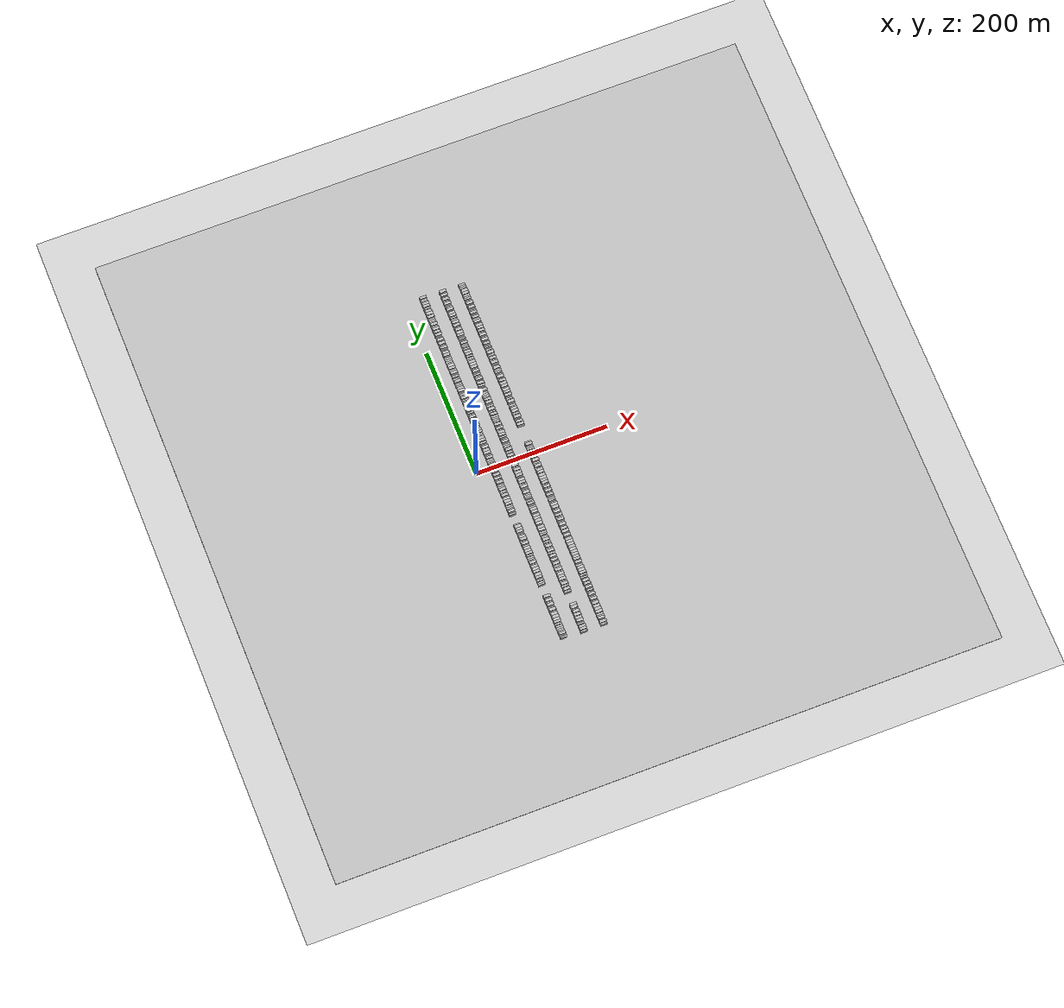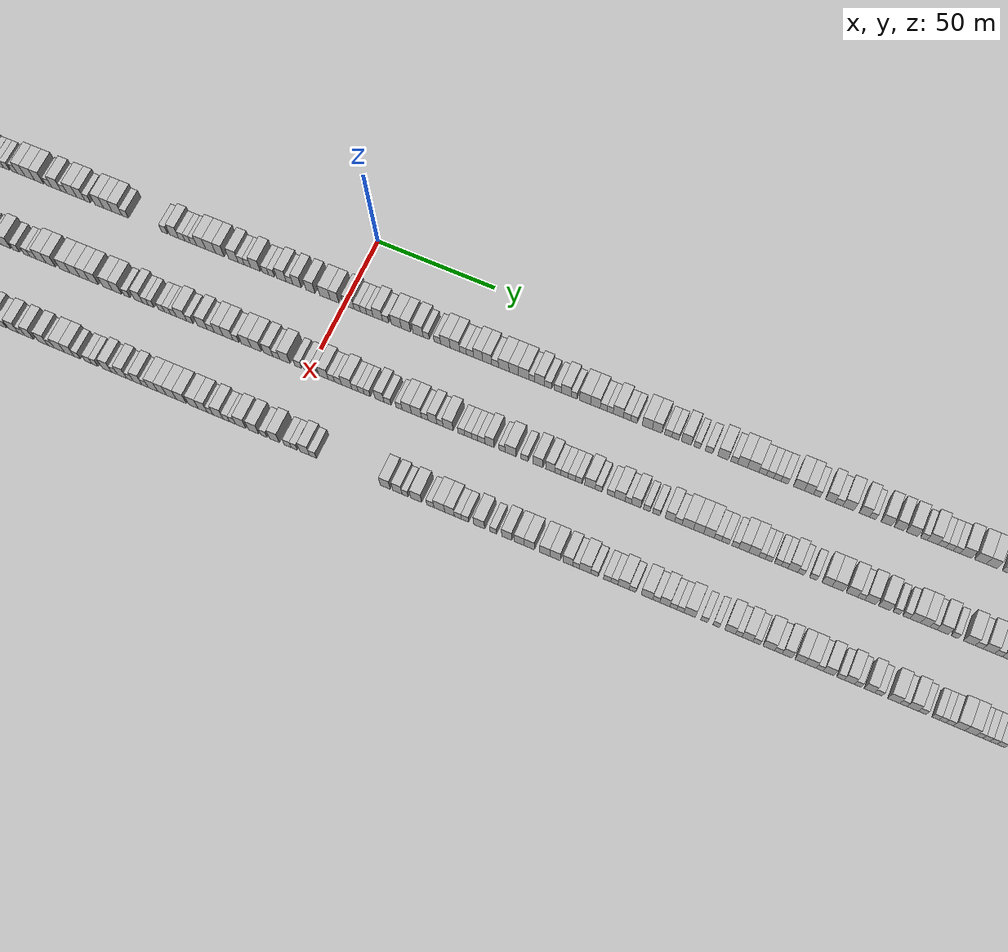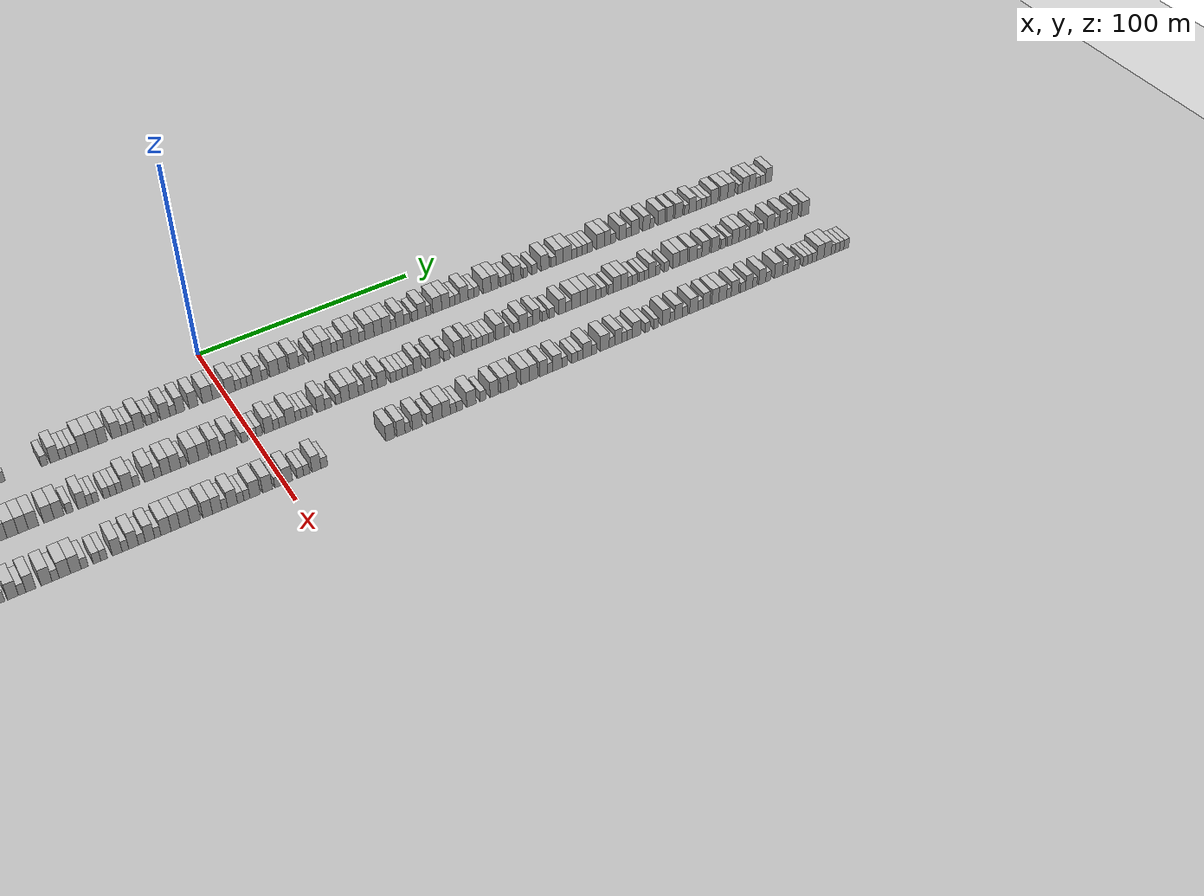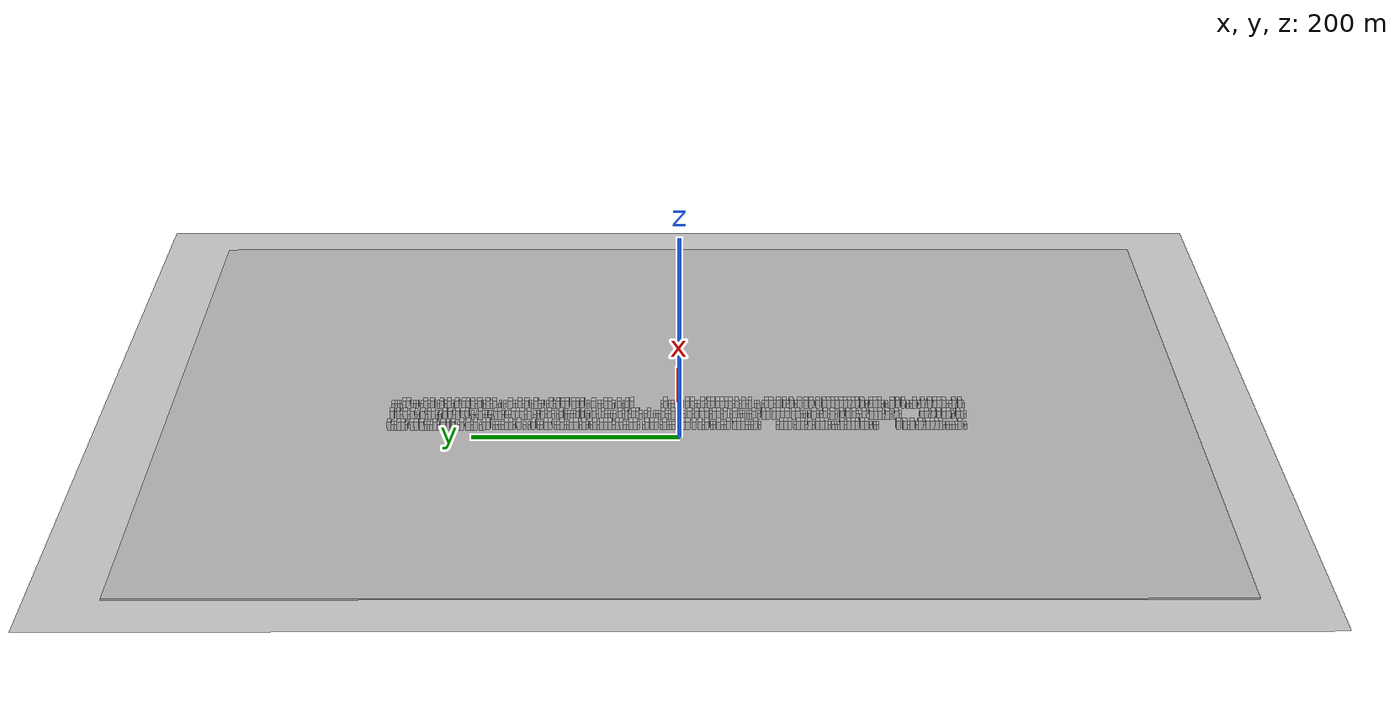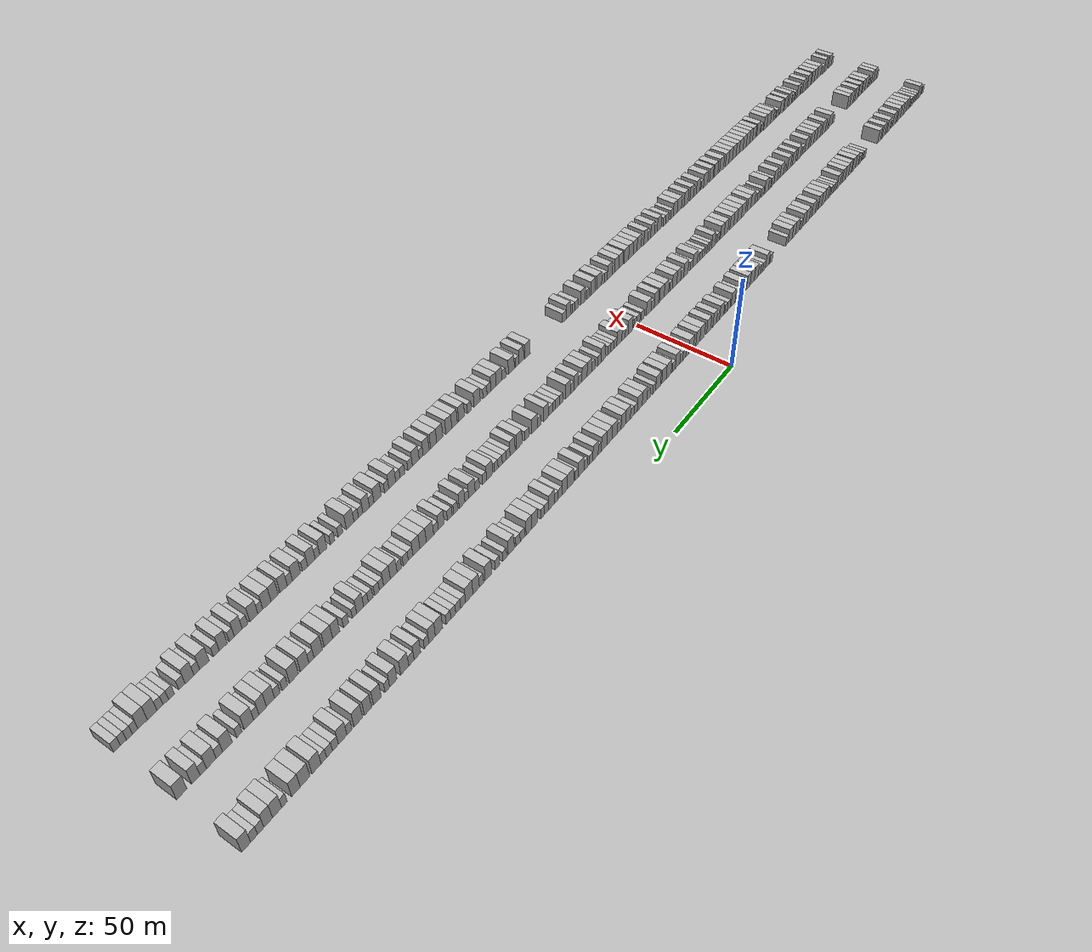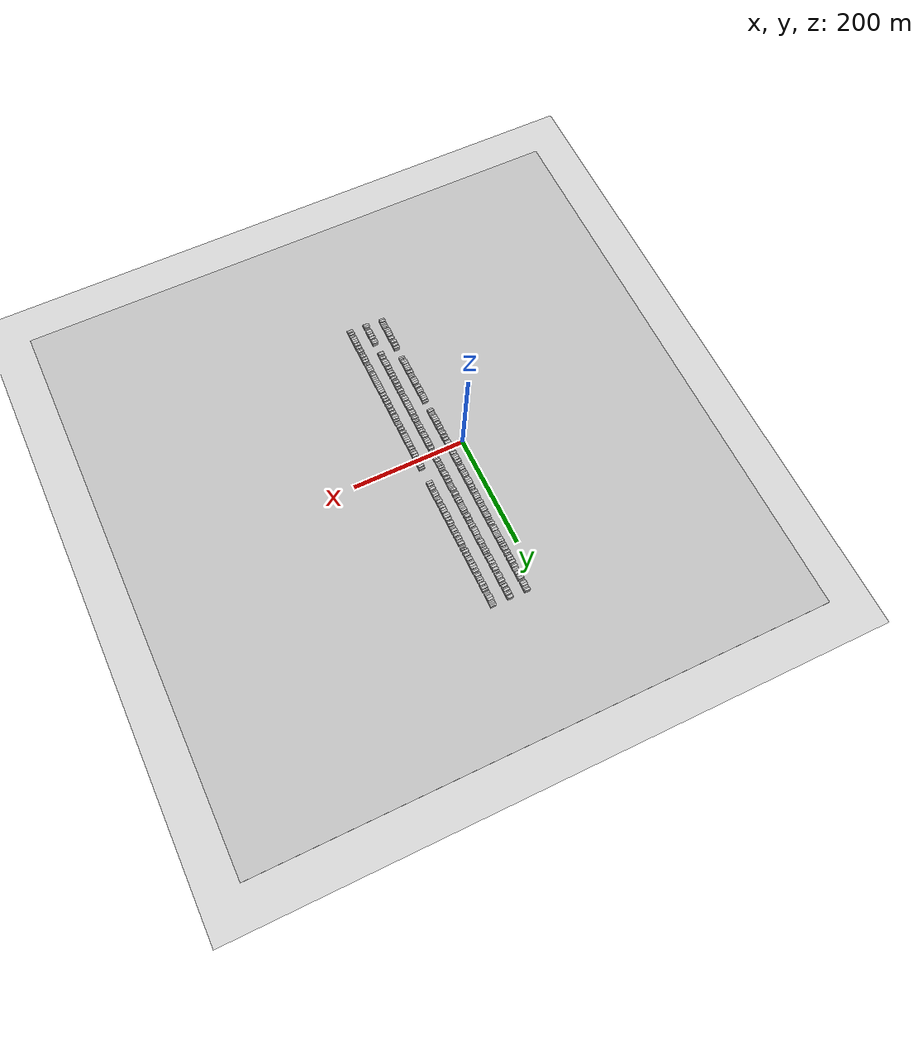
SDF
<?xml version="1.0" encoding="utf-8"?>

<sdf version="1.6">

   <world name="default">

      <gui fullscreen="0">

         <camera name="user_camera">

            <pose>-15 0 4.57585 0 0 0</pose>

            <view_controller>orbit</view_controller>

         </camera>

      </gui>

      <scene>

         <sky>

           <clouds>

             <speed>12</speed>

           </clouds>

         </sky>

         <ambient>0.4 0.4 0.4 1</ambient>

         <background>0.7 0.7 0.7 1</background>

         <shadows>1</shadows>

      </scene>

      <gravity>0 0 -9.8066</gravity>

      <magnetic_field>6e-06 2.3e-05 -4.2e-05</magnetic_field>

      <physics default="0" name="default_physics" type="ode">

         <ode>

            <solver>

               <type>quick</type>

               <iters>10</iters>

               <sor>1.0</sor>

               <use_dynamic_moi_rescaling>0</use_dynamic_moi_rescaling>

            </solver>

            <constraints>

               <cfm>0</cfm>

               <erp>0.2</erp>

               <contact_max_correcting_vel>100</contact_max_correcting_vel>

               <contact_surface_layer>0.001</contact_surface_layer>

            </constraints>

         </ode>

         <max_step_size>0.004</max_step_size>

         <real_time_factor>1</real_time_factor>

         <real_time_update_rate>250</real_time_update_rate>

      </physics>

      <light name="sun" type="directional">

         <cast_shadows>1</cast_shadows>

         <pose>0 0 10 0 0 0</pose>

         <diffuse>0.8 0.8 0.8 1</diffuse>

         <specular>0.2 0.2 0.2 1</specular>

         <attenuation>

            <range>1000</range>

            <constant>0.9</constant>

            <linear>0.01</linear>

            <quadratic>0.001</quadratic>

         </attenuation>

         <direction>-0.5 0.1 -0.9</direction>

      </light>

      <include>

         <name>ground_plane_1</name>

         <uri>model://HANNAS_ground_plane</uri>

         <pose>0 0 0  0 0 0</pose>

      </include>

      <include>

         <name>ground_plane_2</name>

         <uri>model://HANNAS_ground_plane</uri>

         <pose>100 0 0  0 0 0</pose>

      </include>

      <model name="building_1">

         <static>1</static>

         <pose frame="">25.0000 -276.7116 0 0.000000 0.000000 0.000000</pose>

         <link name="link">

            <pose frame="">0 0 3.00 0 0 0</pose>

            <collision name="collision">

               <geometry>

                  <box>

                     <size>10.0000 2.5767 6.0000</size>

                  </box>

               </geometry>

               <max_contacts>10</max_contacts>

               <surface>

                  <contact>

                     <ode/>

                  </contact>

                  <bounce/>

                  <friction>

                     <torsional>

                        <ode/>

                     </torsional>

                     <ode/>

                  </friction>

               </surface>

            </collision>

            <visual name="visual">

               <cast_shadows>0</cast_shadows>

               <geometry>

                  <box>

                     <size>10.0000 2.5767 6.0000</size>

                  </box>

               </geometry>

               <material>

                  <script>

                     <uri>model://HANNAS_wall/materials/scripts</uri>

                     <uri>model://HANNAS_wall/materials/textures</uri>

                     <name>vrc/HANNAS_wall</name>

                  </script>

               </material>

            </visual>

            <self_collide>0</self_collide>

            <enable_wind>0</enable_wind>

            <kinematic>0</kinematic>

         </link>

      </model>

      <model name="building_2">

         <static>1</static>

         <pose frame="">25.0000 -271.4646 0 0.000000 0.000000 0.000000</pose>

         <link name="link">

            <pose frame="">0 0 4.50 0 0 0</pose>

            <collision name="collision">

               <geometry>

                  <box>

                     <size>10.0000 3.9173 9.0000</size>

                  </box>

               </geometry>

               <max_contacts>10</max_contacts>

               <surface>

                  <contact>

                     <ode/>

                  </contact>

                  <bounce/>

                  <friction>

                     <torsional>

                        <ode/>

                     </torsional>

                     <ode/>

                  </friction>

               </surface>

            </collision>

            <visual name="visual">

               <cast_shadows>0</cast_shadows>

               <geometry>

                  <box>

                     <size>10.0000 3.9173 9.0000</size>

                  </box>

               </geometry>

               <material>

                  <script>

                     <uri>model://HANNAS_wall/materials/scripts</uri>

                     <uri>model://HANNAS_wall/materials/textures</uri>

                     <name>vrc/HANNAS_wall</name>

                  </script>

               </material>

            </visual>

            <self_collide>0</self_collide>

            <enable_wind>0</enable_wind>

            <kinematic>0</kinematic>

         </link>

      </model>

      <model name="building_3">

         <static>1</static>

         <pose frame="">25.0000 -268.0789 0 0.000000 0.000000 0.000000</pose>

         <link name="link">

            <pose frame="">0 0 3.00 0 0 0</pose>

            <collision name="collision">

               <geometry>

                  <box>

                     <size>10.0000 2.8543 6.0000</size>

                  </box>

               </geometry>

               <max_contacts>10</max_contacts>

               <surface>

                  <contact>

                     <ode/>

                  </contact>

                  <bounce/>

                  <friction>

                     <torsional>

                        <ode/>

                     </torsional>

                     <ode/>

                  </friction>

               </surface>

            </collision>

            <visual name="visual">

               <cast_shadows>0</cast_shadows>

               <geometry>

                  <box>

                     <size>10.0000 2.8543 6.0000</size>

                  </box>

               </geometry>

               <material>

                  <script>

                     <uri>model://HANNAS_wall/materials/scripts</uri>

                     <uri>model://HANNAS_wall/materials/textures</uri>

                     <name>vrc/HANNAS_wall</name>

                  </script>

               </material>

            </visual>

            <self_collide>0</self_collide>

            <enable_wind>0</enable_wind>

            <kinematic>0</kinematic>

         </link>

      </model>

      <model name="building_4">

         <static>1</static>

         <pose frame="">25.0000 -265.3116 0 0.000000 0.000000 0.000000</pose>

         <link name="link">

            <pose frame="">0 0 3.00 0 0 0</pose>

            <collision name="collision">

               <geometry>

                  <box>

                     <size>10.0000 2.6802 6.0000</size>

                  </box>

               </geometry>

               <max_contacts>10</max_contacts>

               <surface>

                  <contact>

                     <ode/>

                  </contact>

                  <bounce/>

                  <friction>

                     <torsional>

                        <ode/>

                     </torsional>

                     <ode/>

                  </friction>

               </surface>

            </collision>

            <visual name="visual">

               <cast_shadows>0</cast_shadows>

               <geometry>

                  <box>

                     <size>10.0000 2.6802 6.0000</size>

                  </box>

               </geometry>

               <material>

                  <script>

                     <uri>model://HANNAS_wall/materials/scripts</uri>

                     <uri>model://HANNAS_wall/materials/textures</uri>

                     <name>vrc/HANNAS_wall</name>

                  </script>

               </material>

            </visual>

            <self_collide>0</self_collide>

            <enable_wind>0</enable_wind>

            <kinematic>0</kinematic>

         </link>

      </model>

      <model name="building_5">

         <static>1</static>

         <pose frame="">25.0000 -262.4727 0 0.000000 0.000000 0.000000</pose>

         <link name="link">

            <pose frame="">0 0 3.00 0 0 0</pose>

            <collision name="collision">

               <geometry>

                  <box>

                     <size>10.0000 2.9976 6.0000</size>

                  </box>

               </geometry>

               <max_contacts>10</max_contacts>

               <surface>

                  <contact>

                     <ode/>

                  </contact>

                  <bounce/>

                  <friction>

                     <torsional>

                        <ode/>

                     </torsional>

                     <ode/>

                  </friction>

               </surface>

            </collision>

            <visual name="visual">

               <cast_shadows>0</cast_shadows>

               <geometry>

                  <box>

                     <size>10.0000 2.9976 6.0000</size>

                  </box>

               </geometry>

               <material>

                  <script>

                     <uri>model://HANNAS_wall/materials/scripts</uri>

                     <uri>model://HANNAS_wall/materials/textures</uri>

                     <name>vrc/HANNAS_wall</name>

                  </script>

               </material>

            </visual>

            <self_collide>0</self_collide>

            <enable_wind>0</enable_wind>

            <kinematic>0</kinematic>

         </link>

      </model>

      <model name="building_6">

         <static>1</static>

         <pose frame="">25.0000 -259.5861 0 0.000000 0.000000 0.000000</pose>

         <link name="link">

            <pose frame="">0 0 3.00 0 0 0</pose>

            <collision name="collision">

               <geometry>

                  <box>

                     <size>10.0000 2.7755 6.0000</size>

                  </box>

               </geometry>

               <max_contacts>10</max_contacts>

               <surface>

                  <contact>

                     <ode/>

                  </contact>

                  <bounce/>

                  <friction>

                     <torsional>

                        <ode/>

                     </torsional>

                     <ode/>

                  </friction>

               </surface>

            </collision>

            <visual name="visual">

               <cast_shadows>0</cast_shadows>

               <geometry>

                  <box>

                     <size>10.0000 2.7755 6.0000</size>

                  </box>

               </geometry>

               <material>

                  <script>

                     <uri>model://HANNAS_wall/materials/scripts</uri>

                     <uri>model://HANNAS_wall/materials/textures</uri>

                     <name>vrc/HANNAS_wall</name>

                  </script>

               </material>

            </visual>

            <self_collide>0</self_collide>

            <enable_wind>0</enable_wind>

            <kinematic>0</kinematic>

         </link>

      </model>

      <model name="building_7">

         <static>1</static>

         <pose frame="">25.0000 -255.9242 0 0.000000 0.000000 0.000000</pose>

         <link name="link">

            <pose frame="">0 0 3.00 0 0 0</pose>

            <collision name="collision">

               <geometry>

                  <box>

                     <size>10.0000 2.5485 6.0000</size>

                  </box>

               </geometry>

               <max_contacts>10</max_contacts>

               <surface>

                  <contact>

                     <ode/>

                  </contact>

                  <bounce/>

                  <friction>

                     <torsional>

                        <ode/>

                     </torsional>

                     <ode/>

                  </friction>

               </surface>

            </collision>

            <visual name="visual">

               <cast_shadows>0</cast_shadows>

               <geometry>

                  <box>

                     <size>10.0000 2.5485 6.0000</size>

                  </box>

               </geometry>

               <material>

                  <script>

                     <uri>model://HANNAS_wall/materials/scripts</uri>

                     <uri>model://HANNAS_wall/materials/textures</uri>

                     <name>vrc/HANNAS_wall</name>

                  </script>

               </material>

            </visual>

            <self_collide>0</self_collide>

            <enable_wind>0</enable_wind>

            <kinematic>0</kinematic>

         </link>

      </model>

      <model name="building_8">

         <static>1</static>

         <pose frame="">25.0000 -252.8367 0 0.000000 0.000000 0.000000</pose>

         <link name="link">

            <pose frame="">0 0 4.50 0 0 0</pose>

            <collision name="collision">

               <geometry>

                  <box>

                     <size>10.0000 3.6265 9.0000</size>

                  </box>

               </geometry>

               <max_contacts>10</max_contacts>

               <surface>

                  <contact>

                     <ode/>

                  </contact>

                  <bounce/>

                  <friction>

                     <torsional>

                        <ode/>

                     </torsional>

                     <ode/>

                  </friction>

               </surface>

            </collision>

            <visual name="visual">

               <cast_shadows>0</cast_shadows>

               <geometry>

                  <box>

                     <size>10.0000 3.6265 9.0000</size>

                  </box>

               </geometry>

               <material>

                  <script>

                     <uri>model://HANNAS_wall/materials/scripts</uri>

                     <uri>model://HANNAS_wall/materials/textures</uri>

                     <name>vrc/HANNAS_wall</name>

                  </script>

               </material>

            </visual>

            <self_collide>0</self_collide>

            <enable_wind>0</enable_wind>

            <kinematic>0</kinematic>

         </link>

      </model>

      <model name="building_9">

         <static>1</static>

         <pose frame="">25.0000 -248.9748 0 0.000000 0.000000 0.000000</pose>

         <link name="link">

            <pose frame="">0 0 4.50 0 0 0</pose>

            <collision name="collision">

               <geometry>

                  <box>

                     <size>10.0000 4.0972 9.0000</size>

                  </box>

               </geometry>

               <max_contacts>10</max_contacts>

               <surface>

                  <contact>

                     <ode/>

                  </contact>

                  <bounce/>

                  <friction>

                     <torsional>

                        <ode/>

                     </torsional>

                     <ode/>

                  </friction>

               </surface>

            </collision>

            <visual name="visual">

               <cast_shadows>0</cast_shadows>

               <geometry>

                  <box>

                     <size>10.0000 4.0972 9.0000</size>

                  </box>

               </geometry>

               <material>

                  <script>

                     <uri>model://HANNAS_wall/materials/scripts</uri>

                     <uri>model://HANNAS_wall/materials/textures</uri>

                     <name>vrc/HANNAS_wall</name>

                  </script>

               </material>

            </visual>

            <self_collide>0</self_collide>

            <enable_wind>0</enable_wind>

            <kinematic>0</kinematic>

         </link>

      </model>

      <model name="building_10">

         <static>1</static>

         <pose frame="">25.0000 -244.7154 0 0.000000 0.000000 0.000000</pose>

         <link name="link">

            <pose frame="">0 0 4.50 0 0 0</pose>

            <collision name="collision">

               <geometry>

                  <box>

                     <size>10.0000 4.4216 9.0000</size>

                  </box>

               </geometry>

               <max_contacts>10</max_contacts>

               <surface>

                  <contact>

                     <ode/>

                  </contact>

                  <bounce/>

                  <friction>

                     <torsional>

                        <ode/>

                     </torsional>

                     <ode/>

                  </friction>

               </surface>

            </collision>

            <visual name="visual">

               <cast_shadows>0</cast_shadows>

               <geometry>

                  <box>

                     <size>10.0000 4.4216 9.0000</size>

                  </box>

               </geometry>

               <material>

                  <script>

                     <uri>model://HANNAS_wall/materials/scripts</uri>

                     <uri>model://HANNAS_wall/materials/textures</uri>

                     <name>vrc/HANNAS_wall</name>

                  </script>

               </material>

            </visual>

            <self_collide>0</self_collide>

            <enable_wind>0</enable_wind>

            <kinematic>0</kinematic>

         </link>

      </model>

      <model name="building_11">

         <static>1</static>

         <pose frame="">25.0000 -240.3036 0 0.000000 0.000000 0.000000</pose>

         <link name="link">

            <pose frame="">0 0 4.50 0 0 0</pose>

            <collision name="collision">

               <geometry>

                  <box>

                     <size>10.0000 4.4019 9.0000</size>

                  </box>

               </geometry>

               <max_contacts>10</max_contacts>

               <surface>

                  <contact>

                     <ode/>

                  </contact>

                  <bounce/>

                  <friction>

                     <torsional>

                        <ode/>

                     </torsional>

                     <ode/>

                  </friction>

               </surface>

            </collision>

            <visual name="visual">

               <cast_shadows>0</cast_shadows>

               <geometry>

                  <box>

                     <size>10.0000 4.4019 9.0000</size>

                  </box>

               </geometry>

               <material>

                  <script>

                     <uri>model://HANNAS_wall/materials/scripts</uri>

                     <uri>model://HANNAS_wall/materials/textures</uri>

                     <name>vrc/HANNAS_wall</name>

                  </script>

               </material>

            </visual>

            <self_collide>0</self_collide>

            <enable_wind>0</enable_wind>

            <kinematic>0</kinematic>

         </link>

      </model>

      <model name="building_12">

         <static>1</static>

         <pose frame="">25.0000 -236.8197 0 0.000000 0.000000 0.000000</pose>

         <link name="link">

            <pose frame="">0 0 3.00 0 0 0</pose>

            <collision name="collision">

               <geometry>

                  <box>

                     <size>10.0000 2.5658 6.0000</size>

                  </box>

               </geometry>

               <max_contacts>10</max_contacts>

               <surface>

                  <contact>

                     <ode/>

                  </contact>

                  <bounce/>

                  <friction>

                     <torsional>

                        <ode/>

                     </torsional>

                     <ode/>

                  </friction>

               </surface>

            </collision>

            <visual name="visual">

               <cast_shadows>0</cast_shadows>

               <geometry>

                  <box>

                     <size>10.0000 2.5658 6.0000</size>

                  </box>

               </geometry>

               <material>

                  <script>

                     <uri>model://HANNAS_wall/materials/scripts</uri>

                     <uri>model://HANNAS_wall/materials/textures</uri>

                     <name>vrc/HANNAS_wall</name>

                  </script>

               </material>

            </visual>

            <self_collide>0</self_collide>

            <enable_wind>0</enable_wind>

            <kinematic>0</kinematic>

         </link>

      </model>

      <model name="building_13">

         <static>1</static>

         <pose frame="">25.0000 -233.3019 0 0.000000 0.000000 0.000000</pose>

         <link name="link">

            <pose frame="">0 0 4.50 0 0 0</pose>

            <collision name="collision">

               <geometry>

                  <box>

                     <size>10.0000 4.4698 9.0000</size>

                  </box>

               </geometry>

               <max_contacts>10</max_contacts>

               <surface>

                  <contact>

                     <ode/>

                  </contact>

                  <bounce/>

                  <friction>

                     <torsional>

                        <ode/>

                     </torsional>

                     <ode/>

                  </friction>

               </surface>

            </collision>

            <visual name="visual">

               <cast_shadows>0</cast_shadows>

               <geometry>

                  <box>

                     <size>10.0000 4.4698 9.0000</size>

                  </box>

               </geometry>

               <material>

                  <script>

                     <uri>model://HANNAS_wall/materials/scripts</uri>

                     <uri>model://HANNAS_wall/materials/textures</uri>

                     <name>vrc/HANNAS_wall</name>

                  </script>

               </material>

            </visual>

            <self_collide>0</self_collide>

            <enable_wind>0</enable_wind>

            <kinematic>0</kinematic>

         </link>

      </model>

      <model name="building_14">

         <static>1</static>

         <pose frame="">25.0000 -229.7931 0 0.000000 0.000000 0.000000</pose>

         <link name="link">

            <pose frame="">0 0 3.00 0 0 0</pose>

            <collision name="collision">

               <geometry>

                  <box>

                     <size>10.0000 2.5478 6.0000</size>

                  </box>

               </geometry>

               <max_contacts>10</max_contacts>

               <surface>

                  <contact>

                     <ode/>

                  </contact>

                  <bounce/>

                  <friction>

                     <torsional>

                        <ode/>

                     </torsional>

                     <ode/>

                  </friction>

               </surface>

            </collision>

            <visual name="visual">

               <cast_shadows>0</cast_shadows>

               <geometry>

                  <box>

                     <size>10.0000 2.5478 6.0000</size>

                  </box>

               </geometry>

               <material>

                  <script>

                     <uri>model://HANNAS_wall/materials/scripts</uri>

                     <uri>model://HANNAS_wall/materials/textures</uri>

                     <name>vrc/HANNAS_wall</name>

                  </script>

               </material>

            </visual>

            <self_collide>0</self_collide>

            <enable_wind>0</enable_wind>

            <kinematic>0</kinematic>

         </link>

      </model>

      <model name="building_15">

         <static>1</static>

         <pose frame="">25.0000 -225.3217 0 0.000000 0.000000 0.000000</pose>

         <link name="link">

            <pose frame="">0 0 4.50 0 0 0</pose>

            <collision name="collision">

               <geometry>

                  <box>

                     <size>10.0000 4.3950 9.0000</size>

                  </box>

               </geometry>

               <max_contacts>10</max_contacts>

               <surface>

                  <contact>

                     <ode/>

                  </contact>

                  <bounce/>

                  <friction>

                     <torsional>

                        <ode/>

                     </torsional>

                     <ode/>

                  </friction>

               </surface>

            </collision>

            <visual name="visual">

               <cast_shadows>0</cast_shadows>

               <geometry>

                  <box>

                     <size>10.0000 4.3950 9.0000</size>

                  </box>

               </geometry>

               <material>

                  <script>

                     <uri>model://HANNAS_wall/materials/scripts</uri>

                     <uri>model://HANNAS_wall/materials/textures</uri>

                     <name>vrc/HANNAS_wall</name>

                  </script>

               </material>

            </visual>

            <self_collide>0</self_collide>

            <enable_wind>0</enable_wind>

            <kinematic>0</kinematic>

         </link>

      </model>

      <model name="building_16">

         <static>1</static>

         <pose frame="">25.0000 -221.7504 0 0.000000 0.000000 0.000000</pose>

         <link name="link">

            <pose frame="">0 0 3.00 0 0 0</pose>

            <collision name="collision">

               <geometry>

                  <box>

                     <size>10.0000 2.7476 6.0000</size>

                  </box>

               </geometry>

               <max_contacts>10</max_contacts>

               <surface>

                  <contact>

                     <ode/>

                  </contact>

                  <bounce/>

                  <friction>

                     <torsional>

                        <ode/>

                     </torsional>

                     <ode/>

                  </friction>

               </surface>

            </collision>

            <visual name="visual">

               <cast_shadows>0</cast_shadows>

               <geometry>

                  <box>

                     <size>10.0000 2.7476 6.0000</size>

                  </box>

               </geometry>

               <material>

                  <script>

                     <uri>model://HANNAS_wall/materials/scripts</uri>

                     <uri>model://HANNAS_wall/materials/textures</uri>

                     <name>vrc/HANNAS_wall</name>

                  </script>

               </material>

            </visual>

            <self_collide>0</self_collide>

            <enable_wind>0</enable_wind>

            <kinematic>0</kinematic>

         </link>

      </model>

      <model name="building_17">

         <static>1</static>

         <pose frame="">25.0000 -218.2101 0 0.000000 0.000000 0.000000</pose>

         <link name="link">

            <pose frame="">0 0 4.50 0 0 0</pose>

            <collision name="collision">

               <geometry>

                  <box>

                     <size>10.0000 4.3330 9.0000</size>

                  </box>

               </geometry>

               <max_contacts>10</max_contacts>

               <surface>

                  <contact>

                     <ode/>

                  </contact>

                  <bounce/>

                  <friction>

                     <torsional>

                        <ode/>

                     </torsional>

                     <ode/>

                  </friction>

               </surface>

            </collision>

            <visual name="visual">

               <cast_shadows>0</cast_shadows>

               <geometry>

                  <box>

                     <size>10.0000 4.3330 9.0000</size>

                  </box>

               </geometry>

               <material>

                  <script>

                     <uri>model://HANNAS_wall/materials/scripts</uri>

                     <uri>model://HANNAS_wall/materials/textures</uri>

                     <name>vrc/HANNAS_wall</name>

                  </script>

               </material>

            </visual>

            <self_collide>0</self_collide>

            <enable_wind>0</enable_wind>

            <kinematic>0</kinematic>

         </link>

      </model>

      <model name="building_18">

         <static>1</static>

         <pose frame="">25.0000 -211.9402 0 0.000000 0.000000 0.000000</pose>

         <link name="link">

            <pose frame="">0 0 4.50 0 0 0</pose>

            <collision name="collision">

               <geometry>

                  <box>

                     <size>10.0000 4.2069 9.0000</size>

                  </box>

               </geometry>

               <max_contacts>10</max_contacts>

               <surface>

                  <contact>

                     <ode/>

                  </contact>

                  <bounce/>

                  <friction>

                     <torsional>

                        <ode/>

                     </torsional>

                     <ode/>

                  </friction>

               </surface>

            </collision>

            <visual name="visual">

               <cast_shadows>0</cast_shadows>

               <geometry>

                  <box>

                     <size>10.0000 4.2069 9.0000</size>

                  </box>

               </geometry>

               <material>

                  <script>

                     <uri>model://HANNAS_wall/materials/scripts</uri>

                     <uri>model://HANNAS_wall/materials/textures</uri>

                     <name>vrc/HANNAS_wall</name>

                  </script>

               </material>

            </visual>

            <self_collide>0</self_collide>

            <enable_wind>0</enable_wind>

            <kinematic>0</kinematic>

         </link>

      </model>

      <model name="building_19">

         <static>1</static>

         <pose frame="">25.0000 -191.6206 0 0.000000 0.000000 0.000000</pose>

         <link name="link">

            <pose frame="">0 0 3.00 0 0 0</pose>

            <collision name="collision">

               <geometry>

                  <box>

                     <size>10.0000 2.8107 6.0000</size>

                  </box>

               </geometry>

               <max_contacts>10</max_contacts>

               <surface>

                  <contact>

                     <ode/>

                  </contact>

                  <bounce/>

                  <friction>

                     <torsional>

                        <ode/>

                     </torsional>

                     <ode/>

                  </friction>

               </surface>

            </collision>

            <visual name="visual">

               <cast_shadows>0</cast_shadows>

               <geometry>

                  <box>

                     <size>10.0000 2.8107 6.0000</size>

                  </box>

               </geometry>

               <material>

                  <script>

                     <uri>model://HANNAS_wall/materials/scripts</uri>

                     <uri>model://HANNAS_wall/materials/textures</uri>

                     <name>vrc/HANNAS_wall</name>

                  </script>

               </material>

            </visual>

            <self_collide>0</self_collide>

            <enable_wind>0</enable_wind>

            <kinematic>0</kinematic>

         </link>

      </model>

      <model name="building_20">

         <static>1</static>

         <pose frame="">25.0000 -188.9801 0 0.000000 0.000000 0.000000</pose>

         <link name="link">

            <pose frame="">0 0 3.00 0 0 0</pose>

            <collision name="collision">

               <geometry>

                  <box>

                     <size>10.0000 2.4702 6.0000</size>

                  </box>

               </geometry>

               <max_contacts>10</max_contacts>

               <surface>

                  <contact>

                     <ode/>

                  </contact>

                  <bounce/>

                  <friction>

                     <torsional>

                        <ode/>

                     </torsional>

                     <ode/>

                  </friction>

               </surface>

            </collision>

            <visual name="visual">

               <cast_shadows>0</cast_shadows>

               <geometry>

                  <box>

                     <size>10.0000 2.4702 6.0000</size>

                  </box>

               </geometry>

               <material>

                  <script>

                     <uri>model://HANNAS_wall/materials/scripts</uri>

                     <uri>model://HANNAS_wall/materials/textures</uri>

                     <name>vrc/HANNAS_wall</name>

                  </script>

               </material>

            </visual>

            <self_collide>0</self_collide>

            <enable_wind>0</enable_wind>

            <kinematic>0</kinematic>

         </link>

      </model>

      <model name="building_21">

         <static>1</static>

         <pose frame="">25.0000 -185.3558 0 0.000000 0.000000 0.000000</pose>

         <link name="link">

            <pose frame="">0 0 3.00 0 0 0</pose>

            <collision name="collision">

               <geometry>

                  <box>

                     <size>10.0000 2.7786 6.0000</size>

                  </box>

               </geometry>

               <max_contacts>10</max_contacts>

               <surface>

                  <contact>

                     <ode/>

                  </contact>

                  <bounce/>

                  <friction>

                     <torsional>

                        <ode/>

                     </torsional>

                     <ode/>

                  </friction>

               </surface>

            </collision>

            <visual name="visual">

               <cast_shadows>0</cast_shadows>

               <geometry>

                  <box>

                     <size>10.0000 2.7786 6.0000</size>

                  </box>

               </geometry>

               <material>

                  <script>

                     <uri>model://HANNAS_wall/materials/scripts</uri>

                     <uri>model://HANNAS_wall/materials/textures</uri>

                     <name>vrc/HANNAS_wall</name>

                  </script>

               </material>

            </visual>

            <self_collide>0</self_collide>

            <enable_wind>0</enable_wind>

            <kinematic>0</kinematic>

         </link>

      </model>

      <model name="building_22">

         <static>1</static>

         <pose frame="">25.0000 -181.0683 0 0.000000 0.000000 0.000000</pose>

         <link name="link">

            <pose frame="">0 0 4.50 0 0 0</pose>

            <collision name="collision">

               <geometry>

                  <box>

                     <size>10.0000 3.7964 9.0000</size>

                  </box>

               </geometry>

               <max_contacts>10</max_contacts>

               <surface>

                  <contact>

                     <ode/>

                  </contact>

                  <bounce/>

                  <friction>

                     <torsional>

                        <ode/>

                     </torsional>

                     <ode/>

                  </friction>

               </surface>

            </collision>

            <visual name="visual">

               <cast_shadows>0</cast_shadows>

               <geometry>

                  <box>

                     <size>10.0000 3.7964 9.0000</size>

                  </box>

               </geometry>

               <material>

                  <script>

                     <uri>model://HANNAS_wall/materials/scripts</uri>

                     <uri>model://HANNAS_wall/materials/textures</uri>

                     <name>vrc/HANNAS_wall</name>

                  </script>

               </material>

            </visual>

            <self_collide>0</self_collide>

            <enable_wind>0</enable_wind>

            <kinematic>0</kinematic>

         </link>

      </model>

      <model name="building_23">

         <static>1</static>

         <pose frame="">25.0000 -176.9967 0 0.000000 0.000000 0.000000</pose>

         <link name="link">

            <pose frame="">0 0 4.50 0 0 0</pose>

            <collision name="collision">

               <geometry>

                  <box>

                     <size>10.0000 4.3467 9.0000</size>

                  </box>

               </geometry>

               <max_contacts>10</max_contacts>

               <surface>

                  <contact>

                     <ode/>

                  </contact>

                  <bounce/>

                  <friction>

                     <torsional>

                        <ode/>

                     </torsional>

                     <ode/>

                  </friction>

               </surface>

            </collision>

            <visual name="visual">

               <cast_shadows>0</cast_shadows>

               <geometry>

                  <box>

                     <size>10.0000 4.3467 9.0000</size>

                  </box>

               </geometry>

               <material>

                  <script>

                     <uri>model://HANNAS_wall/materials/scripts</uri>

                     <uri>model://HANNAS_wall/materials/textures</uri>

                     <name>vrc/HANNAS_wall</name>

                  </script>

               </material>

            </visual>

            <self_collide>0</self_collide>

            <enable_wind>0</enable_wind>

            <kinematic>0</kinematic>

         </link>

      </model>

      <model name="building_24">

         <static>1</static>

         <pose frame="">25.0000 -171.9124 0 0.000000 0.000000 0.000000</pose>

         <link name="link">

            <pose frame="">0 0 4.50 0 0 0</pose>

            <collision name="collision">

               <geometry>

                  <box>

                     <size>10.0000 3.8219 9.0000</size>

                  </box>

               </geometry>

               <max_contacts>10</max_contacts>

               <surface>

                  <contact>

                     <ode/>

                  </contact>

                  <bounce/>

                  <friction>

                     <torsional>

                        <ode/>

                     </torsional>

                     <ode/>

                  </friction>

               </surface>

            </collision>

            <visual name="visual">

               <cast_shadows>0</cast_shadows>

               <geometry>

                  <box>

                     <size>10.0000 3.8219 9.0000</size>

                  </box>

               </geometry>

               <material>

                  <script>

                     <uri>model://HANNAS_wall/materials/scripts</uri>

                     <uri>model://HANNAS_wall/materials/textures</uri>

                     <name>vrc/HANNAS_wall</name>

                  </script>

               </material>

            </visual>

            <self_collide>0</self_collide>

            <enable_wind>0</enable_wind>

            <kinematic>0</kinematic>

         </link>

      </model>

      <model name="building_25">

         <static>1</static>

         <pose frame="">25.0000 -167.8918 0 0.000000 0.000000 0.000000</pose>

         <link name="link">

            <pose frame="">0 0 4.50 0 0 0</pose>

            <collision name="collision">

               <geometry>

                  <box>

                     <size>10.0000 4.2192 9.0000</size>

                  </box>

               </geometry>

               <max_contacts>10</max_contacts>

               <surface>

                  <contact>

                     <ode/>

                  </contact>

                  <bounce/>

                  <friction>

                     <torsional>

                        <ode/>

                     </torsional>

                     <ode/>

                  </friction>

               </surface>

            </collision>

            <visual name="visual">

               <cast_shadows>0</cast_shadows>

               <geometry>

                  <box>

                     <size>10.0000 4.2192 9.0000</size>

                  </box>

               </geometry>

               <material>

                  <script>

                     <uri>model://HANNAS_wall/materials/scripts</uri>

                     <uri>model://HANNAS_wall/materials/textures</uri>

                     <name>vrc/HANNAS_wall</name>

                  </script>

               </material>

            </visual>

            <self_collide>0</self_collide>

            <enable_wind>0</enable_wind>

            <kinematic>0</kinematic>

         </link>

      </model>

      <model name="building_26">

         <static>1</static>

         <pose frame="">25.0000 -163.8334 0 0.000000 0.000000 0.000000</pose>

         <link name="link">

            <pose frame="">0 0 4.50 0 0 0</pose>

            <collision name="collision">

               <geometry>

                  <box>

                     <size>10.0000 3.8976 9.0000</size>

                  </box>

               </geometry>

               <max_contacts>10</max_contacts>

               <surface>

                  <contact>

                     <ode/>

                  </contact>

                  <bounce/>

                  <friction>

                     <torsional>

                        <ode/>

                     </torsional>

                     <ode/>

                  </friction>

               </surface>

            </collision>

            <visual name="visual">

               <cast_shadows>0</cast_shadows>

               <geometry>

                  <box>

                     <size>10.0000 3.8976 9.0000</size>

                  </box>

               </geometry>

               <material>

                  <script>

                     <uri>model://HANNAS_wall/materials/scripts</uri>

                     <uri>model://HANNAS_wall/materials/textures</uri>

                     <name>vrc/HANNAS_wall</name>

                  </script>

               </material>

            </visual>

            <self_collide>0</self_collide>

            <enable_wind>0</enable_wind>

            <kinematic>0</kinematic>

         </link>

      </model>

      <model name="building_27">

         <static>1</static>

         <pose frame="">25.0000 -160.6127 0 0.000000 0.000000 0.000000</pose>

         <link name="link">

            <pose frame="">0 0 3.00 0 0 0</pose>

            <collision name="collision">

               <geometry>

                  <box>

                     <size>10.0000 2.5439 6.0000</size>

                  </box>

               </geometry>

               <max_contacts>10</max_contacts>

               <surface>

                  <contact>

                     <ode/>

                  </contact>

                  <bounce/>

                  <friction>

                     <torsional>

                        <ode/>

                     </torsional>

                     <ode/>

                  </friction>

               </surface>

            </collision>

            <visual name="visual">

               <cast_shadows>0</cast_shadows>

               <geometry>

                  <box>

                     <size>10.0000 2.5439 6.0000</size>

                  </box>

               </geometry>

               <material>

                  <script>

                     <uri>model://HANNAS_wall/materials/scripts</uri>

                     <uri>model://HANNAS_wall/materials/textures</uri>

                     <name>vrc/HANNAS_wall</name>

                  </script>

               </material>

            </visual>

            <self_collide>0</self_collide>

            <enable_wind>0</enable_wind>

            <kinematic>0</kinematic>

         </link>

      </model>

      <model name="building_28">

         <static>1</static>

         <pose frame="">25.0000 -157.1994 0 0.000000 0.000000 0.000000</pose>

         <link name="link">

            <pose frame="">0 0 4.50 0 0 0</pose>

            <collision name="collision">

               <geometry>

                  <box>

                     <size>10.0000 4.2827 9.0000</size>

                  </box>

               </geometry>

               <max_contacts>10</max_contacts>

               <surface>

                  <contact>

                     <ode/>

                  </contact>

                  <bounce/>

                  <friction>

                     <torsional>

                        <ode/>

                     </torsional>

                     <ode/>

                  </friction>

               </surface>

            </collision>

            <visual name="visual">

               <cast_shadows>0</cast_shadows>

               <geometry>

                  <box>

                     <size>10.0000 4.2827 9.0000</size>

                  </box>

               </geometry>

               <material>

                  <script>

                     <uri>model://HANNAS_wall/materials/scripts</uri>

                     <uri>model://HANNAS_wall/materials/textures</uri>

                     <name>vrc/HANNAS_wall</name>

                  </script>

               </material>

            </visual>

            <self_collide>0</self_collide>

            <enable_wind>0</enable_wind>

            <kinematic>0</kinematic>

         </link>

      </model>

      <model name="building_29">

         <static>1</static>

         <pose frame="">25.0000 -153.8131 0 0.000000 0.000000 0.000000</pose>

         <link name="link">

            <pose frame="">0 0 3.00 0 0 0</pose>

            <collision name="collision">

               <geometry>

                  <box>

                     <size>10.0000 2.4900 6.0000</size>

                  </box>

               </geometry>

               <max_contacts>10</max_contacts>

               <surface>

                  <contact>

                     <ode/>

                  </contact>

                  <bounce/>

                  <friction>

                     <torsional>

                        <ode/>

                     </torsional>

                     <ode/>

                  </friction>

               </surface>

            </collision>

            <visual name="visual">

               <cast_shadows>0</cast_shadows>

               <geometry>

                  <box>

                     <size>10.0000 2.4900 6.0000</size>

                  </box>

               </geometry>

               <material>

                  <script>

                     <uri>model://HANNAS_wall/materials/scripts</uri>

                     <uri>model://HANNAS_wall/materials/textures</uri>

                     <name>vrc/HANNAS_wall</name>

                  </script>

               </material>

            </visual>

            <self_collide>0</self_collide>

            <enable_wind>0</enable_wind>

            <kinematic>0</kinematic>

         </link>

      </model>

      <model name="building_30">

         <static>1</static>

         <pose frame="">25.0000 -151.3480 0 0.000000 0.000000 0.000000</pose>

         <link name="link">

            <pose frame="">0 0 3.00 0 0 0</pose>

            <collision name="collision">

               <geometry>

                  <box>

                     <size>10.0000 2.4401 6.0000</size>

                  </box>

               </geometry>

               <max_contacts>10</max_contacts>

               <surface>

                  <contact>

                     <ode/>

                  </contact>

                  <bounce/>

                  <friction>

                     <torsional>

                        <ode/>

                     </torsional>

                     <ode/>

                  </friction>

               </surface>

            </collision>

            <visual name="visual">

               <cast_shadows>0</cast_shadows>

               <geometry>

                  <box>

                     <size>10.0000 2.4401 6.0000</size>

                  </box>

               </geometry>

               <material>

                  <script>

                     <uri>model://HANNAS_wall/materials/scripts</uri>

                     <uri>model://HANNAS_wall/materials/textures</uri>

                     <name>vrc/HANNAS_wall</name>

                  </script>

               </material>

            </visual>

            <self_collide>0</self_collide>

            <enable_wind>0</enable_wind>

            <kinematic>0</kinematic>

         </link>

      </model>

      <model name="building_31">

         <static>1</static>

         <pose frame="">25.0000 -148.7919 0 0.000000 0.000000 0.000000</pose>

         <link name="link">

            <pose frame="">0 0 3.00 0 0 0</pose>

            <collision name="collision">

               <geometry>

                  <box>

                     <size>10.0000 2.6721 6.0000</size>

                  </box>

               </geometry>

               <max_contacts>10</max_contacts>

               <surface>

                  <contact>

                     <ode/>

                  </contact>

                  <bounce/>

                  <friction>

                     <torsional>

                        <ode/>

                     </torsional>

                     <ode/>

                  </friction>

               </surface>

            </collision>

            <visual name="visual">

               <cast_shadows>0</cast_shadows>

               <geometry>

                  <box>

                     <size>10.0000 2.6721 6.0000</size>

                  </box>

               </geometry>

               <material>

                  <script>

                     <uri>model://HANNAS_wall/materials/scripts</uri>

                     <uri>model://HANNAS_wall/materials/textures</uri>

                     <name>vrc/HANNAS_wall</name>

                  </script>

               </material>

            </visual>

            <self_collide>0</self_collide>

            <enable_wind>0</enable_wind>

            <kinematic>0</kinematic>

         </link>

      </model>

      <model name="building_32">

         <static>1</static>

         <pose frame="">25.0000 -145.2476 0 0.000000 0.000000 0.000000</pose>

         <link name="link">

            <pose frame="">0 0 3.00 0 0 0</pose>

            <collision name="collision">

               <geometry>

                  <box>

                     <size>10.0000 2.4164 6.0000</size>

                  </box>

               </geometry>

               <max_contacts>10</max_contacts>

               <surface>

                  <contact>

                     <ode/>

                  </contact>

                  <bounce/>

                  <friction>

                     <torsional>

                        <ode/>

                     </torsional>

                     <ode/>

                  </friction>

               </surface>

            </collision>

            <visual name="visual">

               <cast_shadows>0</cast_shadows>

               <geometry>

                  <box>

                     <size>10.0000 2.4164 6.0000</size>

                  </box>

               </geometry>

               <material>

                  <script>

                     <uri>model://HANNAS_wall/materials/scripts</uri>

                     <uri>model://HANNAS_wall/materials/textures</uri>

                     <name>vrc/HANNAS_wall</name>

                  </script>

               </material>

            </visual>

            <self_collide>0</self_collide>

            <enable_wind>0</enable_wind>

            <kinematic>0</kinematic>

         </link>

      </model>

      <model name="building_33">

         <static>1</static>

         <pose frame="">25.0000 -142.1859 0 0.000000 0.000000 0.000000</pose>

         <link name="link">

            <pose frame="">0 0 4.50 0 0 0</pose>

            <collision name="collision">

               <geometry>

                  <box>

                     <size>10.0000 3.7071 9.0000</size>

                  </box>

               </geometry>

               <max_contacts>10</max_contacts>

               <surface>

                  <contact>

                     <ode/>

                  </contact>

                  <bounce/>

                  <friction>

                     <torsional>

                        <ode/>

                     </torsional>

                     <ode/>

                  </friction>

               </surface>

            </collision>

            <visual name="visual">

               <cast_shadows>0</cast_shadows>

               <geometry>

                  <box>

                     <size>10.0000 3.7071 9.0000</size>

                  </box>

               </geometry>

               <material>

                  <script>

                     <uri>model://HANNAS_wall/materials/scripts</uri>

                     <uri>model://HANNAS_wall/materials/textures</uri>

                     <name>vrc/HANNAS_wall</name>

                  </script>

               </material>

            </visual>

            <self_collide>0</self_collide>

            <enable_wind>0</enable_wind>

            <kinematic>0</kinematic>

         </link>

      </model>

      <model name="building_34">

         <static>1</static>

         <pose frame="">25.0000 -138.1771 0 0.000000 0.000000 0.000000</pose>

         <link name="link">

            <pose frame="">0 0 4.50 0 0 0</pose>

            <collision name="collision">

               <geometry>

                  <box>

                     <size>10.0000 4.3105 9.0000</size>

                  </box>

               </geometry>

               <max_contacts>10</max_contacts>

               <surface>

                  <contact>

                     <ode/>

                  </contact>

                  <bounce/>

                  <friction>

                     <torsional>

                        <ode/>

                     </torsional>

                     <ode/>

                  </friction>

               </surface>

            </collision>

            <visual name="visual">

               <cast_shadows>0</cast_shadows>

               <geometry>

                  <box>

                     <size>10.0000 4.3105 9.0000</size>

                  </box>

               </geometry>

               <material>

                  <script>

                     <uri>model://HANNAS_wall/materials/scripts</uri>

                     <uri>model://HANNAS_wall/materials/textures</uri>

                     <name>vrc/HANNAS_wall</name>

                  </script>

               </material>

            </visual>

            <self_collide>0</self_collide>

            <enable_wind>0</enable_wind>

            <kinematic>0</kinematic>

         </link>

      </model>

      <model name="building_35">

         <static>1</static>

         <pose frame="">25.0000 -133.9963 0 0.000000 0.000000 0.000000</pose>

         <link name="link">

            <pose frame="">0 0 4.50 0 0 0</pose>

            <collision name="collision">

               <geometry>

                  <box>

                     <size>10.0000 4.0511 9.0000</size>

                  </box>

               </geometry>

               <max_contacts>10</max_contacts>

               <surface>

                  <contact>

                     <ode/>

                  </contact>

                  <bounce/>

                  <friction>

                     <torsional>

                        <ode/>

                     </torsional>

                     <ode/>

                  </friction>

               </surface>

            </collision>

            <visual name="visual">

               <cast_shadows>0</cast_shadows>

               <geometry>

                  <box>

                     <size>10.0000 4.0511 9.0000</size>

                  </box>

               </geometry>

               <material>

                  <script>

                     <uri>model://HANNAS_wall/materials/scripts</uri>

                     <uri>model://HANNAS_wall/materials/textures</uri>

                     <name>vrc/HANNAS_wall</name>

                  </script>

               </material>

            </visual>

            <self_collide>0</self_collide>

            <enable_wind>0</enable_wind>

            <kinematic>0</kinematic>

         </link>

      </model>

      <model name="building_36">

         <static>1</static>

         <pose frame="">25.0000 -129.6405 0 0.000000 0.000000 0.000000</pose>

         <link name="link">

            <pose frame="">0 0 3.00 0 0 0</pose>

            <collision name="collision">

               <geometry>

                  <box>

                     <size>10.0000 2.6605 6.0000</size>

                  </box>

               </geometry>

               <max_contacts>10</max_contacts>

               <surface>

                  <contact>

                     <ode/>

                  </contact>

                  <bounce/>

                  <friction>

                     <torsional>

                        <ode/>

                     </torsional>

                     <ode/>

                  </friction>

               </surface>

            </collision>

            <visual name="visual">

               <cast_shadows>0</cast_shadows>

               <geometry>

                  <box>

                     <size>10.0000 2.6605 6.0000</size>

                  </box>

               </geometry>

               <material>

                  <script>

                     <uri>model://HANNAS_wall/materials/scripts</uri>

                     <uri>model://HANNAS_wall/materials/textures</uri>

                     <name>vrc/HANNAS_wall</name>

                  </script>

               </material>

            </visual>

            <self_collide>0</self_collide>

            <enable_wind>0</enable_wind>

            <kinematic>0</kinematic>

         </link>

      </model>

      <model name="building_37">

         <static>1</static>

         <pose frame="">25.0000 -126.1545 0 0.000000 0.000000 0.000000</pose>

         <link name="link">

            <pose frame="">0 0 4.50 0 0 0</pose>

            <collision name="collision">

               <geometry>

                  <box>

                     <size>10.0000 4.3115 9.0000</size>

                  </box>

               </geometry>

               <max_contacts>10</max_contacts>

               <surface>

                  <contact>

                     <ode/>

                  </contact>

                  <bounce/>

                  <friction>

                     <torsional>

                        <ode/>

                     </torsional>

                     <ode/>

                  </friction>

               </surface>

            </collision>

            <visual name="visual">

               <cast_shadows>0</cast_shadows>

               <geometry>

                  <box>

                     <size>10.0000 4.3115 9.0000</size>

                  </box>

               </geometry>

               <material>

                  <script>

                     <uri>model://HANNAS_wall/materials/scripts</uri>

                     <uri>model://HANNAS_wall/materials/textures</uri>

                     <name>vrc/HANNAS_wall</name>

                  </script>

               </material>

            </visual>

            <self_collide>0</self_collide>

            <enable_wind>0</enable_wind>

            <kinematic>0</kinematic>

         </link>

      </model>

      <model name="building_38">

         <static>1</static>

         <pose frame="">25.0000 -122.6563 0 0.000000 0.000000 0.000000</pose>

         <link name="link">

            <pose frame="">0 0 3.00 0 0 0</pose>

            <collision name="collision">

               <geometry>

                  <box>

                     <size>10.0000 2.6848 6.0000</size>

                  </box>

               </geometry>

               <max_contacts>10</max_contacts>

               <surface>

                  <contact>

                     <ode/>

                  </contact>

                  <bounce/>

                  <friction>

                     <torsional>

                        <ode/>

                     </torsional>

                     <ode/>

                  </friction>

               </surface>

            </collision>

            <visual name="visual">

               <cast_shadows>0</cast_shadows>

               <geometry>

                  <box>

                     <size>10.0000 2.6848 6.0000</size>

                  </box>

               </geometry>

               <material>

                  <script>

                     <uri>model://HANNAS_wall/materials/scripts</uri>

                     <uri>model://HANNAS_wall/materials/textures</uri>

                     <name>vrc/HANNAS_wall</name>

                  </script>

               </material>

            </visual>

            <self_collide>0</self_collide>

            <enable_wind>0</enable_wind>

            <kinematic>0</kinematic>

         </link>

      </model>

      <model name="building_39">

         <static>1</static>

         <pose frame="">25.0000 -119.1325 0 0.000000 0.000000 0.000000</pose>

         <link name="link">

            <pose frame="">0 0 4.50 0 0 0</pose>

            <collision name="collision">

               <geometry>

                  <box>

                     <size>10.0000 4.3629 9.0000</size>

                  </box>

               </geometry>

               <max_contacts>10</max_contacts>

               <surface>

                  <contact>

                     <ode/>

                  </contact>

                  <bounce/>

                  <friction>

                     <torsional>

                        <ode/>

                     </torsional>

                     <ode/>

                  </friction>

               </surface>

            </collision>

            <visual name="visual">

               <cast_shadows>0</cast_shadows>

               <geometry>

                  <box>

                     <size>10.0000 4.3629 9.0000</size>

                  </box>

               </geometry>

               <material>

                  <script>

                     <uri>model://HANNAS_wall/materials/scripts</uri>

                     <uri>model://HANNAS_wall/materials/textures</uri>

                     <name>vrc/HANNAS_wall</name>

                  </script>

               </material>

            </visual>

            <self_collide>0</self_collide>

            <enable_wind>0</enable_wind>

            <kinematic>0</kinematic>

         </link>

      </model>

      <model name="building_40">

         <static>1</static>

         <pose frame="">25.0000 -115.1239 0 0.000000 0.000000 0.000000</pose>

         <link name="link">

            <pose frame="">0 0 4.50 0 0 0</pose>

            <collision name="collision">

               <geometry>

                  <box>

                     <size>10.0000 3.6542 9.0000</size>

                  </box>

               </geometry>

               <max_contacts>10</max_contacts>

               <surface>

                  <contact>

                     <ode/>

                  </contact>

                  <bounce/>

                  <friction>

                     <torsional>

                        <ode/>

                     </torsional>

                     <ode/>

                  </friction>

               </surface>

            </collision>

            <visual name="visual">

               <cast_shadows>0</cast_shadows>

               <geometry>

                  <box>

                     <size>10.0000 3.6542 9.0000</size>

                  </box>

               </geometry>

               <material>

                  <script>

                     <uri>model://HANNAS_wall/materials/scripts</uri>

                     <uri>model://HANNAS_wall/materials/textures</uri>

                     <name>vrc/HANNAS_wall</name>

                  </script>

               </material>

            </visual>

            <self_collide>0</self_collide>

            <enable_wind>0</enable_wind>

            <kinematic>0</kinematic>

         </link>

      </model>

      <model name="building_41">

         <static>1</static>

         <pose frame="">25.0000 -112.0089 0 0.000000 0.000000 0.000000</pose>

         <link name="link">

            <pose frame="">0 0 3.00 0 0 0</pose>

            <collision name="collision">

               <geometry>

                  <box>

                     <size>10.0000 2.5757 6.0000</size>

                  </box>

               </geometry>

               <max_contacts>10</max_contacts>

               <surface>

                  <contact>

                     <ode/>

                  </contact>

                  <bounce/>

                  <friction>

                     <torsional>

                        <ode/>

                     </torsional>

                     <ode/>

                  </friction>

               </surface>

            </collision>

            <visual name="visual">

               <cast_shadows>0</cast_shadows>

               <geometry>

                  <box>

                     <size>10.0000 2.5757 6.0000</size>

                  </box>

               </geometry>

               <material>

                  <script>

                     <uri>model://HANNAS_wall/materials/scripts</uri>

                     <uri>model://HANNAS_wall/materials/textures</uri>

                     <name>vrc/HANNAS_wall</name>

                  </script>

               </material>

            </visual>

            <self_collide>0</self_collide>

            <enable_wind>0</enable_wind>

            <kinematic>0</kinematic>

         </link>

      </model>

      <model name="building_42">

         <static>1</static>

         <pose frame="">25.0000 -106.8055 0 0.000000 0.000000 0.000000</pose>

         <link name="link">

            <pose frame="">0 0 4.50 0 0 0</pose>

            <collision name="collision">

               <geometry>

                  <box>

                     <size>10.0000 3.8310 9.0000</size>

                  </box>

               </geometry>

               <max_contacts>10</max_contacts>

               <surface>

                  <contact>

                     <ode/>

                  </contact>

                  <bounce/>

                  <friction>

                     <torsional>

                        <ode/>

                     </torsional>

                     <ode/>

                  </friction>

               </surface>

            </collision>

            <visual name="visual">

               <cast_shadows>0</cast_shadows>

               <geometry>

                  <box>

                     <size>10.0000 3.8310 9.0000</size>

                  </box>

               </geometry>

               <material>

                  <script>

                     <uri>model://HANNAS_wall/materials/scripts</uri>

                     <uri>model://HANNAS_wall/materials/textures</uri>

                     <name>vrc/HANNAS_wall</name>

                  </script>

               </material>

            </visual>

            <self_collide>0</self_collide>

            <enable_wind>0</enable_wind>

            <kinematic>0</kinematic>

         </link>

      </model>

      <model name="building_43">

         <static>1</static>

         <pose frame="">25.0000 -102.9710 0 0.000000 0.000000 0.000000</pose>

         <link name="link">

            <pose frame="">0 0 4.50 0 0 0</pose>

            <collision name="collision">

               <geometry>

                  <box>

                     <size>10.0000 3.8380 9.0000</size>

                  </box>

               </geometry>

               <max_contacts>10</max_contacts>

               <surface>

                  <contact>

                     <ode/>

                  </contact>

                  <bounce/>

                  <friction>

                     <torsional>

                        <ode/>

                     </torsional>

                     <ode/>

                  </friction>

               </surface>

            </collision>

            <visual name="visual">

               <cast_shadows>0</cast_shadows>

               <geometry>

                  <box>

                     <size>10.0000 3.8380 9.0000</size>

                  </box>

               </geometry>

               <material>

                  <script>

                     <uri>model://HANNAS_wall/materials/scripts</uri>

                     <uri>model://HANNAS_wall/materials/textures</uri>

                     <name>vrc/HANNAS_wall</name>

                  </script>

               </material>

            </visual>

            <self_collide>0</self_collide>

            <enable_wind>0</enable_wind>

            <kinematic>0</kinematic>

         </link>

      </model>

      <model name="building_44">

         <static>1</static>

         <pose frame="">25.0000 -98.8531 0 0.000000 0.000000 0.000000</pose>

         <link name="link">

            <pose frame="">0 0 4.50 0 0 0</pose>

            <collision name="collision">

               <geometry>

                  <box>

                     <size>10.0000 4.3977 9.0000</size>

                  </box>

               </geometry>

               <max_contacts>10</max_contacts>

               <surface>

                  <contact>

                     <ode/>

                  </contact>

                  <bounce/>

                  <friction>

                     <torsional>

                        <ode/>

                     </torsional>

                     <ode/>

                  </friction>

               </surface>

            </collision>

            <visual name="visual">

               <cast_shadows>0</cast_shadows>

               <geometry>

                  <box>

                     <size>10.0000 4.3977 9.0000</size>

                  </box>

               </geometry>

               <material>

                  <script>

                     <uri>model://HANNAS_wall/materials/scripts</uri>

                     <uri>model://HANNAS_wall/materials/textures</uri>

                     <name>vrc/HANNAS_wall</name>

                  </script>

               </material>

            </visual>

            <self_collide>0</self_collide>

            <enable_wind>0</enable_wind>

            <kinematic>0</kinematic>

         </link>

      </model>

      <model name="building_45">

         <static>1</static>

         <pose frame="">25.0000 -95.2308 0 0.000000 0.000000 0.000000</pose>

         <link name="link">

            <pose frame="">0 0 3.00 0 0 0</pose>

            <collision name="collision">

               <geometry>

                  <box>

                     <size>10.0000 2.8469 6.0000</size>

                  </box>

               </geometry>

               <max_contacts>10</max_contacts>

               <surface>

                  <contact>

                     <ode/>

                  </contact>

                  <bounce/>

                  <friction>

                     <torsional>

                        <ode/>

                     </torsional>

                     <ode/>

                  </friction>

               </surface>

            </collision>

            <visual name="visual">

               <cast_shadows>0</cast_shadows>

               <geometry>

                  <box>

                     <size>10.0000 2.8469 6.0000</size>

                  </box>

               </geometry>

               <material>

                  <script>

                     <uri>model://HANNAS_wall/materials/scripts</uri>

                     <uri>model://HANNAS_wall/materials/textures</uri>

                     <name>vrc/HANNAS_wall</name>

                  </script>

               </material>

            </visual>

            <self_collide>0</self_collide>

            <enable_wind>0</enable_wind>

            <kinematic>0</kinematic>

         </link>

      </model>

      <model name="building_46">

         <static>1</static>

         <pose frame="">25.0000 -77.7292 0 0.000000 0.000000 0.000000</pose>

         <link name="link">

            <pose frame="">0 0 3.00 0 0 0</pose>

            <collision name="collision">

               <geometry>

                  <box>

                     <size>10.0000 2.7188 6.0000</size>

                  </box>

               </geometry>

               <max_contacts>10</max_contacts>

               <surface>

                  <contact>

                     <ode/>

                  </contact>

                  <bounce/>

                  <friction>

                     <torsional>

                        <ode/>

                     </torsional>

                     <ode/>

                  </friction>

               </surface>

            </collision>

            <visual name="visual">

               <cast_shadows>0</cast_shadows>

               <geometry>

                  <box>

                     <size>10.0000 2.7188 6.0000</size>

                  </box>

               </geometry>

               <material>

                  <script>

                     <uri>model://HANNAS_wall/materials/scripts</uri>

                     <uri>model://HANNAS_wall/materials/textures</uri>

                     <name>vrc/HANNAS_wall</name>

                  </script>

               </material>

            </visual>

            <self_collide>0</self_collide>

            <enable_wind>0</enable_wind>

            <kinematic>0</kinematic>

         </link>

      </model>

      <model name="building_47">

         <static>1</static>

         <pose frame="">25.0000 -73.4508 0 0.000000 0.000000 0.000000</pose>

         <link name="link">

            <pose frame="">0 0 4.50 0 0 0</pose>

            <collision name="collision">

               <geometry>

                  <box>

                     <size>10.0000 3.8381 9.0000</size>

                  </box>

               </geometry>

               <max_contacts>10</max_contacts>

               <surface>

                  <contact>

                     <ode/>

                  </contact>

                  <bounce/>

                  <friction>

                     <torsional>

                        <ode/>

                     </torsional>

                     <ode/>

                  </friction>

               </surface>

            </collision>

            <visual name="visual">

               <cast_shadows>0</cast_shadows>

               <geometry>

                  <box>

                     <size>10.0000 3.8381 9.0000</size>

                  </box>

               </geometry>

               <material>

                  <script>

                     <uri>model://HANNAS_wall/materials/scripts</uri>

                     <uri>model://HANNAS_wall/materials/textures</uri>

                     <name>vrc/HANNAS_wall</name>

                  </script>

               </material>

            </visual>

            <self_collide>0</self_collide>

            <enable_wind>0</enable_wind>

            <kinematic>0</kinematic>

         </link>

      </model>

      <model name="building_48">

         <static>1</static>

         <pose frame="">25.0000 -70.1447 0 0.000000 0.000000 0.000000</pose>

         <link name="link">

            <pose frame="">0 0 3.00 0 0 0</pose>

            <collision name="collision">

               <geometry>

                  <box>

                     <size>10.0000 2.7741 6.0000</size>

                  </box>

               </geometry>

               <max_contacts>10</max_contacts>

               <surface>

                  <contact>

                     <ode/>

                  </contact>

                  <bounce/>

                  <friction>

                     <torsional>

                        <ode/>

                     </torsional>

                     <ode/>

                  </friction>

               </surface>

            </collision>

            <visual name="visual">

               <cast_shadows>0</cast_shadows>

               <geometry>

                  <box>

                     <size>10.0000 2.7741 6.0000</size>

                  </box>

               </geometry>

               <material>

                  <script>

                     <uri>model://HANNAS_wall/materials/scripts</uri>

                     <uri>model://HANNAS_wall/materials/textures</uri>

                     <name>vrc/HANNAS_wall</name>

                  </script>

               </material>

            </visual>

            <self_collide>0</self_collide>

            <enable_wind>0</enable_wind>

            <kinematic>0</kinematic>

         </link>

      </model>

      <model name="building_49">

         <static>1</static>

         <pose frame="">25.0000 -67.5564 0 0.000000 0.000000 0.000000</pose>

         <link name="link">

            <pose frame="">0 0 3.00 0 0 0</pose>

            <collision name="collision">

               <geometry>

                  <box>

                     <size>10.0000 2.4025 6.0000</size>

                  </box>

               </geometry>

               <max_contacts>10</max_contacts>

               <surface>

                  <contact>

                     <ode/>

                  </contact>

                  <bounce/>

                  <friction>

                     <torsional>

                        <ode/>

                     </torsional>

                     <ode/>

                  </friction>

               </surface>

            </collision>

            <visual name="visual">

               <cast_shadows>0</cast_shadows>

               <geometry>

                  <box>

                     <size>10.0000 2.4025 6.0000</size>

                  </box>

               </geometry>

               <material>

                  <script>

                     <uri>model://HANNAS_wall/materials/scripts</uri>

                     <uri>model://HANNAS_wall/materials/textures</uri>

                     <name>vrc/HANNAS_wall</name>

                  </script>

               </material>

            </visual>

            <self_collide>0</self_collide>

            <enable_wind>0</enable_wind>

            <kinematic>0</kinematic>

         </link>

      </model>

      <model name="building_50">

         <static>1</static>

         <pose frame="">25.0000 -64.9782 0 0.000000 0.000000 0.000000</pose>

         <link name="link">

            <pose frame="">0 0 3.00 0 0 0</pose>

            <collision name="collision">

               <geometry>

                  <box>

                     <size>10.0000 2.7538 6.0000</size>

                  </box>

               </geometry>

               <max_contacts>10</max_contacts>

               <surface>

                  <contact>

                     <ode/>

                  </contact>

                  <bounce/>

                  <friction>

                     <torsional>

                        <ode/>

                     </torsional>

                     <ode/>

                  </friction>

               </surface>

            </collision>

            <visual name="visual">

               <cast_shadows>0</cast_shadows>

               <geometry>

                  <box>

                     <size>10.0000 2.7538 6.0000</size>

                  </box>

               </geometry>

               <material>

                  <script>

                     <uri>model://HANNAS_wall/materials/scripts</uri>

                     <uri>model://HANNAS_wall/materials/textures</uri>

                     <name>vrc/HANNAS_wall</name>

                  </script>

               </material>

            </visual>

            <self_collide>0</self_collide>

            <enable_wind>0</enable_wind>

            <kinematic>0</kinematic>

         </link>

      </model>

      <model name="building_51">

         <static>1</static>

         <pose frame="">25.0000 -61.6114 0 0.000000 0.000000 0.000000</pose>

         <link name="link">

            <pose frame="">0 0 4.50 0 0 0</pose>

            <collision name="collision">

               <geometry>

                  <box>

                     <size>10.0000 3.9800 9.0000</size>

                  </box>

               </geometry>

               <max_contacts>10</max_contacts>

               <surface>

                  <contact>

                     <ode/>

                  </contact>

                  <bounce/>

                  <friction>

                     <torsional>

                        <ode/>

                     </torsional>

                     <ode/>

                  </friction>

               </surface>

            </collision>

            <visual name="visual">

               <cast_shadows>0</cast_shadows>

               <geometry>

                  <box>

                     <size>10.0000 3.9800 9.0000</size>

                  </box>

               </geometry>

               <material>

                  <script>

                     <uri>model://HANNAS_wall/materials/scripts</uri>

                     <uri>model://HANNAS_wall/materials/textures</uri>

                     <name>vrc/HANNAS_wall</name>

                  </script>

               </material>

            </visual>

            <self_collide>0</self_collide>

            <enable_wind>0</enable_wind>

            <kinematic>0</kinematic>

         </link>

      </model>

      <model name="building_52">

         <static>1</static>

         <pose frame="">25.0000 -57.4551 0 0.000000 0.000000 0.000000</pose>

         <link name="link">

            <pose frame="">0 0 4.50 0 0 0</pose>

            <collision name="collision">

               <geometry>

                  <box>

                     <size>10.0000 4.3326 9.0000</size>

                  </box>

               </geometry>

               <max_contacts>10</max_contacts>

               <surface>

                  <contact>

                     <ode/>

                  </contact>

                  <bounce/>

                  <friction>

                     <torsional>

                        <ode/>

                     </torsional>

                     <ode/>

                  </friction>

               </surface>

            </collision>

            <visual name="visual">

               <cast_shadows>0</cast_shadows>

               <geometry>

                  <box>

                     <size>10.0000 4.3326 9.0000</size>

                  </box>

               </geometry>

               <material>

                  <script>

                     <uri>model://HANNAS_wall/materials/scripts</uri>

                     <uri>model://HANNAS_wall/materials/textures</uri>

                     <name>vrc/HANNAS_wall</name>

                  </script>

               </material>

            </visual>

            <self_collide>0</self_collide>

            <enable_wind>0</enable_wind>

            <kinematic>0</kinematic>

         </link>

      </model>

      <model name="building_53">

         <static>1</static>

         <pose frame="">25.0000 -53.4151 0 0.000000 0.000000 0.000000</pose>

         <link name="link">

            <pose frame="">0 0 4.50 0 0 0</pose>

            <collision name="collision">

               <geometry>

                  <box>

                     <size>10.0000 3.7473 9.0000</size>

                  </box>

               </geometry>

               <max_contacts>10</max_contacts>

               <surface>

                  <contact>

                     <ode/>

                  </contact>

                  <bounce/>

                  <friction>

                     <torsional>

                        <ode/>

                     </torsional>

                     <ode/>

                  </friction>

               </surface>

            </collision>

            <visual name="visual">

               <cast_shadows>0</cast_shadows>

               <geometry>

                  <box>

                     <size>10.0000 3.7473 9.0000</size>

                  </box>

               </geometry>

               <material>

                  <script>

                     <uri>model://HANNAS_wall/materials/scripts</uri>

                     <uri>model://HANNAS_wall/materials/textures</uri>

                     <name>vrc/HANNAS_wall</name>

                  </script>

               </material>

            </visual>

            <self_collide>0</self_collide>

            <enable_wind>0</enable_wind>

            <kinematic>0</kinematic>

         </link>

      </model>

      <model name="building_54">

         <static>1</static>

         <pose frame="">25.0000 -47.4764 0 0.000000 0.000000 0.000000</pose>

         <link name="link">

            <pose frame="">0 0 4.50 0 0 0</pose>

            <collision name="collision">

               <geometry>

                  <box>

                     <size>10.0000 4.1301 9.0000</size>

                  </box>

               </geometry>

               <max_contacts>10</max_contacts>

               <surface>

                  <contact>

                     <ode/>

                  </contact>

                  <bounce/>

                  <friction>

                     <torsional>

                        <ode/>

                     </torsional>

                     <ode/>

                  </friction>

               </surface>

            </collision>

            <visual name="visual">

               <cast_shadows>0</cast_shadows>

               <geometry>

                  <box>

                     <size>10.0000 4.1301 9.0000</size>

                  </box>

               </geometry>

               <material>

                  <script>

                     <uri>model://HANNAS_wall/materials/scripts</uri>

                     <uri>model://HANNAS_wall/materials/textures</uri>

                     <name>vrc/HANNAS_wall</name>

                  </script>

               </material>

            </visual>

            <self_collide>0</self_collide>

            <enable_wind>0</enable_wind>

            <kinematic>0</kinematic>

         </link>

      </model>

      <model name="building_55">

         <static>1</static>

         <pose frame="">25.0000 -44.0938 0 0.000000 0.000000 0.000000</pose>

         <link name="link">

            <pose frame="">0 0 3.00 0 0 0</pose>

            <collision name="collision">

               <geometry>

                  <box>

                     <size>10.0000 2.6352 6.0000</size>

                  </box>

               </geometry>

               <max_contacts>10</max_contacts>

               <surface>

                  <contact>

                     <ode/>

                  </contact>

                  <bounce/>

                  <friction>

                     <torsional>

                        <ode/>

                     </torsional>

                     <ode/>

                  </friction>

               </surface>

            </collision>

            <visual name="visual">

               <cast_shadows>0</cast_shadows>

               <geometry>

                  <box>

                     <size>10.0000 2.6352 6.0000</size>

                  </box>

               </geometry>

               <material>

                  <script>

                     <uri>model://HANNAS_wall/materials/scripts</uri>

                     <uri>model://HANNAS_wall/materials/textures</uri>

                     <name>vrc/HANNAS_wall</name>

                  </script>

               </material>

            </visual>

            <self_collide>0</self_collide>

            <enable_wind>0</enable_wind>

            <kinematic>0</kinematic>

         </link>

      </model>

      <model name="building_56">

         <static>1</static>

         <pose frame="">25.0000 -41.3825 0 0.000000 0.000000 0.000000</pose>

         <link name="link">

            <pose frame="">0 0 3.00 0 0 0</pose>

            <collision name="collision">

               <geometry>

                  <box>

                     <size>10.0000 2.7872 6.0000</size>

                  </box>

               </geometry>

               <max_contacts>10</max_contacts>

               <surface>

                  <contact>

                     <ode/>

                  </contact>

                  <bounce/>

                  <friction>

                     <torsional>

                        <ode/>

                     </torsional>

                     <ode/>

                  </friction>

               </surface>

            </collision>

            <visual name="visual">

               <cast_shadows>0</cast_shadows>

               <geometry>

                  <box>

                     <size>10.0000 2.7872 6.0000</size>

                  </box>

               </geometry>

               <material>

                  <script>

                     <uri>model://HANNAS_wall/materials/scripts</uri>

                     <uri>model://HANNAS_wall/materials/textures</uri>

                     <name>vrc/HANNAS_wall</name>

                  </script>

               </material>

            </visual>

            <self_collide>0</self_collide>

            <enable_wind>0</enable_wind>

            <kinematic>0</kinematic>

         </link>

      </model>

      <model name="building_57">

         <static>1</static>

         <pose frame="">25.0000 -37.9443 0 0.000000 0.000000 0.000000</pose>

         <link name="link">

            <pose frame="">0 0 4.50 0 0 0</pose>

            <collision name="collision">

               <geometry>

                  <box>

                     <size>10.0000 4.0893 9.0000</size>

                  </box>

               </geometry>

               <max_contacts>10</max_contacts>

               <surface>

                  <contact>

                     <ode/>

                  </contact>

                  <bounce/>

                  <friction>

                     <torsional>

                        <ode/>

                     </torsional>

                     <ode/>

                  </friction>

               </surface>

            </collision>

            <visual name="visual">

               <cast_shadows>0</cast_shadows>

               <geometry>

                  <box>

                     <size>10.0000 4.0893 9.0000</size>

                  </box>

               </geometry>

               <material>

                  <script>

                     <uri>model://HANNAS_wall/materials/scripts</uri>

                     <uri>model://HANNAS_wall/materials/textures</uri>

                     <name>vrc/HANNAS_wall</name>

                  </script>

               </material>

            </visual>

            <self_collide>0</self_collide>

            <enable_wind>0</enable_wind>

            <kinematic>0</kinematic>

         </link>

      </model>

      <model name="building_58">

         <static>1</static>

         <pose frame="">25.0000 -33.5783 0 0.000000 0.000000 0.000000</pose>

         <link name="link">

            <pose frame="">0 0 3.00 0 0 0</pose>

            <collision name="collision">

               <geometry>

                  <box>

                     <size>10.0000 2.6426 6.0000</size>

                  </box>

               </geometry>

               <max_contacts>10</max_contacts>

               <surface>

                  <contact>

                     <ode/>

                  </contact>

                  <bounce/>

                  <friction>

                     <torsional>

                        <ode/>

                     </torsional>

                     <ode/>

                  </friction>

               </surface>

            </collision>

            <visual name="visual">

               <cast_shadows>0</cast_shadows>

               <geometry>

                  <box>

                     <size>10.0000 2.6426 6.0000</size>

                  </box>

               </geometry>

               <material>

                  <script>

                     <uri>model://HANNAS_wall/materials/scripts</uri>

                     <uri>model://HANNAS_wall/materials/textures</uri>

                     <name>vrc/HANNAS_wall</name>

                  </script>

               </material>

            </visual>

            <self_collide>0</self_collide>

            <enable_wind>0</enable_wind>

            <kinematic>0</kinematic>

         </link>

      </model>

      <model name="building_59">

         <static>1</static>

         <pose frame="">25.0000 -30.9635 0 0.000000 0.000000 0.000000</pose>

         <link name="link">

            <pose frame="">0 0 3.00 0 0 0</pose>

            <collision name="collision">

               <geometry>

                  <box>

                     <size>10.0000 2.5870 6.0000</size>

                  </box>

               </geometry>

               <max_contacts>10</max_contacts>

               <surface>

                  <contact>

                     <ode/>

                  </contact>

                  <bounce/>

                  <friction>

                     <torsional>

                        <ode/>

                     </torsional>

                     <ode/>

                  </friction>

               </surface>

            </collision>

            <visual name="visual">

               <cast_shadows>0</cast_shadows>

               <geometry>

                  <box>

                     <size>10.0000 2.5870 6.0000</size>

                  </box>

               </geometry>

               <material>

                  <script>

                     <uri>model://HANNAS_wall/materials/scripts</uri>

                     <uri>model://HANNAS_wall/materials/textures</uri>

                     <name>vrc/HANNAS_wall</name>

                  </script>

               </material>

            </visual>

            <self_collide>0</self_collide>

            <enable_wind>0</enable_wind>

            <kinematic>0</kinematic>

         </link>

      </model>

      <model name="building_60">

         <static>1</static>

         <pose frame="">25.0000 -26.6206 0 0.000000 0.000000 0.000000</pose>

         <link name="link">

            <pose frame="">0 0 4.50 0 0 0</pose>

            <collision name="collision">

               <geometry>

                  <box>

                     <size>10.0000 4.0988 9.0000</size>

                  </box>

               </geometry>

               <max_contacts>10</max_contacts>

               <surface>

                  <contact>

                     <ode/>

                  </contact>

                  <bounce/>

                  <friction>

                     <torsional>

                        <ode/>

                     </torsional>

                     <ode/>

                  </friction>

               </surface>

            </collision>

            <visual name="visual">

               <cast_shadows>0</cast_shadows>

               <geometry>

                  <box>

                     <size>10.0000 4.0988 9.0000</size>

                  </box>

               </geometry>

               <material>

                  <script>

                     <uri>model://HANNAS_wall/materials/scripts</uri>

                     <uri>model://HANNAS_wall/materials/textures</uri>

                     <name>vrc/HANNAS_wall</name>

                  </script>

               </material>

            </visual>

            <self_collide>0</self_collide>

            <enable_wind>0</enable_wind>

            <kinematic>0</kinematic>

         </link>

      </model>

      <model name="building_61">

         <static>1</static>

         <pose frame="">25.0000 -23.1853 0 0.000000 0.000000 0.000000</pose>

         <link name="link">

            <pose frame="">0 0 3.00 0 0 0</pose>

            <collision name="collision">

               <geometry>

                  <box>

                     <size>10.0000 2.7718 6.0000</size>

                  </box>

               </geometry>

               <max_contacts>10</max_contacts>

               <surface>

                  <contact>

                     <ode/>

                  </contact>

                  <bounce/>

                  <friction>

                     <torsional>

                        <ode/>

                     </torsional>

                     <ode/>

                  </friction>

               </surface>

            </collision>

            <visual name="visual">

               <cast_shadows>0</cast_shadows>

               <geometry>

                  <box>

                     <size>10.0000 2.7718 6.0000</size>

                  </box>

               </geometry>

               <material>

                  <script>

                     <uri>model://HANNAS_wall/materials/scripts</uri>

                     <uri>model://HANNAS_wall/materials/textures</uri>

                     <name>vrc/HANNAS_wall</name>

                  </script>

               </material>

            </visual>

            <self_collide>0</self_collide>

            <enable_wind>0</enable_wind>

            <kinematic>0</kinematic>

         </link>

      </model>

      <model name="building_62">

         <static>1</static>

         <pose frame="">25.0000 -19.9638 0 0.000000 0.000000 0.000000</pose>

         <link name="link">

            <pose frame="">0 0 4.50 0 0 0</pose>

            <collision name="collision">

               <geometry>

                  <box>

                     <size>10.0000 3.6711 9.0000</size>

                  </box>

               </geometry>

               <max_contacts>10</max_contacts>

               <surface>

                  <contact>

                     <ode/>

                  </contact>

                  <bounce/>

                  <friction>

                     <torsional>

                        <ode/>

                     </torsional>

                     <ode/>

                  </friction>

               </surface>

            </collision>

            <visual name="visual">

               <cast_shadows>0</cast_shadows>

               <geometry>

                  <box>

                     <size>10.0000 3.6711 9.0000</size>

                  </box>

               </geometry>

               <material>

                  <script>

                     <uri>model://HANNAS_wall/materials/scripts</uri>

                     <uri>model://HANNAS_wall/materials/textures</uri>

                     <name>vrc/HANNAS_wall</name>

                  </script>

               </material>

            </visual>

            <self_collide>0</self_collide>

            <enable_wind>0</enable_wind>

            <kinematic>0</kinematic>

         </link>

      </model>

      <model name="building_63">

         <static>1</static>

         <pose frame="">25.0000 -14.1672 0 0.000000 0.000000 0.000000</pose>

         <link name="link">

            <pose frame="">0 0 4.50 0 0 0</pose>

            <collision name="collision">

               <geometry>

                  <box>

                     <size>10.0000 3.9221 9.0000</size>

                  </box>

               </geometry>

               <max_contacts>10</max_contacts>

               <surface>

                  <contact>

                     <ode/>

                  </contact>

                  <bounce/>

                  <friction>

                     <torsional>

                        <ode/>

                     </torsional>

                     <ode/>

                  </friction>

               </surface>

            </collision>

            <visual name="visual">

               <cast_shadows>0</cast_shadows>

               <geometry>

                  <box>

                     <size>10.0000 3.9221 9.0000</size>

                  </box>

               </geometry>

               <material>

                  <script>

                     <uri>model://HANNAS_wall/materials/scripts</uri>

                     <uri>model://HANNAS_wall/materials/textures</uri>

                     <name>vrc/HANNAS_wall</name>

                  </script>

               </material>

            </visual>

            <self_collide>0</self_collide>

            <enable_wind>0</enable_wind>

            <kinematic>0</kinematic>

         </link>

      </model>

      <model name="building_64">

         <static>1</static>

         <pose frame="">25.0000 -7.9653 0 0.000000 0.000000 0.000000</pose>

         <link name="link">

            <pose frame="">0 0 4.50 0 0 0</pose>

            <collision name="collision">

               <geometry>

                  <box>

                     <size>10.0000 4.4818 9.0000</size>

                  </box>

               </geometry>

               <max_contacts>10</max_contacts>

               <surface>

                  <contact>

                     <ode/>

                  </contact>

                  <bounce/>

                  <friction>

                     <torsional>

                        <ode/>

                     </torsional>

                     <ode/>

                  </friction>

               </surface>

            </collision>

            <visual name="visual">

               <cast_shadows>0</cast_shadows>

               <geometry>

                  <box>

                     <size>10.0000 4.4818 9.0000</size>

                  </box>

               </geometry>

               <material>

                  <script>

                     <uri>model://HANNAS_wall/materials/scripts</uri>

                     <uri>model://HANNAS_wall/materials/textures</uri>

                     <name>vrc/HANNAS_wall</name>

                  </script>

               </material>

            </visual>

            <self_collide>0</self_collide>

            <enable_wind>0</enable_wind>

            <kinematic>0</kinematic>

         </link>

      </model>

      <model name="building_65">

         <static>1</static>

         <pose frame="">25.0000 -3.8849 0 0.000000 0.000000 0.000000</pose>

         <link name="link">

            <pose frame="">0 0 4.50 0 0 0</pose>

            <collision name="collision">

               <geometry>

                  <box>

                     <size>10.0000 3.6791 9.0000</size>

                  </box>

               </geometry>

               <max_contacts>10</max_contacts>

               <surface>

                  <contact>

                     <ode/>

                  </contact>

                  <bounce/>

                  <friction>

                     <torsional>

                        <ode/>

                     </torsional>

                     <ode/>

                  </friction>

               </surface>

            </collision>

            <visual name="visual">

               <cast_shadows>0</cast_shadows>

               <geometry>

                  <box>

                     <size>10.0000 3.6791 9.0000</size>

                  </box>

               </geometry>

               <material>

                  <script>

                     <uri>model://HANNAS_wall/materials/scripts</uri>

                     <uri>model://HANNAS_wall/materials/textures</uri>

                     <name>vrc/HANNAS_wall</name>

                  </script>

               </material>

            </visual>

            <self_collide>0</self_collide>

            <enable_wind>0</enable_wind>

            <kinematic>0</kinematic>

         </link>

      </model>

      <model name="building_66">

         <static>1</static>

         <pose frame="">25.0000 2.2016 0 0.000000 0.000000 0.000000</pose>

         <link name="link">

            <pose frame="">0 0 4.50 0 0 0</pose>

            <collision name="collision">

               <geometry>

                  <box>

                     <size>10.0000 4.4937 9.0000</size>

                  </box>

               </geometry>

               <max_contacts>10</max_contacts>

               <surface>

                  <contact>

                     <ode/>

                  </contact>

                  <bounce/>

                  <friction>

                     <torsional>

                        <ode/>

                     </torsional>

                     <ode/>

                  </friction>

               </surface>

            </collision>

            <visual name="visual">

               <cast_shadows>0</cast_shadows>

               <geometry>

                  <box>

                     <size>10.0000 4.4937 9.0000</size>

                  </box>

               </geometry>

               <material>

                  <script>

                     <uri>model://HANNAS_wall/materials/scripts</uri>

                     <uri>model://HANNAS_wall/materials/textures</uri>

                     <name>vrc/HANNAS_wall</name>

                  </script>

               </material>

            </visual>

            <self_collide>0</self_collide>

            <enable_wind>0</enable_wind>

            <kinematic>0</kinematic>

         </link>

      </model>

      <model name="building_67">

         <static>1</static>

         <pose frame="">25.0000 5.7803 0 0.000000 0.000000 0.000000</pose>

         <link name="link">

            <pose frame="">0 0 3.00 0 0 0</pose>

            <collision name="collision">

               <geometry>

                  <box>

                     <size>10.0000 2.6636 6.0000</size>

                  </box>

               </geometry>

               <max_contacts>10</max_contacts>

               <surface>

                  <contact>

                     <ode/>

                  </contact>

                  <bounce/>

                  <friction>

                     <torsional>

                        <ode/>

                     </torsional>

                     <ode/>

                  </friction>

               </surface>

            </collision>

            <visual name="visual">

               <cast_shadows>0</cast_shadows>

               <geometry>

                  <box>

                     <size>10.0000 2.6636 6.0000</size>

                  </box>

               </geometry>

               <material>

                  <script>

                     <uri>model://HANNAS_wall/materials/scripts</uri>

                     <uri>model://HANNAS_wall/materials/textures</uri>

                     <name>vrc/HANNAS_wall</name>

                  </script>

               </material>

            </visual>

            <self_collide>0</self_collide>

            <enable_wind>0</enable_wind>

            <kinematic>0</kinematic>

         </link>

      </model>

      <model name="building_68">

         <static>1</static>

         <pose frame="">25.0000 8.4387 0 0.000000 0.000000 0.000000</pose>

         <link name="link">

            <pose frame="">0 0 3.00 0 0 0</pose>

            <collision name="collision">

               <geometry>

                  <box>

                     <size>10.0000 2.6532 6.0000</size>

                  </box>

               </geometry>

               <max_contacts>10</max_contacts>

               <surface>

                  <contact>

                     <ode/>

                  </contact>

                  <bounce/>

                  <friction>

                     <torsional>

                        <ode/>

                     </torsional>

                     <ode/>

                  </friction>

               </surface>

            </collision>

            <visual name="visual">

               <cast_shadows>0</cast_shadows>

               <geometry>

                  <box>

                     <size>10.0000 2.6532 6.0000</size>

                  </box>

               </geometry>

               <material>

                  <script>

                     <uri>model://HANNAS_wall/materials/scripts</uri>

                     <uri>model://HANNAS_wall/materials/textures</uri>

                     <name>vrc/HANNAS_wall</name>

                  </script>

               </material>

            </visual>

            <self_collide>0</self_collide>

            <enable_wind>0</enable_wind>

            <kinematic>0</kinematic>

         </link>

      </model>

      <model name="building_69">

         <static>1</static>

         <pose frame="">25.0000 11.1300 0 0.000000 0.000000 0.000000</pose>

         <link name="link">

            <pose frame="">0 0 3.00 0 0 0</pose>

            <collision name="collision">

               <geometry>

                  <box>

                     <size>10.0000 2.7293 6.0000</size>

                  </box>

               </geometry>

               <max_contacts>10</max_contacts>

               <surface>

                  <contact>

                     <ode/>

                  </contact>

                  <bounce/>

                  <friction>

                     <torsional>

                        <ode/>

                     </torsional>

                     <ode/>

                  </friction>

               </surface>

            </collision>

            <visual name="visual">

               <cast_shadows>0</cast_shadows>

               <geometry>

                  <box>

                     <size>10.0000 2.7293 6.0000</size>

                  </box>

               </geometry>

               <material>

                  <script>

                     <uri>model://HANNAS_wall/materials/scripts</uri>

                     <uri>model://HANNAS_wall/materials/textures</uri>

                     <name>vrc/HANNAS_wall</name>

                  </script>

               </material>

            </visual>

            <self_collide>0</self_collide>

            <enable_wind>0</enable_wind>

            <kinematic>0</kinematic>

         </link>

      </model>

      <model name="building_70">

         <static>1</static>

         <pose frame="">25.0000 14.4818 0 0.000000 0.000000 0.000000</pose>

         <link name="link">

            <pose frame="">0 0 4.50 0 0 0</pose>

            <collision name="collision">

               <geometry>

                  <box>

                     <size>10.0000 3.9744 9.0000</size>

                  </box>

               </geometry>

               <max_contacts>10</max_contacts>

               <surface>

                  <contact>

                     <ode/>

                  </contact>

                  <bounce/>

                  <friction>

                     <torsional>

                        <ode/>

                     </torsional>

                     <ode/>

                  </friction>

               </surface>

            </collision>

            <visual name="visual">

               <cast_shadows>0</cast_shadows>

               <geometry>

                  <box>

                     <size>10.0000 3.9744 9.0000</size>

                  </box>

               </geometry>

               <material>

                  <script>

                     <uri>model://HANNAS_wall/materials/scripts</uri>

                     <uri>model://HANNAS_wall/materials/textures</uri>

                     <name>vrc/HANNAS_wall</name>

                  </script>

               </material>

            </visual>

            <self_collide>0</self_collide>

            <enable_wind>0</enable_wind>

            <kinematic>0</kinematic>

         </link>

      </model>

      <model name="building_71">

         <static>1</static>

         <pose frame="">25.0000 17.8340 0 0.000000 0.000000 0.000000</pose>

         <link name="link">

            <pose frame="">0 0 3.00 0 0 0</pose>

            <collision name="collision">

               <geometry>

                  <box>

                     <size>10.0000 2.7299 6.0000</size>

                  </box>

               </geometry>

               <max_contacts>10</max_contacts>

               <surface>

                  <contact>

                     <ode/>

                  </contact>

                  <bounce/>

                  <friction>

                     <torsional>

                        <ode/>

                     </torsional>

                     <ode/>

                  </friction>

               </surface>

            </collision>

            <visual name="visual">

               <cast_shadows>0</cast_shadows>

               <geometry>

                  <box>

                     <size>10.0000 2.7299 6.0000</size>

                  </box>

               </geometry>

               <material>

                  <script>

                     <uri>model://HANNAS_wall/materials/scripts</uri>

                     <uri>model://HANNAS_wall/materials/textures</uri>

                     <name>vrc/HANNAS_wall</name>

                  </script>

               </material>

            </visual>

            <self_collide>0</self_collide>

            <enable_wind>0</enable_wind>

            <kinematic>0</kinematic>

         </link>

      </model>

      <model name="building_72">

         <static>1</static>

         <pose frame="">25.0000 22.2994 0 0.000000 0.000000 0.000000</pose>

         <link name="link">

            <pose frame="">0 0 4.50 0 0 0</pose>

            <collision name="collision">

               <geometry>

                  <box>

                     <size>10.0000 4.2010 9.0000</size>

                  </box>

               </geometry>

               <max_contacts>10</max_contacts>

               <surface>

                  <contact>

                     <ode/>

                  </contact>

                  <bounce/>

                  <friction>

                     <torsional>

                        <ode/>

                     </torsional>

                     <ode/>

                  </friction>

               </surface>

            </collision>

            <visual name="visual">

               <cast_shadows>0</cast_shadows>

               <geometry>

                  <box>

                     <size>10.0000 4.2010 9.0000</size>

                  </box>

               </geometry>

               <material>

                  <script>

                     <uri>model://HANNAS_wall/materials/scripts</uri>

                     <uri>model://HANNAS_wall/materials/textures</uri>

                     <name>vrc/HANNAS_wall</name>

                  </script>

               </material>

            </visual>

            <self_collide>0</self_collide>

            <enable_wind>0</enable_wind>

            <kinematic>0</kinematic>

         </link>

      </model>

      <model name="building_73">

         <static>1</static>

         <pose frame="">25.0000 26.3598 0 0.000000 0.000000 0.000000</pose>

         <link name="link">

            <pose frame="">0 0 4.50 0 0 0</pose>

            <collision name="collision">

               <geometry>

                  <box>

                     <size>10.0000 3.9196 9.0000</size>

                  </box>

               </geometry>

               <max_contacts>10</max_contacts>

               <surface>

                  <contact>

                     <ode/>

                  </contact>

                  <bounce/>

                  <friction>

                     <torsional>

                        <ode/>

                     </torsional>

                     <ode/>

                  </friction>

               </surface>

            </collision>

            <visual name="visual">

               <cast_shadows>0</cast_shadows>

               <geometry>

                  <box>

                     <size>10.0000 3.9196 9.0000</size>

                  </box>

               </geometry>

               <material>

                  <script>

                     <uri>model://HANNAS_wall/materials/scripts</uri>

                     <uri>model://HANNAS_wall/materials/textures</uri>

                     <name>vrc/HANNAS_wall</name>

                  </script>

               </material>

            </visual>

            <self_collide>0</self_collide>

            <enable_wind>0</enable_wind>

            <kinematic>0</kinematic>

         </link>

      </model>

      <model name="building_74">

         <static>1</static>

         <pose frame="">25.0000 31.4423 0 0.000000 0.000000 0.000000</pose>

         <link name="link">

            <pose frame="">0 0 4.50 0 0 0</pose>

            <collision name="collision">

               <geometry>

                  <box>

                     <size>10.0000 4.2455 9.0000</size>

                  </box>

               </geometry>

               <max_contacts>10</max_contacts>

               <surface>

                  <contact>

                     <ode/>

                  </contact>

                  <bounce/>

                  <friction>

                     <torsional>

                        <ode/>

                     </torsional>

                     <ode/>

                  </friction>

               </surface>

            </collision>

            <visual name="visual">

               <cast_shadows>0</cast_shadows>

               <geometry>

                  <box>

                     <size>10.0000 4.2455 9.0000</size>

                  </box>

               </geometry>

               <material>

                  <script>

                     <uri>model://HANNAS_wall/materials/scripts</uri>

                     <uri>model://HANNAS_wall/materials/textures</uri>

                     <name>vrc/HANNAS_wall</name>

                  </script>

               </material>

            </visual>

            <self_collide>0</self_collide>

            <enable_wind>0</enable_wind>

            <kinematic>0</kinematic>

         </link>

      </model>

      <model name="building_75">

         <static>1</static>

         <pose frame="">25.0000 34.8534 0 0.000000 0.000000 0.000000</pose>

         <link name="link">

            <pose frame="">0 0 3.00 0 0 0</pose>

            <collision name="collision">

               <geometry>

                  <box>

                     <size>10.0000 2.5768 6.0000</size>

                  </box>

               </geometry>

               <max_contacts>10</max_contacts>

               <surface>

                  <contact>

                     <ode/>

                  </contact>

                  <bounce/>

                  <friction>

                     <torsional>

                        <ode/>

                     </torsional>

                     <ode/>

                  </friction>

               </surface>

            </collision>

            <visual name="visual">

               <cast_shadows>0</cast_shadows>

               <geometry>

                  <box>

                     <size>10.0000 2.5768 6.0000</size>

                  </box>

               </geometry>

               <material>

                  <script>

                     <uri>model://HANNAS_wall/materials/scripts</uri>

                     <uri>model://HANNAS_wall/materials/textures</uri>

                     <name>vrc/HANNAS_wall</name>

                  </script>

               </material>

            </visual>

            <self_collide>0</self_collide>

            <enable_wind>0</enable_wind>

            <kinematic>0</kinematic>

         </link>

      </model>

      <model name="building_76">

         <static>1</static>

         <pose frame="">25.0000 39.5230 0 0.000000 0.000000 0.000000</pose>

         <link name="link">

            <pose frame="">0 0 3.00 0 0 0</pose>

            <collision name="collision">

               <geometry>

                  <box>

                     <size>10.0000 2.7624 6.0000</size>

                  </box>

               </geometry>

               <max_contacts>10</max_contacts>

               <surface>

                  <contact>

                     <ode/>

                  </contact>

                  <bounce/>

                  <friction>

                     <torsional>

                        <ode/>

                     </torsional>

                     <ode/>

                  </friction>

               </surface>

            </collision>

            <visual name="visual">

               <cast_shadows>0</cast_shadows>

               <geometry>

                  <box>

                     <size>10.0000 2.7624 6.0000</size>

                  </box>

               </geometry>

               <material>

                  <script>

                     <uri>model://HANNAS_wall/materials/scripts</uri>

                     <uri>model://HANNAS_wall/materials/textures</uri>

                     <name>vrc/HANNAS_wall</name>

                  </script>

               </material>

            </visual>

            <self_collide>0</self_collide>

            <enable_wind>0</enable_wind>

            <kinematic>0</kinematic>

         </link>

      </model>

      <model name="building_77">

         <static>1</static>

         <pose frame="">25.0000 42.8875 0 0.000000 0.000000 0.000000</pose>

         <link name="link">

            <pose frame="">0 0 4.50 0 0 0</pose>

            <collision name="collision">

               <geometry>

                  <box>

                     <size>10.0000 3.9665 9.0000</size>

                  </box>

               </geometry>

               <max_contacts>10</max_contacts>

               <surface>

                  <contact>

                     <ode/>

                  </contact>

                  <bounce/>

                  <friction>

                     <torsional>

                        <ode/>

                     </torsional>

                     <ode/>

                  </friction>

               </surface>

            </collision>

            <visual name="visual">

               <cast_shadows>0</cast_shadows>

               <geometry>

                  <box>

                     <size>10.0000 3.9665 9.0000</size>

                  </box>

               </geometry>

               <material>

                  <script>

                     <uri>model://HANNAS_wall/materials/scripts</uri>

                     <uri>model://HANNAS_wall/materials/textures</uri>

                     <name>vrc/HANNAS_wall</name>

                  </script>

               </material>

            </visual>

            <self_collide>0</self_collide>

            <enable_wind>0</enable_wind>

            <kinematic>0</kinematic>

         </link>

      </model>

      <model name="building_78">

         <static>1</static>

         <pose frame="">25.0000 46.8766 0 0.000000 0.000000 0.000000</pose>

         <link name="link">

            <pose frame="">0 0 4.50 0 0 0</pose>

            <collision name="collision">

               <geometry>

                  <box>

                     <size>10.0000 4.0118 9.0000</size>

                  </box>

               </geometry>

               <max_contacts>10</max_contacts>

               <surface>

                  <contact>

                     <ode/>

                  </contact>

                  <bounce/>

                  <friction>

                     <torsional>

                        <ode/>

                     </torsional>

                     <ode/>

                  </friction>

               </surface>

            </collision>

            <visual name="visual">

               <cast_shadows>0</cast_shadows>

               <geometry>

                  <box>

                     <size>10.0000 4.0118 9.0000</size>

                  </box>

               </geometry>

               <material>

                  <script>

                     <uri>model://HANNAS_wall/materials/scripts</uri>

                     <uri>model://HANNAS_wall/materials/textures</uri>

                     <name>vrc/HANNAS_wall</name>

                  </script>

               </material>

            </visual>

            <self_collide>0</self_collide>

            <enable_wind>0</enable_wind>

            <kinematic>0</kinematic>

         </link>

      </model>

      <model name="building_79">

         <static>1</static>

         <pose frame="">25.0000 50.2475 0 0.000000 0.000000 0.000000</pose>

         <link name="link">

            <pose frame="">0 0 3.00 0 0 0</pose>

            <collision name="collision">

               <geometry>

                  <box>

                     <size>10.0000 2.7299 6.0000</size>

                  </box>

               </geometry>

               <max_contacts>10</max_contacts>

               <surface>

                  <contact>

                     <ode/>

                  </contact>

                  <bounce/>

                  <friction>

                     <torsional>

                        <ode/>

                     </torsional>

                     <ode/>

                  </friction>

               </surface>

            </collision>

            <visual name="visual">

               <cast_shadows>0</cast_shadows>

               <geometry>

                  <box>

                     <size>10.0000 2.7299 6.0000</size>

                  </box>

               </geometry>

               <material>

                  <script>

                     <uri>model://HANNAS_wall/materials/scripts</uri>

                     <uri>model://HANNAS_wall/materials/textures</uri>

                     <name>vrc/HANNAS_wall</name>

                  </script>

               </material>

            </visual>

            <self_collide>0</self_collide>

            <enable_wind>0</enable_wind>

            <kinematic>0</kinematic>

         </link>

      </model>

      <model name="building_80">

         <static>1</static>

         <pose frame="">25.0000 53.1015 0 0.000000 0.000000 0.000000</pose>

         <link name="link">

            <pose frame="">0 0 3.00 0 0 0</pose>

            <collision name="collision">

               <geometry>

                  <box>

                     <size>10.0000 2.9782 6.0000</size>

                  </box>

               </geometry>

               <max_contacts>10</max_contacts>

               <surface>

                  <contact>

                     <ode/>

                  </contact>

                  <bounce/>

                  <friction>

                     <torsional>

                        <ode/>

                     </torsional>

                     <ode/>

                  </friction>

               </surface>

            </collision>

            <visual name="visual">

               <cast_shadows>0</cast_shadows>

               <geometry>

                  <box>

                     <size>10.0000 2.9782 6.0000</size>

                  </box>

               </geometry>

               <material>

                  <script>

                     <uri>model://HANNAS_wall/materials/scripts</uri>

                     <uri>model://HANNAS_wall/materials/textures</uri>

                     <name>vrc/HANNAS_wall</name>

                  </script>

               </material>

            </visual>

            <self_collide>0</self_collide>

            <enable_wind>0</enable_wind>

            <kinematic>0</kinematic>

         </link>

      </model>

      <model name="building_81">

         <static>1</static>

         <pose frame="">25.0000 56.4469 0 0.000000 0.000000 0.000000</pose>

         <link name="link">

            <pose frame="">0 0 4.50 0 0 0</pose>

            <collision name="collision">

               <geometry>

                  <box>

                     <size>10.0000 3.7125 9.0000</size>

                  </box>

               </geometry>

               <max_contacts>10</max_contacts>

               <surface>

                  <contact>

                     <ode/>

                  </contact>

                  <bounce/>

                  <friction>

                     <torsional>

                        <ode/>

                     </torsional>

                     <ode/>

                  </friction>

               </surface>

            </collision>

            <visual name="visual">

               <cast_shadows>0</cast_shadows>

               <geometry>

                  <box>

                     <size>10.0000 3.7125 9.0000</size>

                  </box>

               </geometry>

               <material>

                  <script>

                     <uri>model://HANNAS_wall/materials/scripts</uri>

                     <uri>model://HANNAS_wall/materials/textures</uri>

                     <name>vrc/HANNAS_wall</name>

                  </script>

               </material>

            </visual>

            <self_collide>0</self_collide>

            <enable_wind>0</enable_wind>

            <kinematic>0</kinematic>

         </link>

      </model>

      <model name="building_82">

         <static>1</static>

         <pose frame="">25.0000 60.1686 0 0.000000 0.000000 0.000000</pose>

         <link name="link">

            <pose frame="">0 0 4.50 0 0 0</pose>

            <collision name="collision">

               <geometry>

                  <box>

                     <size>10.0000 3.7308 9.0000</size>

                  </box>

               </geometry>

               <max_contacts>10</max_contacts>

               <surface>

                  <contact>

                     <ode/>

                  </contact>

                  <bounce/>

                  <friction>

                     <torsional>

                        <ode/>

                     </torsional>

                     <ode/>

                  </friction>

               </surface>

            </collision>

            <visual name="visual">

               <cast_shadows>0</cast_shadows>

               <geometry>

                  <box>

                     <size>10.0000 3.7308 9.0000</size>

                  </box>

               </geometry>

               <material>

                  <script>

                     <uri>model://HANNAS_wall/materials/scripts</uri>

                     <uri>model://HANNAS_wall/materials/textures</uri>

                     <name>vrc/HANNAS_wall</name>

                  </script>

               </material>

            </visual>

            <self_collide>0</self_collide>

            <enable_wind>0</enable_wind>

            <kinematic>0</kinematic>

         </link>

      </model>

      <model name="building_83">

         <static>1</static>

         <pose frame="">25.0000 63.4710 0 0.000000 0.000000 0.000000</pose>

         <link name="link">

            <pose frame="">0 0 3.00 0 0 0</pose>

            <collision name="collision">

               <geometry>

                  <box>

                     <size>10.0000 2.8741 6.0000</size>

                  </box>

               </geometry>

               <max_contacts>10</max_contacts>

               <surface>

                  <contact>

                     <ode/>

                  </contact>

                  <bounce/>

                  <friction>

                     <torsional>

                        <ode/>

                     </torsional>

                     <ode/>

                  </friction>

               </surface>

            </collision>

            <visual name="visual">

               <cast_shadows>0</cast_shadows>

               <geometry>

                  <box>

                     <size>10.0000 2.8741 6.0000</size>

                  </box>

               </geometry>

               <material>

                  <script>

                     <uri>model://HANNAS_wall/materials/scripts</uri>

                     <uri>model://HANNAS_wall/materials/textures</uri>

                     <name>vrc/HANNAS_wall</name>

                  </script>

               </material>

            </visual>

            <self_collide>0</self_collide>

            <enable_wind>0</enable_wind>

            <kinematic>0</kinematic>

         </link>

      </model>

      <model name="building_84">

         <static>1</static>

         <pose frame="">25.0000 67.0806 0 0.000000 0.000000 0.000000</pose>

         <link name="link">

            <pose frame="">0 0 4.50 0 0 0</pose>

            <collision name="collision">

               <geometry>

                  <box>

                     <size>10.0000 4.3451 9.0000</size>

                  </box>

               </geometry>

               <max_contacts>10</max_contacts>

               <surface>

                  <contact>

                     <ode/>

                  </contact>

                  <bounce/>

                  <friction>

                     <torsional>

                        <ode/>

                     </torsional>

                     <ode/>

                  </friction>

               </surface>

            </collision>

            <visual name="visual">

               <cast_shadows>0</cast_shadows>

               <geometry>

                  <box>

                     <size>10.0000 4.3451 9.0000</size>

                  </box>

               </geometry>

               <material>

                  <script>

                     <uri>model://HANNAS_wall/materials/scripts</uri>

                     <uri>model://HANNAS_wall/materials/textures</uri>

                     <name>vrc/HANNAS_wall</name>

                  </script>

               </material>

            </visual>

            <self_collide>0</self_collide>

            <enable_wind>0</enable_wind>

            <kinematic>0</kinematic>

         </link>

      </model>

      <model name="building_85">

         <static>1</static>

         <pose frame="">25.0000 71.1845 0 0.000000 0.000000 0.000000</pose>

         <link name="link">

            <pose frame="">0 0 4.50 0 0 0</pose>

            <collision name="collision">

               <geometry>

                  <box>

                     <size>10.0000 3.8626 9.0000</size>

                  </box>

               </geometry>

               <max_contacts>10</max_contacts>

               <surface>

                  <contact>

                     <ode/>

                  </contact>

                  <bounce/>

                  <friction>

                     <torsional>

                        <ode/>

                     </torsional>

                     <ode/>

                  </friction>

               </surface>

            </collision>

            <visual name="visual">

               <cast_shadows>0</cast_shadows>

               <geometry>

                  <box>

                     <size>10.0000 3.8626 9.0000</size>

                  </box>

               </geometry>

               <material>

                  <script>

                     <uri>model://HANNAS_wall/materials/scripts</uri>

                     <uri>model://HANNAS_wall/materials/textures</uri>

                     <name>vrc/HANNAS_wall</name>

                  </script>

               </material>

            </visual>

            <self_collide>0</self_collide>

            <enable_wind>0</enable_wind>

            <kinematic>0</kinematic>

         </link>

      </model>

      <model name="building_86">

         <static>1</static>

         <pose frame="">25.0000 75.2449 0 0.000000 0.000000 0.000000</pose>

         <link name="link">

            <pose frame="">0 0 4.50 0 0 0</pose>

            <collision name="collision">

               <geometry>

                  <box>

                     <size>10.0000 4.2584 9.0000</size>

                  </box>

               </geometry>

               <max_contacts>10</max_contacts>

               <surface>

                  <contact>

                     <ode/>

                  </contact>

                  <bounce/>

                  <friction>

                     <torsional>

                        <ode/>

                     </torsional>

                     <ode/>

                  </friction>

               </surface>

            </collision>

            <visual name="visual">

               <cast_shadows>0</cast_shadows>

               <geometry>

                  <box>

                     <size>10.0000 4.2584 9.0000</size>

                  </box>

               </geometry>

               <material>

                  <script>

                     <uri>model://HANNAS_wall/materials/scripts</uri>

                     <uri>model://HANNAS_wall/materials/textures</uri>

                     <name>vrc/HANNAS_wall</name>

                  </script>

               </material>

            </visual>

            <self_collide>0</self_collide>

            <enable_wind>0</enable_wind>

            <kinematic>0</kinematic>

         </link>

      </model>

      <model name="building_87">

         <static>1</static>

         <pose frame="">25.0000 78.6102 0 0.000000 0.000000 0.000000</pose>

         <link name="link">

            <pose frame="">0 0 3.00 0 0 0</pose>

            <collision name="collision">

               <geometry>

                  <box>

                     <size>10.0000 2.4722 6.0000</size>

                  </box>

               </geometry>

               <max_contacts>10</max_contacts>

               <surface>

                  <contact>

                     <ode/>

                  </contact>

                  <bounce/>

                  <friction>

                     <torsional>

                        <ode/>

                     </torsional>

                     <ode/>

                  </friction>

               </surface>

            </collision>

            <visual name="visual">

               <cast_shadows>0</cast_shadows>

               <geometry>

                  <box>

                     <size>10.0000 2.4722 6.0000</size>

                  </box>

               </geometry>

               <material>

                  <script>

                     <uri>model://HANNAS_wall/materials/scripts</uri>

                     <uri>model://HANNAS_wall/materials/textures</uri>

                     <name>vrc/HANNAS_wall</name>

                  </script>

               </material>

            </visual>

            <self_collide>0</self_collide>

            <enable_wind>0</enable_wind>

            <kinematic>0</kinematic>

         </link>

      </model>

      <model name="building_88">

         <static>1</static>

         <pose frame="">25.0000 81.8206 0 0.000000 0.000000 0.000000</pose>

         <link name="link">

            <pose frame="">0 0 4.50 0 0 0</pose>

            <collision name="collision">

               <geometry>

                  <box>

                     <size>10.0000 3.9486 9.0000</size>

                  </box>

               </geometry>

               <max_contacts>10</max_contacts>

               <surface>

                  <contact>

                     <ode/>

                  </contact>

                  <bounce/>

                  <friction>

                     <torsional>

                        <ode/>

                     </torsional>

                     <ode/>

                  </friction>

               </surface>

            </collision>

            <visual name="visual">

               <cast_shadows>0</cast_shadows>

               <geometry>

                  <box>

                     <size>10.0000 3.9486 9.0000</size>

                  </box>

               </geometry>

               <material>

                  <script>

                     <uri>model://HANNAS_wall/materials/scripts</uri>

                     <uri>model://HANNAS_wall/materials/textures</uri>

                     <name>vrc/HANNAS_wall</name>

                  </script>

               </material>

            </visual>

            <self_collide>0</self_collide>

            <enable_wind>0</enable_wind>

            <kinematic>0</kinematic>

         </link>

      </model>

      <model name="building_89">

         <static>1</static>

         <pose frame="">25.0000 85.2588 0 0.000000 0.000000 0.000000</pose>

         <link name="link">

            <pose frame="">0 0 3.00 0 0 0</pose>

            <collision name="collision">

               <geometry>

                  <box>

                     <size>10.0000 2.9277 6.0000</size>

                  </box>

               </geometry>

               <max_contacts>10</max_contacts>

               <surface>

                  <contact>

                     <ode/>

                  </contact>

                  <bounce/>

                  <friction>

                     <torsional>

                        <ode/>

                     </torsional>

                     <ode/>

                  </friction>

               </surface>

            </collision>

            <visual name="visual">

               <cast_shadows>0</cast_shadows>

               <geometry>

                  <box>

                     <size>10.0000 2.9277 6.0000</size>

                  </box>

               </geometry>

               <material>

                  <script>

                     <uri>model://HANNAS_wall/materials/scripts</uri>

                     <uri>model://HANNAS_wall/materials/textures</uri>

                     <name>vrc/HANNAS_wall</name>

                  </script>

               </material>

            </visual>

            <self_collide>0</self_collide>

            <enable_wind>0</enable_wind>

            <kinematic>0</kinematic>

         </link>

      </model>

      <model name="building_90">

         <static>1</static>

         <pose frame="">25.0000 89.1623 0 0.000000 0.000000 0.000000</pose>

         <link name="link">

            <pose frame="">0 0 3.00 0 0 0</pose>

            <collision name="collision">

               <geometry>

                  <box>

                     <size>10.0000 2.8794 6.0000</size>

                  </box>

               </geometry>

               <max_contacts>10</max_contacts>

               <surface>

                  <contact>

                     <ode/>

                  </contact>

                  <bounce/>

                  <friction>

                     <torsional>

                        <ode/>

                     </torsional>

                     <ode/>

                  </friction>

               </surface>

            </collision>

            <visual name="visual">

               <cast_shadows>0</cast_shadows>

               <geometry>

                  <box>

                     <size>10.0000 2.8794 6.0000</size>

                  </box>

               </geometry>

               <material>

                  <script>

                     <uri>model://HANNAS_wall/materials/scripts</uri>

                     <uri>model://HANNAS_wall/materials/textures</uri>

                     <name>vrc/HANNAS_wall</name>

                  </script>

               </material>

            </visual>

            <self_collide>0</self_collide>

            <enable_wind>0</enable_wind>

            <kinematic>0</kinematic>

         </link>

      </model>

      <model name="building_91">

         <static>1</static>

         <pose frame="">25.0000 92.6256 0 0.000000 0.000000 0.000000</pose>

         <link name="link">

            <pose frame="">0 0 4.50 0 0 0</pose>

            <collision name="collision">

               <geometry>

                  <box>

                     <size>10.0000 4.0471 9.0000</size>

                  </box>

               </geometry>

               <max_contacts>10</max_contacts>

               <surface>

                  <contact>

                     <ode/>

                  </contact>

                  <bounce/>

                  <friction>

                     <torsional>

                        <ode/>

                     </torsional>

                     <ode/>

                  </friction>

               </surface>

            </collision>

            <visual name="visual">

               <cast_shadows>0</cast_shadows>

               <geometry>

                  <box>

                     <size>10.0000 4.0471 9.0000</size>

                  </box>

               </geometry>

               <material>

                  <script>

                     <uri>model://HANNAS_wall/materials/scripts</uri>

                     <uri>model://HANNAS_wall/materials/textures</uri>

                     <name>vrc/HANNAS_wall</name>

                  </script>

               </material>

            </visual>

            <self_collide>0</self_collide>

            <enable_wind>0</enable_wind>

            <kinematic>0</kinematic>

         </link>

      </model>

      <model name="building_92">

         <static>1</static>

         <pose frame="">25.0000 95.8721 0 0.000000 0.000000 0.000000</pose>

         <link name="link">

            <pose frame="">0 0 3.00 0 0 0</pose>

            <collision name="collision">

               <geometry>

                  <box>

                     <size>10.0000 2.4459 6.0000</size>

                  </box>

               </geometry>

               <max_contacts>10</max_contacts>

               <surface>

                  <contact>

                     <ode/>

                  </contact>

                  <bounce/>

                  <friction>

                     <torsional>

                        <ode/>

                     </torsional>

                     <ode/>

                  </friction>

               </surface>

            </collision>

            <visual name="visual">

               <cast_shadows>0</cast_shadows>

               <geometry>

                  <box>

                     <size>10.0000 2.4459 6.0000</size>

                  </box>

               </geometry>

               <material>

                  <script>

                     <uri>model://HANNAS_wall/materials/scripts</uri>

                     <uri>model://HANNAS_wall/materials/textures</uri>

                     <name>vrc/HANNAS_wall</name>

                  </script>

               </material>

            </visual>

            <self_collide>0</self_collide>

            <enable_wind>0</enable_wind>

            <kinematic>0</kinematic>

         </link>

      </model>

      <model name="building_93">

         <static>1</static>

         <pose frame="">25.0000 100.3099 0 0.000000 0.000000 0.000000</pose>

         <link name="link">

            <pose frame="">0 0 4.50 0 0 0</pose>

            <collision name="collision">

               <geometry>

                  <box>

                     <size>10.0000 4.4297 9.0000</size>

                  </box>

               </geometry>

               <max_contacts>10</max_contacts>

               <surface>

                  <contact>

                     <ode/>

                  </contact>

                  <bounce/>

                  <friction>

                     <torsional>

                        <ode/>

                     </torsional>

                     <ode/>

                  </friction>

               </surface>

            </collision>

            <visual name="visual">

               <cast_shadows>0</cast_shadows>

               <geometry>

                  <box>

                     <size>10.0000 4.4297 9.0000</size>

                  </box>

               </geometry>

               <material>

                  <script>

                     <uri>model://HANNAS_wall/materials/scripts</uri>

                     <uri>model://HANNAS_wall/materials/textures</uri>

                     <name>vrc/HANNAS_wall</name>

                  </script>

               </material>

            </visual>

            <self_collide>0</self_collide>

            <enable_wind>0</enable_wind>

            <kinematic>0</kinematic>

         </link>

      </model>

      <model name="building_94">

         <static>1</static>

         <pose frame="">25.0000 104.4895 0 0.000000 0.000000 0.000000</pose>

         <link name="link">

            <pose frame="">0 0 4.50 0 0 0</pose>

            <collision name="collision">

               <geometry>

                  <box>

                     <size>10.0000 3.9295 9.0000</size>

                  </box>

               </geometry>

               <max_contacts>10</max_contacts>

               <surface>

                  <contact>

                     <ode/>

                  </contact>

                  <bounce/>

                  <friction>

                     <torsional>

                        <ode/>

                     </torsional>

                     <ode/>

                  </friction>

               </surface>

            </collision>

            <visual name="visual">

               <cast_shadows>0</cast_shadows>

               <geometry>

                  <box>

                     <size>10.0000 3.9295 9.0000</size>

                  </box>

               </geometry>

               <material>

                  <script>

                     <uri>model://HANNAS_wall/materials/scripts</uri>

                     <uri>model://HANNAS_wall/materials/textures</uri>

                     <name>vrc/HANNAS_wall</name>

                  </script>

               </material>

            </visual>

            <self_collide>0</self_collide>

            <enable_wind>0</enable_wind>

            <kinematic>0</kinematic>

         </link>

      </model>

      <model name="building_95">

         <static>1</static>

         <pose frame="">25.0000 107.8113 0 0.000000 0.000000 0.000000</pose>

         <link name="link">

            <pose frame="">0 0 3.00 0 0 0</pose>

            <collision name="collision">

               <geometry>

                  <box>

                     <size>10.0000 2.7142 6.0000</size>

                  </box>

               </geometry>

               <max_contacts>10</max_contacts>

               <surface>

                  <contact>

                     <ode/>

                  </contact>

                  <bounce/>

                  <friction>

                     <torsional>

                        <ode/>

                     </torsional>

                     <ode/>

                  </friction>

               </surface>

            </collision>

            <visual name="visual">

               <cast_shadows>0</cast_shadows>

               <geometry>

                  <box>

                     <size>10.0000 2.7142 6.0000</size>

                  </box>

               </geometry>

               <material>

                  <script>

                     <uri>model://HANNAS_wall/materials/scripts</uri>

                     <uri>model://HANNAS_wall/materials/textures</uri>

                     <name>vrc/HANNAS_wall</name>

                  </script>

               </material>

            </visual>

            <self_collide>0</self_collide>

            <enable_wind>0</enable_wind>

            <kinematic>0</kinematic>

         </link>

      </model>

      <model name="building_96">

         <static>1</static>

         <pose frame="">25.0000 110.4083 0 0.000000 0.000000 0.000000</pose>

         <link name="link">

            <pose frame="">0 0 3.00 0 0 0</pose>

            <collision name="collision">

               <geometry>

                  <box>

                     <size>10.0000 2.4797 6.0000</size>

                  </box>

               </geometry>

               <max_contacts>10</max_contacts>

               <surface>

                  <contact>

                     <ode/>

                  </contact>

                  <bounce/>

                  <friction>

                     <torsional>

                        <ode/>

                     </torsional>

                     <ode/>

                  </friction>

               </surface>

            </collision>

            <visual name="visual">

               <cast_shadows>0</cast_shadows>

               <geometry>

                  <box>

                     <size>10.0000 2.4797 6.0000</size>

                  </box>

               </geometry>

               <material>

                  <script>

                     <uri>model://HANNAS_wall/materials/scripts</uri>

                     <uri>model://HANNAS_wall/materials/textures</uri>

                     <name>vrc/HANNAS_wall</name>

                  </script>

               </material>

            </visual>

            <self_collide>0</self_collide>

            <enable_wind>0</enable_wind>

            <kinematic>0</kinematic>

         </link>

      </model>

      <model name="building_97">

         <static>1</static>

         <pose frame="">25.0000 113.7216 0 0.000000 0.000000 0.000000</pose>

         <link name="link">

            <pose frame="">0 0 4.50 0 0 0</pose>

            <collision name="collision">

               <geometry>

                  <box>

                     <size>10.0000 4.1471 9.0000</size>

                  </box>

               </geometry>

               <max_contacts>10</max_contacts>

               <surface>

                  <contact>

                     <ode/>

                  </contact>

                  <bounce/>

                  <friction>

                     <torsional>

                        <ode/>

                     </torsional>

                     <ode/>

                  </friction>

               </surface>

            </collision>

            <visual name="visual">

               <cast_shadows>0</cast_shadows>

               <geometry>

                  <box>

                     <size>10.0000 4.1471 9.0000</size>

                  </box>

               </geometry>

               <material>

                  <script>

                     <uri>model://HANNAS_wall/materials/scripts</uri>

                     <uri>model://HANNAS_wall/materials/textures</uri>

                     <name>vrc/HANNAS_wall</name>

                  </script>

               </material>

            </visual>

            <self_collide>0</self_collide>

            <enable_wind>0</enable_wind>

            <kinematic>0</kinematic>

         </link>

      </model>

      <model name="building_98">

         <static>1</static>

         <pose frame="">25.0000 117.2621 0 0.000000 0.000000 0.000000</pose>

         <link name="link">

            <pose frame="">0 0 3.00 0 0 0</pose>

            <collision name="collision">

               <geometry>

                  <box>

                     <size>10.0000 2.9338 6.0000</size>

                  </box>

               </geometry>

               <max_contacts>10</max_contacts>

               <surface>

                  <contact>

                     <ode/>

                  </contact>

                  <bounce/>

                  <friction>

                     <torsional>

                        <ode/>

                     </torsional>

                     <ode/>

                  </friction>

               </surface>

            </collision>

            <visual name="visual">

               <cast_shadows>0</cast_shadows>

               <geometry>

                  <box>

                     <size>10.0000 2.9338 6.0000</size>

                  </box>

               </geometry>

               <material>

                  <script>

                     <uri>model://HANNAS_wall/materials/scripts</uri>

                     <uri>model://HANNAS_wall/materials/textures</uri>

                     <name>vrc/HANNAS_wall</name>

                  </script>

               </material>

            </visual>

            <self_collide>0</self_collide>

            <enable_wind>0</enable_wind>

            <kinematic>0</kinematic>

         </link>

      </model>

      <model name="building_99">

         <static>1</static>

         <pose frame="">25.0000 120.0552 0 0.000000 0.000000 0.000000</pose>

         <link name="link">

            <pose frame="">0 0 3.00 0 0 0</pose>

            <collision name="collision">

               <geometry>

                  <box>

                     <size>10.0000 2.6524 6.0000</size>

                  </box>

               </geometry>

               <max_contacts>10</max_contacts>

               <surface>

                  <contact>

                     <ode/>

                  </contact>

                  <bounce/>

                  <friction>

                     <torsional>

                        <ode/>

                     </torsional>

                     <ode/>

                  </friction>

               </surface>

            </collision>

            <visual name="visual">

               <cast_shadows>0</cast_shadows>

               <geometry>

                  <box>

                     <size>10.0000 2.6524 6.0000</size>

                  </box>

               </geometry>

               <material>

                  <script>

                     <uri>model://HANNAS_wall/materials/scripts</uri>

                     <uri>model://HANNAS_wall/materials/textures</uri>

                     <name>vrc/HANNAS_wall</name>

                  </script>

               </material>

            </visual>

            <self_collide>0</self_collide>

            <enable_wind>0</enable_wind>

            <kinematic>0</kinematic>

         </link>

      </model>

      <model name="building_100">

         <static>1</static>

         <pose frame="">25.0000 125.4023 0 0.000000 0.000000 0.000000</pose>

         <link name="link">

            <pose frame="">0 0 4.50 0 0 0</pose>

            <collision name="collision">

               <geometry>

                  <box>

                     <size>10.0000 4.0417 9.0000</size>

                  </box>

               </geometry>

               <max_contacts>10</max_contacts>

               <surface>

                  <contact>

                     <ode/>

                  </contact>

                  <bounce/>

                  <friction>

                     <torsional>

                        <ode/>

                     </torsional>

                     <ode/>

                  </friction>

               </surface>

            </collision>

            <visual name="visual">

               <cast_shadows>0</cast_shadows>

               <geometry>

                  <box>

                     <size>10.0000 4.0417 9.0000</size>

                  </box>

               </geometry>

               <material>

                  <script>

                     <uri>model://HANNAS_wall/materials/scripts</uri>

                     <uri>model://HANNAS_wall/materials/textures</uri>

                     <name>vrc/HANNAS_wall</name>

                  </script>

               </material>

            </visual>

            <self_collide>0</self_collide>

            <enable_wind>0</enable_wind>

            <kinematic>0</kinematic>

         </link>

      </model>

      <model name="building_101">

         <static>1</static>

         <pose frame="">25.0000 129.3296 0 0.000000 0.000000 0.000000</pose>

         <link name="link">

            <pose frame="">0 0 4.50 0 0 0</pose>

            <collision name="collision">

               <geometry>

                  <box>

                     <size>10.0000 3.8129 9.0000</size>

                  </box>

               </geometry>

               <max_contacts>10</max_contacts>

               <surface>

                  <contact>

                     <ode/>

                  </contact>

                  <bounce/>

                  <friction>

                     <torsional>

                        <ode/>

                     </torsional>

                     <ode/>

                  </friction>

               </surface>

            </collision>

            <visual name="visual">

               <cast_shadows>0</cast_shadows>

               <geometry>

                  <box>

                     <size>10.0000 3.8129 9.0000</size>

                  </box>

               </geometry>

               <material>

                  <script>

                     <uri>model://HANNAS_wall/materials/scripts</uri>

                     <uri>model://HANNAS_wall/materials/textures</uri>

                     <name>vrc/HANNAS_wall</name>

                  </script>

               </material>

            </visual>

            <self_collide>0</self_collide>

            <enable_wind>0</enable_wind>

            <kinematic>0</kinematic>

         </link>

      </model>

      <model name="building_102">

         <static>1</static>

         <pose frame="">25.0000 133.7003 0 0.000000 0.000000 0.000000</pose>

         <link name="link">

            <pose frame="">0 0 3.00 0 0 0</pose>

            <collision name="collision">

               <geometry>

                  <box>

                     <size>10.0000 2.9286 6.0000</size>

                  </box>

               </geometry>

               <max_contacts>10</max_contacts>

               <surface>

                  <contact>

                     <ode/>

                  </contact>

                  <bounce/>

                  <friction>

                     <torsional>

                        <ode/>

                     </torsional>

                     <ode/>

                  </friction>

               </surface>

            </collision>

            <visual name="visual">

               <cast_shadows>0</cast_shadows>

               <geometry>

                  <box>

                     <size>10.0000 2.9286 6.0000</size>

                  </box>

               </geometry>

               <material>

                  <script>

                     <uri>model://HANNAS_wall/materials/scripts</uri>

                     <uri>model://HANNAS_wall/materials/textures</uri>

                     <name>vrc/HANNAS_wall</name>

                  </script>

               </material>

            </visual>

            <self_collide>0</self_collide>

            <enable_wind>0</enable_wind>

            <kinematic>0</kinematic>

         </link>

      </model>

      <model name="building_103">

         <static>1</static>

         <pose frame="">25.0000 136.5817 0 0.000000 0.000000 0.000000</pose>

         <link name="link">

            <pose frame="">0 0 3.00 0 0 0</pose>

            <collision name="collision">

               <geometry>

                  <box>

                     <size>10.0000 2.8342 6.0000</size>

                  </box>

               </geometry>

               <max_contacts>10</max_contacts>

               <surface>

                  <contact>

                     <ode/>

                  </contact>

                  <bounce/>

                  <friction>

                     <torsional>

                        <ode/>

                     </torsional>

                     <ode/>

                  </friction>

               </surface>

            </collision>

            <visual name="visual">

               <cast_shadows>0</cast_shadows>

               <geometry>

                  <box>

                     <size>10.0000 2.8342 6.0000</size>

                  </box>

               </geometry>

               <material>

                  <script>

                     <uri>model://HANNAS_wall/materials/scripts</uri>

                     <uri>model://HANNAS_wall/materials/textures</uri>

                     <name>vrc/HANNAS_wall</name>

                  </script>

               </material>

            </visual>

            <self_collide>0</self_collide>

            <enable_wind>0</enable_wind>

            <kinematic>0</kinematic>

         </link>

      </model>

      <model name="building_104">

         <static>1</static>

         <pose frame="">25.0000 140.9879 0 0.000000 0.000000 0.000000</pose>

         <link name="link">

            <pose frame="">0 0 4.50 0 0 0</pose>

            <collision name="collision">

               <geometry>

                  <box>

                     <size>10.0000 3.9781 9.0000</size>

                  </box>

               </geometry>

               <max_contacts>10</max_contacts>

               <surface>

                  <contact>

                     <ode/>

                  </contact>

                  <bounce/>

                  <friction>

                     <torsional>

                        <ode/>

                     </torsional>

                     <ode/>

                  </friction>

               </surface>

            </collision>

            <visual name="visual">

               <cast_shadows>0</cast_shadows>

               <geometry>

                  <box>

                     <size>10.0000 3.9781 9.0000</size>

                  </box>

               </geometry>

               <material>

                  <script>

                     <uri>model://HANNAS_wall/materials/scripts</uri>

                     <uri>model://HANNAS_wall/materials/textures</uri>

                     <name>vrc/HANNAS_wall</name>

                  </script>

               </material>

            </visual>

            <self_collide>0</self_collide>

            <enable_wind>0</enable_wind>

            <kinematic>0</kinematic>

         </link>

      </model>

      <model name="building_105">

         <static>1</static>

         <pose frame="">25.0000 145.2182 0 0.000000 0.000000 0.000000</pose>

         <link name="link">

            <pose frame="">0 0 3.00 0 0 0</pose>

            <collision name="collision">

               <geometry>

                  <box>

                     <size>10.0000 2.4827 6.0000</size>

                  </box>

               </geometry>

               <max_contacts>10</max_contacts>

               <surface>

                  <contact>

                     <ode/>

                  </contact>

                  <bounce/>

                  <friction>

                     <torsional>

                        <ode/>

                     </torsional>

                     <ode/>

                  </friction>

               </surface>

            </collision>

            <visual name="visual">

               <cast_shadows>0</cast_shadows>

               <geometry>

                  <box>

                     <size>10.0000 2.4827 6.0000</size>

                  </box>

               </geometry>

               <material>

                  <script>

                     <uri>model://HANNAS_wall/materials/scripts</uri>

                     <uri>model://HANNAS_wall/materials/textures</uri>

                     <name>vrc/HANNAS_wall</name>

                  </script>

               </material>

            </visual>

            <self_collide>0</self_collide>

            <enable_wind>0</enable_wind>

            <kinematic>0</kinematic>

         </link>

      </model>

      <model name="building_106">

         <static>1</static>

         <pose frame="">25.0000 149.9320 0 0.000000 0.000000 0.000000</pose>

         <link name="link">

            <pose frame="">0 0 3.00 0 0 0</pose>

            <collision name="collision">

               <geometry>

                  <box>

                     <size>10.0000 2.9448 6.0000</size>

                  </box>

               </geometry>

               <max_contacts>10</max_contacts>

               <surface>

                  <contact>

                     <ode/>

                  </contact>

                  <bounce/>

                  <friction>

                     <torsional>

                        <ode/>

                     </torsional>

                     <ode/>

                  </friction>

               </surface>

            </collision>

            <visual name="visual">

               <cast_shadows>0</cast_shadows>

               <geometry>

                  <box>

                     <size>10.0000 2.9448 6.0000</size>

                  </box>

               </geometry>

               <material>

                  <script>

                     <uri>model://HANNAS_wall/materials/scripts</uri>

                     <uri>model://HANNAS_wall/materials/textures</uri>

                     <name>vrc/HANNAS_wall</name>

                  </script>

               </material>

            </visual>

            <self_collide>0</self_collide>

            <enable_wind>0</enable_wind>

            <kinematic>0</kinematic>

         </link>

      </model>

      <model name="building_107">

         <static>1</static>

         <pose frame="">25.0000 155.4893 0 0.000000 0.000000 0.000000</pose>

         <link name="link">

            <pose frame="">0 0 4.50 0 0 0</pose>

            <collision name="collision">

               <geometry>

                  <box>

                     <size>10.0000 4.1698 9.0000</size>

                  </box>

               </geometry>

               <max_contacts>10</max_contacts>

               <surface>

                  <contact>

                     <ode/>

                  </contact>

                  <bounce/>

                  <friction>

                     <torsional>

                        <ode/>

                     </torsional>

                     <ode/>

                  </friction>

               </surface>

            </collision>

            <visual name="visual">

               <cast_shadows>0</cast_shadows>

               <geometry>

                  <box>

                     <size>10.0000 4.1698 9.0000</size>

                  </box>

               </geometry>

               <material>

                  <script>

                     <uri>model://HANNAS_wall/materials/scripts</uri>

                     <uri>model://HANNAS_wall/materials/textures</uri>

                     <name>vrc/HANNAS_wall</name>

                  </script>

               </material>

            </visual>

            <self_collide>0</self_collide>

            <enable_wind>0</enable_wind>

            <kinematic>0</kinematic>

         </link>

      </model>

      <model name="building_108">

         <static>1</static>

         <pose frame="">25.0000 159.8929 0 0.000000 0.000000 0.000000</pose>

         <link name="link">

            <pose frame="">0 0 3.00 0 0 0</pose>

            <collision name="collision">

               <geometry>

                  <box>

                     <size>10.0000 2.6373 6.0000</size>

                  </box>

               </geometry>

               <max_contacts>10</max_contacts>

               <surface>

                  <contact>

                     <ode/>

                  </contact>

                  <bounce/>

                  <friction>

                     <torsional>

                        <ode/>

                     </torsional>

                     <ode/>

                  </friction>

               </surface>

            </collision>

            <visual name="visual">

               <cast_shadows>0</cast_shadows>

               <geometry>

                  <box>

                     <size>10.0000 2.6373 6.0000</size>

                  </box>

               </geometry>

               <material>

                  <script>

                     <uri>model://HANNAS_wall/materials/scripts</uri>

                     <uri>model://HANNAS_wall/materials/textures</uri>

                     <name>vrc/HANNAS_wall</name>

                  </script>

               </material>

            </visual>

            <self_collide>0</self_collide>

            <enable_wind>0</enable_wind>

            <kinematic>0</kinematic>

         </link>

      </model>

      <model name="building_109">

         <static>1</static>

         <pose frame="">25.0000 163.1597 0 0.000000 0.000000 0.000000</pose>

         <link name="link">

            <pose frame="">0 0 4.50 0 0 0</pose>

            <collision name="collision">

               <geometry>

                  <box>

                     <size>10.0000 3.8964 9.0000</size>

                  </box>

               </geometry>

               <max_contacts>10</max_contacts>

               <surface>

                  <contact>

                     <ode/>

                  </contact>

                  <bounce/>

                  <friction>

                     <torsional>

                        <ode/>

                     </torsional>

                     <ode/>

                  </friction>

               </surface>

            </collision>

            <visual name="visual">

               <cast_shadows>0</cast_shadows>

               <geometry>

                  <box>

                     <size>10.0000 3.8964 9.0000</size>

                  </box>

               </geometry>

               <material>

                  <script>

                     <uri>model://HANNAS_wall/materials/scripts</uri>

                     <uri>model://HANNAS_wall/materials/textures</uri>

                     <name>vrc/HANNAS_wall</name>

                  </script>

               </material>

            </visual>

            <self_collide>0</self_collide>

            <enable_wind>0</enable_wind>

            <kinematic>0</kinematic>

         </link>

      </model>

      <model name="building_110">

         <static>1</static>

         <pose frame="">25.0000 167.3510 0 0.000000 0.000000 0.000000</pose>

         <link name="link">

            <pose frame="">0 0 4.50 0 0 0</pose>

            <collision name="collision">

               <geometry>

                  <box>

                     <size>10.0000 4.4861 9.0000</size>

                  </box>

               </geometry>

               <max_contacts>10</max_contacts>

               <surface>

                  <contact>

                     <ode/>

                  </contact>

                  <bounce/>

                  <friction>

                     <torsional>

                        <ode/>

                     </torsional>

                     <ode/>

                  </friction>

               </surface>

            </collision>

            <visual name="visual">

               <cast_shadows>0</cast_shadows>

               <geometry>

                  <box>

                     <size>10.0000 4.4861 9.0000</size>

                  </box>

               </geometry>

               <material>

                  <script>

                     <uri>model://HANNAS_wall/materials/scripts</uri>

                     <uri>model://HANNAS_wall/materials/textures</uri>

                     <name>vrc/HANNAS_wall</name>

                  </script>

               </material>

            </visual>

            <self_collide>0</self_collide>

            <enable_wind>0</enable_wind>

            <kinematic>0</kinematic>

         </link>

      </model>

      <model name="building_111">

         <static>1</static>

         <pose frame="">25.0000 171.0859 0 0.000000 0.000000 0.000000</pose>

         <link name="link">

            <pose frame="">0 0 3.00 0 0 0</pose>

            <collision name="collision">

               <geometry>

                  <box>

                     <size>10.0000 2.9837 6.0000</size>

                  </box>

               </geometry>

               <max_contacts>10</max_contacts>

               <surface>

                  <contact>

                     <ode/>

                  </contact>

                  <bounce/>

                  <friction>

                     <torsional>

                        <ode/>

                     </torsional>

                     <ode/>

                  </friction>

               </surface>

            </collision>

            <visual name="visual">

               <cast_shadows>0</cast_shadows>

               <geometry>

                  <box>

                     <size>10.0000 2.9837 6.0000</size>

                  </box>

               </geometry>

               <material>

                  <script>

                     <uri>model://HANNAS_wall/materials/scripts</uri>

                     <uri>model://HANNAS_wall/materials/textures</uri>

                     <name>vrc/HANNAS_wall</name>

                  </script>

               </material>

            </visual>

            <self_collide>0</self_collide>

            <enable_wind>0</enable_wind>

            <kinematic>0</kinematic>

         </link>

      </model>

      <model name="building_112">

         <static>1</static>

         <pose frame="">25.0000 174.0235 0 0.000000 0.000000 0.000000</pose>

         <link name="link">

            <pose frame="">0 0 3.00 0 0 0</pose>

            <collision name="collision">

               <geometry>

                  <box>

                     <size>10.0000 2.8915 6.0000</size>

                  </box>

               </geometry>

               <max_contacts>10</max_contacts>

               <surface>

                  <contact>

                     <ode/>

                  </contact>

                  <bounce/>

                  <friction>

                     <torsional>

                        <ode/>

                     </torsional>

                     <ode/>

                  </friction>

               </surface>

            </collision>

            <visual name="visual">

               <cast_shadows>0</cast_shadows>

               <geometry>

                  <box>

                     <size>10.0000 2.8915 6.0000</size>

                  </box>

               </geometry>

               <material>

                  <script>

                     <uri>model://HANNAS_wall/materials/scripts</uri>

                     <uri>model://HANNAS_wall/materials/textures</uri>

                     <name>vrc/HANNAS_wall</name>

                  </script>

               </material>

            </visual>

            <self_collide>0</self_collide>

            <enable_wind>0</enable_wind>

            <kinematic>0</kinematic>

         </link>

      </model>

      <model name="building_113">

         <static>1</static>

         <pose frame="">25.0000 176.8663 0 0.000000 0.000000 0.000000</pose>

         <link name="link">

            <pose frame="">0 0 3.00 0 0 0</pose>

            <collision name="collision">

               <geometry>

                  <box>

                     <size>10.0000 2.7941 6.0000</size>

                  </box>

               </geometry>

               <max_contacts>10</max_contacts>

               <surface>

                  <contact>

                     <ode/>

                  </contact>

                  <bounce/>

                  <friction>

                     <torsional>

                        <ode/>

                     </torsional>

                     <ode/>

                  </friction>

               </surface>

            </collision>

            <visual name="visual">

               <cast_shadows>0</cast_shadows>

               <geometry>

                  <box>

                     <size>10.0000 2.7941 6.0000</size>

                  </box>

               </geometry>

               <material>

                  <script>

                     <uri>model://HANNAS_wall/materials/scripts</uri>

                     <uri>model://HANNAS_wall/materials/textures</uri>

                     <name>vrc/HANNAS_wall</name>

                  </script>

               </material>

            </visual>

            <self_collide>0</self_collide>

            <enable_wind>0</enable_wind>

            <kinematic>0</kinematic>

         </link>

      </model>

      <model name="building_114">

         <static>1</static>

         <pose frame="">25.0000 179.6664 0 0.000000 0.000000 0.000000</pose>

         <link name="link">

            <pose frame="">0 0 3.00 0 0 0</pose>

            <collision name="collision">

               <geometry>

                  <box>

                     <size>10.0000 2.8062 6.0000</size>

                  </box>

               </geometry>

               <max_contacts>10</max_contacts>

               <surface>

                  <contact>

                     <ode/>

                  </contact>

                  <bounce/>

                  <friction>

                     <torsional>

                        <ode/>

                     </torsional>

                     <ode/>

                  </friction>

               </surface>

            </collision>

            <visual name="visual">

               <cast_shadows>0</cast_shadows>

               <geometry>

                  <box>

                     <size>10.0000 2.8062 6.0000</size>

                  </box>

               </geometry>

               <material>

                  <script>

                     <uri>model://HANNAS_wall/materials/scripts</uri>

                     <uri>model://HANNAS_wall/materials/textures</uri>

                     <name>vrc/HANNAS_wall</name>

                  </script>

               </material>

            </visual>

            <self_collide>0</self_collide>

            <enable_wind>0</enable_wind>

            <kinematic>0</kinematic>

         </link>

      </model>

      <model name="building_115">

         <static>1</static>

         <pose frame="">25.0000 185.1760 0 0.000000 0.000000 0.000000</pose>

         <link name="link">

            <pose frame="">0 0 4.50 0 0 0</pose>

            <collision name="collision">

               <geometry>

                  <box>

                     <size>10.0000 4.2129 9.0000</size>

                  </box>

               </geometry>

               <max_contacts>10</max_contacts>

               <surface>

                  <contact>

                     <ode/>

                  </contact>

                  <bounce/>

                  <friction>

                     <torsional>

                        <ode/>

                     </torsional>

                     <ode/>

                  </friction>

               </surface>

            </collision>

            <visual name="visual">

               <cast_shadows>0</cast_shadows>

               <geometry>

                  <box>

                     <size>10.0000 4.2129 9.0000</size>

                  </box>

               </geometry>

               <material>

                  <script>

                     <uri>model://HANNAS_wall/materials/scripts</uri>

                     <uri>model://HANNAS_wall/materials/textures</uri>

                     <name>vrc/HANNAS_wall</name>

                  </script>

               </material>

            </visual>

            <self_collide>0</self_collide>

            <enable_wind>0</enable_wind>

            <kinematic>0</kinematic>

         </link>

      </model>

      <model name="building_116">

         <static>1</static>

         <pose frame="">25.0000 189.0975 0 0.000000 0.000000 0.000000</pose>

         <link name="link">

            <pose frame="">0 0 4.50 0 0 0</pose>

            <collision name="collision">

               <geometry>

                  <box>

                     <size>10.0000 3.6302 9.0000</size>

                  </box>

               </geometry>

               <max_contacts>10</max_contacts>

               <surface>

                  <contact>

                     <ode/>

                  </contact>

                  <bounce/>

                  <friction>

                     <torsional>

                        <ode/>

                     </torsional>

                     <ode/>

                  </friction>

               </surface>

            </collision>

            <visual name="visual">

               <cast_shadows>0</cast_shadows>

               <geometry>

                  <box>

                     <size>10.0000 3.6302 9.0000</size>

                  </box>

               </geometry>

               <material>

                  <script>

                     <uri>model://HANNAS_wall/materials/scripts</uri>

                     <uri>model://HANNAS_wall/materials/textures</uri>

                     <name>vrc/HANNAS_wall</name>

                  </script>

               </material>

            </visual>

            <self_collide>0</self_collide>

            <enable_wind>0</enable_wind>

            <kinematic>0</kinematic>

         </link>

      </model>

      <model name="building_117">

         <static>1</static>

         <pose frame="">25.0000 192.2363 0 0.000000 0.000000 0.000000</pose>

         <link name="link">

            <pose frame="">0 0 3.00 0 0 0</pose>

            <collision name="collision">

               <geometry>

                  <box>

                     <size>10.0000 2.6473 6.0000</size>

                  </box>

               </geometry>

               <max_contacts>10</max_contacts>

               <surface>

                  <contact>

                     <ode/>

                  </contact>

                  <bounce/>

                  <friction>

                     <torsional>

                        <ode/>

                     </torsional>

                     <ode/>

                  </friction>

               </surface>

            </collision>

            <visual name="visual">

               <cast_shadows>0</cast_shadows>

               <geometry>

                  <box>

                     <size>10.0000 2.6473 6.0000</size>

                  </box>

               </geometry>

               <material>

                  <script>

                     <uri>model://HANNAS_wall/materials/scripts</uri>

                     <uri>model://HANNAS_wall/materials/textures</uri>

                     <name>vrc/HANNAS_wall</name>

                  </script>

               </material>

            </visual>

            <self_collide>0</self_collide>

            <enable_wind>0</enable_wind>

            <kinematic>0</kinematic>

         </link>

      </model>

      <model name="building_118">

         <static>1</static>

         <pose frame="">25.0000 197.3915 0 0.000000 0.000000 0.000000</pose>

         <link name="link">

            <pose frame="">0 0 4.50 0 0 0</pose>

            <collision name="collision">

               <geometry>

                  <box>

                     <size>10.0000 3.6631 9.0000</size>

                  </box>

               </geometry>

               <max_contacts>10</max_contacts>

               <surface>

                  <contact>

                     <ode/>

                  </contact>

                  <bounce/>

                  <friction>

                     <torsional>

                        <ode/>

                     </torsional>

                     <ode/>

                  </friction>

               </surface>

            </collision>

            <visual name="visual">

               <cast_shadows>0</cast_shadows>

               <geometry>

                  <box>

                     <size>10.0000 3.6631 9.0000</size>

                  </box>

               </geometry>

               <material>

                  <script>

                     <uri>model://HANNAS_wall/materials/scripts</uri>

                     <uri>model://HANNAS_wall/materials/textures</uri>

                     <name>vrc/HANNAS_wall</name>

                  </script>

               </material>

            </visual>

            <self_collide>0</self_collide>

            <enable_wind>0</enable_wind>

            <kinematic>0</kinematic>

         </link>

      </model>

      <model name="building_119">

         <static>1</static>

         <pose frame="">25.0000 200.7139 0 0.000000 0.000000 0.000000</pose>

         <link name="link">

            <pose frame="">0 0 3.00 0 0 0</pose>

            <collision name="collision">

               <geometry>

                  <box>

                     <size>10.0000 2.9817 6.0000</size>

                  </box>

               </geometry>

               <max_contacts>10</max_contacts>

               <surface>

                  <contact>

                     <ode/>

                  </contact>

                  <bounce/>

                  <friction>

                     <torsional>

                        <ode/>

                     </torsional>

                     <ode/>

                  </friction>

               </surface>

            </collision>

            <visual name="visual">

               <cast_shadows>0</cast_shadows>

               <geometry>

                  <box>

                     <size>10.0000 2.9817 6.0000</size>

                  </box>

               </geometry>

               <material>

                  <script>

                     <uri>model://HANNAS_wall/materials/scripts</uri>

                     <uri>model://HANNAS_wall/materials/textures</uri>

                     <name>vrc/HANNAS_wall</name>

                  </script>

               </material>

            </visual>

            <self_collide>0</self_collide>

            <enable_wind>0</enable_wind>

            <kinematic>0</kinematic>

         </link>

      </model>

      <model name="building_120">

         <static>1</static>

         <pose frame="">25.0000 204.3842 0 0.000000 0.000000 0.000000</pose>

         <link name="link">

            <pose frame="">0 0 4.50 0 0 0</pose>

            <collision name="collision">

               <geometry>

                  <box>

                     <size>10.0000 4.3589 9.0000</size>

                  </box>

               </geometry>

               <max_contacts>10</max_contacts>

               <surface>

                  <contact>

                     <ode/>

                  </contact>

                  <bounce/>

                  <friction>

                     <torsional>

                        <ode/>

                     </torsional>

                     <ode/>

                  </friction>

               </surface>

            </collision>

            <visual name="visual">

               <cast_shadows>0</cast_shadows>

               <geometry>

                  <box>

                     <size>10.0000 4.3589 9.0000</size>

                  </box>

               </geometry>

               <material>

                  <script>

                     <uri>model://HANNAS_wall/materials/scripts</uri>

                     <uri>model://HANNAS_wall/materials/textures</uri>

                     <name>vrc/HANNAS_wall</name>

                  </script>

               </material>

            </visual>

            <self_collide>0</self_collide>

            <enable_wind>0</enable_wind>

            <kinematic>0</kinematic>

         </link>

      </model>

      <model name="building_121">

         <static>1</static>

         <pose frame="">25.0000 210.5265 0 0.000000 0.000000 0.000000</pose>

         <link name="link">

            <pose frame="">0 0 4.50 0 0 0</pose>

            <collision name="collision">

               <geometry>

                  <box>

                     <size>10.0000 3.9257 9.0000</size>

                  </box>

               </geometry>

               <max_contacts>10</max_contacts>

               <surface>

                  <contact>

                     <ode/>

                  </contact>

                  <bounce/>

                  <friction>

                     <torsional>

                        <ode/>

                     </torsional>

                     <ode/>

                  </friction>

               </surface>

            </collision>

            <visual name="visual">

               <cast_shadows>0</cast_shadows>

               <geometry>

                  <box>

                     <size>10.0000 3.9257 9.0000</size>

                  </box>

               </geometry>

               <material>

                  <script>

                     <uri>model://HANNAS_wall/materials/scripts</uri>

                     <uri>model://HANNAS_wall/materials/textures</uri>

                     <name>vrc/HANNAS_wall</name>

                  </script>

               </material>

            </visual>

            <self_collide>0</self_collide>

            <enable_wind>0</enable_wind>

            <kinematic>0</kinematic>

         </link>

      </model>

      <model name="building_122">

         <static>1</static>

         <pose frame="">25.0000 213.7019 0 0.000000 0.000000 0.000000</pose>

         <link name="link">

            <pose frame="">0 0 3.00 0 0 0</pose>

            <collision name="collision">

               <geometry>

                  <box>

                     <size>10.0000 2.4253 6.0000</size>

                  </box>

               </geometry>

               <max_contacts>10</max_contacts>

               <surface>

                  <contact>

                     <ode/>

                  </contact>

                  <bounce/>

                  <friction>

                     <torsional>

                        <ode/>

                     </torsional>

                     <ode/>

                  </friction>

               </surface>

            </collision>

            <visual name="visual">

               <cast_shadows>0</cast_shadows>

               <geometry>

                  <box>

                     <size>10.0000 2.4253 6.0000</size>

                  </box>

               </geometry>

               <material>

                  <script>

                     <uri>model://HANNAS_wall/materials/scripts</uri>

                     <uri>model://HANNAS_wall/materials/textures</uri>

                     <name>vrc/HANNAS_wall</name>

                  </script>

               </material>

            </visual>

            <self_collide>0</self_collide>

            <enable_wind>0</enable_wind>

            <kinematic>0</kinematic>

         </link>

      </model>

      <model name="building_123">

         <static>1</static>

         <pose frame="">25.0000 218.9449 0 0.000000 0.000000 0.000000</pose>

         <link name="link">

            <pose frame="">0 0 4.50 0 0 0</pose>

            <collision name="collision">

               <geometry>

                  <box>

                     <size>10.0000 4.0606 9.0000</size>

                  </box>

               </geometry>

               <max_contacts>10</max_contacts>

               <surface>

                  <contact>

                     <ode/>

                  </contact>

                  <bounce/>

                  <friction>

                     <torsional>

                        <ode/>

                     </torsional>

                     <ode/>

                  </friction>

               </surface>

            </collision>

            <visual name="visual">

               <cast_shadows>0</cast_shadows>

               <geometry>

                  <box>

                     <size>10.0000 4.0606 9.0000</size>

                  </box>

               </geometry>

               <material>

                  <script>

                     <uri>model://HANNAS_wall/materials/scripts</uri>

                     <uri>model://HANNAS_wall/materials/textures</uri>

                     <name>vrc/HANNAS_wall</name>

                  </script>

               </material>

            </visual>

            <self_collide>0</self_collide>

            <enable_wind>0</enable_wind>

            <kinematic>0</kinematic>

         </link>

      </model>

      <model name="building_124">

         <static>1</static>

         <pose frame="">25.0000 223.7944 0 0.000000 0.000000 0.000000</pose>

         <link name="link">

            <pose frame="">0 0 4.50 0 0 0</pose>

            <collision name="collision">

               <geometry>

                  <box>

                     <size>10.0000 3.6385 9.0000</size>

                  </box>

               </geometry>

               <max_contacts>10</max_contacts>

               <surface>

                  <contact>

                     <ode/>

                  </contact>

                  <bounce/>

                  <friction>

                     <torsional>

                        <ode/>

                     </torsional>

                     <ode/>

                  </friction>

               </surface>

            </collision>

            <visual name="visual">

               <cast_shadows>0</cast_shadows>

               <geometry>

                  <box>

                     <size>10.0000 3.6385 9.0000</size>

                  </box>

               </geometry>

               <material>

                  <script>

                     <uri>model://HANNAS_wall/materials/scripts</uri>

                     <uri>model://HANNAS_wall/materials/textures</uri>

                     <name>vrc/HANNAS_wall</name>

                  </script>

               </material>

            </visual>

            <self_collide>0</self_collide>

            <enable_wind>0</enable_wind>

            <kinematic>0</kinematic>

         </link>

      </model>

      <model name="building_125">

         <static>1</static>

         <pose frame="">25.0000 228.7863 0 0.000000 0.000000 0.000000</pose>

         <link name="link">

            <pose frame="">0 0 4.50 0 0 0</pose>

            <collision name="collision">

               <geometry>

                  <box>

                     <size>10.0000 4.3454 9.0000</size>

                  </box>

               </geometry>

               <max_contacts>10</max_contacts>

               <surface>

                  <contact>

                     <ode/>

                  </contact>

                  <bounce/>

                  <friction>

                     <torsional>

                        <ode/>

                     </torsional>

                     <ode/>

                  </friction>

               </surface>

            </collision>

            <visual name="visual">

               <cast_shadows>0</cast_shadows>

               <geometry>

                  <box>

                     <size>10.0000 4.3454 9.0000</size>

                  </box>

               </geometry>

               <material>

                  <script>

                     <uri>model://HANNAS_wall/materials/scripts</uri>

                     <uri>model://HANNAS_wall/materials/textures</uri>

                     <name>vrc/HANNAS_wall</name>

                  </script>

               </material>

            </visual>

            <self_collide>0</self_collide>

            <enable_wind>0</enable_wind>

            <kinematic>0</kinematic>

         </link>

      </model>

      <model name="building_126">

         <static>1</static>

         <pose frame="">25.0000 233.2173 0 0.000000 0.000000 0.000000</pose>

         <link name="link">

            <pose frame="">0 0 3.00 0 0 0</pose>

            <collision name="collision">

               <geometry>

                  <box>

                     <size>10.0000 2.5165 6.0000</size>

                  </box>

               </geometry>

               <max_contacts>10</max_contacts>

               <surface>

                  <contact>

                     <ode/>

                  </contact>

                  <bounce/>

                  <friction>

                     <torsional>

                        <ode/>

                     </torsional>

                     <ode/>

                  </friction>

               </surface>

            </collision>

            <visual name="visual">

               <cast_shadows>0</cast_shadows>

               <geometry>

                  <box>

                     <size>10.0000 2.5165 6.0000</size>

                  </box>

               </geometry>

               <material>

                  <script>

                     <uri>model://HANNAS_wall/materials/scripts</uri>

                     <uri>model://HANNAS_wall/materials/textures</uri>

                     <name>vrc/HANNAS_wall</name>

                  </script>

               </material>

            </visual>

            <self_collide>0</self_collide>

            <enable_wind>0</enable_wind>

            <kinematic>0</kinematic>

         </link>

      </model>

      <model name="building_127">

         <static>1</static>

         <pose frame="">25.0000 236.5617 0 0.000000 0.000000 0.000000</pose>

         <link name="link">

            <pose frame="">0 0 4.50 0 0 0</pose>

            <collision name="collision">

               <geometry>

                  <box>

                     <size>10.0000 4.1724 9.0000</size>

                  </box>

               </geometry>

               <max_contacts>10</max_contacts>

               <surface>

                  <contact>

                     <ode/>

                  </contact>

                  <bounce/>

                  <friction>

                     <torsional>

                        <ode/>

                     </torsional>

                     <ode/>

                  </friction>

               </surface>

            </collision>

            <visual name="visual">

               <cast_shadows>0</cast_shadows>

               <geometry>

                  <box>

                     <size>10.0000 4.1724 9.0000</size>

                  </box>

               </geometry>

               <material>

                  <script>

                     <uri>model://HANNAS_wall/materials/scripts</uri>

                     <uri>model://HANNAS_wall/materials/textures</uri>

                     <name>vrc/HANNAS_wall</name>

                  </script>

               </material>

            </visual>

            <self_collide>0</self_collide>

            <enable_wind>0</enable_wind>

            <kinematic>0</kinematic>

         </link>

      </model>

      <model name="building_128">

         <static>1</static>

         <pose frame="">25.0000 240.0873 0 0.000000 0.000000 0.000000</pose>

         <link name="link">

            <pose frame="">0 0 3.00 0 0 0</pose>

            <collision name="collision">

               <geometry>

                  <box>

                     <size>10.0000 2.8788 6.0000</size>

                  </box>

               </geometry>

               <max_contacts>10</max_contacts>

               <surface>

                  <contact>

                     <ode/>

                  </contact>

                  <bounce/>

                  <friction>

                     <torsional>

                        <ode/>

                     </torsional>

                     <ode/>

                  </friction>

               </surface>

            </collision>

            <visual name="visual">

               <cast_shadows>0</cast_shadows>

               <geometry>

                  <box>

                     <size>10.0000 2.8788 6.0000</size>

                  </box>

               </geometry>

               <material>

                  <script>

                     <uri>model://HANNAS_wall/materials/scripts</uri>

                     <uri>model://HANNAS_wall/materials/textures</uri>

                     <name>vrc/HANNAS_wall</name>

                  </script>

               </material>

            </visual>

            <self_collide>0</self_collide>

            <enable_wind>0</enable_wind>

            <kinematic>0</kinematic>

         </link>

      </model>

      <model name="building_129">

         <static>1</static>

         <pose frame="">25.0000 242.9705 0 0.000000 0.000000 0.000000</pose>

         <link name="link">

            <pose frame="">0 0 3.00 0 0 0</pose>

            <collision name="collision">

               <geometry>

                  <box>

                     <size>10.0000 2.8876 6.0000</size>

                  </box>

               </geometry>

               <max_contacts>10</max_contacts>

               <surface>

                  <contact>

                     <ode/>

                  </contact>

                  <bounce/>

                  <friction>

                     <torsional>

                        <ode/>

                     </torsional>

                     <ode/>

                  </friction>

               </surface>

            </collision>

            <visual name="visual">

               <cast_shadows>0</cast_shadows>

               <geometry>

                  <box>

                     <size>10.0000 2.8876 6.0000</size>

                  </box>

               </geometry>

               <material>

                  <script>

                     <uri>model://HANNAS_wall/materials/scripts</uri>

                     <uri>model://HANNAS_wall/materials/textures</uri>

                     <name>vrc/HANNAS_wall</name>

                  </script>

               </material>

            </visual>

            <self_collide>0</self_collide>

            <enable_wind>0</enable_wind>

            <kinematic>0</kinematic>

         </link>

      </model>

      <model name="building_130">

         <static>1</static>

         <pose frame="">25.0000 245.7315 0 0.000000 0.000000 0.000000</pose>

         <link name="link">

            <pose frame="">0 0 3.00 0 0 0</pose>

            <collision name="collision">

               <geometry>

                  <box>

                     <size>10.0000 2.6344 6.0000</size>

                  </box>

               </geometry>

               <max_contacts>10</max_contacts>

               <surface>

                  <contact>

                     <ode/>

                  </contact>

                  <bounce/>

                  <friction>

                     <torsional>

                        <ode/>

                     </torsional>

                     <ode/>

                  </friction>

               </surface>

            </collision>

            <visual name="visual">

               <cast_shadows>0</cast_shadows>

               <geometry>

                  <box>

                     <size>10.0000 2.6344 6.0000</size>

                  </box>

               </geometry>

               <material>

                  <script>

                     <uri>model://HANNAS_wall/materials/scripts</uri>

                     <uri>model://HANNAS_wall/materials/textures</uri>

                     <name>vrc/HANNAS_wall</name>

                  </script>

               </material>

            </visual>

            <self_collide>0</self_collide>

            <enable_wind>0</enable_wind>

            <kinematic>0</kinematic>

         </link>

      </model>

      <model name="building_131">

         <static>1</static>

         <pose frame="">25.0000 249.2120 0 0.000000 0.000000 0.000000</pose>

         <link name="link">

            <pose frame="">0 0 4.50 0 0 0</pose>

            <collision name="collision">

               <geometry>

                  <box>

                     <size>10.0000 4.3265 9.0000</size>

                  </box>

               </geometry>

               <max_contacts>10</max_contacts>

               <surface>

                  <contact>

                     <ode/>

                  </contact>

                  <bounce/>

                  <friction>

                     <torsional>

                        <ode/>

                     </torsional>

                     <ode/>

                  </friction>

               </surface>

            </collision>

            <visual name="visual">

               <cast_shadows>0</cast_shadows>

               <geometry>

                  <box>

                     <size>10.0000 4.3265 9.0000</size>

                  </box>

               </geometry>

               <material>

                  <script>

                     <uri>model://HANNAS_wall/materials/scripts</uri>

                     <uri>model://HANNAS_wall/materials/textures</uri>

                     <name>vrc/HANNAS_wall</name>

                  </script>

               </material>

            </visual>

            <self_collide>0</self_collide>

            <enable_wind>0</enable_wind>

            <kinematic>0</kinematic>

         </link>

      </model>

      <model name="building_132">

         <static>1</static>

         <pose frame="">25.0000 254.6125 0 0.000000 0.000000 0.000000</pose>

         <link name="link">

            <pose frame="">0 0 4.50 0 0 0</pose>

            <collision name="collision">

               <geometry>

                  <box>

                     <size>10.0000 4.4747 9.0000</size>

                  </box>

               </geometry>

               <max_contacts>10</max_contacts>

               <surface>

                  <contact>

                     <ode/>

                  </contact>

                  <bounce/>

                  <friction>

                     <torsional>

                        <ode/>

                     </torsional>

                     <ode/>

                  </friction>

               </surface>

            </collision>

            <visual name="visual">

               <cast_shadows>0</cast_shadows>

               <geometry>

                  <box>

                     <size>10.0000 4.4747 9.0000</size>

                  </box>

               </geometry>

               <material>

                  <script>

                     <uri>model://HANNAS_wall/materials/scripts</uri>

                     <uri>model://HANNAS_wall/materials/textures</uri>

                     <name>vrc/HANNAS_wall</name>

                  </script>

               </material>

            </visual>

            <self_collide>0</self_collide>

            <enable_wind>0</enable_wind>

            <kinematic>0</kinematic>

         </link>

      </model>

      <model name="building_133">

         <static>1</static>

         <pose frame="">25.0000 258.8534 0 0.000000 0.000000 0.000000</pose>

         <link name="link">

            <pose frame="">0 0 4.50 0 0 0</pose>

            <collision name="collision">

               <geometry>

                  <box>

                     <size>10.0000 4.0072 9.0000</size>

                  </box>

               </geometry>

               <max_contacts>10</max_contacts>

               <surface>

                  <contact>

                     <ode/>

                  </contact>

                  <bounce/>

                  <friction>

                     <torsional>

                        <ode/>

                     </torsional>

                     <ode/>

                  </friction>

               </surface>

            </collision>

            <visual name="visual">

               <cast_shadows>0</cast_shadows>

               <geometry>

                  <box>

                     <size>10.0000 4.0072 9.0000</size>

                  </box>

               </geometry>

               <material>

                  <script>

                     <uri>model://HANNAS_wall/materials/scripts</uri>

                     <uri>model://HANNAS_wall/materials/textures</uri>

                     <name>vrc/HANNAS_wall</name>

                  </script>

               </material>

            </visual>

            <self_collide>0</self_collide>

            <enable_wind>0</enable_wind>

            <kinematic>0</kinematic>

         </link>

      </model>

      <model name="building_134">

         <static>1</static>

         <pose frame="">25.0000 264.0975 0 0.000000 0.000000 0.000000</pose>

         <link name="link">

            <pose frame="">0 0 3.00 0 0 0</pose>

            <collision name="collision">

               <geometry>

                  <box>

                     <size>10.0000 2.4809 6.0000</size>

                  </box>

               </geometry>

               <max_contacts>10</max_contacts>

               <surface>

                  <contact>

                     <ode/>

                  </contact>

                  <bounce/>

                  <friction>

                     <torsional>

                        <ode/>

                     </torsional>

                     <ode/>

                  </friction>

               </surface>

            </collision>

            <visual name="visual">

               <cast_shadows>0</cast_shadows>

               <geometry>

                  <box>

                     <size>10.0000 2.4809 6.0000</size>

                  </box>

               </geometry>

               <material>

                  <script>

                     <uri>model://HANNAS_wall/materials/scripts</uri>

                     <uri>model://HANNAS_wall/materials/textures</uri>

                     <name>vrc/HANNAS_wall</name>

                  </script>

               </material>

            </visual>

            <self_collide>0</self_collide>

            <enable_wind>0</enable_wind>

            <kinematic>0</kinematic>

         </link>

      </model>

      <model name="building_135">

         <static>1</static>

         <pose frame="">25.0000 267.3804 0 0.000000 0.000000 0.000000</pose>

         <link name="link">

            <pose frame="">0 0 4.50 0 0 0</pose>

            <collision name="collision">

               <geometry>

                  <box>

                     <size>10.0000 4.0848 9.0000</size>

                  </box>

               </geometry>

               <max_contacts>10</max_contacts>

               <surface>

                  <contact>

                     <ode/>

                  </contact>

                  <bounce/>

                  <friction>

                     <torsional>

                        <ode/>

                     </torsional>

                     <ode/>

                  </friction>

               </surface>

            </collision>

            <visual name="visual">

               <cast_shadows>0</cast_shadows>

               <geometry>

                  <box>

                     <size>10.0000 4.0848 9.0000</size>

                  </box>

               </geometry>

               <material>

                  <script>

                     <uri>model://HANNAS_wall/materials/scripts</uri>

                     <uri>model://HANNAS_wall/materials/textures</uri>

                     <name>vrc/HANNAS_wall</name>

                  </script>

               </material>

            </visual>

            <self_collide>0</self_collide>

            <enable_wind>0</enable_wind>

            <kinematic>0</kinematic>

         </link>

      </model>

      <model name="building_136">

         <static>1</static>

         <pose frame="">25.0000 271.3486 0 0.000000 0.000000 0.000000</pose>

         <link name="link">

            <pose frame="">0 0 4.50 0 0 0</pose>

            <collision name="collision">

               <geometry>

                  <box>

                     <size>10.0000 3.8515 9.0000</size>

                  </box>

               </geometry>

               <max_contacts>10</max_contacts>

               <surface>

                  <contact>

                     <ode/>

                  </contact>

                  <bounce/>

                  <friction>

                     <torsional>

                        <ode/>

                     </torsional>

                     <ode/>

                  </friction>

               </surface>

            </collision>

            <visual name="visual">

               <cast_shadows>0</cast_shadows>

               <geometry>

                  <box>

                     <size>10.0000 3.8515 9.0000</size>

                  </box>

               </geometry>

               <material>

                  <script>

                     <uri>model://HANNAS_wall/materials/scripts</uri>

                     <uri>model://HANNAS_wall/materials/textures</uri>

                     <name>vrc/HANNAS_wall</name>

                  </script>

               </material>

            </visual>

            <self_collide>0</self_collide>

            <enable_wind>0</enable_wind>

            <kinematic>0</kinematic>

         </link>

      </model>

      <model name="building_137">

         <static>1</static>

         <pose frame="">25.0000 274.6631 0 0.000000 0.000000 0.000000</pose>

         <link name="link">

            <pose frame="">0 0 3.00 0 0 0</pose>

            <collision name="collision">

               <geometry>

                  <box>

                     <size>10.0000 2.7775 6.0000</size>

                  </box>

               </geometry>

               <max_contacts>10</max_contacts>

               <surface>

                  <contact>

                     <ode/>

                  </contact>

                  <bounce/>

                  <friction>

                     <torsional>

                        <ode/>

                     </torsional>

                     <ode/>

                  </friction>

               </surface>

            </collision>

            <visual name="visual">

               <cast_shadows>0</cast_shadows>

               <geometry>

                  <box>

                     <size>10.0000 2.7775 6.0000</size>

                  </box>

               </geometry>

               <material>

                  <script>

                     <uri>model://HANNAS_wall/materials/scripts</uri>

                     <uri>model://HANNAS_wall/materials/textures</uri>

                     <name>vrc/HANNAS_wall</name>

                  </script>

               </material>

            </visual>

            <self_collide>0</self_collide>

            <enable_wind>0</enable_wind>

            <kinematic>0</kinematic>

         </link>

      </model>

      <model name="building_138">

         <static>1</static>

         <pose frame="">25.0000 277.5473 0 0.000000 0.000000 0.000000</pose>

         <link name="link">

            <pose frame="">0 0 3.00 0 0 0</pose>

            <collision name="collision">

               <geometry>

                  <box>

                     <size>10.0000 2.9910 6.0000</size>

                  </box>

               </geometry>

               <max_contacts>10</max_contacts>

               <surface>

                  <contact>

                     <ode/>

                  </contact>

                  <bounce/>

                  <friction>

                     <torsional>

                        <ode/>

                     </torsional>

                     <ode/>

                  </friction>

               </surface>

            </collision>

            <visual name="visual">

               <cast_shadows>0</cast_shadows>

               <geometry>

                  <box>

                     <size>10.0000 2.9910 6.0000</size>

                  </box>

               </geometry>

               <material>

                  <script>

                     <uri>model://HANNAS_wall/materials/scripts</uri>

                     <uri>model://HANNAS_wall/materials/textures</uri>

                     <name>vrc/HANNAS_wall</name>

                  </script>

               </material>

            </visual>

            <self_collide>0</self_collide>

            <enable_wind>0</enable_wind>

            <kinematic>0</kinematic>

         </link>

      </model>

      <model name="building_139">

         <static>1</static>

         <pose frame="">25.0000 280.9775 0 0.000000 0.000000 0.000000</pose>

         <link name="link">

            <pose frame="">0 0 4.50 0 0 0</pose>

            <collision name="collision">

               <geometry>

                  <box>

                     <size>10.0000 3.8694 9.0000</size>

                  </box>

               </geometry>

               <max_contacts>10</max_contacts>

               <surface>

                  <contact>

                     <ode/>

                  </contact>

                  <bounce/>

                  <friction>

                     <torsional>

                        <ode/>

                     </torsional>

                     <ode/>

                  </friction>

               </surface>

            </collision>

            <visual name="visual">

               <cast_shadows>0</cast_shadows>

               <geometry>

                  <box>

                     <size>10.0000 3.8694 9.0000</size>

                  </box>

               </geometry>

               <material>

                  <script>

                     <uri>model://HANNAS_wall/materials/scripts</uri>

                     <uri>model://HANNAS_wall/materials/textures</uri>

                     <name>vrc/HANNAS_wall</name>

                  </script>

               </material>

            </visual>

            <self_collide>0</self_collide>

            <enable_wind>0</enable_wind>

            <kinematic>0</kinematic>

         </link>

      </model>

      <model name="building_140">

         <static>1</static>

         <pose frame="">55.0000 -278.7158 0 0.000000 0.000000 0.000000</pose>

         <link name="link">

            <pose frame="">0 0 3.00 0 0 0</pose>

            <collision name="collision">

               <geometry>

                  <box>

                     <size>10.0000 2.5685 6.0000</size>

                  </box>

               </geometry>

               <max_contacts>10</max_contacts>

               <surface>

                  <contact>

                     <ode/>

                  </contact>

                  <bounce/>

                  <friction>

                     <torsional>

                        <ode/>

                     </torsional>

                     <ode/>

                  </friction>

               </surface>

            </collision>

            <visual name="visual">

               <cast_shadows>0</cast_shadows>

               <geometry>

                  <box>

                     <size>10.0000 2.5685 6.0000</size>

                  </box>

               </geometry>

               <material>

                  <script>

                     <uri>model://HANNAS_wall/materials/scripts</uri>

                     <uri>model://HANNAS_wall/materials/textures</uri>

                     <name>vrc/HANNAS_wall</name>

                  </script>

               </material>

            </visual>

            <self_collide>0</self_collide>

            <enable_wind>0</enable_wind>

            <kinematic>0</kinematic>

         </link>

      </model>

      <model name="building_141">

         <static>1</static>

         <pose frame="">55.0000 -275.5282 0 0.000000 0.000000 0.000000</pose>

         <link name="link">

            <pose frame="">0 0 4.50 0 0 0</pose>

            <collision name="collision">

               <geometry>

                  <box>

                     <size>10.0000 3.8067 9.0000</size>

                  </box>

               </geometry>

               <max_contacts>10</max_contacts>

               <surface>

                  <contact>

                     <ode/>

                  </contact>

                  <bounce/>

                  <friction>

                     <torsional>

                        <ode/>

                     </torsional>

                     <ode/>

                  </friction>

               </surface>

            </collision>

            <visual name="visual">

               <cast_shadows>0</cast_shadows>

               <geometry>

                  <box>

                     <size>10.0000 3.8067 9.0000</size>

                  </box>

               </geometry>

               <material>

                  <script>

                     <uri>model://HANNAS_wall/materials/scripts</uri>

                     <uri>model://HANNAS_wall/materials/textures</uri>

                     <name>vrc/HANNAS_wall</name>

                  </script>

               </material>

            </visual>

            <self_collide>0</self_collide>

            <enable_wind>0</enable_wind>

            <kinematic>0</kinematic>

         </link>

      </model>

      <model name="building_142">

         <static>1</static>

         <pose frame="">55.0000 -271.8176 0 0.000000 0.000000 0.000000</pose>

         <link name="link">

            <pose frame="">0 0 4.50 0 0 0</pose>

            <collision name="collision">

               <geometry>

                  <box>

                     <size>10.0000 3.6144 9.0000</size>

                  </box>

               </geometry>

               <max_contacts>10</max_contacts>

               <surface>

                  <contact>

                     <ode/>

                  </contact>

                  <bounce/>

                  <friction>

                     <torsional>

                        <ode/>

                     </torsional>

                     <ode/>

                  </friction>

               </surface>

            </collision>

            <visual name="visual">

               <cast_shadows>0</cast_shadows>

               <geometry>

                  <box>

                     <size>10.0000 3.6144 9.0000</size>

                  </box>

               </geometry>

               <material>

                  <script>

                     <uri>model://HANNAS_wall/materials/scripts</uri>

                     <uri>model://HANNAS_wall/materials/textures</uri>

                     <name>vrc/HANNAS_wall</name>

                  </script>

               </material>

            </visual>

            <self_collide>0</self_collide>

            <enable_wind>0</enable_wind>

            <kinematic>0</kinematic>

         </link>

      </model>

      <model name="building_143">

         <static>1</static>

         <pose frame="">55.0000 -266.7503 0 0.000000 0.000000 0.000000</pose>

         <link name="link">

            <pose frame="">0 0 3.00 0 0 0</pose>

            <collision name="collision">

               <geometry>

                  <box>

                     <size>10.0000 2.5202 6.0000</size>

                  </box>

               </geometry>

               <max_contacts>10</max_contacts>

               <surface>

                  <contact>

                     <ode/>

                  </contact>

                  <bounce/>

                  <friction>

                     <torsional>

                        <ode/>

                     </torsional>

                     <ode/>

                  </friction>

               </surface>

            </collision>

            <visual name="visual">

               <cast_shadows>0</cast_shadows>

               <geometry>

                  <box>

                     <size>10.0000 2.5202 6.0000</size>

                  </box>

               </geometry>

               <material>

                  <script>

                     <uri>model://HANNAS_wall/materials/scripts</uri>

                     <uri>model://HANNAS_wall/materials/textures</uri>

                     <name>vrc/HANNAS_wall</name>

                  </script>

               </material>

            </visual>

            <self_collide>0</self_collide>

            <enable_wind>0</enable_wind>

            <kinematic>0</kinematic>

         </link>

      </model>

      <model name="building_144">

         <static>1</static>

         <pose frame="">55.0000 -262.2801 0 0.000000 0.000000 0.000000</pose>

         <link name="link">

            <pose frame="">0 0 4.50 0 0 0</pose>

            <collision name="collision">

               <geometry>

                  <box>

                     <size>10.0000 4.4203 9.0000</size>

                  </box>

               </geometry>

               <max_contacts>10</max_contacts>

               <surface>

                  <contact>

                     <ode/>

                  </contact>

                  <bounce/>

                  <friction>

                     <torsional>

                        <ode/>

                     </torsional>

                     <ode/>

                  </friction>

               </surface>

            </collision>

            <visual name="visual">

               <cast_shadows>0</cast_shadows>

               <geometry>

                  <box>

                     <size>10.0000 4.4203 9.0000</size>

                  </box>

               </geometry>

               <material>

                  <script>

                     <uri>model://HANNAS_wall/materials/scripts</uri>

                     <uri>model://HANNAS_wall/materials/textures</uri>

                     <name>vrc/HANNAS_wall</name>

                  </script>

               </material>

            </visual>

            <self_collide>0</self_collide>

            <enable_wind>0</enable_wind>

            <kinematic>0</kinematic>

         </link>

      </model>

      <model name="building_145">

         <static>1</static>

         <pose frame="">55.0000 -258.0678 0 0.000000 0.000000 0.000000</pose>

         <link name="link">

            <pose frame="">0 0 4.50 0 0 0</pose>

            <collision name="collision">

               <geometry>

                  <box>

                     <size>10.0000 4.0042 9.0000</size>

                  </box>

               </geometry>

               <max_contacts>10</max_contacts>

               <surface>

                  <contact>

                     <ode/>

                  </contact>

                  <bounce/>

                  <friction>

                     <torsional>

                        <ode/>

                     </torsional>

                     <ode/>

                  </friction>

               </surface>

            </collision>

            <visual name="visual">

               <cast_shadows>0</cast_shadows>

               <geometry>

                  <box>

                     <size>10.0000 4.0042 9.0000</size>

                  </box>

               </geometry>

               <material>

                  <script>

                     <uri>model://HANNAS_wall/materials/scripts</uri>

                     <uri>model://HANNAS_wall/materials/textures</uri>

                     <name>vrc/HANNAS_wall</name>

                  </script>

               </material>

            </visual>

            <self_collide>0</self_collide>

            <enable_wind>0</enable_wind>

            <kinematic>0</kinematic>

         </link>

      </model>

      <model name="building_146">

         <static>1</static>

         <pose frame="">55.0000 -252.9015 0 0.000000 0.000000 0.000000</pose>

         <link name="link">

            <pose frame="">0 0 4.50 0 0 0</pose>

            <collision name="collision">

               <geometry>

                  <box>

                     <size>10.0000 4.3285 9.0000</size>

                  </box>

               </geometry>

               <max_contacts>10</max_contacts>

               <surface>

                  <contact>

                     <ode/>

                  </contact>

                  <bounce/>

                  <friction>

                     <torsional>

                        <ode/>

                     </torsional>

                     <ode/>

                  </friction>

               </surface>

            </collision>

            <visual name="visual">

               <cast_shadows>0</cast_shadows>

               <geometry>

                  <box>

                     <size>10.0000 4.3285 9.0000</size>

                  </box>

               </geometry>

               <material>

                  <script>

                     <uri>model://HANNAS_wall/materials/scripts</uri>

                     <uri>model://HANNAS_wall/materials/textures</uri>

                     <name>vrc/HANNAS_wall</name>

                  </script>

               </material>

            </visual>

            <self_collide>0</self_collide>

            <enable_wind>0</enable_wind>

            <kinematic>0</kinematic>

         </link>

      </model>

      <model name="building_147">

         <static>1</static>

         <pose frame="">55.0000 -247.6392 0 0.000000 0.000000 0.000000</pose>

         <link name="link">

            <pose frame="">0 0 4.50 0 0 0</pose>

            <collision name="collision">

               <geometry>

                  <box>

                     <size>10.0000 4.1962 9.0000</size>

                  </box>

               </geometry>

               <max_contacts>10</max_contacts>

               <surface>

                  <contact>

                     <ode/>

                  </contact>

                  <bounce/>

                  <friction>

                     <torsional>

                        <ode/>

                     </torsional>

                     <ode/>

                  </friction>

               </surface>

            </collision>

            <visual name="visual">

               <cast_shadows>0</cast_shadows>

               <geometry>

                  <box>

                     <size>10.0000 4.1962 9.0000</size>

                  </box>

               </geometry>

               <material>

                  <script>

                     <uri>model://HANNAS_wall/materials/scripts</uri>

                     <uri>model://HANNAS_wall/materials/textures</uri>

                     <name>vrc/HANNAS_wall</name>

                  </script>

               </material>

            </visual>

            <self_collide>0</self_collide>

            <enable_wind>0</enable_wind>

            <kinematic>0</kinematic>

         </link>

      </model>

      <model name="building_148">

         <static>1</static>

         <pose frame="">55.0000 -244.3315 0 0.000000 0.000000 0.000000</pose>

         <link name="link">

            <pose frame="">0 0 3.00 0 0 0</pose>

            <collision name="collision">

               <geometry>

                  <box>

                     <size>10.0000 2.4191 6.0000</size>

                  </box>

               </geometry>

               <max_contacts>10</max_contacts>

               <surface>

                  <contact>

                     <ode/>

                  </contact>

                  <bounce/>

                  <friction>

                     <torsional>

                        <ode/>

                     </torsional>

                     <ode/>

                  </friction>

               </surface>

            </collision>

            <visual name="visual">

               <cast_shadows>0</cast_shadows>

               <geometry>

                  <box>

                     <size>10.0000 2.4191 6.0000</size>

                  </box>

               </geometry>

               <material>

                  <script>

                     <uri>model://HANNAS_wall/materials/scripts</uri>

                     <uri>model://HANNAS_wall/materials/textures</uri>

                     <name>vrc/HANNAS_wall</name>

                  </script>

               </material>

            </visual>

            <self_collide>0</self_collide>

            <enable_wind>0</enable_wind>

            <kinematic>0</kinematic>

         </link>

      </model>

      <model name="building_149">

         <static>1</static>

         <pose frame="">55.0000 -240.9022 0 0.000000 0.000000 0.000000</pose>

         <link name="link">

            <pose frame="">0 0 4.50 0 0 0</pose>

            <collision name="collision">

               <geometry>

                  <box>

                     <size>10.0000 4.4395 9.0000</size>

                  </box>

               </geometry>

               <max_contacts>10</max_contacts>

               <surface>

                  <contact>

                     <ode/>

                  </contact>

                  <bounce/>

                  <friction>

                     <torsional>

                        <ode/>

                     </torsional>

                     <ode/>

                  </friction>

               </surface>

            </collision>

            <visual name="visual">

               <cast_shadows>0</cast_shadows>

               <geometry>

                  <box>

                     <size>10.0000 4.4395 9.0000</size>

                  </box>

               </geometry>

               <material>

                  <script>

                     <uri>model://HANNAS_wall/materials/scripts</uri>

                     <uri>model://HANNAS_wall/materials/textures</uri>

                     <name>vrc/HANNAS_wall</name>

                  </script>

               </material>

            </visual>

            <self_collide>0</self_collide>

            <enable_wind>0</enable_wind>

            <kinematic>0</kinematic>

         </link>

      </model>

      <model name="building_150">

         <static>1</static>

         <pose frame="">55.0000 -236.7105 0 0.000000 0.000000 0.000000</pose>

         <link name="link">

            <pose frame="">0 0 4.50 0 0 0</pose>

            <collision name="collision">

               <geometry>

                  <box>

                     <size>10.0000 3.9438 9.0000</size>

                  </box>

               </geometry>

               <max_contacts>10</max_contacts>

               <surface>

                  <contact>

                     <ode/>

                  </contact>

                  <bounce/>

                  <friction>

                     <torsional>

                        <ode/>

                     </torsional>

                     <ode/>

                  </friction>

               </surface>

            </collision>

            <visual name="visual">

               <cast_shadows>0</cast_shadows>

               <geometry>

                  <box>

                     <size>10.0000 3.9438 9.0000</size>

                  </box>

               </geometry>

               <material>

                  <script>

                     <uri>model://HANNAS_wall/materials/scripts</uri>

                     <uri>model://HANNAS_wall/materials/textures</uri>

                     <name>vrc/HANNAS_wall</name>

                  </script>

               </material>

            </visual>

            <self_collide>0</self_collide>

            <enable_wind>0</enable_wind>

            <kinematic>0</kinematic>

         </link>

      </model>

      <model name="building_151">

         <static>1</static>

         <pose frame="">55.0000 -215.2692 0 0.000000 0.000000 0.000000</pose>

         <link name="link">

            <pose frame="">0 0 3.00 0 0 0</pose>

            <collision name="collision">

               <geometry>

                  <box>

                     <size>10.0000 2.9797 6.0000</size>

                  </box>

               </geometry>

               <max_contacts>10</max_contacts>

               <surface>

                  <contact>

                     <ode/>

                  </contact>

                  <bounce/>

                  <friction>

                     <torsional>

                        <ode/>

                     </torsional>

                     <ode/>

                  </friction>

               </surface>

            </collision>

            <visual name="visual">

               <cast_shadows>0</cast_shadows>

               <geometry>

                  <box>

                     <size>10.0000 2.9797 6.0000</size>

                  </box>

               </geometry>

               <material>

                  <script>

                     <uri>model://HANNAS_wall/materials/scripts</uri>

                     <uri>model://HANNAS_wall/materials/textures</uri>

                     <name>vrc/HANNAS_wall</name>

                  </script>

               </material>

            </visual>

            <self_collide>0</self_collide>

            <enable_wind>0</enable_wind>

            <kinematic>0</kinematic>

         </link>

      </model>

      <model name="building_152">

         <static>1</static>

         <pose frame="">55.0000 -211.6312 0 0.000000 0.000000 0.000000</pose>

         <link name="link">

            <pose frame="">0 0 4.50 0 0 0</pose>

            <collision name="collision">

               <geometry>

                  <box>

                     <size>10.0000 4.2963 9.0000</size>

                  </box>

               </geometry>

               <max_contacts>10</max_contacts>

               <surface>

                  <contact>

                     <ode/>

                  </contact>

                  <bounce/>

                  <friction>

                     <torsional>

                        <ode/>

                     </torsional>

                     <ode/>

                  </friction>

               </surface>

            </collision>

            <visual name="visual">

               <cast_shadows>0</cast_shadows>

               <geometry>

                  <box>

                     <size>10.0000 4.2963 9.0000</size>

                  </box>

               </geometry>

               <material>

                  <script>

                     <uri>model://HANNAS_wall/materials/scripts</uri>

                     <uri>model://HANNAS_wall/materials/textures</uri>

                     <name>vrc/HANNAS_wall</name>

                  </script>

               </material>

            </visual>

            <self_collide>0</self_collide>

            <enable_wind>0</enable_wind>

            <kinematic>0</kinematic>

         </link>

      </model>

      <model name="building_153">

         <static>1</static>

         <pose frame="">55.0000 -206.1670 0 0.000000 0.000000 0.000000</pose>

         <link name="link">

            <pose frame="">0 0 3.00 0 0 0</pose>

            <collision name="collision">

               <geometry>

                  <box>

                     <size>10.0000 2.6321 6.0000</size>

                  </box>

               </geometry>

               <max_contacts>10</max_contacts>

               <surface>

                  <contact>

                     <ode/>

                  </contact>

                  <bounce/>

                  <friction>

                     <torsional>

                        <ode/>

                     </torsional>

                     <ode/>

                  </friction>

               </surface>

            </collision>

            <visual name="visual">

               <cast_shadows>0</cast_shadows>

               <geometry>

                  <box>

                     <size>10.0000 2.6321 6.0000</size>

                  </box>

               </geometry>

               <material>

                  <script>

                     <uri>model://HANNAS_wall/materials/scripts</uri>

                     <uri>model://HANNAS_wall/materials/textures</uri>

                     <name>vrc/HANNAS_wall</name>

                  </script>

               </material>

            </visual>

            <self_collide>0</self_collide>

            <enable_wind>0</enable_wind>

            <kinematic>0</kinematic>

         </link>

      </model>

      <model name="building_154">

         <static>1</static>

         <pose frame="">55.0000 -202.6768 0 0.000000 0.000000 0.000000</pose>

         <link name="link">

            <pose frame="">0 0 4.50 0 0 0</pose>

            <collision name="collision">

               <geometry>

                  <box>

                     <size>10.0000 4.3485 9.0000</size>

                  </box>

               </geometry>

               <max_contacts>10</max_contacts>

               <surface>

                  <contact>

                     <ode/>

                  </contact>

                  <bounce/>

                  <friction>

                     <torsional>

                        <ode/>

                     </torsional>

                     <ode/>

                  </friction>

               </surface>

            </collision>

            <visual name="visual">

               <cast_shadows>0</cast_shadows>

               <geometry>

                  <box>

                     <size>10.0000 4.3485 9.0000</size>

                  </box>

               </geometry>

               <material>

                  <script>

                     <uri>model://HANNAS_wall/materials/scripts</uri>

                     <uri>model://HANNAS_wall/materials/textures</uri>

                     <name>vrc/HANNAS_wall</name>

                  </script>

               </material>

            </visual>

            <self_collide>0</self_collide>

            <enable_wind>0</enable_wind>

            <kinematic>0</kinematic>

         </link>

      </model>

      <model name="building_155">

         <static>1</static>

         <pose frame="">55.0000 -199.1035 0 0.000000 0.000000 0.000000</pose>

         <link name="link">

            <pose frame="">0 0 3.00 0 0 0</pose>

            <collision name="collision">

               <geometry>

                  <box>

                     <size>10.0000 2.7980 6.0000</size>

                  </box>

               </geometry>

               <max_contacts>10</max_contacts>

               <surface>

                  <contact>

                     <ode/>

                  </contact>

                  <bounce/>

                  <friction>

                     <torsional>

                        <ode/>

                     </torsional>

                     <ode/>

                  </friction>

               </surface>

            </collision>

            <visual name="visual">

               <cast_shadows>0</cast_shadows>

               <geometry>

                  <box>

                     <size>10.0000 2.7980 6.0000</size>

                  </box>

               </geometry>

               <material>

                  <script>

                     <uri>model://HANNAS_wall/materials/scripts</uri>

                     <uri>model://HANNAS_wall/materials/textures</uri>

                     <name>vrc/HANNAS_wall</name>

                  </script>

               </material>

            </visual>

            <self_collide>0</self_collide>

            <enable_wind>0</enable_wind>

            <kinematic>0</kinematic>

         </link>

      </model>

      <model name="building_156">

         <static>1</static>

         <pose frame="">55.0000 -195.4867 0 0.000000 0.000000 0.000000</pose>

         <link name="link">

            <pose frame="">0 0 4.50 0 0 0</pose>

            <collision name="collision">

               <geometry>

                  <box>

                     <size>10.0000 4.4357 9.0000</size>

                  </box>

               </geometry>

               <max_contacts>10</max_contacts>

               <surface>

                  <contact>

                     <ode/>

                  </contact>

                  <bounce/>

                  <friction>

                     <torsional>

                        <ode/>

                     </torsional>

                     <ode/>

                  </friction>

               </surface>

            </collision>

            <visual name="visual">

               <cast_shadows>0</cast_shadows>

               <geometry>

                  <box>

                     <size>10.0000 4.4357 9.0000</size>

                  </box>

               </geometry>

               <material>

                  <script>

                     <uri>model://HANNAS_wall/materials/scripts</uri>

                     <uri>model://HANNAS_wall/materials/textures</uri>

                     <name>vrc/HANNAS_wall</name>

                  </script>

               </material>

            </visual>

            <self_collide>0</self_collide>

            <enable_wind>0</enable_wind>

            <kinematic>0</kinematic>

         </link>

      </model>

      <model name="building_157">

         <static>1</static>

         <pose frame="">55.0000 -191.3477 0 0.000000 0.000000 0.000000</pose>

         <link name="link">

            <pose frame="">0 0 4.50 0 0 0</pose>

            <collision name="collision">

               <geometry>

                  <box>

                     <size>10.0000 3.8424 9.0000</size>

                  </box>

               </geometry>

               <max_contacts>10</max_contacts>

               <surface>

                  <contact>

                     <ode/>

                  </contact>

                  <bounce/>

                  <friction>

                     <torsional>

                        <ode/>

                     </torsional>

                     <ode/>

                  </friction>

               </surface>

            </collision>

            <visual name="visual">

               <cast_shadows>0</cast_shadows>

               <geometry>

                  <box>

                     <size>10.0000 3.8424 9.0000</size>

                  </box>

               </geometry>

               <material>

                  <script>

                     <uri>model://HANNAS_wall/materials/scripts</uri>

                     <uri>model://HANNAS_wall/materials/textures</uri>

                     <name>vrc/HANNAS_wall</name>

                  </script>

               </material>

            </visual>

            <self_collide>0</self_collide>

            <enable_wind>0</enable_wind>

            <kinematic>0</kinematic>

         </link>

      </model>

      <model name="building_158">

         <static>1</static>

         <pose frame="">55.0000 -187.2485 0 0.000000 0.000000 0.000000</pose>

         <link name="link">

            <pose frame="">0 0 4.50 0 0 0</pose>

            <collision name="collision">

               <geometry>

                  <box>

                     <size>10.0000 4.3559 9.0000</size>

                  </box>

               </geometry>

               <max_contacts>10</max_contacts>

               <surface>

                  <contact>

                     <ode/>

                  </contact>

                  <bounce/>

                  <friction>

                     <torsional>

                        <ode/>

                     </torsional>

                     <ode/>

                  </friction>

               </surface>

            </collision>

            <visual name="visual">

               <cast_shadows>0</cast_shadows>

               <geometry>

                  <box>

                     <size>10.0000 4.3559 9.0000</size>

                  </box>

               </geometry>

               <material>

                  <script>

                     <uri>model://HANNAS_wall/materials/scripts</uri>

                     <uri>model://HANNAS_wall/materials/textures</uri>

                     <name>vrc/HANNAS_wall</name>

                  </script>

               </material>

            </visual>

            <self_collide>0</self_collide>

            <enable_wind>0</enable_wind>

            <kinematic>0</kinematic>

         </link>

      </model>

      <model name="building_159">

         <static>1</static>

         <pose frame="">55.0000 -183.7458 0 0.000000 0.000000 0.000000</pose>

         <link name="link">

            <pose frame="">0 0 3.00 0 0 0</pose>

            <collision name="collision">

               <geometry>

                  <box>

                     <size>10.0000 2.6496 6.0000</size>

                  </box>

               </geometry>

               <max_contacts>10</max_contacts>

               <surface>

                  <contact>

                     <ode/>

                  </contact>

                  <bounce/>

                  <friction>

                     <torsional>

                        <ode/>

                     </torsional>

                     <ode/>

                  </friction>

               </surface>

            </collision>

            <visual name="visual">

               <cast_shadows>0</cast_shadows>

               <geometry>

                  <box>

                     <size>10.0000 2.6496 6.0000</size>

                  </box>

               </geometry>

               <material>

                  <script>

                     <uri>model://HANNAS_wall/materials/scripts</uri>

                     <uri>model://HANNAS_wall/materials/textures</uri>

                     <name>vrc/HANNAS_wall</name>

                  </script>

               </material>

            </visual>

            <self_collide>0</self_collide>

            <enable_wind>0</enable_wind>

            <kinematic>0</kinematic>

         </link>

      </model>

      <model name="building_160">

         <static>1</static>

         <pose frame="">55.0000 -180.2444 0 0.000000 0.000000 0.000000</pose>

         <link name="link">

            <pose frame="">0 0 4.50 0 0 0</pose>

            <collision name="collision">

               <geometry>

                  <box>

                     <size>10.0000 4.3532 9.0000</size>

                  </box>

               </geometry>

               <max_contacts>10</max_contacts>

               <surface>

                  <contact>

                     <ode/>

                  </contact>

                  <bounce/>

                  <friction>

                     <torsional>

                        <ode/>

                     </torsional>

                     <ode/>

                  </friction>

               </surface>

            </collision>

            <visual name="visual">

               <cast_shadows>0</cast_shadows>

               <geometry>

                  <box>

                     <size>10.0000 4.3532 9.0000</size>

                  </box>

               </geometry>

               <material>

                  <script>

                     <uri>model://HANNAS_wall/materials/scripts</uri>

                     <uri>model://HANNAS_wall/materials/textures</uri>

                     <name>vrc/HANNAS_wall</name>

                  </script>

               </material>

            </visual>

            <self_collide>0</self_collide>

            <enable_wind>0</enable_wind>

            <kinematic>0</kinematic>

         </link>

      </model>

      <model name="building_161">

         <static>1</static>

         <pose frame="">55.0000 -176.5778 0 0.000000 0.000000 0.000000</pose>

         <link name="link">

            <pose frame="">0 0 3.00 0 0 0</pose>

            <collision name="collision">

               <geometry>

                  <box>

                     <size>10.0000 2.9802 6.0000</size>

                  </box>

               </geometry>

               <max_contacts>10</max_contacts>

               <surface>

                  <contact>

                     <ode/>

                  </contact>

                  <bounce/>

                  <friction>

                     <torsional>

                        <ode/>

                     </torsional>

                     <ode/>

                  </friction>

               </surface>

            </collision>

            <visual name="visual">

               <cast_shadows>0</cast_shadows>

               <geometry>

                  <box>

                     <size>10.0000 2.9802 6.0000</size>

                  </box>

               </geometry>

               <material>

                  <script>

                     <uri>model://HANNAS_wall/materials/scripts</uri>

                     <uri>model://HANNAS_wall/materials/textures</uri>

                     <name>vrc/HANNAS_wall</name>

                  </script>

               </material>

            </visual>

            <self_collide>0</self_collide>

            <enable_wind>0</enable_wind>

            <kinematic>0</kinematic>

         </link>

      </model>

      <model name="building_162">

         <static>1</static>

         <pose frame="">55.0000 -173.8119 0 0.000000 0.000000 0.000000</pose>

         <link name="link">

            <pose frame="">0 0 3.00 0 0 0</pose>

            <collision name="collision">

               <geometry>

                  <box>

                     <size>10.0000 2.5515 6.0000</size>

                  </box>

               </geometry>

               <max_contacts>10</max_contacts>

               <surface>

                  <contact>

                     <ode/>

                  </contact>

                  <bounce/>

                  <friction>

                     <torsional>

                        <ode/>

                     </torsional>

                     <ode/>

                  </friction>

               </surface>

            </collision>

            <visual name="visual">

               <cast_shadows>0</cast_shadows>

               <geometry>

                  <box>

                     <size>10.0000 2.5515 6.0000</size>

                  </box>

               </geometry>

               <material>

                  <script>

                     <uri>model://HANNAS_wall/materials/scripts</uri>

                     <uri>model://HANNAS_wall/materials/textures</uri>

                     <name>vrc/HANNAS_wall</name>

                  </script>

               </material>

            </visual>

            <self_collide>0</self_collide>

            <enable_wind>0</enable_wind>

            <kinematic>0</kinematic>

         </link>

      </model>

      <model name="building_163">

         <static>1</static>

         <pose frame="">55.0000 -170.4218 0 0.000000 0.000000 0.000000</pose>

         <link name="link">

            <pose frame="">0 0 4.50 0 0 0</pose>

            <collision name="collision">

               <geometry>

                  <box>

                     <size>10.0000 4.2287 9.0000</size>

                  </box>

               </geometry>

               <max_contacts>10</max_contacts>

               <surface>

                  <contact>

                     <ode/>

                  </contact>

                  <bounce/>

                  <friction>

                     <torsional>

                        <ode/>

                     </torsional>

                     <ode/>

                  </friction>

               </surface>

            </collision>

            <visual name="visual">

               <cast_shadows>0</cast_shadows>

               <geometry>

                  <box>

                     <size>10.0000 4.2287 9.0000</size>

                  </box>

               </geometry>

               <material>

                  <script>

                     <uri>model://HANNAS_wall/materials/scripts</uri>

                     <uri>model://HANNAS_wall/materials/textures</uri>

                     <name>vrc/HANNAS_wall</name>

                  </script>

               </material>

            </visual>

            <self_collide>0</self_collide>

            <enable_wind>0</enable_wind>

            <kinematic>0</kinematic>

         </link>

      </model>

      <model name="building_164">

         <static>1</static>

         <pose frame="">55.0000 -164.3189 0 0.000000 0.000000 0.000000</pose>

         <link name="link">

            <pose frame="">0 0 4.50 0 0 0</pose>

            <collision name="collision">

               <geometry>

                  <box>

                     <size>10.0000 3.9770 9.0000</size>

                  </box>

               </geometry>

               <max_contacts>10</max_contacts>

               <surface>

                  <contact>

                     <ode/>

                  </contact>

                  <bounce/>

                  <friction>

                     <torsional>

                        <ode/>

                     </torsional>

                     <ode/>

                  </friction>

               </surface>

            </collision>

            <visual name="visual">

               <cast_shadows>0</cast_shadows>

               <geometry>

                  <box>

                     <size>10.0000 3.9770 9.0000</size>

                  </box>

               </geometry>

               <material>

                  <script>

                     <uri>model://HANNAS_wall/materials/scripts</uri>

                     <uri>model://HANNAS_wall/materials/textures</uri>

                     <name>vrc/HANNAS_wall</name>

                  </script>

               </material>

            </visual>

            <self_collide>0</self_collide>

            <enable_wind>0</enable_wind>

            <kinematic>0</kinematic>

         </link>

      </model>

      <model name="building_165">

         <static>1</static>

         <pose frame="">55.0000 -158.2863 0 0.000000 0.000000 0.000000</pose>

         <link name="link">

            <pose frame="">0 0 4.50 0 0 0</pose>

            <collision name="collision">

               <geometry>

                  <box>

                     <size>10.0000 4.0882 9.0000</size>

                  </box>

               </geometry>

               <max_contacts>10</max_contacts>

               <surface>

                  <contact>

                     <ode/>

                  </contact>

                  <bounce/>

                  <friction>

                     <torsional>

                        <ode/>

                     </torsional>

                     <ode/>

                  </friction>

               </surface>

            </collision>

            <visual name="visual">

               <cast_shadows>0</cast_shadows>

               <geometry>

                  <box>

                     <size>10.0000 4.0882 9.0000</size>

                  </box>

               </geometry>

               <material>

                  <script>

                     <uri>model://HANNAS_wall/materials/scripts</uri>

                     <uri>model://HANNAS_wall/materials/textures</uri>

                     <name>vrc/HANNAS_wall</name>

                  </script>

               </material>

            </visual>

            <self_collide>0</self_collide>

            <enable_wind>0</enable_wind>

            <kinematic>0</kinematic>

         </link>

      </model>

      <model name="building_166">

         <static>1</static>

         <pose frame="">55.0000 -152.8646 0 0.000000 0.000000 0.000000</pose>

         <link name="link">

            <pose frame="">0 0 3.00 0 0 0</pose>

            <collision name="collision">

               <geometry>

                  <box>

                     <size>10.0000 2.7552 6.0000</size>

                  </box>

               </geometry>

               <max_contacts>10</max_contacts>

               <surface>

                  <contact>

                     <ode/>

                  </contact>

                  <bounce/>

                  <friction>

                     <torsional>

                        <ode/>

                     </torsional>

                     <ode/>

                  </friction>

               </surface>

            </collision>

            <visual name="visual">

               <cast_shadows>0</cast_shadows>

               <geometry>

                  <box>

                     <size>10.0000 2.7552 6.0000</size>

                  </box>

               </geometry>

               <material>

                  <script>

                     <uri>model://HANNAS_wall/materials/scripts</uri>

                     <uri>model://HANNAS_wall/materials/textures</uri>

                     <name>vrc/HANNAS_wall</name>

                  </script>

               </material>

            </visual>

            <self_collide>0</self_collide>

            <enable_wind>0</enable_wind>

            <kinematic>0</kinematic>

         </link>

      </model>

      <model name="building_167">

         <static>1</static>

         <pose frame="">55.0000 -149.2653 0 0.000000 0.000000 0.000000</pose>

         <link name="link">

            <pose frame="">0 0 4.50 0 0 0</pose>

            <collision name="collision">

               <geometry>

                  <box>

                     <size>10.0000 4.4434 9.0000</size>

                  </box>

               </geometry>

               <max_contacts>10</max_contacts>

               <surface>

                  <contact>

                     <ode/>

                  </contact>

                  <bounce/>

                  <friction>

                     <torsional>

                        <ode/>

                     </torsional>

                     <ode/>

                  </friction>

               </surface>

            </collision>

            <visual name="visual">

               <cast_shadows>0</cast_shadows>

               <geometry>

                  <box>

                     <size>10.0000 4.4434 9.0000</size>

                  </box>

               </geometry>

               <material>

                  <script>

                     <uri>model://HANNAS_wall/materials/scripts</uri>

                     <uri>model://HANNAS_wall/materials/textures</uri>

                     <name>vrc/HANNAS_wall</name>

                  </script>

               </material>

            </visual>

            <self_collide>0</self_collide>

            <enable_wind>0</enable_wind>

            <kinematic>0</kinematic>

         </link>

      </model>

      <model name="building_168">

         <static>1</static>

         <pose frame="">55.0000 -145.6277 0 0.000000 0.000000 0.000000</pose>

         <link name="link">

            <pose frame="">0 0 3.00 0 0 0</pose>

            <collision name="collision">

               <geometry>

                  <box>

                     <size>10.0000 2.8317 6.0000</size>

                  </box>

               </geometry>

               <max_contacts>10</max_contacts>

               <surface>

                  <contact>

                     <ode/>

                  </contact>

                  <bounce/>

                  <friction>

                     <torsional>

                        <ode/>

                     </torsional>

                     <ode/>

                  </friction>

               </surface>

            </collision>

            <visual name="visual">

               <cast_shadows>0</cast_shadows>

               <geometry>

                  <box>

                     <size>10.0000 2.8317 6.0000</size>

                  </box>

               </geometry>

               <material>

                  <script>

                     <uri>model://HANNAS_wall/materials/scripts</uri>

                     <uri>model://HANNAS_wall/materials/textures</uri>

                     <name>vrc/HANNAS_wall</name>

                  </script>

               </material>

            </visual>

            <self_collide>0</self_collide>

            <enable_wind>0</enable_wind>

            <kinematic>0</kinematic>

         </link>

      </model>

      <model name="building_169">

         <static>1</static>

         <pose frame="">55.0000 -142.0864 0 0.000000 0.000000 0.000000</pose>

         <link name="link">

            <pose frame="">0 0 4.50 0 0 0</pose>

            <collision name="collision">

               <geometry>

                  <box>

                     <size>10.0000 4.2509 9.0000</size>

                  </box>

               </geometry>

               <max_contacts>10</max_contacts>

               <surface>

                  <contact>

                     <ode/>

                  </contact>

                  <bounce/>

                  <friction>

                     <torsional>

                        <ode/>

                     </torsional>

                     <ode/>

                  </friction>

               </surface>

            </collision>

            <visual name="visual">

               <cast_shadows>0</cast_shadows>

               <geometry>

                  <box>

                     <size>10.0000 4.2509 9.0000</size>

                  </box>

               </geometry>

               <material>

                  <script>

                     <uri>model://HANNAS_wall/materials/scripts</uri>

                     <uri>model://HANNAS_wall/materials/textures</uri>

                     <name>vrc/HANNAS_wall</name>

                  </script>

               </material>

            </visual>

            <self_collide>0</self_collide>

            <enable_wind>0</enable_wind>

            <kinematic>0</kinematic>

         </link>

      </model>

      <model name="building_170">

         <static>1</static>

         <pose frame="">55.0000 -138.5723 0 0.000000 0.000000 0.000000</pose>

         <link name="link">

            <pose frame="">0 0 3.00 0 0 0</pose>

            <collision name="collision">

               <geometry>

                  <box>

                     <size>10.0000 2.7774 6.0000</size>

                  </box>

               </geometry>

               <max_contacts>10</max_contacts>

               <surface>

                  <contact>

                     <ode/>

                  </contact>

                  <bounce/>

                  <friction>

                     <torsional>

                        <ode/>

                     </torsional>

                     <ode/>

                  </friction>

               </surface>

            </collision>

            <visual name="visual">

               <cast_shadows>0</cast_shadows>

               <geometry>

                  <box>

                     <size>10.0000 2.7774 6.0000</size>

                  </box>

               </geometry>

               <material>

                  <script>

                     <uri>model://HANNAS_wall/materials/scripts</uri>

                     <uri>model://HANNAS_wall/materials/textures</uri>

                     <name>vrc/HANNAS_wall</name>

                  </script>

               </material>

            </visual>

            <self_collide>0</self_collide>

            <enable_wind>0</enable_wind>

            <kinematic>0</kinematic>

         </link>

      </model>

      <model name="building_171">

         <static>1</static>

         <pose frame="">55.0000 -134.8579 0 0.000000 0.000000 0.000000</pose>

         <link name="link">

            <pose frame="">0 0 3.00 0 0 0</pose>

            <collision name="collision">

               <geometry>

                  <box>

                     <size>10.0000 2.6514 6.0000</size>

                  </box>

               </geometry>

               <max_contacts>10</max_contacts>

               <surface>

                  <contact>

                     <ode/>

                  </contact>

                  <bounce/>

                  <friction>

                     <torsional>

                        <ode/>

                     </torsional>

                     <ode/>

                  </friction>

               </surface>

            </collision>

            <visual name="visual">

               <cast_shadows>0</cast_shadows>

               <geometry>

                  <box>

                     <size>10.0000 2.6514 6.0000</size>

                  </box>

               </geometry>

               <material>

                  <script>

                     <uri>model://HANNAS_wall/materials/scripts</uri>

                     <uri>model://HANNAS_wall/materials/textures</uri>

                     <name>vrc/HANNAS_wall</name>

                  </script>

               </material>

            </visual>

            <self_collide>0</self_collide>

            <enable_wind>0</enable_wind>

            <kinematic>0</kinematic>

         </link>

      </model>

      <model name="building_172">

         <static>1</static>

         <pose frame="">55.0000 -131.2928 0 0.000000 0.000000 0.000000</pose>

         <link name="link">

            <pose frame="">0 0 4.50 0 0 0</pose>

            <collision name="collision">

               <geometry>

                  <box>

                     <size>10.0000 4.4788 9.0000</size>

                  </box>

               </geometry>

               <max_contacts>10</max_contacts>

               <surface>

                  <contact>

                     <ode/>

                  </contact>

                  <bounce/>

                  <friction>

                     <torsional>

                        <ode/>

                     </torsional>

                     <ode/>

                  </friction>

               </surface>

            </collision>

            <visual name="visual">

               <cast_shadows>0</cast_shadows>

               <geometry>

                  <box>

                     <size>10.0000 4.4788 9.0000</size>

                  </box>

               </geometry>

               <material>

                  <script>

                     <uri>model://HANNAS_wall/materials/scripts</uri>

                     <uri>model://HANNAS_wall/materials/textures</uri>

                     <name>vrc/HANNAS_wall</name>

                  </script>

               </material>

            </visual>

            <self_collide>0</self_collide>

            <enable_wind>0</enable_wind>

            <kinematic>0</kinematic>

         </link>

      </model>

      <model name="building_173">

         <static>1</static>

         <pose frame="">55.0000 -126.6267 0 0.000000 0.000000 0.000000</pose>

         <link name="link">

            <pose frame="">0 0 3.00 0 0 0</pose>

            <collision name="collision">

               <geometry>

                  <box>

                     <size>10.0000 2.8535 6.0000</size>

                  </box>

               </geometry>

               <max_contacts>10</max_contacts>

               <surface>

                  <contact>

                     <ode/>

                  </contact>

                  <bounce/>

                  <friction>

                     <torsional>

                        <ode/>

                     </torsional>

                     <ode/>

                  </friction>

               </surface>

            </collision>

            <visual name="visual">

               <cast_shadows>0</cast_shadows>

               <geometry>

                  <box>

                     <size>10.0000 2.8535 6.0000</size>

                  </box>

               </geometry>

               <material>

                  <script>

                     <uri>model://HANNAS_wall/materials/scripts</uri>

                     <uri>model://HANNAS_wall/materials/textures</uri>

                     <name>vrc/HANNAS_wall</name>

                  </script>

               </material>

            </visual>

            <self_collide>0</self_collide>

            <enable_wind>0</enable_wind>

            <kinematic>0</kinematic>

         </link>

      </model>

      <model name="building_174">

         <static>1</static>

         <pose frame="">55.0000 -121.8804 0 0.000000 0.000000 0.000000</pose>

         <link name="link">

            <pose frame="">0 0 3.00 0 0 0</pose>

            <collision name="collision">

               <geometry>

                  <box>

                     <size>10.0000 2.6390 6.0000</size>

                  </box>

               </geometry>

               <max_contacts>10</max_contacts>

               <surface>

                  <contact>

                     <ode/>

                  </contact>

                  <bounce/>

                  <friction>

                     <torsional>

                        <ode/>

                     </torsional>

                     <ode/>

                  </friction>

               </surface>

            </collision>

            <visual name="visual">

               <cast_shadows>0</cast_shadows>

               <geometry>

                  <box>

                     <size>10.0000 2.6390 6.0000</size>

                  </box>

               </geometry>

               <material>

                  <script>

                     <uri>model://HANNAS_wall/materials/scripts</uri>

                     <uri>model://HANNAS_wall/materials/textures</uri>

                     <name>vrc/HANNAS_wall</name>

                  </script>

               </material>

            </visual>

            <self_collide>0</self_collide>

            <enable_wind>0</enable_wind>

            <kinematic>0</kinematic>

         </link>

      </model>

      <model name="building_175">

         <static>1</static>

         <pose frame="">55.0000 -119.1219 0 0.000000 0.000000 0.000000</pose>

         <link name="link">

            <pose frame="">0 0 3.00 0 0 0</pose>

            <collision name="collision">

               <geometry>

                  <box>

                     <size>10.0000 2.8780 6.0000</size>

                  </box>

               </geometry>

               <max_contacts>10</max_contacts>

               <surface>

                  <contact>

                     <ode/>

                  </contact>

                  <bounce/>

                  <friction>

                     <torsional>

                        <ode/>

                     </torsional>

                     <ode/>

                  </friction>

               </surface>

            </collision>

            <visual name="visual">

               <cast_shadows>0</cast_shadows>

               <geometry>

                  <box>

                     <size>10.0000 2.8780 6.0000</size>

                  </box>

               </geometry>

               <material>

                  <script>

                     <uri>model://HANNAS_wall/materials/scripts</uri>

                     <uri>model://HANNAS_wall/materials/textures</uri>

                     <name>vrc/HANNAS_wall</name>

                  </script>

               </material>

            </visual>

            <self_collide>0</self_collide>

            <enable_wind>0</enable_wind>

            <kinematic>0</kinematic>

         </link>

      </model>

      <model name="building_176">

         <static>1</static>

         <pose frame="">55.0000 -115.4802 0 0.000000 0.000000 0.000000</pose>

         <link name="link">

            <pose frame="">0 0 4.50 0 0 0</pose>

            <collision name="collision">

               <geometry>

                  <box>

                     <size>10.0000 4.4054 9.0000</size>

                  </box>

               </geometry>

               <max_contacts>10</max_contacts>

               <surface>

                  <contact>

                     <ode/>

                  </contact>

                  <bounce/>

                  <friction>

                     <torsional>

                        <ode/>

                     </torsional>

                     <ode/>

                  </friction>

               </surface>

            </collision>

            <visual name="visual">

               <cast_shadows>0</cast_shadows>

               <geometry>

                  <box>

                     <size>10.0000 4.4054 9.0000</size>

                  </box>

               </geometry>

               <material>

                  <script>

                     <uri>model://HANNAS_wall/materials/scripts</uri>

                     <uri>model://HANNAS_wall/materials/textures</uri>

                     <name>vrc/HANNAS_wall</name>

                  </script>

               </material>

            </visual>

            <self_collide>0</self_collide>

            <enable_wind>0</enable_wind>

            <kinematic>0</kinematic>

         </link>

      </model>

      <model name="building_177">

         <static>1</static>

         <pose frame="">55.0000 -111.2145 0 0.000000 0.000000 0.000000</pose>

         <link name="link">

            <pose frame="">0 0 4.50 0 0 0</pose>

            <collision name="collision">

               <geometry>

                  <box>

                     <size>10.0000 4.1259 9.0000</size>

                  </box>

               </geometry>

               <max_contacts>10</max_contacts>

               <surface>

                  <contact>

                     <ode/>

                  </contact>

                  <bounce/>

                  <friction>

                     <torsional>

                        <ode/>

                     </torsional>

                     <ode/>

                  </friction>

               </surface>

            </collision>

            <visual name="visual">

               <cast_shadows>0</cast_shadows>

               <geometry>

                  <box>

                     <size>10.0000 4.1259 9.0000</size>

                  </box>

               </geometry>

               <material>

                  <script>

                     <uri>model://HANNAS_wall/materials/scripts</uri>

                     <uri>model://HANNAS_wall/materials/textures</uri>

                     <name>vrc/HANNAS_wall</name>

                  </script>

               </material>

            </visual>

            <self_collide>0</self_collide>

            <enable_wind>0</enable_wind>

            <kinematic>0</kinematic>

         </link>

      </model>

      <model name="building_178">

         <static>1</static>

         <pose frame="">55.0000 -104.9356 0 0.000000 0.000000 0.000000</pose>

         <link name="link">

            <pose frame="">0 0 4.50 0 0 0</pose>

            <collision name="collision">

               <geometry>

                  <box>

                     <size>10.0000 4.4320 9.0000</size>

                  </box>

               </geometry>

               <max_contacts>10</max_contacts>

               <surface>

                  <contact>

                     <ode/>

                  </contact>

                  <bounce/>

                  <friction>

                     <torsional>

                        <ode/>

                     </torsional>

                     <ode/>

                  </friction>

               </surface>

            </collision>

            <visual name="visual">

               <cast_shadows>0</cast_shadows>

               <geometry>

                  <box>

                     <size>10.0000 4.4320 9.0000</size>

                  </box>

               </geometry>

               <material>

                  <script>

                     <uri>model://HANNAS_wall/materials/scripts</uri>

                     <uri>model://HANNAS_wall/materials/textures</uri>

                     <name>vrc/HANNAS_wall</name>

                  </script>

               </material>

            </visual>

            <self_collide>0</self_collide>

            <enable_wind>0</enable_wind>

            <kinematic>0</kinematic>

         </link>

      </model>

      <model name="building_179">

         <static>1</static>

         <pose frame="">55.0000 -100.5395 0 0.000000 0.000000 0.000000</pose>

         <link name="link">

            <pose frame="">0 0 4.50 0 0 0</pose>

            <collision name="collision">

               <geometry>

                  <box>

                     <size>10.0000 4.3601 9.0000</size>

                  </box>

               </geometry>

               <max_contacts>10</max_contacts>

               <surface>

                  <contact>

                     <ode/>

                  </contact>

                  <bounce/>

                  <friction>

                     <torsional>

                        <ode/>

                     </torsional>

                     <ode/>

                  </friction>

               </surface>

            </collision>

            <visual name="visual">

               <cast_shadows>0</cast_shadows>

               <geometry>

                  <box>

                     <size>10.0000 4.3601 9.0000</size>

                  </box>

               </geometry>

               <material>

                  <script>

                     <uri>model://HANNAS_wall/materials/scripts</uri>

                     <uri>model://HANNAS_wall/materials/textures</uri>

                     <name>vrc/HANNAS_wall</name>

                  </script>

               </material>

            </visual>

            <self_collide>0</self_collide>

            <enable_wind>0</enable_wind>

            <kinematic>0</kinematic>

         </link>

      </model>

      <model name="building_180">

         <static>1</static>

         <pose frame="">55.0000 -96.3416 0 0.000000 0.000000 0.000000</pose>

         <link name="link">

            <pose frame="">0 0 4.50 0 0 0</pose>

            <collision name="collision">

               <geometry>

                  <box>

                     <size>10.0000 4.0357 9.0000</size>

                  </box>

               </geometry>

               <max_contacts>10</max_contacts>

               <surface>

                  <contact>

                     <ode/>

                  </contact>

                  <bounce/>

                  <friction>

                     <torsional>

                        <ode/>

                     </torsional>

                     <ode/>

                  </friction>

               </surface>

            </collision>

            <visual name="visual">

               <cast_shadows>0</cast_shadows>

               <geometry>

                  <box>

                     <size>10.0000 4.0357 9.0000</size>

                  </box>

               </geometry>

               <material>

                  <script>

                     <uri>model://HANNAS_wall/materials/scripts</uri>

                     <uri>model://HANNAS_wall/materials/textures</uri>

                     <name>vrc/HANNAS_wall</name>

                  </script>

               </material>

            </visual>

            <self_collide>0</self_collide>

            <enable_wind>0</enable_wind>

            <kinematic>0</kinematic>

         </link>

      </model>

      <model name="building_181">

         <static>1</static>

         <pose frame="">55.0000 -92.2596 0 0.000000 0.000000 0.000000</pose>

         <link name="link">

            <pose frame="">0 0 4.50 0 0 0</pose>

            <collision name="collision">

               <geometry>

                  <box>

                     <size>10.0000 4.1283 9.0000</size>

                  </box>

               </geometry>

               <max_contacts>10</max_contacts>

               <surface>

                  <contact>

                     <ode/>

                  </contact>

                  <bounce/>

                  <friction>

                     <torsional>

                        <ode/>

                     </torsional>

                     <ode/>

                  </friction>

               </surface>

            </collision>

            <visual name="visual">

               <cast_shadows>0</cast_shadows>

               <geometry>

                  <box>

                     <size>10.0000 4.1283 9.0000</size>

                  </box>

               </geometry>

               <material>

                  <script>

                     <uri>model://HANNAS_wall/materials/scripts</uri>

                     <uri>model://HANNAS_wall/materials/textures</uri>

                     <name>vrc/HANNAS_wall</name>

                  </script>

               </material>

            </visual>

            <self_collide>0</self_collide>

            <enable_wind>0</enable_wind>

            <kinematic>0</kinematic>

         </link>

      </model>

      <model name="building_182">

         <static>1</static>

         <pose frame="">55.0000 -86.1269 0 0.000000 0.000000 0.000000</pose>

         <link name="link">

            <pose frame="">0 0 4.50 0 0 0</pose>

            <collision name="collision">

               <geometry>

                  <box>

                     <size>10.0000 4.1369 9.0000</size>

                  </box>

               </geometry>

               <max_contacts>10</max_contacts>

               <surface>

                  <contact>

                     <ode/>

                  </contact>

                  <bounce/>

                  <friction>

                     <torsional>

                        <ode/>

                     </torsional>

                     <ode/>

                  </friction>

               </surface>

            </collision>

            <visual name="visual">

               <cast_shadows>0</cast_shadows>

               <geometry>

                  <box>

                     <size>10.0000 4.1369 9.0000</size>

                  </box>

               </geometry>

               <material>

                  <script>

                     <uri>model://HANNAS_wall/materials/scripts</uri>

                     <uri>model://HANNAS_wall/materials/textures</uri>

                     <name>vrc/HANNAS_wall</name>

                  </script>

               </material>

            </visual>

            <self_collide>0</self_collide>

            <enable_wind>0</enable_wind>

            <kinematic>0</kinematic>

         </link>

      </model>

      <model name="building_183">

         <static>1</static>

         <pose frame="">55.0000 -82.0751 0 0.000000 0.000000 0.000000</pose>

         <link name="link">

            <pose frame="">0 0 4.50 0 0 0</pose>

            <collision name="collision">

               <geometry>

                  <box>

                     <size>10.0000 3.9669 9.0000</size>

                  </box>

               </geometry>

               <max_contacts>10</max_contacts>

               <surface>

                  <contact>

                     <ode/>

                  </contact>

                  <bounce/>

                  <friction>

                     <torsional>

                        <ode/>

                     </torsional>

                     <ode/>

                  </friction>

               </surface>

            </collision>

            <visual name="visual">

               <cast_shadows>0</cast_shadows>

               <geometry>

                  <box>

                     <size>10.0000 3.9669 9.0000</size>

                  </box>

               </geometry>

               <material>

                  <script>

                     <uri>model://HANNAS_wall/materials/scripts</uri>

                     <uri>model://HANNAS_wall/materials/textures</uri>

                     <name>vrc/HANNAS_wall</name>

                  </script>

               </material>

            </visual>

            <self_collide>0</self_collide>

            <enable_wind>0</enable_wind>

            <kinematic>0</kinematic>

         </link>

      </model>

      <model name="building_184">

         <static>1</static>

         <pose frame="">55.0000 -77.7610 0 0.000000 0.000000 0.000000</pose>

         <link name="link">

            <pose frame="">0 0 3.00 0 0 0</pose>

            <collision name="collision">

               <geometry>

                  <box>

                     <size>10.0000 2.6612 6.0000</size>

                  </box>

               </geometry>

               <max_contacts>10</max_contacts>

               <surface>

                  <contact>

                     <ode/>

                  </contact>

                  <bounce/>

                  <friction>

                     <torsional>

                        <ode/>

                     </torsional>

                     <ode/>

                  </friction>

               </surface>

            </collision>

            <visual name="visual">

               <cast_shadows>0</cast_shadows>

               <geometry>

                  <box>

                     <size>10.0000 2.6612 6.0000</size>

                  </box>

               </geometry>

               <material>

                  <script>

                     <uri>model://HANNAS_wall/materials/scripts</uri>

                     <uri>model://HANNAS_wall/materials/textures</uri>

                     <name>vrc/HANNAS_wall</name>

                  </script>

               </material>

            </visual>

            <self_collide>0</self_collide>

            <enable_wind>0</enable_wind>

            <kinematic>0</kinematic>

         </link>

      </model>

      <model name="building_185">

         <static>1</static>

         <pose frame="">55.0000 -72.6144 0 0.000000 0.000000 0.000000</pose>

         <link name="link">

            <pose frame="">0 0 4.50 0 0 0</pose>

            <collision name="collision">

               <geometry>

                  <box>

                     <size>10.0000 3.6320 9.0000</size>

                  </box>

               </geometry>

               <max_contacts>10</max_contacts>

               <surface>

                  <contact>

                     <ode/>

                  </contact>

                  <bounce/>

                  <friction>

                     <torsional>

                        <ode/>

                     </torsional>

                     <ode/>

                  </friction>

               </surface>

            </collision>

            <visual name="visual">

               <cast_shadows>0</cast_shadows>

               <geometry>

                  <box>

                     <size>10.0000 3.6320 9.0000</size>

                  </box>

               </geometry>

               <material>

                  <script>

                     <uri>model://HANNAS_wall/materials/scripts</uri>

                     <uri>model://HANNAS_wall/materials/textures</uri>

                     <name>vrc/HANNAS_wall</name>

                  </script>

               </material>

            </visual>

            <self_collide>0</self_collide>

            <enable_wind>0</enable_wind>

            <kinematic>0</kinematic>

         </link>

      </model>

      <model name="building_186">

         <static>1</static>

         <pose frame="">55.0000 -69.5918 0 0.000000 0.000000 0.000000</pose>

         <link name="link">

            <pose frame="">0 0 3.00 0 0 0</pose>

            <collision name="collision">

               <geometry>

                  <box>

                     <size>10.0000 2.4133 6.0000</size>

                  </box>

               </geometry>

               <max_contacts>10</max_contacts>

               <surface>

                  <contact>

                     <ode/>

                  </contact>

                  <bounce/>

                  <friction>

                     <torsional>

                        <ode/>

                     </torsional>

                     <ode/>

                  </friction>

               </surface>

            </collision>

            <visual name="visual">

               <cast_shadows>0</cast_shadows>

               <geometry>

                  <box>

                     <size>10.0000 2.4133 6.0000</size>

                  </box>

               </geometry>

               <material>

                  <script>

                     <uri>model://HANNAS_wall/materials/scripts</uri>

                     <uri>model://HANNAS_wall/materials/textures</uri>

                     <name>vrc/HANNAS_wall</name>

                  </script>

               </material>

            </visual>

            <self_collide>0</self_collide>

            <enable_wind>0</enable_wind>

            <kinematic>0</kinematic>

         </link>

      </model>

      <model name="building_187">

         <static>1</static>

         <pose frame="">55.0000 -67.1681 0 0.000000 0.000000 0.000000</pose>

         <link name="link">

            <pose frame="">0 0 3.00 0 0 0</pose>

            <collision name="collision">

               <geometry>

                  <box>

                     <size>10.0000 2.4340 6.0000</size>

                  </box>

               </geometry>

               <max_contacts>10</max_contacts>

               <surface>

                  <contact>

                     <ode/>

                  </contact>

                  <bounce/>

                  <friction>

                     <torsional>

                        <ode/>

                     </torsional>

                     <ode/>

                  </friction>

               </surface>

            </collision>

            <visual name="visual">

               <cast_shadows>0</cast_shadows>

               <geometry>

                  <box>

                     <size>10.0000 2.4340 6.0000</size>

                  </box>

               </geometry>

               <material>

                  <script>

                     <uri>model://HANNAS_wall/materials/scripts</uri>

                     <uri>model://HANNAS_wall/materials/textures</uri>

                     <name>vrc/HANNAS_wall</name>

                  </script>

               </material>

            </visual>

            <self_collide>0</self_collide>

            <enable_wind>0</enable_wind>

            <kinematic>0</kinematic>

         </link>

      </model>

      <model name="building_188">

         <static>1</static>

         <pose frame="">55.0000 -62.6731 0 0.000000 0.000000 0.000000</pose>

         <link name="link">

            <pose frame="">0 0 3.00 0 0 0</pose>

            <collision name="collision">

               <geometry>

                  <box>

                     <size>10.0000 2.5561 6.0000</size>

                  </box>

               </geometry>

               <max_contacts>10</max_contacts>

               <surface>

                  <contact>

                     <ode/>

                  </contact>

                  <bounce/>

                  <friction>

                     <torsional>

                        <ode/>

                     </torsional>

                     <ode/>

                  </friction>

               </surface>

            </collision>

            <visual name="visual">

               <cast_shadows>0</cast_shadows>

               <geometry>

                  <box>

                     <size>10.0000 2.5561 6.0000</size>

                  </box>

               </geometry>

               <material>

                  <script>

                     <uri>model://HANNAS_wall/materials/scripts</uri>

                     <uri>model://HANNAS_wall/materials/textures</uri>

                     <name>vrc/HANNAS_wall</name>

                  </script>

               </material>

            </visual>

            <self_collide>0</self_collide>

            <enable_wind>0</enable_wind>

            <kinematic>0</kinematic>

         </link>

      </model>

      <model name="building_189">

         <static>1</static>

         <pose frame="">55.0000 -60.0349 0 0.000000 0.000000 0.000000</pose>

         <link name="link">

            <pose frame="">0 0 3.00 0 0 0</pose>

            <collision name="collision">

               <geometry>

                  <box>

                     <size>10.0000 2.7202 6.0000</size>

                  </box>

               </geometry>

               <max_contacts>10</max_contacts>

               <surface>

                  <contact>

                     <ode/>

                  </contact>

                  <bounce/>

                  <friction>

                     <torsional>

                        <ode/>

                     </torsional>

                     <ode/>

                  </friction>

               </surface>

            </collision>

            <visual name="visual">

               <cast_shadows>0</cast_shadows>

               <geometry>

                  <box>

                     <size>10.0000 2.7202 6.0000</size>

                  </box>

               </geometry>

               <material>

                  <script>

                     <uri>model://HANNAS_wall/materials/scripts</uri>

                     <uri>model://HANNAS_wall/materials/textures</uri>

                     <name>vrc/HANNAS_wall</name>

                  </script>

               </material>

            </visual>

            <self_collide>0</self_collide>

            <enable_wind>0</enable_wind>

            <kinematic>0</kinematic>

         </link>

      </model>

      <model name="building_190">

         <static>1</static>

         <pose frame="">55.0000 -57.4698 0 0.000000 0.000000 0.000000</pose>

         <link name="link">

            <pose frame="">0 0 3.00 0 0 0</pose>

            <collision name="collision">

               <geometry>

                  <box>

                     <size>10.0000 2.4100 6.0000</size>

                  </box>

               </geometry>

               <max_contacts>10</max_contacts>

               <surface>

                  <contact>

                     <ode/>

                  </contact>

                  <bounce/>

                  <friction>

                     <torsional>

                        <ode/>

                     </torsional>

                     <ode/>

                  </friction>

               </surface>

            </collision>

            <visual name="visual">

               <cast_shadows>0</cast_shadows>

               <geometry>

                  <box>

                     <size>10.0000 2.4100 6.0000</size>

                  </box>

               </geometry>

               <material>

                  <script>

                     <uri>model://HANNAS_wall/materials/scripts</uri>

                     <uri>model://HANNAS_wall/materials/textures</uri>

                     <name>vrc/HANNAS_wall</name>

                  </script>

               </material>

            </visual>

            <self_collide>0</self_collide>

            <enable_wind>0</enable_wind>

            <kinematic>0</kinematic>

         </link>

      </model>

      <model name="building_191">

         <static>1</static>

         <pose frame="">55.0000 -54.0388 0 0.000000 0.000000 0.000000</pose>

         <link name="link">

            <pose frame="">0 0 4.50 0 0 0</pose>

            <collision name="collision">

               <geometry>

                  <box>

                     <size>10.0000 4.4521 9.0000</size>

                  </box>

               </geometry>

               <max_contacts>10</max_contacts>

               <surface>

                  <contact>

                     <ode/>

                  </contact>

                  <bounce/>

                  <friction>

                     <torsional>

                        <ode/>

                     </torsional>

                     <ode/>

                  </friction>

               </surface>

            </collision>

            <visual name="visual">

               <cast_shadows>0</cast_shadows>

               <geometry>

                  <box>

                     <size>10.0000 4.4521 9.0000</size>

                  </box>

               </geometry>

               <material>

                  <script>

                     <uri>model://HANNAS_wall/materials/scripts</uri>

                     <uri>model://HANNAS_wall/materials/textures</uri>

                     <name>vrc/HANNAS_wall</name>

                  </script>

               </material>

            </visual>

            <self_collide>0</self_collide>

            <enable_wind>0</enable_wind>

            <kinematic>0</kinematic>

         </link>

      </model>

      <model name="building_192">

         <static>1</static>

         <pose frame="">55.0000 -50.4389 0 0.000000 0.000000 0.000000</pose>

         <link name="link">

            <pose frame="">0 0 3.00 0 0 0</pose>

            <collision name="collision">

               <geometry>

                  <box>

                     <size>10.0000 2.7478 6.0000</size>

                  </box>

               </geometry>

               <max_contacts>10</max_contacts>

               <surface>

                  <contact>

                     <ode/>

                  </contact>

                  <bounce/>

                  <friction>

                     <torsional>

                        <ode/>

                     </torsional>

                     <ode/>

                  </friction>

               </surface>

            </collision>

            <visual name="visual">

               <cast_shadows>0</cast_shadows>

               <geometry>

                  <box>

                     <size>10.0000 2.7478 6.0000</size>

                  </box>

               </geometry>

               <material>

                  <script>

                     <uri>model://HANNAS_wall/materials/scripts</uri>

                     <uri>model://HANNAS_wall/materials/textures</uri>

                     <name>vrc/HANNAS_wall</name>

                  </script>

               </material>

            </visual>

            <self_collide>0</self_collide>

            <enable_wind>0</enable_wind>

            <kinematic>0</kinematic>

         </link>

      </model>

      <model name="building_193">

         <static>1</static>

         <pose frame="">55.0000 -44.9739 0 0.000000 0.000000 0.000000</pose>

         <link name="link">

            <pose frame="">0 0 4.50 0 0 0</pose>

            <collision name="collision">

               <geometry>

                  <box>

                     <size>10.0000 4.1822 9.0000</size>

                  </box>

               </geometry>

               <max_contacts>10</max_contacts>

               <surface>

                  <contact>

                     <ode/>

                  </contact>

                  <bounce/>

                  <friction>

                     <torsional>

                        <ode/>

                     </torsional>

                     <ode/>

                  </friction>

               </surface>

            </collision>

            <visual name="visual">

               <cast_shadows>0</cast_shadows>

               <geometry>

                  <box>

                     <size>10.0000 4.1822 9.0000</size>

                  </box>

               </geometry>

               <material>

                  <script>

                     <uri>model://HANNAS_wall/materials/scripts</uri>

                     <uri>model://HANNAS_wall/materials/textures</uri>

                     <name>vrc/HANNAS_wall</name>

                  </script>

               </material>

            </visual>

            <self_collide>0</self_collide>

            <enable_wind>0</enable_wind>

            <kinematic>0</kinematic>

         </link>

      </model>

      <model name="building_194">

         <static>1</static>

         <pose frame="">55.0000 -41.4047 0 0.000000 0.000000 0.000000</pose>

         <link name="link">

            <pose frame="">0 0 3.00 0 0 0</pose>

            <collision name="collision">

               <geometry>

                  <box>

                     <size>10.0000 2.9561 6.0000</size>

                  </box>

               </geometry>

               <max_contacts>10</max_contacts>

               <surface>

                  <contact>

                     <ode/>

                  </contact>

                  <bounce/>

                  <friction>

                     <torsional>

                        <ode/>

                     </torsional>

                     <ode/>

                  </friction>

               </surface>

            </collision>

            <visual name="visual">

               <cast_shadows>0</cast_shadows>

               <geometry>

                  <box>

                     <size>10.0000 2.9561 6.0000</size>

                  </box>

               </geometry>

               <material>

                  <script>

                     <uri>model://HANNAS_wall/materials/scripts</uri>

                     <uri>model://HANNAS_wall/materials/textures</uri>

                     <name>vrc/HANNAS_wall</name>

                  </script>

               </material>

            </visual>

            <self_collide>0</self_collide>

            <enable_wind>0</enable_wind>

            <kinematic>0</kinematic>

         </link>

      </model>

      <model name="building_195">

         <static>1</static>

         <pose frame="">55.0000 -38.0318 0 0.000000 0.000000 0.000000</pose>

         <link name="link">

            <pose frame="">0 0 4.50 0 0 0</pose>

            <collision name="collision">

               <geometry>

                  <box>

                     <size>10.0000 3.7898 9.0000</size>

                  </box>

               </geometry>

               <max_contacts>10</max_contacts>

               <surface>

                  <contact>

                     <ode/>

                  </contact>

                  <bounce/>

                  <friction>

                     <torsional>

                        <ode/>

                     </torsional>

                     <ode/>

                  </friction>

               </surface>

            </collision>

            <visual name="visual">

               <cast_shadows>0</cast_shadows>

               <geometry>

                  <box>

                     <size>10.0000 3.7898 9.0000</size>

                  </box>

               </geometry>

               <material>

                  <script>

                     <uri>model://HANNAS_wall/materials/scripts</uri>

                     <uri>model://HANNAS_wall/materials/textures</uri>

                     <name>vrc/HANNAS_wall</name>

                  </script>

               </material>

            </visual>

            <self_collide>0</self_collide>

            <enable_wind>0</enable_wind>

            <kinematic>0</kinematic>

         </link>

      </model>

      <model name="building_196">

         <static>1</static>

         <pose frame="">55.0000 -33.9993 0 0.000000 0.000000 0.000000</pose>

         <link name="link">

            <pose frame="">0 0 4.50 0 0 0</pose>

            <collision name="collision">

               <geometry>

                  <box>

                     <size>10.0000 4.2751 9.0000</size>

                  </box>

               </geometry>

               <max_contacts>10</max_contacts>

               <surface>

                  <contact>

                     <ode/>

                  </contact>

                  <bounce/>

                  <friction>

                     <torsional>

                        <ode/>

                     </torsional>

                     <ode/>

                  </friction>

               </surface>

            </collision>

            <visual name="visual">

               <cast_shadows>0</cast_shadows>

               <geometry>

                  <box>

                     <size>10.0000 4.2751 9.0000</size>

                  </box>

               </geometry>

               <material>

                  <script>

                     <uri>model://HANNAS_wall/materials/scripts</uri>

                     <uri>model://HANNAS_wall/materials/textures</uri>

                     <name>vrc/HANNAS_wall</name>

                  </script>

               </material>

            </visual>

            <self_collide>0</self_collide>

            <enable_wind>0</enable_wind>

            <kinematic>0</kinematic>

         </link>

      </model>

      <model name="building_197">

         <static>1</static>

         <pose frame="">55.0000 -30.6048 0 0.000000 0.000000 0.000000</pose>

         <link name="link">

            <pose frame="">0 0 3.00 0 0 0</pose>

            <collision name="collision">

               <geometry>

                  <box>

                     <size>10.0000 2.5138 6.0000</size>

                  </box>

               </geometry>

               <max_contacts>10</max_contacts>

               <surface>

                  <contact>

                     <ode/>

                  </contact>

                  <bounce/>

                  <friction>

                     <torsional>

                        <ode/>

                     </torsional>

                     <ode/>

                  </friction>

               </surface>

            </collision>

            <visual name="visual">

               <cast_shadows>0</cast_shadows>

               <geometry>

                  <box>

                     <size>10.0000 2.5138 6.0000</size>

                  </box>

               </geometry>

               <material>

                  <script>

                     <uri>model://HANNAS_wall/materials/scripts</uri>

                     <uri>model://HANNAS_wall/materials/textures</uri>

                     <name>vrc/HANNAS_wall</name>

                  </script>

               </material>

            </visual>

            <self_collide>0</self_collide>

            <enable_wind>0</enable_wind>

            <kinematic>0</kinematic>

         </link>

      </model>

      <model name="building_198">

         <static>1</static>

         <pose frame="">55.0000 -26.2586 0 0.000000 0.000000 0.000000</pose>

         <link name="link">

            <pose frame="">0 0 4.50 0 0 0</pose>

            <collision name="collision">

               <geometry>

                  <box>

                     <size>10.0000 4.1786 9.0000</size>

                  </box>

               </geometry>

               <max_contacts>10</max_contacts>

               <surface>

                  <contact>

                     <ode/>

                  </contact>

                  <bounce/>

                  <friction>

                     <torsional>

                        <ode/>

                     </torsional>

                     <ode/>

                  </friction>

               </surface>

            </collision>

            <visual name="visual">

               <cast_shadows>0</cast_shadows>

               <geometry>

                  <box>

                     <size>10.0000 4.1786 9.0000</size>

                  </box>

               </geometry>

               <material>

                  <script>

                     <uri>model://HANNAS_wall/materials/scripts</uri>

                     <uri>model://HANNAS_wall/materials/textures</uri>

                     <name>vrc/HANNAS_wall</name>

                  </script>

               </material>

            </visual>

            <self_collide>0</self_collide>

            <enable_wind>0</enable_wind>

            <kinematic>0</kinematic>

         </link>

      </model>

      <model name="building_199">

         <static>1</static>

         <pose frame="">55.0000 -21.9993 0 0.000000 0.000000 0.000000</pose>

         <link name="link">

            <pose frame="">0 0 4.50 0 0 0</pose>

            <collision name="collision">

               <geometry>

                  <box>

                     <size>10.0000 4.3400 9.0000</size>

                  </box>

               </geometry>

               <max_contacts>10</max_contacts>

               <surface>

                  <contact>

                     <ode/>

                  </contact>

                  <bounce/>

                  <friction>

                     <torsional>

                        <ode/>

                     </torsional>

                     <ode/>

                  </friction>

               </surface>

            </collision>

            <visual name="visual">

               <cast_shadows>0</cast_shadows>

               <geometry>

                  <box>

                     <size>10.0000 4.3400 9.0000</size>

                  </box>

               </geometry>

               <material>

                  <script>

                     <uri>model://HANNAS_wall/materials/scripts</uri>

                     <uri>model://HANNAS_wall/materials/textures</uri>

                     <name>vrc/HANNAS_wall</name>

                  </script>

               </material>

            </visual>

            <self_collide>0</self_collide>

            <enable_wind>0</enable_wind>

            <kinematic>0</kinematic>

         </link>

      </model>

      <model name="building_200">

         <static>1</static>

         <pose frame="">55.0000 -16.8929 0 0.000000 0.000000 0.000000</pose>

         <link name="link">

            <pose frame="">0 0 4.50 0 0 0</pose>

            <collision name="collision">

               <geometry>

                  <box>

                     <size>10.0000 3.8729 9.0000</size>

                  </box>

               </geometry>

               <max_contacts>10</max_contacts>

               <surface>

                  <contact>

                     <ode/>

                  </contact>

                  <bounce/>

                  <friction>

                     <torsional>

                        <ode/>

                     </torsional>

                     <ode/>

                  </friction>

               </surface>

            </collision>

            <visual name="visual">

               <cast_shadows>0</cast_shadows>

               <geometry>

                  <box>

                     <size>10.0000 3.8729 9.0000</size>

                  </box>

               </geometry>

               <material>

                  <script>

                     <uri>model://HANNAS_wall/materials/scripts</uri>

                     <uri>model://HANNAS_wall/materials/textures</uri>

                     <name>vrc/HANNAS_wall</name>

                  </script>

               </material>

            </visual>

            <self_collide>0</self_collide>

            <enable_wind>0</enable_wind>

            <kinematic>0</kinematic>

         </link>

      </model>

      <model name="building_201">

         <static>1</static>

         <pose frame="">55.0000 -13.5433 0 0.000000 0.000000 0.000000</pose>

         <link name="link">

            <pose frame="">0 0 3.00 0 0 0</pose>

            <collision name="collision">

               <geometry>

                  <box>

                     <size>10.0000 2.8263 6.0000</size>

                  </box>

               </geometry>

               <max_contacts>10</max_contacts>

               <surface>

                  <contact>

                     <ode/>

                  </contact>

                  <bounce/>

                  <friction>

                     <torsional>

                        <ode/>

                     </torsional>

                     <ode/>

                  </friction>

               </surface>

            </collision>

            <visual name="visual">

               <cast_shadows>0</cast_shadows>

               <geometry>

                  <box>

                     <size>10.0000 2.8263 6.0000</size>

                  </box>

               </geometry>

               <material>

                  <script>

                     <uri>model://HANNAS_wall/materials/scripts</uri>

                     <uri>model://HANNAS_wall/materials/textures</uri>

                     <name>vrc/HANNAS_wall</name>

                  </script>

               </material>

            </visual>

            <self_collide>0</self_collide>

            <enable_wind>0</enable_wind>

            <kinematic>0</kinematic>

         </link>

      </model>

      <model name="building_202">

         <static>1</static>

         <pose frame="">55.0000 -9.9177 0 0.000000 0.000000 0.000000</pose>

         <link name="link">

            <pose frame="">0 0 4.50 0 0 0</pose>

            <collision name="collision">

               <geometry>

                  <box>

                     <size>10.0000 4.4251 9.0000</size>

                  </box>

               </geometry>

               <max_contacts>10</max_contacts>

               <surface>

                  <contact>

                     <ode/>

                  </contact>

                  <bounce/>

                  <friction>

                     <torsional>

                        <ode/>

                     </torsional>

                     <ode/>

                  </friction>

               </surface>

            </collision>

            <visual name="visual">

               <cast_shadows>0</cast_shadows>

               <geometry>

                  <box>

                     <size>10.0000 4.4251 9.0000</size>

                  </box>

               </geometry>

               <material>

                  <script>

                     <uri>model://HANNAS_wall/materials/scripts</uri>

                     <uri>model://HANNAS_wall/materials/textures</uri>

                     <name>vrc/HANNAS_wall</name>

                  </script>

               </material>

            </visual>

            <self_collide>0</self_collide>

            <enable_wind>0</enable_wind>

            <kinematic>0</kinematic>

         </link>

      </model>

      <model name="building_203">

         <static>1</static>

         <pose frame="">55.0000 -4.2772 0 0.000000 0.000000 0.000000</pose>

         <link name="link">

            <pose frame="">0 0 3.00 0 0 0</pose>

            <collision name="collision">

               <geometry>

                  <box>

                     <size>10.0000 2.8559 6.0000</size>

                  </box>

               </geometry>

               <max_contacts>10</max_contacts>

               <surface>

                  <contact>

                     <ode/>

                  </contact>

                  <bounce/>

                  <friction>

                     <torsional>

                        <ode/>

                     </torsional>

                     <ode/>

                  </friction>

               </surface>

            </collision>

            <visual name="visual">

               <cast_shadows>0</cast_shadows>

               <geometry>

                  <box>

                     <size>10.0000 2.8559 6.0000</size>

                  </box>

               </geometry>

               <material>

                  <script>

                     <uri>model://HANNAS_wall/materials/scripts</uri>

                     <uri>model://HANNAS_wall/materials/textures</uri>

                     <name>vrc/HANNAS_wall</name>

                  </script>

               </material>

            </visual>

            <self_collide>0</self_collide>

            <enable_wind>0</enable_wind>

            <kinematic>0</kinematic>

         </link>

      </model>

      <model name="building_204">

         <static>1</static>

         <pose frame="">55.0000 -0.4615 0 0.000000 0.000000 0.000000</pose>

         <link name="link">

            <pose frame="">0 0 3.00 0 0 0</pose>

            <collision name="collision">

               <geometry>

                  <box>

                     <size>10.0000 2.7754 6.0000</size>

                  </box>

               </geometry>

               <max_contacts>10</max_contacts>

               <surface>

                  <contact>

                     <ode/>

                  </contact>

                  <bounce/>

                  <friction>

                     <torsional>

                        <ode/>

                     </torsional>

                     <ode/>

                  </friction>

               </surface>

            </collision>

            <visual name="visual">

               <cast_shadows>0</cast_shadows>

               <geometry>

                  <box>

                     <size>10.0000 2.7754 6.0000</size>

                  </box>

               </geometry>

               <material>

                  <script>

                     <uri>model://HANNAS_wall/materials/scripts</uri>

                     <uri>model://HANNAS_wall/materials/textures</uri>

                     <name>vrc/HANNAS_wall</name>

                  </script>

               </material>

            </visual>

            <self_collide>0</self_collide>

            <enable_wind>0</enable_wind>

            <kinematic>0</kinematic>

         </link>

      </model>

      <model name="building_205">

         <static>1</static>

         <pose frame="">55.0000 2.2066 0 0.000000 0.000000 0.000000</pose>

         <link name="link">

            <pose frame="">0 0 3.00 0 0 0</pose>

            <collision name="collision">

               <geometry>

                  <box>

                     <size>10.0000 2.5609 6.0000</size>

                  </box>

               </geometry>

               <max_contacts>10</max_contacts>

               <surface>

                  <contact>

                     <ode/>

                  </contact>

                  <bounce/>

                  <friction>

                     <torsional>

                        <ode/>

                     </torsional>

                     <ode/>

                  </friction>

               </surface>

            </collision>

            <visual name="visual">

               <cast_shadows>0</cast_shadows>

               <geometry>

                  <box>

                     <size>10.0000 2.5609 6.0000</size>

                  </box>

               </geometry>

               <material>

                  <script>

                     <uri>model://HANNAS_wall/materials/scripts</uri>

                     <uri>model://HANNAS_wall/materials/textures</uri>

                     <name>vrc/HANNAS_wall</name>

                  </script>

               </material>

            </visual>

            <self_collide>0</self_collide>

            <enable_wind>0</enable_wind>

            <kinematic>0</kinematic>

         </link>

      </model>

      <model name="building_206">

         <static>1</static>

         <pose frame="">55.0000 6.4332 0 0.000000 0.000000 0.000000</pose>

         <link name="link">

            <pose frame="">0 0 4.50 0 0 0</pose>

            <collision name="collision">

               <geometry>

                  <box>

                     <size>10.0000 3.8923 9.0000</size>

                  </box>

               </geometry>

               <max_contacts>10</max_contacts>

               <surface>

                  <contact>

                     <ode/>

                  </contact>

                  <bounce/>

                  <friction>

                     <torsional>

                        <ode/>

                     </torsional>

                     <ode/>

                  </friction>

               </surface>

            </collision>

            <visual name="visual">

               <cast_shadows>0</cast_shadows>

               <geometry>

                  <box>

                     <size>10.0000 3.8923 9.0000</size>

                  </box>

               </geometry>

               <material>

                  <script>

                     <uri>model://HANNAS_wall/materials/scripts</uri>

                     <uri>model://HANNAS_wall/materials/textures</uri>

                     <name>vrc/HANNAS_wall</name>

                  </script>

               </material>

            </visual>

            <self_collide>0</self_collide>

            <enable_wind>0</enable_wind>

            <kinematic>0</kinematic>

         </link>

      </model>

      <model name="building_207">

         <static>1</static>

         <pose frame="">55.0000 9.6672 0 0.000000 0.000000 0.000000</pose>

         <link name="link">

            <pose frame="">0 0 3.00 0 0 0</pose>

            <collision name="collision">

               <geometry>

                  <box>

                     <size>10.0000 2.5757 6.0000</size>

                  </box>

               </geometry>

               <max_contacts>10</max_contacts>

               <surface>

                  <contact>

                     <ode/>

                  </contact>

                  <bounce/>

                  <friction>

                     <torsional>

                        <ode/>

                     </torsional>

                     <ode/>

                  </friction>

               </surface>

            </collision>

            <visual name="visual">

               <cast_shadows>0</cast_shadows>

               <geometry>

                  <box>

                     <size>10.0000 2.5757 6.0000</size>

                  </box>

               </geometry>

               <material>

                  <script>

                     <uri>model://HANNAS_wall/materials/scripts</uri>

                     <uri>model://HANNAS_wall/materials/textures</uri>

                     <name>vrc/HANNAS_wall</name>

                  </script>

               </material>

            </visual>

            <self_collide>0</self_collide>

            <enable_wind>0</enable_wind>

            <kinematic>0</kinematic>

         </link>

      </model>

      <model name="building_208">

         <static>1</static>

         <pose frame="">55.0000 12.4416 0 0.000000 0.000000 0.000000</pose>

         <link name="link">

            <pose frame="">0 0 3.00 0 0 0</pose>

            <collision name="collision">

               <geometry>

                  <box>

                     <size>10.0000 2.9729 6.0000</size>

                  </box>

               </geometry>

               <max_contacts>10</max_contacts>

               <surface>

                  <contact>

                     <ode/>

                  </contact>

                  <bounce/>

                  <friction>

                     <torsional>

                        <ode/>

                     </torsional>

                     <ode/>

                  </friction>

               </surface>

            </collision>

            <visual name="visual">

               <cast_shadows>0</cast_shadows>

               <geometry>

                  <box>

                     <size>10.0000 2.9729 6.0000</size>

                  </box>

               </geometry>

               <material>

                  <script>

                     <uri>model://HANNAS_wall/materials/scripts</uri>

                     <uri>model://HANNAS_wall/materials/textures</uri>

                     <name>vrc/HANNAS_wall</name>

                  </script>

               </material>

            </visual>

            <self_collide>0</self_collide>

            <enable_wind>0</enable_wind>

            <kinematic>0</kinematic>

         </link>

      </model>

      <model name="building_209">

         <static>1</static>

         <pose frame="">55.0000 16.0848 0 0.000000 0.000000 0.000000</pose>

         <link name="link">

            <pose frame="">0 0 4.50 0 0 0</pose>

            <collision name="collision">

               <geometry>

                  <box>

                     <size>10.0000 4.3135 9.0000</size>

                  </box>

               </geometry>

               <max_contacts>10</max_contacts>

               <surface>

                  <contact>

                     <ode/>

                  </contact>

                  <bounce/>

                  <friction>

                     <torsional>

                        <ode/>

                     </torsional>

                     <ode/>

                  </friction>

               </surface>

            </collision>

            <visual name="visual">

               <cast_shadows>0</cast_shadows>

               <geometry>

                  <box>

                     <size>10.0000 4.3135 9.0000</size>

                  </box>

               </geometry>

               <material>

                  <script>

                     <uri>model://HANNAS_wall/materials/scripts</uri>

                     <uri>model://HANNAS_wall/materials/textures</uri>

                     <name>vrc/HANNAS_wall</name>

                  </script>

               </material>

            </visual>

            <self_collide>0</self_collide>

            <enable_wind>0</enable_wind>

            <kinematic>0</kinematic>

         </link>

      </model>

      <model name="building_210">

         <static>1</static>

         <pose frame="">55.0000 19.5131 0 0.000000 0.000000 0.000000</pose>

         <link name="link">

            <pose frame="">0 0 3.00 0 0 0</pose>

            <collision name="collision">

               <geometry>

                  <box>

                     <size>10.0000 2.5431 6.0000</size>

                  </box>

               </geometry>

               <max_contacts>10</max_contacts>

               <surface>

                  <contact>

                     <ode/>

                  </contact>

                  <bounce/>

                  <friction>

                     <torsional>

                        <ode/>

                     </torsional>

                     <ode/>

                  </friction>

               </surface>

            </collision>

            <visual name="visual">

               <cast_shadows>0</cast_shadows>

               <geometry>

                  <box>

                     <size>10.0000 2.5431 6.0000</size>

                  </box>

               </geometry>

               <material>

                  <script>

                     <uri>model://HANNAS_wall/materials/scripts</uri>

                     <uri>model://HANNAS_wall/materials/textures</uri>

                     <name>vrc/HANNAS_wall</name>

                  </script>

               </material>

            </visual>

            <self_collide>0</self_collide>

            <enable_wind>0</enable_wind>

            <kinematic>0</kinematic>

         </link>

      </model>

      <model name="building_211">

         <static>1</static>

         <pose frame="">55.0000 22.0585 0 0.000000 0.000000 0.000000</pose>

         <link name="link">

            <pose frame="">0 0 3.00 0 0 0</pose>

            <collision name="collision">

               <geometry>

                  <box>

                     <size>10.0000 2.5477 6.0000</size>

                  </box>

               </geometry>

               <max_contacts>10</max_contacts>

               <surface>

                  <contact>

                     <ode/>

                  </contact>

                  <bounce/>

                  <friction>

                     <torsional>

                        <ode/>

                     </torsional>

                     <ode/>

                  </friction>

               </surface>

            </collision>

            <visual name="visual">

               <cast_shadows>0</cast_shadows>

               <geometry>

                  <box>

                     <size>10.0000 2.5477 6.0000</size>

                  </box>

               </geometry>

               <material>

                  <script>

                     <uri>model://HANNAS_wall/materials/scripts</uri>

                     <uri>model://HANNAS_wall/materials/textures</uri>

                     <name>vrc/HANNAS_wall</name>

                  </script>

               </material>

            </visual>

            <self_collide>0</self_collide>

            <enable_wind>0</enable_wind>

            <kinematic>0</kinematic>

         </link>

      </model>

      <model name="building_212">

         <static>1</static>

         <pose frame="">55.0000 24.5988 0 0.000000 0.000000 0.000000</pose>

         <link name="link">

            <pose frame="">0 0 3.00 0 0 0</pose>

            <collision name="collision">

               <geometry>

                  <box>

                     <size>10.0000 2.5330 6.0000</size>

                  </box>

               </geometry>

               <max_contacts>10</max_contacts>

               <surface>

                  <contact>

                     <ode/>

                  </contact>

                  <bounce/>

                  <friction>

                     <torsional>

                        <ode/>

                     </torsional>

                     <ode/>

                  </friction>

               </surface>

            </collision>

            <visual name="visual">

               <cast_shadows>0</cast_shadows>

               <geometry>

                  <box>

                     <size>10.0000 2.5330 6.0000</size>

                  </box>

               </geometry>

               <material>

                  <script>

                     <uri>model://HANNAS_wall/materials/scripts</uri>

                     <uri>model://HANNAS_wall/materials/textures</uri>

                     <name>vrc/HANNAS_wall</name>

                  </script>

               </material>

            </visual>

            <self_collide>0</self_collide>

            <enable_wind>0</enable_wind>

            <kinematic>0</kinematic>

         </link>

      </model>

      <model name="building_213">

         <static>1</static>

         <pose frame="">55.0000 29.7055 0 0.000000 0.000000 0.000000</pose>

         <link name="link">

            <pose frame="">0 0 4.50 0 0 0</pose>

            <collision name="collision">

               <geometry>

                  <box>

                     <size>10.0000 3.6804 9.0000</size>

                  </box>

               </geometry>

               <max_contacts>10</max_contacts>

               <surface>

                  <contact>

                     <ode/>

                  </contact>

                  <bounce/>

                  <friction>

                     <torsional>

                        <ode/>

                     </torsional>

                     <ode/>

                  </friction>

               </surface>

            </collision>

            <visual name="visual">

               <cast_shadows>0</cast_shadows>

               <geometry>

                  <box>

                     <size>10.0000 3.6804 9.0000</size>

                  </box>

               </geometry>

               <material>

                  <script>

                     <uri>model://HANNAS_wall/materials/scripts</uri>

                     <uri>model://HANNAS_wall/materials/textures</uri>

                     <name>vrc/HANNAS_wall</name>

                  </script>

               </material>

            </visual>

            <self_collide>0</self_collide>

            <enable_wind>0</enable_wind>

            <kinematic>0</kinematic>

         </link>

      </model>

      <model name="building_214">

         <static>1</static>

         <pose frame="">55.0000 33.0315 0 0.000000 0.000000 0.000000</pose>

         <link name="link">

            <pose frame="">0 0 3.00 0 0 0</pose>

            <collision name="collision">

               <geometry>

                  <box>

                     <size>10.0000 2.9715 6.0000</size>

                  </box>

               </geometry>

               <max_contacts>10</max_contacts>

               <surface>

                  <contact>

                     <ode/>

                  </contact>

                  <bounce/>

                  <friction>

                     <torsional>

                        <ode/>

                     </torsional>

                     <ode/>

                  </friction>

               </surface>

            </collision>

            <visual name="visual">

               <cast_shadows>0</cast_shadows>

               <geometry>

                  <box>

                     <size>10.0000 2.9715 6.0000</size>

                  </box>

               </geometry>

               <material>

                  <script>

                     <uri>model://HANNAS_wall/materials/scripts</uri>

                     <uri>model://HANNAS_wall/materials/textures</uri>

                     <name>vrc/HANNAS_wall</name>

                  </script>

               </material>

            </visual>

            <self_collide>0</self_collide>

            <enable_wind>0</enable_wind>

            <kinematic>0</kinematic>

         </link>

      </model>

      <model name="building_215">

         <static>1</static>

         <pose frame="">55.0000 37.7977 0 0.000000 0.000000 0.000000</pose>

         <link name="link">

            <pose frame="">0 0 3.00 0 0 0</pose>

            <collision name="collision">

               <geometry>

                  <box>

                     <size>10.0000 2.5610 6.0000</size>

                  </box>

               </geometry>

               <max_contacts>10</max_contacts>

               <surface>

                  <contact>

                     <ode/>

                  </contact>

                  <bounce/>

                  <friction>

                     <torsional>

                        <ode/>

                     </torsional>

                     <ode/>

                  </friction>

               </surface>

            </collision>

            <visual name="visual">

               <cast_shadows>0</cast_shadows>

               <geometry>

                  <box>

                     <size>10.0000 2.5610 6.0000</size>

                  </box>

               </geometry>

               <material>

                  <script>

                     <uri>model://HANNAS_wall/materials/scripts</uri>

                     <uri>model://HANNAS_wall/materials/textures</uri>

                     <name>vrc/HANNAS_wall</name>

                  </script>

               </material>

            </visual>

            <self_collide>0</self_collide>

            <enable_wind>0</enable_wind>

            <kinematic>0</kinematic>

         </link>

      </model>

      <model name="building_216">

         <static>1</static>

         <pose frame="">55.0000 40.9803 0 0.000000 0.000000 0.000000</pose>

         <link name="link">

            <pose frame="">0 0 4.50 0 0 0</pose>

            <collision name="collision">

               <geometry>

                  <box>

                     <size>10.0000 3.8041 9.0000</size>

                  </box>

               </geometry>

               <max_contacts>10</max_contacts>

               <surface>

                  <contact>

                     <ode/>

                  </contact>

                  <bounce/>

                  <friction>

                     <torsional>

                        <ode/>

                     </torsional>

                     <ode/>

                  </friction>

               </surface>

            </collision>

            <visual name="visual">

               <cast_shadows>0</cast_shadows>

               <geometry>

                  <box>

                     <size>10.0000 3.8041 9.0000</size>

                  </box>

               </geometry>

               <material>

                  <script>

                     <uri>model://HANNAS_wall/materials/scripts</uri>

                     <uri>model://HANNAS_wall/materials/textures</uri>

                     <name>vrc/HANNAS_wall</name>

                  </script>

               </material>

            </visual>

            <self_collide>0</self_collide>

            <enable_wind>0</enable_wind>

            <kinematic>0</kinematic>

         </link>

      </model>

      <model name="building_217">

         <static>1</static>

         <pose frame="">55.0000 44.9478 0 0.000000 0.000000 0.000000</pose>

         <link name="link">

            <pose frame="">0 0 4.50 0 0 0</pose>

            <collision name="collision">

               <geometry>

                  <box>

                     <size>10.0000 4.1309 9.0000</size>

                  </box>

               </geometry>

               <max_contacts>10</max_contacts>

               <surface>

                  <contact>

                     <ode/>

                  </contact>

                  <bounce/>

                  <friction>

                     <torsional>

                        <ode/>

                     </torsional>

                     <ode/>

                  </friction>

               </surface>

            </collision>

            <visual name="visual">

               <cast_shadows>0</cast_shadows>

               <geometry>

                  <box>

                     <size>10.0000 4.1309 9.0000</size>

                  </box>

               </geometry>

               <material>

                  <script>

                     <uri>model://HANNAS_wall/materials/scripts</uri>

                     <uri>model://HANNAS_wall/materials/textures</uri>

                     <name>vrc/HANNAS_wall</name>

                  </script>

               </material>

            </visual>

            <self_collide>0</self_collide>

            <enable_wind>0</enable_wind>

            <kinematic>0</kinematic>

         </link>

      </model>

      <model name="building_218">

         <static>1</static>

         <pose frame="">55.0000 48.3630 0 0.000000 0.000000 0.000000</pose>

         <link name="link">

            <pose frame="">0 0 3.00 0 0 0</pose>

            <collision name="collision">

               <geometry>

                  <box>

                     <size>10.0000 2.6995 6.0000</size>

                  </box>

               </geometry>

               <max_contacts>10</max_contacts>

               <surface>

                  <contact>

                     <ode/>

                  </contact>

                  <bounce/>

                  <friction>

                     <torsional>

                        <ode/>

                     </torsional>

                     <ode/>

                  </friction>

               </surface>

            </collision>

            <visual name="visual">

               <cast_shadows>0</cast_shadows>

               <geometry>

                  <box>

                     <size>10.0000 2.6995 6.0000</size>

                  </box>

               </geometry>

               <material>

                  <script>

                     <uri>model://HANNAS_wall/materials/scripts</uri>

                     <uri>model://HANNAS_wall/materials/textures</uri>

                     <name>vrc/HANNAS_wall</name>

                  </script>

               </material>

            </visual>

            <self_collide>0</self_collide>

            <enable_wind>0</enable_wind>

            <kinematic>0</kinematic>

         </link>

      </model>

      <model name="building_219">

         <static>1</static>

         <pose frame="">55.0000 51.5292 0 0.000000 0.000000 0.000000</pose>

         <link name="link">

            <pose frame="">0 0 4.50 0 0 0</pose>

            <collision name="collision">

               <geometry>

                  <box>

                     <size>10.0000 3.6328 9.0000</size>

                  </box>

               </geometry>

               <max_contacts>10</max_contacts>

               <surface>

                  <contact>

                     <ode/>

                  </contact>

                  <bounce/>

                  <friction>

                     <torsional>

                        <ode/>

                     </torsional>

                     <ode/>

                  </friction>

               </surface>

            </collision>

            <visual name="visual">

               <cast_shadows>0</cast_shadows>

               <geometry>

                  <box>

                     <size>10.0000 3.6328 9.0000</size>

                  </box>

               </geometry>

               <material>

                  <script>

                     <uri>model://HANNAS_wall/materials/scripts</uri>

                     <uri>model://HANNAS_wall/materials/textures</uri>

                     <name>vrc/HANNAS_wall</name>

                  </script>

               </material>

            </visual>

            <self_collide>0</self_collide>

            <enable_wind>0</enable_wind>

            <kinematic>0</kinematic>

         </link>

      </model>

      <model name="building_220">

         <static>1</static>

         <pose frame="">55.0000 54.6069 0 0.000000 0.000000 0.000000</pose>

         <link name="link">

            <pose frame="">0 0 3.00 0 0 0</pose>

            <collision name="collision">

               <geometry>

                  <box>

                     <size>10.0000 2.5227 6.0000</size>

                  </box>

               </geometry>

               <max_contacts>10</max_contacts>

               <surface>

                  <contact>

                     <ode/>

                  </contact>

                  <bounce/>

                  <friction>

                     <torsional>

                        <ode/>

                     </torsional>

                     <ode/>

                  </friction>

               </surface>

            </collision>

            <visual name="visual">

               <cast_shadows>0</cast_shadows>

               <geometry>

                  <box>

                     <size>10.0000 2.5227 6.0000</size>

                  </box>

               </geometry>

               <material>

                  <script>

                     <uri>model://HANNAS_wall/materials/scripts</uri>

                     <uri>model://HANNAS_wall/materials/textures</uri>

                     <name>vrc/HANNAS_wall</name>

                  </script>

               </material>

            </visual>

            <self_collide>0</self_collide>

            <enable_wind>0</enable_wind>

            <kinematic>0</kinematic>

         </link>

      </model>

      <model name="building_221">

         <static>1</static>

         <pose frame="">55.0000 57.9199 0 0.000000 0.000000 0.000000</pose>

         <link name="link">

            <pose frame="">0 0 4.50 0 0 0</pose>

            <collision name="collision">

               <geometry>

                  <box>

                     <size>10.0000 4.1034 9.0000</size>

                  </box>

               </geometry>

               <max_contacts>10</max_contacts>

               <surface>

                  <contact>

                     <ode/>

                  </contact>

                  <bounce/>

                  <friction>

                     <torsional>

                        <ode/>

                     </torsional>

                     <ode/>

                  </friction>

               </surface>

            </collision>

            <visual name="visual">

               <cast_shadows>0</cast_shadows>

               <geometry>

                  <box>

                     <size>10.0000 4.1034 9.0000</size>

                  </box>

               </geometry>

               <material>

                  <script>

                     <uri>model://HANNAS_wall/materials/scripts</uri>

                     <uri>model://HANNAS_wall/materials/textures</uri>

                     <name>vrc/HANNAS_wall</name>

                  </script>

               </material>

            </visual>

            <self_collide>0</self_collide>

            <enable_wind>0</enable_wind>

            <kinematic>0</kinematic>

         </link>

      </model>

      <model name="building_222">

         <static>1</static>

         <pose frame="">55.0000 63.3047 0 0.000000 0.000000 0.000000</pose>

         <link name="link">

            <pose frame="">0 0 3.00 0 0 0</pose>

            <collision name="collision">

               <geometry>

                  <box>

                     <size>10.0000 2.6662 6.0000</size>

                  </box>

               </geometry>

               <max_contacts>10</max_contacts>

               <surface>

                  <contact>

                     <ode/>

                  </contact>

                  <bounce/>

                  <friction>

                     <torsional>

                        <ode/>

                     </torsional>

                     <ode/>

                  </friction>

               </surface>

            </collision>

            <visual name="visual">

               <cast_shadows>0</cast_shadows>

               <geometry>

                  <box>

                     <size>10.0000 2.6662 6.0000</size>

                  </box>

               </geometry>

               <material>

                  <script>

                     <uri>model://HANNAS_wall/materials/scripts</uri>

                     <uri>model://HANNAS_wall/materials/textures</uri>

                     <name>vrc/HANNAS_wall</name>

                  </script>

               </material>

            </visual>

            <self_collide>0</self_collide>

            <enable_wind>0</enable_wind>

            <kinematic>0</kinematic>

         </link>

      </model>

      <model name="building_223">

         <static>1</static>

         <pose frame="">55.0000 66.1019 0 0.000000 0.000000 0.000000</pose>

         <link name="link">

            <pose frame="">0 0 3.00 0 0 0</pose>

            <collision name="collision">

               <geometry>

                  <box>

                     <size>10.0000 2.9282 6.0000</size>

                  </box>

               </geometry>

               <max_contacts>10</max_contacts>

               <surface>

                  <contact>

                     <ode/>

                  </contact>

                  <bounce/>

                  <friction>

                     <torsional>

                        <ode/>

                     </torsional>

                     <ode/>

                  </friction>

               </surface>

            </collision>

            <visual name="visual">

               <cast_shadows>0</cast_shadows>

               <geometry>

                  <box>

                     <size>10.0000 2.9282 6.0000</size>

                  </box>

               </geometry>

               <material>

                  <script>

                     <uri>model://HANNAS_wall/materials/scripts</uri>

                     <uri>model://HANNAS_wall/materials/textures</uri>

                     <name>vrc/HANNAS_wall</name>

                  </script>

               </material>

            </visual>

            <self_collide>0</self_collide>

            <enable_wind>0</enable_wind>

            <kinematic>0</kinematic>

         </link>

      </model>

      <model name="building_224">

         <static>1</static>

         <pose frame="">55.0000 68.7865 0 0.000000 0.000000 0.000000</pose>

         <link name="link">

            <pose frame="">0 0 3.00 0 0 0</pose>

            <collision name="collision">

               <geometry>

                  <box>

                     <size>10.0000 2.4410 6.0000</size>

                  </box>

               </geometry>

               <max_contacts>10</max_contacts>

               <surface>

                  <contact>

                     <ode/>

                  </contact>

                  <bounce/>

                  <friction>

                     <torsional>

                        <ode/>

                     </torsional>

                     <ode/>

                  </friction>

               </surface>

            </collision>

            <visual name="visual">

               <cast_shadows>0</cast_shadows>

               <geometry>

                  <box>

                     <size>10.0000 2.4410 6.0000</size>

                  </box>

               </geometry>

               <material>

                  <script>

                     <uri>model://HANNAS_wall/materials/scripts</uri>

                     <uri>model://HANNAS_wall/materials/textures</uri>

                     <name>vrc/HANNAS_wall</name>

                  </script>

               </material>

            </visual>

            <self_collide>0</self_collide>

            <enable_wind>0</enable_wind>

            <kinematic>0</kinematic>

         </link>

      </model>

      <model name="building_225">

         <static>1</static>

         <pose frame="">55.0000 71.5010 0 0.000000 0.000000 0.000000</pose>

         <link name="link">

            <pose frame="">0 0 3.00 0 0 0</pose>

            <collision name="collision">

               <geometry>

                  <box>

                     <size>10.0000 2.9880 6.0000</size>

                  </box>

               </geometry>

               <max_contacts>10</max_contacts>

               <surface>

                  <contact>

                     <ode/>

                  </contact>

                  <bounce/>

                  <friction>

                     <torsional>

                        <ode/>

                     </torsional>

                     <ode/>

                  </friction>

               </surface>

            </collision>

            <visual name="visual">

               <cast_shadows>0</cast_shadows>

               <geometry>

                  <box>

                     <size>10.0000 2.9880 6.0000</size>

                  </box>

               </geometry>

               <material>

                  <script>

                     <uri>model://HANNAS_wall/materials/scripts</uri>

                     <uri>model://HANNAS_wall/materials/textures</uri>

                     <name>vrc/HANNAS_wall</name>

                  </script>

               </material>

            </visual>

            <self_collide>0</self_collide>

            <enable_wind>0</enable_wind>

            <kinematic>0</kinematic>

         </link>

      </model>

      <model name="building_226">

         <static>1</static>

         <pose frame="">55.0000 74.8074 0 0.000000 0.000000 0.000000</pose>

         <link name="link">

            <pose frame="">0 0 4.50 0 0 0</pose>

            <collision name="collision">

               <geometry>

                  <box>

                     <size>10.0000 3.6248 9.0000</size>

                  </box>

               </geometry>

               <max_contacts>10</max_contacts>

               <surface>

                  <contact>

                     <ode/>

                  </contact>

                  <bounce/>

                  <friction>

                     <torsional>

                        <ode/>

                     </torsional>

                     <ode/>

                  </friction>

               </surface>

            </collision>

            <visual name="visual">

               <cast_shadows>0</cast_shadows>

               <geometry>

                  <box>

                     <size>10.0000 3.6248 9.0000</size>

                  </box>

               </geometry>

               <material>

                  <script>

                     <uri>model://HANNAS_wall/materials/scripts</uri>

                     <uri>model://HANNAS_wall/materials/textures</uri>

                     <name>vrc/HANNAS_wall</name>

                  </script>

               </material>

            </visual>

            <self_collide>0</self_collide>

            <enable_wind>0</enable_wind>

            <kinematic>0</kinematic>

         </link>

      </model>

      <model name="building_227">

         <static>1</static>

         <pose frame="">55.0000 79.8282 0 0.000000 0.000000 0.000000</pose>

         <link name="link">

            <pose frame="">0 0 3.00 0 0 0</pose>

            <collision name="collision">

               <geometry>

                  <box>

                     <size>10.0000 2.4167 6.0000</size>

                  </box>

               </geometry>

               <max_contacts>10</max_contacts>

               <surface>

                  <contact>

                     <ode/>

                  </contact>

                  <bounce/>

                  <friction>

                     <torsional>

                        <ode/>

                     </torsional>

                     <ode/>

                  </friction>

               </surface>

            </collision>

            <visual name="visual">

               <cast_shadows>0</cast_shadows>

               <geometry>

                  <box>

                     <size>10.0000 2.4167 6.0000</size>

                  </box>

               </geometry>

               <material>

                  <script>

                     <uri>model://HANNAS_wall/materials/scripts</uri>

                     <uri>model://HANNAS_wall/materials/textures</uri>

                     <name>vrc/HANNAS_wall</name>

                  </script>

               </material>

            </visual>

            <self_collide>0</self_collide>

            <enable_wind>0</enable_wind>

            <kinematic>0</kinematic>

         </link>

      </model>

      <model name="building_228">

         <static>1</static>

         <pose frame="">55.0000 83.2558 0 0.000000 0.000000 0.000000</pose>

         <link name="link">

            <pose frame="">0 0 4.50 0 0 0</pose>

            <collision name="collision">

               <geometry>

                  <box>

                     <size>10.0000 4.4387 9.0000</size>

                  </box>

               </geometry>

               <max_contacts>10</max_contacts>

               <surface>

                  <contact>

                     <ode/>

                  </contact>

                  <bounce/>

                  <friction>

                     <torsional>

                        <ode/>

                     </torsional>

                     <ode/>

                  </friction>

               </surface>

            </collision>

            <visual name="visual">

               <cast_shadows>0</cast_shadows>

               <geometry>

                  <box>

                     <size>10.0000 4.4387 9.0000</size>

                  </box>

               </geometry>

               <material>

                  <script>

                     <uri>model://HANNAS_wall/materials/scripts</uri>

                     <uri>model://HANNAS_wall/materials/textures</uri>

                     <name>vrc/HANNAS_wall</name>

                  </script>

               </material>

            </visual>

            <self_collide>0</self_collide>

            <enable_wind>0</enable_wind>

            <kinematic>0</kinematic>

         </link>

      </model>

      <model name="building_229">

         <static>1</static>

         <pose frame="">55.0000 88.9210 0 0.000000 0.000000 0.000000</pose>

         <link name="link">

            <pose frame="">0 0 3.00 0 0 0</pose>

            <collision name="collision">

               <geometry>

                  <box>

                     <size>10.0000 2.8916 6.0000</size>

                  </box>

               </geometry>

               <max_contacts>10</max_contacts>

               <surface>

                  <contact>

                     <ode/>

                  </contact>

                  <bounce/>

                  <friction>

                     <torsional>

                        <ode/>

                     </torsional>

                     <ode/>

                  </friction>

               </surface>

            </collision>

            <visual name="visual">

               <cast_shadows>0</cast_shadows>

               <geometry>

                  <box>

                     <size>10.0000 2.8916 6.0000</size>

                  </box>

               </geometry>

               <material>

                  <script>

                     <uri>model://HANNAS_wall/materials/scripts</uri>

                     <uri>model://HANNAS_wall/materials/textures</uri>

                     <name>vrc/HANNAS_wall</name>

                  </script>

               </material>

            </visual>

            <self_collide>0</self_collide>

            <enable_wind>0</enable_wind>

            <kinematic>0</kinematic>

         </link>

      </model>

      <model name="building_230">

         <static>1</static>

         <pose frame="">55.0000 94.3499 0 0.000000 0.000000 0.000000</pose>

         <link name="link">

            <pose frame="">0 0 4.50 0 0 0</pose>

            <collision name="collision">

               <geometry>

                  <box>

                     <size>10.0000 3.9662 9.0000</size>

                  </box>

               </geometry>

               <max_contacts>10</max_contacts>

               <surface>

                  <contact>

                     <ode/>

                  </contact>

                  <bounce/>

                  <friction>

                     <torsional>

                        <ode/>

                     </torsional>

                     <ode/>

                  </friction>

               </surface>

            </collision>

            <visual name="visual">

               <cast_shadows>0</cast_shadows>

               <geometry>

                  <box>

                     <size>10.0000 3.9662 9.0000</size>

                  </box>

               </geometry>

               <material>

                  <script>

                     <uri>model://HANNAS_wall/materials/scripts</uri>

                     <uri>model://HANNAS_wall/materials/textures</uri>

                     <name>vrc/HANNAS_wall</name>

                  </script>

               </material>

            </visual>

            <self_collide>0</self_collide>

            <enable_wind>0</enable_wind>

            <kinematic>0</kinematic>

         </link>

      </model>

      <model name="building_231">

         <static>1</static>

         <pose frame="">55.0000 99.1384 0 0.000000 0.000000 0.000000</pose>

         <link name="link">

            <pose frame="">0 0 4.50 0 0 0</pose>

            <collision name="collision">

               <geometry>

                  <box>

                     <size>10.0000 3.6108 9.0000</size>

                  </box>

               </geometry>

               <max_contacts>10</max_contacts>

               <surface>

                  <contact>

                     <ode/>

                  </contact>

                  <bounce/>

                  <friction>

                     <torsional>

                        <ode/>

                     </torsional>

                     <ode/>

                  </friction>

               </surface>

            </collision>

            <visual name="visual">

               <cast_shadows>0</cast_shadows>

               <geometry>

                  <box>

                     <size>10.0000 3.6108 9.0000</size>

                  </box>

               </geometry>

               <material>

                  <script>

                     <uri>model://HANNAS_wall/materials/scripts</uri>

                     <uri>model://HANNAS_wall/materials/textures</uri>

                     <name>vrc/HANNAS_wall</name>

                  </script>

               </material>

            </visual>

            <self_collide>0</self_collide>

            <enable_wind>0</enable_wind>

            <kinematic>0</kinematic>

         </link>

      </model>

      <model name="building_232">

         <static>1</static>

         <pose frame="">55.0000 102.2079 0 0.000000 0.000000 0.000000</pose>

         <link name="link">

            <pose frame="">0 0 3.00 0 0 0</pose>

            <collision name="collision">

               <geometry>

                  <box>

                     <size>10.0000 2.5282 6.0000</size>

                  </box>

               </geometry>

               <max_contacts>10</max_contacts>

               <surface>

                  <contact>

                     <ode/>

                  </contact>

                  <bounce/>

                  <friction>

                     <torsional>

                        <ode/>

                     </torsional>

                     <ode/>

                  </friction>

               </surface>

            </collision>

            <visual name="visual">

               <cast_shadows>0</cast_shadows>

               <geometry>

                  <box>

                     <size>10.0000 2.5282 6.0000</size>

                  </box>

               </geometry>

               <material>

                  <script>

                     <uri>model://HANNAS_wall/materials/scripts</uri>

                     <uri>model://HANNAS_wall/materials/textures</uri>

                     <name>vrc/HANNAS_wall</name>

                  </script>

               </material>

            </visual>

            <self_collide>0</self_collide>

            <enable_wind>0</enable_wind>

            <kinematic>0</kinematic>

         </link>

      </model>

      <model name="building_233">

         <static>1</static>

         <pose frame="">55.0000 104.8976 0 0.000000 0.000000 0.000000</pose>

         <link name="link">

            <pose frame="">0 0 3.00 0 0 0</pose>

            <collision name="collision">

               <geometry>

                  <box>

                     <size>10.0000 2.8511 6.0000</size>

                  </box>

               </geometry>

               <max_contacts>10</max_contacts>

               <surface>

                  <contact>

                     <ode/>

                  </contact>

                  <bounce/>

                  <friction>

                     <torsional>

                        <ode/>

                     </torsional>

                     <ode/>

                  </friction>

               </surface>

            </collision>

            <visual name="visual">

               <cast_shadows>0</cast_shadows>

               <geometry>

                  <box>

                     <size>10.0000 2.8511 6.0000</size>

                  </box>

               </geometry>

               <material>

                  <script>

                     <uri>model://HANNAS_wall/materials/scripts</uri>

                     <uri>model://HANNAS_wall/materials/textures</uri>

                     <name>vrc/HANNAS_wall</name>

                  </script>

               </material>

            </visual>

            <self_collide>0</self_collide>

            <enable_wind>0</enable_wind>

            <kinematic>0</kinematic>

         </link>

      </model>

      <model name="building_234">

         <static>1</static>

         <pose frame="">55.0000 107.7958 0 0.000000 0.000000 0.000000</pose>

         <link name="link">

            <pose frame="">0 0 3.00 0 0 0</pose>

            <collision name="collision">

               <geometry>

                  <box>

                     <size>10.0000 2.9453 6.0000</size>

                  </box>

               </geometry>

               <max_contacts>10</max_contacts>

               <surface>

                  <contact>

                     <ode/>

                  </contact>

                  <bounce/>

                  <friction>

                     <torsional>

                        <ode/>

                     </torsional>

                     <ode/>

                  </friction>

               </surface>

            </collision>

            <visual name="visual">

               <cast_shadows>0</cast_shadows>

               <geometry>

                  <box>

                     <size>10.0000 2.9453 6.0000</size>

                  </box>

               </geometry>

               <material>

                  <script>

                     <uri>model://HANNAS_wall/materials/scripts</uri>

                     <uri>model://HANNAS_wall/materials/textures</uri>

                     <name>vrc/HANNAS_wall</name>

                  </script>

               </material>

            </visual>

            <self_collide>0</self_collide>

            <enable_wind>0</enable_wind>

            <kinematic>0</kinematic>

         </link>

      </model>

      <model name="building_235">

         <static>1</static>

         <pose frame="">55.0000 110.5906 0 0.000000 0.000000 0.000000</pose>

         <link name="link">

            <pose frame="">0 0 3.00 0 0 0</pose>

            <collision name="collision">

               <geometry>

                  <box>

                     <size>10.0000 2.6444 6.0000</size>

                  </box>

               </geometry>

               <max_contacts>10</max_contacts>

               <surface>

                  <contact>

                     <ode/>

                  </contact>

                  <bounce/>

                  <friction>

                     <torsional>

                        <ode/>

                     </torsional>

                     <ode/>

                  </friction>

               </surface>

            </collision>

            <visual name="visual">

               <cast_shadows>0</cast_shadows>

               <geometry>

                  <box>

                     <size>10.0000 2.6444 6.0000</size>

                  </box>

               </geometry>

               <material>

                  <script>

                     <uri>model://HANNAS_wall/materials/scripts</uri>

                     <uri>model://HANNAS_wall/materials/textures</uri>

                     <name>vrc/HANNAS_wall</name>

                  </script>

               </material>

            </visual>

            <self_collide>0</self_collide>

            <enable_wind>0</enable_wind>

            <kinematic>0</kinematic>

         </link>

      </model>

      <model name="building_236">

         <static>1</static>

         <pose frame="">55.0000 114.9920 0 0.000000 0.000000 0.000000</pose>

         <link name="link">

            <pose frame="">0 0 4.50 0 0 0</pose>

            <collision name="collision">

               <geometry>

                  <box>

                     <size>10.0000 4.1583 9.0000</size>

                  </box>

               </geometry>

               <max_contacts>10</max_contacts>

               <surface>

                  <contact>

                     <ode/>

                  </contact>

                  <bounce/>

                  <friction>

                     <torsional>

                        <ode/>

                     </torsional>

                     <ode/>

                  </friction>

               </surface>

            </collision>

            <visual name="visual">

               <cast_shadows>0</cast_shadows>

               <geometry>

                  <box>

                     <size>10.0000 4.1583 9.0000</size>

                  </box>

               </geometry>

               <material>

                  <script>

                     <uri>model://HANNAS_wall/materials/scripts</uri>

                     <uri>model://HANNAS_wall/materials/textures</uri>

                     <name>vrc/HANNAS_wall</name>

                  </script>

               </material>

            </visual>

            <self_collide>0</self_collide>

            <enable_wind>0</enable_wind>

            <kinematic>0</kinematic>

         </link>

      </model>

      <model name="building_237">

         <static>1</static>

         <pose frame="">55.0000 118.4167 0 0.000000 0.000000 0.000000</pose>

         <link name="link">

            <pose frame="">0 0 3.00 0 0 0</pose>

            <collision name="collision">

               <geometry>

                  <box>

                     <size>10.0000 2.6911 6.0000</size>

                  </box>

               </geometry>

               <max_contacts>10</max_contacts>

               <surface>

                  <contact>

                     <ode/>

                  </contact>

                  <bounce/>

                  <friction>

                     <torsional>

                        <ode/>

                     </torsional>

                     <ode/>

                  </friction>

               </surface>

            </collision>

            <visual name="visual">

               <cast_shadows>0</cast_shadows>

               <geometry>

                  <box>

                     <size>10.0000 2.6911 6.0000</size>

                  </box>

               </geometry>

               <material>

                  <script>

                     <uri>model://HANNAS_wall/materials/scripts</uri>

                     <uri>model://HANNAS_wall/materials/textures</uri>

                     <name>vrc/HANNAS_wall</name>

                  </script>

               </material>

            </visual>

            <self_collide>0</self_collide>

            <enable_wind>0</enable_wind>

            <kinematic>0</kinematic>

         </link>

      </model>

      <model name="building_238">

         <static>1</static>

         <pose frame="">55.0000 123.2389 0 0.000000 0.000000 0.000000</pose>

         <link name="link">

            <pose frame="">0 0 3.00 0 0 0</pose>

            <collision name="collision">

               <geometry>

                  <box>

                     <size>10.0000 2.9533 6.0000</size>

                  </box>

               </geometry>

               <max_contacts>10</max_contacts>

               <surface>

                  <contact>

                     <ode/>

                  </contact>

                  <bounce/>

                  <friction>

                     <torsional>

                        <ode/>

                     </torsional>

                     <ode/>

                  </friction>

               </surface>

            </collision>

            <visual name="visual">

               <cast_shadows>0</cast_shadows>

               <geometry>

                  <box>

                     <size>10.0000 2.9533 6.0000</size>

                  </box>

               </geometry>

               <material>

                  <script>

                     <uri>model://HANNAS_wall/materials/scripts</uri>

                     <uri>model://HANNAS_wall/materials/textures</uri>

                     <name>vrc/HANNAS_wall</name>

                  </script>

               </material>

            </visual>

            <self_collide>0</self_collide>

            <enable_wind>0</enable_wind>

            <kinematic>0</kinematic>

         </link>

      </model>

      <model name="building_239">

         <static>1</static>

         <pose frame="">55.0000 126.8112 0 0.000000 0.000000 0.000000</pose>

         <link name="link">

            <pose frame="">0 0 4.50 0 0 0</pose>

            <collision name="collision">

               <geometry>

                  <box>

                     <size>10.0000 4.1912 9.0000</size>

                  </box>

               </geometry>

               <max_contacts>10</max_contacts>

               <surface>

                  <contact>

                     <ode/>

                  </contact>

                  <bounce/>

                  <friction>

                     <torsional>

                        <ode/>

                     </torsional>

                     <ode/>

                  </friction>

               </surface>

            </collision>

            <visual name="visual">

               <cast_shadows>0</cast_shadows>

               <geometry>

                  <box>

                     <size>10.0000 4.1912 9.0000</size>

                  </box>

               </geometry>

               <material>

                  <script>

                     <uri>model://HANNAS_wall/materials/scripts</uri>

                     <uri>model://HANNAS_wall/materials/textures</uri>

                     <name>vrc/HANNAS_wall</name>

                  </script>

               </material>

            </visual>

            <self_collide>0</self_collide>

            <enable_wind>0</enable_wind>

            <kinematic>0</kinematic>

         </link>

      </model>

      <model name="building_240">

         <static>1</static>

         <pose frame="">55.0000 130.1512 0 0.000000 0.000000 0.000000</pose>

         <link name="link">

            <pose frame="">0 0 3.00 0 0 0</pose>

            <collision name="collision">

               <geometry>

                  <box>

                     <size>10.0000 2.4889 6.0000</size>

                  </box>

               </geometry>

               <max_contacts>10</max_contacts>

               <surface>

                  <contact>

                     <ode/>

                  </contact>

                  <bounce/>

                  <friction>

                     <torsional>

                        <ode/>

                     </torsional>

                     <ode/>

                  </friction>

               </surface>

            </collision>

            <visual name="visual">

               <cast_shadows>0</cast_shadows>

               <geometry>

                  <box>

                     <size>10.0000 2.4889 6.0000</size>

                  </box>

               </geometry>

               <material>

                  <script>

                     <uri>model://HANNAS_wall/materials/scripts</uri>

                     <uri>model://HANNAS_wall/materials/textures</uri>

                     <name>vrc/HANNAS_wall</name>

                  </script>

               </material>

            </visual>

            <self_collide>0</self_collide>

            <enable_wind>0</enable_wind>

            <kinematic>0</kinematic>

         </link>

      </model>

      <model name="building_241">

         <static>1</static>

         <pose frame="">55.0000 133.2506 0 0.000000 0.000000 0.000000</pose>

         <link name="link">

            <pose frame="">0 0 4.50 0 0 0</pose>

            <collision name="collision">

               <geometry>

                  <box>

                     <size>10.0000 3.7098 9.0000</size>

                  </box>

               </geometry>

               <max_contacts>10</max_contacts>

               <surface>

                  <contact>

                     <ode/>

                  </contact>

                  <bounce/>

                  <friction>

                     <torsional>

                        <ode/>

                     </torsional>

                     <ode/>

                  </friction>

               </surface>

            </collision>

            <visual name="visual">

               <cast_shadows>0</cast_shadows>

               <geometry>

                  <box>

                     <size>10.0000 3.7098 9.0000</size>

                  </box>

               </geometry>

               <material>

                  <script>

                     <uri>model://HANNAS_wall/materials/scripts</uri>

                     <uri>model://HANNAS_wall/materials/textures</uri>

                     <name>vrc/HANNAS_wall</name>

                  </script>

               </material>

            </visual>

            <self_collide>0</self_collide>

            <enable_wind>0</enable_wind>

            <kinematic>0</kinematic>

         </link>

      </model>

      <model name="building_242">

         <static>1</static>

         <pose frame="">55.0000 137.4039 0 0.000000 0.000000 0.000000</pose>

         <link name="link">

            <pose frame="">0 0 3.00 0 0 0</pose>

            <collision name="collision">

               <geometry>

                  <box>

                     <size>10.0000 2.5968 6.0000</size>

                  </box>

               </geometry>

               <max_contacts>10</max_contacts>

               <surface>

                  <contact>

                     <ode/>

                  </contact>

                  <bounce/>

                  <friction>

                     <torsional>

                        <ode/>

                     </torsional>

                     <ode/>

                  </friction>

               </surface>

            </collision>

            <visual name="visual">

               <cast_shadows>0</cast_shadows>

               <geometry>

                  <box>

                     <size>10.0000 2.5968 6.0000</size>

                  </box>

               </geometry>

               <material>

                  <script>

                     <uri>model://HANNAS_wall/materials/scripts</uri>

                     <uri>model://HANNAS_wall/materials/textures</uri>

                     <name>vrc/HANNAS_wall</name>

                  </script>

               </material>

            </visual>

            <self_collide>0</self_collide>

            <enable_wind>0</enable_wind>

            <kinematic>0</kinematic>

         </link>

      </model>

      <model name="building_243">

         <static>1</static>

         <pose frame="">55.0000 141.1579 0 0.000000 0.000000 0.000000</pose>

         <link name="link">

            <pose frame="">0 0 3.00 0 0 0</pose>

            <collision name="collision">

               <geometry>

                  <box>

                     <size>10.0000 2.9113 6.0000</size>

                  </box>

               </geometry>

               <max_contacts>10</max_contacts>

               <surface>

                  <contact>

                     <ode/>

                  </contact>

                  <bounce/>

                  <friction>

                     <torsional>

                        <ode/>

                     </torsional>

                     <ode/>

                  </friction>

               </surface>

            </collision>

            <visual name="visual">

               <cast_shadows>0</cast_shadows>

               <geometry>

                  <box>

                     <size>10.0000 2.9113 6.0000</size>

                  </box>

               </geometry>

               <material>

                  <script>

                     <uri>model://HANNAS_wall/materials/scripts</uri>

                     <uri>model://HANNAS_wall/materials/textures</uri>

                     <name>vrc/HANNAS_wall</name>

                  </script>

               </material>

            </visual>

            <self_collide>0</self_collide>

            <enable_wind>0</enable_wind>

            <kinematic>0</kinematic>

         </link>

      </model>

      <model name="building_244">

         <static>1</static>

         <pose frame="">55.0000 146.4562 0 0.000000 0.000000 0.000000</pose>

         <link name="link">

            <pose frame="">0 0 4.50 0 0 0</pose>

            <collision name="collision">

               <geometry>

                  <box>

                     <size>10.0000 3.6852 9.0000</size>

                  </box>

               </geometry>

               <max_contacts>10</max_contacts>

               <surface>

                  <contact>

                     <ode/>

                  </contact>

                  <bounce/>

                  <friction>

                     <torsional>

                        <ode/>

                     </torsional>

                     <ode/>

                  </friction>

               </surface>

            </collision>

            <visual name="visual">

               <cast_shadows>0</cast_shadows>

               <geometry>

                  <box>

                     <size>10.0000 3.6852 9.0000</size>

                  </box>

               </geometry>

               <material>

                  <script>

                     <uri>model://HANNAS_wall/materials/scripts</uri>

                     <uri>model://HANNAS_wall/materials/textures</uri>

                     <name>vrc/HANNAS_wall</name>

                  </script>

               </material>

            </visual>

            <self_collide>0</self_collide>

            <enable_wind>0</enable_wind>

            <kinematic>0</kinematic>

         </link>

      </model>

      <model name="building_245">

         <static>1</static>

         <pose frame="">55.0000 149.7642 0 0.000000 0.000000 0.000000</pose>

         <link name="link">

            <pose frame="">0 0 3.00 0 0 0</pose>

            <collision name="collision">

               <geometry>

                  <box>

                     <size>10.0000 2.9308 6.0000</size>

                  </box>

               </geometry>

               <max_contacts>10</max_contacts>

               <surface>

                  <contact>

                     <ode/>

                  </contact>

                  <bounce/>

                  <friction>

                     <torsional>

                        <ode/>

                     </torsional>

                     <ode/>

                  </friction>

               </surface>

            </collision>

            <visual name="visual">

               <cast_shadows>0</cast_shadows>

               <geometry>

                  <box>

                     <size>10.0000 2.9308 6.0000</size>

                  </box>

               </geometry>

               <material>

                  <script>

                     <uri>model://HANNAS_wall/materials/scripts</uri>

                     <uri>model://HANNAS_wall/materials/textures</uri>

                     <name>vrc/HANNAS_wall</name>

                  </script>

               </material>

            </visual>

            <self_collide>0</self_collide>

            <enable_wind>0</enable_wind>

            <kinematic>0</kinematic>

         </link>

      </model>

      <model name="building_246">

         <static>1</static>

         <pose frame="">55.0000 153.4788 0 0.000000 0.000000 0.000000</pose>

         <link name="link">

            <pose frame="">0 0 4.50 0 0 0</pose>

            <collision name="collision">

               <geometry>

                  <box>

                     <size>10.0000 4.4985 9.0000</size>

                  </box>

               </geometry>

               <max_contacts>10</max_contacts>

               <surface>

                  <contact>

                     <ode/>

                  </contact>

                  <bounce/>

                  <friction>

                     <torsional>

                        <ode/>

                     </torsional>

                     <ode/>

                  </friction>

               </surface>

            </collision>

            <visual name="visual">

               <cast_shadows>0</cast_shadows>

               <geometry>

                  <box>

                     <size>10.0000 4.4985 9.0000</size>

                  </box>

               </geometry>

               <material>

                  <script>

                     <uri>model://HANNAS_wall/materials/scripts</uri>

                     <uri>model://HANNAS_wall/materials/textures</uri>

                     <name>vrc/HANNAS_wall</name>

                  </script>

               </material>

            </visual>

            <self_collide>0</self_collide>

            <enable_wind>0</enable_wind>

            <kinematic>0</kinematic>

         </link>

      </model>

      <model name="building_247">

         <static>1</static>

         <pose frame="">55.0000 157.6905 0 0.000000 0.000000 0.000000</pose>

         <link name="link">

            <pose frame="">0 0 4.50 0 0 0</pose>

            <collision name="collision">

               <geometry>

                  <box>

                     <size>10.0000 3.9249 9.0000</size>

                  </box>

               </geometry>

               <max_contacts>10</max_contacts>

               <surface>

                  <contact>

                     <ode/>

                  </contact>

                  <bounce/>

                  <friction>

                     <torsional>

                        <ode/>

                     </torsional>

                     <ode/>

                  </friction>

               </surface>

            </collision>

            <visual name="visual">

               <cast_shadows>0</cast_shadows>

               <geometry>

                  <box>

                     <size>10.0000 3.9249 9.0000</size>

                  </box>

               </geometry>

               <material>

                  <script>

                     <uri>model://HANNAS_wall/materials/scripts</uri>

                     <uri>model://HANNAS_wall/materials/textures</uri>

                     <name>vrc/HANNAS_wall</name>

                  </script>

               </material>

            </visual>

            <self_collide>0</self_collide>

            <enable_wind>0</enable_wind>

            <kinematic>0</kinematic>

         </link>

      </model>

      <model name="building_248">

         <static>1</static>

         <pose frame="">55.0000 161.7054 0 0.000000 0.000000 0.000000</pose>

         <link name="link">

            <pose frame="">0 0 4.50 0 0 0</pose>

            <collision name="collision">

               <geometry>

                  <box>

                     <size>10.0000 4.1050 9.0000</size>

                  </box>

               </geometry>

               <max_contacts>10</max_contacts>

               <surface>

                  <contact>

                     <ode/>

                  </contact>

                  <bounce/>

                  <friction>

                     <torsional>

                        <ode/>

                     </torsional>

                     <ode/>

                  </friction>

               </surface>

            </collision>

            <visual name="visual">

               <cast_shadows>0</cast_shadows>

               <geometry>

                  <box>

                     <size>10.0000 4.1050 9.0000</size>

                  </box>

               </geometry>

               <material>

                  <script>

                     <uri>model://HANNAS_wall/materials/scripts</uri>

                     <uri>model://HANNAS_wall/materials/textures</uri>

                     <name>vrc/HANNAS_wall</name>

                  </script>

               </material>

            </visual>

            <self_collide>0</self_collide>

            <enable_wind>0</enable_wind>

            <kinematic>0</kinematic>

         </link>

      </model>

      <model name="building_249">

         <static>1</static>

         <pose frame="">55.0000 165.1675 0 0.000000 0.000000 0.000000</pose>

         <link name="link">

            <pose frame="">0 0 3.00 0 0 0</pose>

            <collision name="collision">

               <geometry>

                  <box>

                     <size>10.0000 2.8191 6.0000</size>

                  </box>

               </geometry>

               <max_contacts>10</max_contacts>

               <surface>

                  <contact>

                     <ode/>

                  </contact>

                  <bounce/>

                  <friction>

                     <torsional>

                        <ode/>

                     </torsional>

                     <ode/>

                  </friction>

               </surface>

            </collision>

            <visual name="visual">

               <cast_shadows>0</cast_shadows>

               <geometry>

                  <box>

                     <size>10.0000 2.8191 6.0000</size>

                  </box>

               </geometry>

               <material>

                  <script>

                     <uri>model://HANNAS_wall/materials/scripts</uri>

                     <uri>model://HANNAS_wall/materials/textures</uri>

                     <name>vrc/HANNAS_wall</name>

                  </script>

               </material>

            </visual>

            <self_collide>0</self_collide>

            <enable_wind>0</enable_wind>

            <kinematic>0</kinematic>

         </link>

      </model>

      <model name="building_250">

         <static>1</static>

         <pose frame="">55.0000 168.0660 0 0.000000 0.000000 0.000000</pose>

         <link name="link">

            <pose frame="">0 0 3.00 0 0 0</pose>

            <collision name="collision">

               <geometry>

                  <box>

                     <size>10.0000 2.9779 6.0000</size>

                  </box>

               </geometry>

               <max_contacts>10</max_contacts>

               <surface>

                  <contact>

                     <ode/>

                  </contact>

                  <bounce/>

                  <friction>

                     <torsional>

                        <ode/>

                     </torsional>

                     <ode/>

                  </friction>

               </surface>

            </collision>

            <visual name="visual">

               <cast_shadows>0</cast_shadows>

               <geometry>

                  <box>

                     <size>10.0000 2.9779 6.0000</size>

                  </box>

               </geometry>

               <material>

                  <script>

                     <uri>model://HANNAS_wall/materials/scripts</uri>

                     <uri>model://HANNAS_wall/materials/textures</uri>

                     <name>vrc/HANNAS_wall</name>

                  </script>

               </material>

            </visual>

            <self_collide>0</self_collide>

            <enable_wind>0</enable_wind>

            <kinematic>0</kinematic>

         </link>

      </model>

      <model name="building_251">

         <static>1</static>

         <pose frame="">55.0000 171.8572 0 0.000000 0.000000 0.000000</pose>

         <link name="link">

            <pose frame="">0 0 3.00 0 0 0</pose>

            <collision name="collision">

               <geometry>

                  <box>

                     <size>10.0000 2.6045 6.0000</size>

                  </box>

               </geometry>

               <max_contacts>10</max_contacts>

               <surface>

                  <contact>

                     <ode/>

                  </contact>

                  <bounce/>

                  <friction>

                     <torsional>

                        <ode/>

                     </torsional>

                     <ode/>

                  </friction>

               </surface>

            </collision>

            <visual name="visual">

               <cast_shadows>0</cast_shadows>

               <geometry>

                  <box>

                     <size>10.0000 2.6045 6.0000</size>

                  </box>

               </geometry>

               <material>

                  <script>

                     <uri>model://HANNAS_wall/materials/scripts</uri>

                     <uri>model://HANNAS_wall/materials/textures</uri>

                     <name>vrc/HANNAS_wall</name>

                  </script>

               </material>

            </visual>

            <self_collide>0</self_collide>

            <enable_wind>0</enable_wind>

            <kinematic>0</kinematic>

         </link>

      </model>

      <model name="building_252">

         <static>1</static>

         <pose frame="">55.0000 175.0984 0 0.000000 0.000000 0.000000</pose>

         <link name="link">

            <pose frame="">0 0 4.50 0 0 0</pose>

            <collision name="collision">

               <geometry>

                  <box>

                     <size>10.0000 3.8780 9.0000</size>

                  </box>

               </geometry>

               <max_contacts>10</max_contacts>

               <surface>

                  <contact>

                     <ode/>

                  </contact>

                  <bounce/>

                  <friction>

                     <torsional>

                        <ode/>

                     </torsional>

                     <ode/>

                  </friction>

               </surface>

            </collision>

            <visual name="visual">

               <cast_shadows>0</cast_shadows>

               <geometry>

                  <box>

                     <size>10.0000 3.8780 9.0000</size>

                  </box>

               </geometry>

               <material>

                  <script>

                     <uri>model://HANNAS_wall/materials/scripts</uri>

                     <uri>model://HANNAS_wall/materials/textures</uri>

                     <name>vrc/HANNAS_wall</name>

                  </script>

               </material>

            </visual>

            <self_collide>0</self_collide>

            <enable_wind>0</enable_wind>

            <kinematic>0</kinematic>

         </link>

      </model>

      <model name="building_253">

         <static>1</static>

         <pose frame="">55.0000 178.9706 0 0.000000 0.000000 0.000000</pose>

         <link name="link">

            <pose frame="">0 0 4.50 0 0 0</pose>

            <collision name="collision">

               <geometry>

                  <box>

                     <size>10.0000 3.8664 9.0000</size>

                  </box>

               </geometry>

               <max_contacts>10</max_contacts>

               <surface>

                  <contact>

                     <ode/>

                  </contact>

                  <bounce/>

                  <friction>

                     <torsional>

                        <ode/>

                     </torsional>

                     <ode/>

                  </friction>

               </surface>

            </collision>

            <visual name="visual">

               <cast_shadows>0</cast_shadows>

               <geometry>

                  <box>

                     <size>10.0000 3.8664 9.0000</size>

                  </box>

               </geometry>

               <material>

                  <script>

                     <uri>model://HANNAS_wall/materials/scripts</uri>

                     <uri>model://HANNAS_wall/materials/textures</uri>

                     <name>vrc/HANNAS_wall</name>

                  </script>

               </material>

            </visual>

            <self_collide>0</self_collide>

            <enable_wind>0</enable_wind>

            <kinematic>0</kinematic>

         </link>

      </model>

      <model name="building_254">

         <static>1</static>

         <pose frame="">55.0000 182.1245 0 0.000000 0.000000 0.000000</pose>

         <link name="link">

            <pose frame="">0 0 3.00 0 0 0</pose>

            <collision name="collision">

               <geometry>

                  <box>

                     <size>10.0000 2.4413 6.0000</size>

                  </box>

               </geometry>

               <max_contacts>10</max_contacts>

               <surface>

                  <contact>

                     <ode/>

                  </contact>

                  <bounce/>

                  <friction>

                     <torsional>

                        <ode/>

                     </torsional>

                     <ode/>

                  </friction>

               </surface>

            </collision>

            <visual name="visual">

               <cast_shadows>0</cast_shadows>

               <geometry>

                  <box>

                     <size>10.0000 2.4413 6.0000</size>

                  </box>

               </geometry>

               <material>

                  <script>

                     <uri>model://HANNAS_wall/materials/scripts</uri>

                     <uri>model://HANNAS_wall/materials/textures</uri>

                     <name>vrc/HANNAS_wall</name>

                  </script>

               </material>

            </visual>

            <self_collide>0</self_collide>

            <enable_wind>0</enable_wind>

            <kinematic>0</kinematic>

         </link>

      </model>

      <model name="building_255">

         <static>1</static>

         <pose frame="">55.0000 184.6578 0 0.000000 0.000000 0.000000</pose>

         <link name="link">

            <pose frame="">0 0 3.00 0 0 0</pose>

            <collision name="collision">

               <geometry>

                  <box>

                     <size>10.0000 2.6255 6.0000</size>

                  </box>

               </geometry>

               <max_contacts>10</max_contacts>

               <surface>

                  <contact>

                     <ode/>

                  </contact>

                  <bounce/>

                  <friction>

                     <torsional>

                        <ode/>

                     </torsional>

                     <ode/>

                  </friction>

               </surface>

            </collision>

            <visual name="visual">

               <cast_shadows>0</cast_shadows>

               <geometry>

                  <box>

                     <size>10.0000 2.6255 6.0000</size>

                  </box>

               </geometry>

               <material>

                  <script>

                     <uri>model://HANNAS_wall/materials/scripts</uri>

                     <uri>model://HANNAS_wall/materials/textures</uri>

                     <name>vrc/HANNAS_wall</name>

                  </script>

               </material>

            </visual>

            <self_collide>0</self_collide>

            <enable_wind>0</enable_wind>

            <kinematic>0</kinematic>

         </link>

      </model>

      <model name="building_256">

         <static>1</static>

         <pose frame="">55.0000 188.2597 0 0.000000 0.000000 0.000000</pose>

         <link name="link">

            <pose frame="">0 0 3.00 0 0 0</pose>

            <collision name="collision">

               <geometry>

                  <box>

                     <size>10.0000 2.5782 6.0000</size>

                  </box>

               </geometry>

               <max_contacts>10</max_contacts>

               <surface>

                  <contact>

                     <ode/>

                  </contact>

                  <bounce/>

                  <friction>

                     <torsional>

                        <ode/>

                     </torsional>

                     <ode/>

                  </friction>

               </surface>

            </collision>

            <visual name="visual">

               <cast_shadows>0</cast_shadows>

               <geometry>

                  <box>

                     <size>10.0000 2.5782 6.0000</size>

                  </box>

               </geometry>

               <material>

                  <script>

                     <uri>model://HANNAS_wall/materials/scripts</uri>

                     <uri>model://HANNAS_wall/materials/textures</uri>

                     <name>vrc/HANNAS_wall</name>

                  </script>

               </material>

            </visual>

            <self_collide>0</self_collide>

            <enable_wind>0</enable_wind>

            <kinematic>0</kinematic>

         </link>

      </model>

      <model name="building_257">

         <static>1</static>

         <pose frame="">55.0000 190.8240 0 0.000000 0.000000 0.000000</pose>

         <link name="link">

            <pose frame="">0 0 3.00 0 0 0</pose>

            <collision name="collision">

               <geometry>

                  <box>

                     <size>10.0000 2.5504 6.0000</size>

                  </box>

               </geometry>

               <max_contacts>10</max_contacts>

               <surface>

                  <contact>

                     <ode/>

                  </contact>

                  <bounce/>

                  <friction>

                     <torsional>

                        <ode/>

                     </torsional>

                     <ode/>

                  </friction>

               </surface>

            </collision>

            <visual name="visual">

               <cast_shadows>0</cast_shadows>

               <geometry>

                  <box>

                     <size>10.0000 2.5504 6.0000</size>

                  </box>

               </geometry>

               <material>

                  <script>

                     <uri>model://HANNAS_wall/materials/scripts</uri>

                     <uri>model://HANNAS_wall/materials/textures</uri>

                     <name>vrc/HANNAS_wall</name>

                  </script>

               </material>

            </visual>

            <self_collide>0</self_collide>

            <enable_wind>0</enable_wind>

            <kinematic>0</kinematic>

         </link>

      </model>

      <model name="building_258">

         <static>1</static>

         <pose frame="">55.0000 193.9920 0 0.000000 0.000000 0.000000</pose>

         <link name="link">

            <pose frame="">0 0 4.50 0 0 0</pose>

            <collision name="collision">

               <geometry>

                  <box>

                     <size>10.0000 3.7857 9.0000</size>

                  </box>

               </geometry>

               <max_contacts>10</max_contacts>

               <surface>

                  <contact>

                     <ode/>

                  </contact>

                  <bounce/>

                  <friction>

                     <torsional>

                        <ode/>

                     </torsional>

                     <ode/>

                  </friction>

               </surface>

            </collision>

            <visual name="visual">

               <cast_shadows>0</cast_shadows>

               <geometry>

                  <box>

                     <size>10.0000 3.7857 9.0000</size>

                  </box>

               </geometry>

               <material>

                  <script>

                     <uri>model://HANNAS_wall/materials/scripts</uri>

                     <uri>model://HANNAS_wall/materials/textures</uri>

                     <name>vrc/HANNAS_wall</name>

                  </script>

               </material>

            </visual>

            <self_collide>0</self_collide>

            <enable_wind>0</enable_wind>

            <kinematic>0</kinematic>

         </link>

      </model>

      <model name="building_259">

         <static>1</static>

         <pose frame="">55.0000 197.0900 0 0.000000 0.000000 0.000000</pose>

         <link name="link">

            <pose frame="">0 0 3.00 0 0 0</pose>

            <collision name="collision">

               <geometry>

                  <box>

                     <size>10.0000 2.4102 6.0000</size>

                  </box>

               </geometry>

               <max_contacts>10</max_contacts>

               <surface>

                  <contact>

                     <ode/>

                  </contact>

                  <bounce/>

                  <friction>

                     <torsional>

                        <ode/>

                     </torsional>

                     <ode/>

                  </friction>

               </surface>

            </collision>

            <visual name="visual">

               <cast_shadows>0</cast_shadows>

               <geometry>

                  <box>

                     <size>10.0000 2.4102 6.0000</size>

                  </box>

               </geometry>

               <material>

                  <script>

                     <uri>model://HANNAS_wall/materials/scripts</uri>

                     <uri>model://HANNAS_wall/materials/textures</uri>

                     <name>vrc/HANNAS_wall</name>

                  </script>

               </material>

            </visual>

            <self_collide>0</self_collide>

            <enable_wind>0</enable_wind>

            <kinematic>0</kinematic>

         </link>

      </model>

      <model name="building_260">

         <static>1</static>

         <pose frame="">55.0000 201.6686 0 0.000000 0.000000 0.000000</pose>

         <link name="link">

            <pose frame="">0 0 3.00 0 0 0</pose>

            <collision name="collision">

               <geometry>

                  <box>

                     <size>10.0000 2.7471 6.0000</size>

                  </box>

               </geometry>

               <max_contacts>10</max_contacts>

               <surface>

                  <contact>

                     <ode/>

                  </contact>

                  <bounce/>

                  <friction>

                     <torsional>

                        <ode/>

                     </torsional>

                     <ode/>

                  </friction>

               </surface>

            </collision>

            <visual name="visual">

               <cast_shadows>0</cast_shadows>

               <geometry>

                  <box>

                     <size>10.0000 2.7471 6.0000</size>

                  </box>

               </geometry>

               <material>

                  <script>

                     <uri>model://HANNAS_wall/materials/scripts</uri>

                     <uri>model://HANNAS_wall/materials/textures</uri>

                     <name>vrc/HANNAS_wall</name>

                  </script>

               </material>

            </visual>

            <self_collide>0</self_collide>

            <enable_wind>0</enable_wind>

            <kinematic>0</kinematic>

         </link>

      </model>

      <model name="building_261">

         <static>1</static>

         <pose frame="">55.0000 206.9123 0 0.000000 0.000000 0.000000</pose>

         <link name="link">

            <pose frame="">0 0 4.50 0 0 0</pose>

            <collision name="collision">

               <geometry>

                  <box>

                     <size>10.0000 3.7403 9.0000</size>

                  </box>

               </geometry>

               <max_contacts>10</max_contacts>

               <surface>

                  <contact>

                     <ode/>

                  </contact>

                  <bounce/>

                  <friction>

                     <torsional>

                        <ode/>

                     </torsional>

                     <ode/>

                  </friction>

               </surface>

            </collision>

            <visual name="visual">

               <cast_shadows>0</cast_shadows>

               <geometry>

                  <box>

                     <size>10.0000 3.7403 9.0000</size>

                  </box>

               </geometry>

               <material>

                  <script>

                     <uri>model://HANNAS_wall/materials/scripts</uri>

                     <uri>model://HANNAS_wall/materials/textures</uri>

                     <name>vrc/HANNAS_wall</name>

                  </script>

               </material>

            </visual>

            <self_collide>0</self_collide>

            <enable_wind>0</enable_wind>

            <kinematic>0</kinematic>

         </link>

      </model>

      <model name="building_262">

         <static>1</static>

         <pose frame="">55.0000 210.9835 0 0.000000 0.000000 0.000000</pose>

         <link name="link">

            <pose frame="">0 0 4.50 0 0 0</pose>

            <collision name="collision">

               <geometry>

                  <box>

                     <size>10.0000 4.4022 9.0000</size>

                  </box>

               </geometry>

               <max_contacts>10</max_contacts>

               <surface>

                  <contact>

                     <ode/>

                  </contact>

                  <bounce/>

                  <friction>

                     <torsional>

                        <ode/>

                     </torsional>

                     <ode/>

                  </friction>

               </surface>

            </collision>

            <visual name="visual">

               <cast_shadows>0</cast_shadows>

               <geometry>

                  <box>

                     <size>10.0000 4.4022 9.0000</size>

                  </box>

               </geometry>

               <material>

                  <script>

                     <uri>model://HANNAS_wall/materials/scripts</uri>

                     <uri>model://HANNAS_wall/materials/textures</uri>

                     <name>vrc/HANNAS_wall</name>

                  </script>

               </material>

            </visual>

            <self_collide>0</self_collide>

            <enable_wind>0</enable_wind>

            <kinematic>0</kinematic>

         </link>

      </model>

      <model name="building_263">

         <static>1</static>

         <pose frame="">55.0000 216.3512 0 0.000000 0.000000 0.000000</pose>

         <link name="link">

            <pose frame="">0 0 4.50 0 0 0</pose>

            <collision name="collision">

               <geometry>

                  <box>

                     <size>10.0000 4.3332 9.0000</size>

                  </box>

               </geometry>

               <max_contacts>10</max_contacts>

               <surface>

                  <contact>

                     <ode/>

                  </contact>

                  <bounce/>

                  <friction>

                     <torsional>

                        <ode/>

                     </torsional>

                     <ode/>

                  </friction>

               </surface>

            </collision>

            <visual name="visual">

               <cast_shadows>0</cast_shadows>

               <geometry>

                  <box>

                     <size>10.0000 4.3332 9.0000</size>

                  </box>

               </geometry>

               <material>

                  <script>

                     <uri>model://HANNAS_wall/materials/scripts</uri>

                     <uri>model://HANNAS_wall/materials/textures</uri>

                     <name>vrc/HANNAS_wall</name>

                  </script>

               </material>

            </visual>

            <self_collide>0</self_collide>

            <enable_wind>0</enable_wind>

            <kinematic>0</kinematic>

         </link>

      </model>

      <model name="building_264">

         <static>1</static>

         <pose frame="">55.0000 219.8237 0 0.000000 0.000000 0.000000</pose>

         <link name="link">

            <pose frame="">0 0 3.00 0 0 0</pose>

            <collision name="collision">

               <geometry>

                  <box>

                     <size>10.0000 2.6118 6.0000</size>

                  </box>

               </geometry>

               <max_contacts>10</max_contacts>

               <surface>

                  <contact>

                     <ode/>

                  </contact>

                  <bounce/>

                  <friction>

                     <torsional>

                        <ode/>

                     </torsional>

                     <ode/>

                  </friction>

               </surface>

            </collision>

            <visual name="visual">

               <cast_shadows>0</cast_shadows>

               <geometry>

                  <box>

                     <size>10.0000 2.6118 6.0000</size>

                  </box>

               </geometry>

               <material>

                  <script>

                     <uri>model://HANNAS_wall/materials/scripts</uri>

                     <uri>model://HANNAS_wall/materials/textures</uri>

                     <name>vrc/HANNAS_wall</name>

                  </script>

               </material>

            </visual>

            <self_collide>0</self_collide>

            <enable_wind>0</enable_wind>

            <kinematic>0</kinematic>

         </link>

      </model>

      <model name="building_265">

         <static>1</static>

         <pose frame="">55.0000 223.2672 0 0.000000 0.000000 0.000000</pose>

         <link name="link">

            <pose frame="">0 0 4.50 0 0 0</pose>

            <collision name="collision">

               <geometry>

                  <box>

                     <size>10.0000 4.2752 9.0000</size>

                  </box>

               </geometry>

               <max_contacts>10</max_contacts>

               <surface>

                  <contact>

                     <ode/>

                  </contact>

                  <bounce/>

                  <friction>

                     <torsional>

                        <ode/>

                     </torsional>

                     <ode/>

                  </friction>

               </surface>

            </collision>

            <visual name="visual">

               <cast_shadows>0</cast_shadows>

               <geometry>

                  <box>

                     <size>10.0000 4.2752 9.0000</size>

                  </box>

               </geometry>

               <material>

                  <script>

                     <uri>model://HANNAS_wall/materials/scripts</uri>

                     <uri>model://HANNAS_wall/materials/textures</uri>

                     <name>vrc/HANNAS_wall</name>

                  </script>

               </material>

            </visual>

            <self_collide>0</self_collide>

            <enable_wind>0</enable_wind>

            <kinematic>0</kinematic>

         </link>

      </model>

      <model name="building_266">

         <static>1</static>

         <pose frame="">55.0000 228.5992 0 0.000000 0.000000 0.000000</pose>

         <link name="link">

            <pose frame="">0 0 4.50 0 0 0</pose>

            <collision name="collision">

               <geometry>

                  <box>

                     <size>10.0000 4.3890 9.0000</size>

                  </box>

               </geometry>

               <max_contacts>10</max_contacts>

               <surface>

                  <contact>

                     <ode/>

                  </contact>

                  <bounce/>

                  <friction>

                     <torsional>

                        <ode/>

                     </torsional>

                     <ode/>

                  </friction>

               </surface>

            </collision>

            <visual name="visual">

               <cast_shadows>0</cast_shadows>

               <geometry>

                  <box>

                     <size>10.0000 4.3890 9.0000</size>

                  </box>

               </geometry>

               <material>

                  <script>

                     <uri>model://HANNAS_wall/materials/scripts</uri>

                     <uri>model://HANNAS_wall/materials/textures</uri>

                     <name>vrc/HANNAS_wall</name>

                  </script>

               </material>

            </visual>

            <self_collide>0</self_collide>

            <enable_wind>0</enable_wind>

            <kinematic>0</kinematic>

         </link>

      </model>

      <model name="building_267">

         <static>1</static>

         <pose frame="">55.0000 233.0921 0 0.000000 0.000000 0.000000</pose>

         <link name="link">

            <pose frame="">0 0 3.00 0 0 0</pose>

            <collision name="collision">

               <geometry>

                  <box>

                     <size>10.0000 2.5968 6.0000</size>

                  </box>

               </geometry>

               <max_contacts>10</max_contacts>

               <surface>

                  <contact>

                     <ode/>

                  </contact>

                  <bounce/>

                  <friction>

                     <torsional>

                        <ode/>

                     </torsional>

                     <ode/>

                  </friction>

               </surface>

            </collision>

            <visual name="visual">

               <cast_shadows>0</cast_shadows>

               <geometry>

                  <box>

                     <size>10.0000 2.5968 6.0000</size>

                  </box>

               </geometry>

               <material>

                  <script>

                     <uri>model://HANNAS_wall/materials/scripts</uri>

                     <uri>model://HANNAS_wall/materials/textures</uri>

                     <name>vrc/HANNAS_wall</name>

                  </script>

               </material>

            </visual>

            <self_collide>0</self_collide>

            <enable_wind>0</enable_wind>

            <kinematic>0</kinematic>

         </link>

      </model>

      <model name="building_268">

         <static>1</static>

         <pose frame="">55.0000 236.7168 0 0.000000 0.000000 0.000000</pose>

         <link name="link">

            <pose frame="">0 0 3.00 0 0 0</pose>

            <collision name="collision">

               <geometry>

                  <box>

                     <size>10.0000 2.6526 6.0000</size>

                  </box>

               </geometry>

               <max_contacts>10</max_contacts>

               <surface>

                  <contact>

                     <ode/>

                  </contact>

                  <bounce/>

                  <friction>

                     <torsional>

                        <ode/>

                     </torsional>

                     <ode/>

                  </friction>

               </surface>

            </collision>

            <visual name="visual">

               <cast_shadows>0</cast_shadows>

               <geometry>

                  <box>

                     <size>10.0000 2.6526 6.0000</size>

                  </box>

               </geometry>

               <material>

                  <script>

                     <uri>model://HANNAS_wall/materials/scripts</uri>

                     <uri>model://HANNAS_wall/materials/textures</uri>

                     <name>vrc/HANNAS_wall</name>

                  </script>

               </material>

            </visual>

            <self_collide>0</self_collide>

            <enable_wind>0</enable_wind>

            <kinematic>0</kinematic>

         </link>

      </model>

      <model name="building_269">

         <static>1</static>

         <pose frame="">55.0000 240.0320 0 0.000000 0.000000 0.000000</pose>

         <link name="link">

            <pose frame="">0 0 4.50 0 0 0</pose>

            <collision name="collision">

               <geometry>

                  <box>

                     <size>10.0000 3.9778 9.0000</size>

                  </box>

               </geometry>

               <max_contacts>10</max_contacts>

               <surface>

                  <contact>

                     <ode/>

                  </contact>

                  <bounce/>

                  <friction>

                     <torsional>

                        <ode/>

                     </torsional>

                     <ode/>

                  </friction>

               </surface>

            </collision>

            <visual name="visual">

               <cast_shadows>0</cast_shadows>

               <geometry>

                  <box>

                     <size>10.0000 3.9778 9.0000</size>

                  </box>

               </geometry>

               <material>

                  <script>

                     <uri>model://HANNAS_wall/materials/scripts</uri>

                     <uri>model://HANNAS_wall/materials/textures</uri>

                     <name>vrc/HANNAS_wall</name>

                  </script>

               </material>

            </visual>

            <self_collide>0</self_collide>

            <enable_wind>0</enable_wind>

            <kinematic>0</kinematic>

         </link>

      </model>

      <model name="building_270">

         <static>1</static>

         <pose frame="">55.0000 243.8210 0 0.000000 0.000000 0.000000</pose>

         <link name="link">

            <pose frame="">0 0 4.50 0 0 0</pose>

            <collision name="collision">

               <geometry>

                  <box>

                     <size>10.0000 3.6003 9.0000</size>

                  </box>

               </geometry>

               <max_contacts>10</max_contacts>

               <surface>

                  <contact>

                     <ode/>

                  </contact>

                  <bounce/>

                  <friction>

                     <torsional>

                        <ode/>

                     </torsional>

                     <ode/>

                  </friction>

               </surface>

            </collision>

            <visual name="visual">

               <cast_shadows>0</cast_shadows>

               <geometry>

                  <box>

                     <size>10.0000 3.6003 9.0000</size>

                  </box>

               </geometry>

               <material>

                  <script>

                     <uri>model://HANNAS_wall/materials/scripts</uri>

                     <uri>model://HANNAS_wall/materials/textures</uri>

                     <name>vrc/HANNAS_wall</name>

                  </script>

               </material>

            </visual>

            <self_collide>0</self_collide>

            <enable_wind>0</enable_wind>

            <kinematic>0</kinematic>

         </link>

      </model>

      <model name="building_271">

         <static>1</static>

         <pose frame="">55.0000 246.8459 0 0.000000 0.000000 0.000000</pose>

         <link name="link">

            <pose frame="">0 0 3.00 0 0 0</pose>

            <collision name="collision">

               <geometry>

                  <box>

                     <size>10.0000 2.4494 6.0000</size>

                  </box>

               </geometry>

               <max_contacts>10</max_contacts>

               <surface>

                  <contact>

                     <ode/>

                  </contact>

                  <bounce/>

                  <friction>

                     <torsional>

                        <ode/>

                     </torsional>

                     <ode/>

                  </friction>

               </surface>

            </collision>

            <visual name="visual">

               <cast_shadows>0</cast_shadows>

               <geometry>

                  <box>

                     <size>10.0000 2.4494 6.0000</size>

                  </box>

               </geometry>

               <material>

                  <script>

                     <uri>model://HANNAS_wall/materials/scripts</uri>

                     <uri>model://HANNAS_wall/materials/textures</uri>

                     <name>vrc/HANNAS_wall</name>

                  </script>

               </material>

            </visual>

            <self_collide>0</self_collide>

            <enable_wind>0</enable_wind>

            <kinematic>0</kinematic>

         </link>

      </model>

      <model name="building_272">

         <static>1</static>

         <pose frame="">55.0000 250.2554 0 0.000000 0.000000 0.000000</pose>

         <link name="link">

            <pose frame="">0 0 4.50 0 0 0</pose>

            <collision name="collision">

               <geometry>

                  <box>

                     <size>10.0000 4.3697 9.0000</size>

                  </box>

               </geometry>

               <max_contacts>10</max_contacts>

               <surface>

                  <contact>

                     <ode/>

                  </contact>

                  <bounce/>

                  <friction>

                     <torsional>

                        <ode/>

                     </torsional>

                     <ode/>

                  </friction>

               </surface>

            </collision>

            <visual name="visual">

               <cast_shadows>0</cast_shadows>

               <geometry>

                  <box>

                     <size>10.0000 4.3697 9.0000</size>

                  </box>

               </geometry>

               <material>

                  <script>

                     <uri>model://HANNAS_wall/materials/scripts</uri>

                     <uri>model://HANNAS_wall/materials/textures</uri>

                     <name>vrc/HANNAS_wall</name>

                  </script>

               </material>

            </visual>

            <self_collide>0</self_collide>

            <enable_wind>0</enable_wind>

            <kinematic>0</kinematic>

         </link>

      </model>

      <model name="building_273">

         <static>1</static>

         <pose frame="">55.0000 254.6990 0 0.000000 0.000000 0.000000</pose>

         <link name="link">

            <pose frame="">0 0 3.00 0 0 0</pose>

            <collision name="collision">

               <geometry>

                  <box>

                     <size>10.0000 2.5176 6.0000</size>

                  </box>

               </geometry>

               <max_contacts>10</max_contacts>

               <surface>

                  <contact>

                     <ode/>

                  </contact>

                  <bounce/>

                  <friction>

                     <torsional>

                        <ode/>

                     </torsional>

                     <ode/>

                  </friction>

               </surface>

            </collision>

            <visual name="visual">

               <cast_shadows>0</cast_shadows>

               <geometry>

                  <box>

                     <size>10.0000 2.5176 6.0000</size>

                  </box>

               </geometry>

               <material>

                  <script>

                     <uri>model://HANNAS_wall/materials/scripts</uri>

                     <uri>model://HANNAS_wall/materials/textures</uri>

                     <name>vrc/HANNAS_wall</name>

                  </script>

               </material>

            </visual>

            <self_collide>0</self_collide>

            <enable_wind>0</enable_wind>

            <kinematic>0</kinematic>

         </link>

      </model>

      <model name="building_274">

         <static>1</static>

         <pose frame="">55.0000 260.1152 0 0.000000 0.000000 0.000000</pose>

         <link name="link">

            <pose frame="">0 0 4.50 0 0 0</pose>

            <collision name="collision">

               <geometry>

                  <box>

                     <size>10.0000 4.3148 9.0000</size>

                  </box>

               </geometry>

               <max_contacts>10</max_contacts>

               <surface>

                  <contact>

                     <ode/>

                  </contact>

                  <bounce/>

                  <friction>

                     <torsional>

                        <ode/>

                     </torsional>

                     <ode/>

                  </friction>

               </surface>

            </collision>

            <visual name="visual">

               <cast_shadows>0</cast_shadows>

               <geometry>

                  <box>

                     <size>10.0000 4.3148 9.0000</size>

                  </box>

               </geometry>

               <material>

                  <script>

                     <uri>model://HANNAS_wall/materials/scripts</uri>

                     <uri>model://HANNAS_wall/materials/textures</uri>

                     <name>vrc/HANNAS_wall</name>

                  </script>

               </material>

            </visual>

            <self_collide>0</self_collide>

            <enable_wind>0</enable_wind>

            <kinematic>0</kinematic>

         </link>

      </model>

      <model name="building_275">

         <static>1</static>

         <pose frame="">55.0000 263.7176 0 0.000000 0.000000 0.000000</pose>

         <link name="link">

            <pose frame="">0 0 3.00 0 0 0</pose>

            <collision name="collision">

               <geometry>

                  <box>

                     <size>10.0000 2.8900 6.0000</size>

                  </box>

               </geometry>

               <max_contacts>10</max_contacts>

               <surface>

                  <contact>

                     <ode/>

                  </contact>

                  <bounce/>

                  <friction>

                     <torsional>

                        <ode/>

                     </torsional>

                     <ode/>

                  </friction>

               </surface>

            </collision>

            <visual name="visual">

               <cast_shadows>0</cast_shadows>

               <geometry>

                  <box>

                     <size>10.0000 2.8900 6.0000</size>

                  </box>

               </geometry>

               <material>

                  <script>

                     <uri>model://HANNAS_wall/materials/scripts</uri>

                     <uri>model://HANNAS_wall/materials/textures</uri>

                     <name>vrc/HANNAS_wall</name>

                  </script>

               </material>

            </visual>

            <self_collide>0</self_collide>

            <enable_wind>0</enable_wind>

            <kinematic>0</kinematic>

         </link>

      </model>

      <model name="building_276">

         <static>1</static>

         <pose frame="">55.0000 267.3148 0 0.000000 0.000000 0.000000</pose>

         <link name="link">

            <pose frame="">0 0 4.50 0 0 0</pose>

            <collision name="collision">

               <geometry>

                  <box>

                     <size>10.0000 4.3044 9.0000</size>

                  </box>

               </geometry>

               <max_contacts>10</max_contacts>

               <surface>

                  <contact>

                     <ode/>

                  </contact>

                  <bounce/>

                  <friction>

                     <torsional>

                        <ode/>

                     </torsional>

                     <ode/>

                  </friction>

               </surface>

            </collision>

            <visual name="visual">

               <cast_shadows>0</cast_shadows>

               <geometry>

                  <box>

                     <size>10.0000 4.3044 9.0000</size>

                  </box>

               </geometry>

               <material>

                  <script>

                     <uri>model://HANNAS_wall/materials/scripts</uri>

                     <uri>model://HANNAS_wall/materials/textures</uri>

                     <name>vrc/HANNAS_wall</name>

                  </script>

               </material>

            </visual>

            <self_collide>0</self_collide>

            <enable_wind>0</enable_wind>

            <kinematic>0</kinematic>

         </link>

      </model>

      <model name="building_277">

         <static>1</static>

         <pose frame="">55.0000 270.8719 0 0.000000 0.000000 0.000000</pose>

         <link name="link">

            <pose frame="">0 0 3.00 0 0 0</pose>

            <collision name="collision">

               <geometry>

                  <box>

                     <size>10.0000 2.8098 6.0000</size>

                  </box>

               </geometry>

               <max_contacts>10</max_contacts>

               <surface>

                  <contact>

                     <ode/>

                  </contact>

                  <bounce/>

                  <friction>

                     <torsional>

                        <ode/>

                     </torsional>

                     <ode/>

                  </friction>

               </surface>

            </collision>

            <visual name="visual">

               <cast_shadows>0</cast_shadows>

               <geometry>

                  <box>

                     <size>10.0000 2.8098 6.0000</size>

                  </box>

               </geometry>

               <material>

                  <script>

                     <uri>model://HANNAS_wall/materials/scripts</uri>

                     <uri>model://HANNAS_wall/materials/textures</uri>

                     <name>vrc/HANNAS_wall</name>

                  </script>

               </material>

            </visual>

            <self_collide>0</self_collide>

            <enable_wind>0</enable_wind>

            <kinematic>0</kinematic>

         </link>

      </model>

      <model name="building_278">

         <static>1</static>

         <pose frame="">55.0000 274.0915 0 0.000000 0.000000 0.000000</pose>

         <link name="link">

            <pose frame="">0 0 4.50 0 0 0</pose>

            <collision name="collision">

               <geometry>

                  <box>

                     <size>10.0000 3.6293 9.0000</size>

                  </box>

               </geometry>

               <max_contacts>10</max_contacts>

               <surface>

                  <contact>

                     <ode/>

                  </contact>

                  <bounce/>

                  <friction>

                     <torsional>

                        <ode/>

                     </torsional>

                     <ode/>

                  </friction>

               </surface>

            </collision>

            <visual name="visual">

               <cast_shadows>0</cast_shadows>

               <geometry>

                  <box>

                     <size>10.0000 3.6293 9.0000</size>

                  </box>

               </geometry>

               <material>

                  <script>

                     <uri>model://HANNAS_wall/materials/scripts</uri>

                     <uri>model://HANNAS_wall/materials/textures</uri>

                     <name>vrc/HANNAS_wall</name>

                  </script>

               </material>

            </visual>

            <self_collide>0</self_collide>

            <enable_wind>0</enable_wind>

            <kinematic>0</kinematic>

         </link>

      </model>

      <model name="building_279">

         <static>1</static>

         <pose frame="">55.0000 280.1415 0 0.000000 0.000000 0.000000</pose>

         <link name="link">

            <pose frame="">0 0 4.50 0 0 0</pose>

            <collision name="collision">

               <geometry>

                  <box>

                     <size>10.0000 4.4707 9.0000</size>

                  </box>

               </geometry>

               <max_contacts>10</max_contacts>

               <surface>

                  <contact>

                     <ode/>

                  </contact>

                  <bounce/>

                  <friction>

                     <torsional>

                        <ode/>

                     </torsional>

                     <ode/>

                  </friction>

               </surface>

            </collision>

            <visual name="visual">

               <cast_shadows>0</cast_shadows>

               <geometry>

                  <box>

                     <size>10.0000 4.4707 9.0000</size>

                  </box>

               </geometry>

               <material>

                  <script>

                     <uri>model://HANNAS_wall/materials/scripts</uri>

                     <uri>model://HANNAS_wall/materials/textures</uri>

                     <name>vrc/HANNAS_wall</name>

                  </script>

               </material>

            </visual>

            <self_collide>0</self_collide>

            <enable_wind>0</enable_wind>

            <kinematic>0</kinematic>

         </link>

      </model>

      <model name="building_280">

         <static>1</static>

         <pose frame="">85.0000 -278.7177 0 0.000000 0.000000 0.000000</pose>

         <link name="link">

            <pose frame="">0 0 3.00 0 0 0</pose>

            <collision name="collision">

               <geometry>

                  <box>

                     <size>10.0000 2.5645 6.0000</size>

                  </box>

               </geometry>

               <max_contacts>10</max_contacts>

               <surface>

                  <contact>

                     <ode/>

                  </contact>

                  <bounce/>

                  <friction>

                     <torsional>

                        <ode/>

                     </torsional>

                     <ode/>

                  </friction>

               </surface>

            </collision>

            <visual name="visual">

               <cast_shadows>0</cast_shadows>

               <geometry>

                  <box>

                     <size>10.0000 2.5645 6.0000</size>

                  </box>

               </geometry>

               <material>

                  <script>

                     <uri>model://HANNAS_wall/materials/scripts</uri>

                     <uri>model://HANNAS_wall/materials/textures</uri>

                     <name>vrc/HANNAS_wall</name>

                  </script>

               </material>

            </visual>

            <self_collide>0</self_collide>

            <enable_wind>0</enable_wind>

            <kinematic>0</kinematic>

         </link>

      </model>

      <model name="building_281">

         <static>1</static>

         <pose frame="">85.0000 -275.4808 0 0.000000 0.000000 0.000000</pose>

         <link name="link">

            <pose frame="">0 0 4.50 0 0 0</pose>

            <collision name="collision">

               <geometry>

                  <box>

                     <size>10.0000 3.9093 9.0000</size>

                  </box>

               </geometry>

               <max_contacts>10</max_contacts>

               <surface>

                  <contact>

                     <ode/>

                  </contact>

                  <bounce/>

                  <friction>

                     <torsional>

                        <ode/>

                     </torsional>

                     <ode/>

                  </friction>

               </surface>

            </collision>

            <visual name="visual">

               <cast_shadows>0</cast_shadows>

               <geometry>

                  <box>

                     <size>10.0000 3.9093 9.0000</size>

                  </box>

               </geometry>

               <material>

                  <script>

                     <uri>model://HANNAS_wall/materials/scripts</uri>

                     <uri>model://HANNAS_wall/materials/textures</uri>

                     <name>vrc/HANNAS_wall</name>

                  </script>

               </material>

            </visual>

            <self_collide>0</self_collide>

            <enable_wind>0</enable_wind>

            <kinematic>0</kinematic>

         </link>

      </model>

      <model name="building_282">

         <static>1</static>

         <pose frame="">85.0000 -269.6559 0 0.000000 0.000000 0.000000</pose>

         <link name="link">

            <pose frame="">0 0 4.50 0 0 0</pose>

            <collision name="collision">

               <geometry>

                  <box>

                     <size>10.0000 3.7406 9.0000</size>

                  </box>

               </geometry>

               <max_contacts>10</max_contacts>

               <surface>

                  <contact>

                     <ode/>

                  </contact>

                  <bounce/>

                  <friction>

                     <torsional>

                        <ode/>

                     </torsional>

                     <ode/>

                  </friction>

               </surface>

            </collision>

            <visual name="visual">

               <cast_shadows>0</cast_shadows>

               <geometry>

                  <box>

                     <size>10.0000 3.7406 9.0000</size>

                  </box>

               </geometry>

               <material>

                  <script>

                     <uri>model://HANNAS_wall/materials/scripts</uri>

                     <uri>model://HANNAS_wall/materials/textures</uri>

                     <name>vrc/HANNAS_wall</name>

                  </script>

               </material>

            </visual>

            <self_collide>0</self_collide>

            <enable_wind>0</enable_wind>

            <kinematic>0</kinematic>

         </link>

      </model>

      <model name="building_283">

         <static>1</static>

         <pose frame="">85.0000 -266.3055 0 0.000000 0.000000 0.000000</pose>

         <link name="link">

            <pose frame="">0 0 3.00 0 0 0</pose>

            <collision name="collision">

               <geometry>

                  <box>

                     <size>10.0000 2.9601 6.0000</size>

                  </box>

               </geometry>

               <max_contacts>10</max_contacts>

               <surface>

                  <contact>

                     <ode/>

                  </contact>

                  <bounce/>

                  <friction>

                     <torsional>

                        <ode/>

                     </torsional>

                     <ode/>

                  </friction>

               </surface>

            </collision>

            <visual name="visual">

               <cast_shadows>0</cast_shadows>

               <geometry>

                  <box>

                     <size>10.0000 2.9601 6.0000</size>

                  </box>

               </geometry>

               <material>

                  <script>

                     <uri>model://HANNAS_wall/materials/scripts</uri>

                     <uri>model://HANNAS_wall/materials/textures</uri>

                     <name>vrc/HANNAS_wall</name>

                  </script>

               </material>

            </visual>

            <self_collide>0</self_collide>

            <enable_wind>0</enable_wind>

            <kinematic>0</kinematic>

         </link>

      </model>

      <model name="building_284">

         <static>1</static>

         <pose frame="">85.0000 -263.4182 0 0.000000 0.000000 0.000000</pose>

         <link name="link">

            <pose frame="">0 0 3.00 0 0 0</pose>

            <collision name="collision">

               <geometry>

                  <box>

                     <size>10.0000 2.8144 6.0000</size>

                  </box>

               </geometry>

               <max_contacts>10</max_contacts>

               <surface>

                  <contact>

                     <ode/>

                  </contact>

                  <bounce/>

                  <friction>

                     <torsional>

                        <ode/>

                     </torsional>

                     <ode/>

                  </friction>

               </surface>

            </collision>

            <visual name="visual">

               <cast_shadows>0</cast_shadows>

               <geometry>

                  <box>

                     <size>10.0000 2.8144 6.0000</size>

                  </box>

               </geometry>

               <material>

                  <script>

                     <uri>model://HANNAS_wall/materials/scripts</uri>

                     <uri>model://HANNAS_wall/materials/textures</uri>

                     <name>vrc/HANNAS_wall</name>

                  </script>

               </material>

            </visual>

            <self_collide>0</self_collide>

            <enable_wind>0</enable_wind>

            <kinematic>0</kinematic>

         </link>

      </model>

      <model name="building_285">

         <static>1</static>

         <pose frame="">85.0000 -259.7780 0 0.000000 0.000000 0.000000</pose>

         <link name="link">

            <pose frame="">0 0 4.50 0 0 0</pose>

            <collision name="collision">

               <geometry>

                  <box>

                     <size>10.0000 4.4659 9.0000</size>

                  </box>

               </geometry>

               <max_contacts>10</max_contacts>

               <surface>

                  <contact>

                     <ode/>

                  </contact>

                  <bounce/>

                  <friction>

                     <torsional>

                        <ode/>

                     </torsional>

                     <ode/>

                  </friction>

               </surface>

            </collision>

            <visual name="visual">

               <cast_shadows>0</cast_shadows>

               <geometry>

                  <box>

                     <size>10.0000 4.4659 9.0000</size>

                  </box>

               </geometry>

               <material>

                  <script>

                     <uri>model://HANNAS_wall/materials/scripts</uri>

                     <uri>model://HANNAS_wall/materials/textures</uri>

                     <name>vrc/HANNAS_wall</name>

                  </script>

               </material>

            </visual>

            <self_collide>0</self_collide>

            <enable_wind>0</enable_wind>

            <kinematic>0</kinematic>

         </link>

      </model>

      <model name="building_286">

         <static>1</static>

         <pose frame="">85.0000 -255.3976 0 0.000000 0.000000 0.000000</pose>

         <link name="link">

            <pose frame="">0 0 4.50 0 0 0</pose>

            <collision name="collision">

               <geometry>

                  <box>

                     <size>10.0000 4.2950 9.0000</size>

                  </box>

               </geometry>

               <max_contacts>10</max_contacts>

               <surface>

                  <contact>

                     <ode/>

                  </contact>

                  <bounce/>

                  <friction>

                     <torsional>

                        <ode/>

                     </torsional>

                     <ode/>

                  </friction>

               </surface>

            </collision>

            <visual name="visual">

               <cast_shadows>0</cast_shadows>

               <geometry>

                  <box>

                     <size>10.0000 4.2950 9.0000</size>

                  </box>

               </geometry>

               <material>

                  <script>

                     <uri>model://HANNAS_wall/materials/scripts</uri>

                     <uri>model://HANNAS_wall/materials/textures</uri>

                     <name>vrc/HANNAS_wall</name>

                  </script>

               </material>

            </visual>

            <self_collide>0</self_collide>

            <enable_wind>0</enable_wind>

            <kinematic>0</kinematic>

         </link>

      </model>

      <model name="building_287">

         <static>1</static>

         <pose frame="">85.0000 -251.2191 0 0.000000 0.000000 0.000000</pose>

         <link name="link">

            <pose frame="">0 0 4.50 0 0 0</pose>

            <collision name="collision">

               <geometry>

                  <box>

                     <size>10.0000 4.0620 9.0000</size>

                  </box>

               </geometry>

               <max_contacts>10</max_contacts>

               <surface>

                  <contact>

                     <ode/>

                  </contact>

                  <bounce/>

                  <friction>

                     <torsional>

                        <ode/>

                     </torsional>

                     <ode/>

                  </friction>

               </surface>

            </collision>

            <visual name="visual">

               <cast_shadows>0</cast_shadows>

               <geometry>

                  <box>

                     <size>10.0000 4.0620 9.0000</size>

                  </box>

               </geometry>

               <material>

                  <script>

                     <uri>model://HANNAS_wall/materials/scripts</uri>

                     <uri>model://HANNAS_wall/materials/textures</uri>

                     <name>vrc/HANNAS_wall</name>

                  </script>

               </material>

            </visual>

            <self_collide>0</self_collide>

            <enable_wind>0</enable_wind>

            <kinematic>0</kinematic>

         </link>

      </model>

      <model name="building_288">

         <static>1</static>

         <pose frame="">85.0000 -245.9455 0 0.000000 0.000000 0.000000</pose>

         <link name="link">

            <pose frame="">0 0 4.50 0 0 0</pose>

            <collision name="collision">

               <geometry>

                  <box>

                     <size>10.0000 4.4852 9.0000</size>

                  </box>

               </geometry>

               <max_contacts>10</max_contacts>

               <surface>

                  <contact>

                     <ode/>

                  </contact>

                  <bounce/>

                  <friction>

                     <torsional>

                        <ode/>

                     </torsional>

                     <ode/>

                  </friction>

               </surface>

            </collision>

            <visual name="visual">

               <cast_shadows>0</cast_shadows>

               <geometry>

                  <box>

                     <size>10.0000 4.4852 9.0000</size>

                  </box>

               </geometry>

               <material>

                  <script>

                     <uri>model://HANNAS_wall/materials/scripts</uri>

                     <uri>model://HANNAS_wall/materials/textures</uri>

                     <name>vrc/HANNAS_wall</name>

                  </script>

               </material>

            </visual>

            <self_collide>0</self_collide>

            <enable_wind>0</enable_wind>

            <kinematic>0</kinematic>

         </link>

      </model>

      <model name="building_289">

         <static>1</static>

         <pose frame="">85.0000 -242.3828 0 0.000000 0.000000 0.000000</pose>

         <link name="link">

            <pose frame="">0 0 3.00 0 0 0</pose>

            <collision name="collision">

               <geometry>

                  <box>

                     <size>10.0000 2.6401 6.0000</size>

                  </box>

               </geometry>

               <max_contacts>10</max_contacts>

               <surface>

                  <contact>

                     <ode/>

                  </contact>

                  <bounce/>

                  <friction>

                     <torsional>

                        <ode/>

                     </torsional>

                     <ode/>

                  </friction>

               </surface>

            </collision>

            <visual name="visual">

               <cast_shadows>0</cast_shadows>

               <geometry>

                  <box>

                     <size>10.0000 2.6401 6.0000</size>

                  </box>

               </geometry>

               <material>

                  <script>

                     <uri>model://HANNAS_wall/materials/scripts</uri>

                     <uri>model://HANNAS_wall/materials/textures</uri>

                     <name>vrc/HANNAS_wall</name>

                  </script>

               </material>

            </visual>

            <self_collide>0</self_collide>

            <enable_wind>0</enable_wind>

            <kinematic>0</kinematic>

         </link>

      </model>

      <model name="building_290">

         <static>1</static>

         <pose frame="">85.0000 -239.0677 0 0.000000 0.000000 0.000000</pose>

         <link name="link">

            <pose frame="">0 0 4.50 0 0 0</pose>

            <collision name="collision">

               <geometry>

                  <box>

                     <size>10.0000 3.9901 9.0000</size>

                  </box>

               </geometry>

               <max_contacts>10</max_contacts>

               <surface>

                  <contact>

                     <ode/>

                  </contact>

                  <bounce/>

                  <friction>

                     <torsional>

                        <ode/>

                     </torsional>

                     <ode/>

                  </friction>

               </surface>

            </collision>

            <visual name="visual">

               <cast_shadows>0</cast_shadows>

               <geometry>

                  <box>

                     <size>10.0000 3.9901 9.0000</size>

                  </box>

               </geometry>

               <material>

                  <script>

                     <uri>model://HANNAS_wall/materials/scripts</uri>

                     <uri>model://HANNAS_wall/materials/textures</uri>

                     <name>vrc/HANNAS_wall</name>

                  </script>

               </material>

            </visual>

            <self_collide>0</self_collide>

            <enable_wind>0</enable_wind>

            <kinematic>0</kinematic>

         </link>

      </model>

      <model name="building_291">

         <static>1</static>

         <pose frame="">85.0000 -235.7290 0 0.000000 0.000000 0.000000</pose>

         <link name="link">

            <pose frame="">0 0 3.00 0 0 0</pose>

            <collision name="collision">

               <geometry>

                  <box>

                     <size>10.0000 2.6873 6.0000</size>

                  </box>

               </geometry>

               <max_contacts>10</max_contacts>

               <surface>

                  <contact>

                     <ode/>

                  </contact>

                  <bounce/>

                  <friction>

                     <torsional>

                        <ode/>

                     </torsional>

                     <ode/>

                  </friction>

               </surface>

            </collision>

            <visual name="visual">

               <cast_shadows>0</cast_shadows>

               <geometry>

                  <box>

                     <size>10.0000 2.6873 6.0000</size>

                  </box>

               </geometry>

               <material>

                  <script>

                     <uri>model://HANNAS_wall/materials/scripts</uri>

                     <uri>model://HANNAS_wall/materials/textures</uri>

                     <name>vrc/HANNAS_wall</name>

                  </script>

               </material>

            </visual>

            <self_collide>0</self_collide>

            <enable_wind>0</enable_wind>

            <kinematic>0</kinematic>

         </link>

      </model>

      <model name="building_292">

         <static>1</static>

         <pose frame="">85.0000 -231.3481 0 0.000000 0.000000 0.000000</pose>

         <link name="link">

            <pose frame="">0 0 4.50 0 0 0</pose>

            <collision name="collision">

               <geometry>

                  <box>

                     <size>10.0000 4.0745 9.0000</size>

                  </box>

               </geometry>

               <max_contacts>10</max_contacts>

               <surface>

                  <contact>

                     <ode/>

                  </contact>

                  <bounce/>

                  <friction>

                     <torsional>

                        <ode/>

                     </torsional>

                     <ode/>

                  </friction>

               </surface>

            </collision>

            <visual name="visual">

               <cast_shadows>0</cast_shadows>

               <geometry>

                  <box>

                     <size>10.0000 4.0745 9.0000</size>

                  </box>

               </geometry>

               <material>

                  <script>

                     <uri>model://HANNAS_wall/materials/scripts</uri>

                     <uri>model://HANNAS_wall/materials/textures</uri>

                     <name>vrc/HANNAS_wall</name>

                  </script>

               </material>

            </visual>

            <self_collide>0</self_collide>

            <enable_wind>0</enable_wind>

            <kinematic>0</kinematic>

         </link>

      </model>

      <model name="building_293">

         <static>1</static>

         <pose frame="">85.0000 -228.0592 0 0.000000 0.000000 0.000000</pose>

         <link name="link">

            <pose frame="">0 0 3.00 0 0 0</pose>

            <collision name="collision">

               <geometry>

                  <box>

                     <size>10.0000 2.5033 6.0000</size>

                  </box>

               </geometry>

               <max_contacts>10</max_contacts>

               <surface>

                  <contact>

                     <ode/>

                  </contact>

                  <bounce/>

                  <friction>

                     <torsional>

                        <ode/>

                     </torsional>

                     <ode/>

                  </friction>

               </surface>

            </collision>

            <visual name="visual">

               <cast_shadows>0</cast_shadows>

               <geometry>

                  <box>

                     <size>10.0000 2.5033 6.0000</size>

                  </box>

               </geometry>

               <material>

                  <script>

                     <uri>model://HANNAS_wall/materials/scripts</uri>

                     <uri>model://HANNAS_wall/materials/textures</uri>

                     <name>vrc/HANNAS_wall</name>

                  </script>

               </material>

            </visual>

            <self_collide>0</self_collide>

            <enable_wind>0</enable_wind>

            <kinematic>0</kinematic>

         </link>

      </model>

      <model name="building_294">

         <static>1</static>

         <pose frame="">85.0000 -224.3742 0 0.000000 0.000000 0.000000</pose>

         <link name="link">

            <pose frame="">0 0 3.00 0 0 0</pose>

            <collision name="collision">

               <geometry>

                  <box>

                     <size>10.0000 2.8668 6.0000</size>

                  </box>

               </geometry>

               <max_contacts>10</max_contacts>

               <surface>

                  <contact>

                     <ode/>

                  </contact>

                  <bounce/>

                  <friction>

                     <torsional>

                        <ode/>

                     </torsional>

                     <ode/>

                  </friction>

               </surface>

            </collision>

            <visual name="visual">

               <cast_shadows>0</cast_shadows>

               <geometry>

                  <box>

                     <size>10.0000 2.8668 6.0000</size>

                  </box>

               </geometry>

               <material>

                  <script>

                     <uri>model://HANNAS_wall/materials/scripts</uri>

                     <uri>model://HANNAS_wall/materials/textures</uri>

                     <name>vrc/HANNAS_wall</name>

                  </script>

               </material>

            </visual>

            <self_collide>0</self_collide>

            <enable_wind>0</enable_wind>

            <kinematic>0</kinematic>

         </link>

      </model>

      <model name="building_295">

         <static>1</static>

         <pose frame="">85.0000 -220.0855 0 0.000000 0.000000 0.000000</pose>

         <link name="link">

            <pose frame="">0 0 4.50 0 0 0</pose>

            <collision name="collision">

               <geometry>

                  <box>

                     <size>10.0000 3.7106 9.0000</size>

                  </box>

               </geometry>

               <max_contacts>10</max_contacts>

               <surface>

                  <contact>

                     <ode/>

                  </contact>

                  <bounce/>

                  <friction>

                     <torsional>

                        <ode/>

                     </torsional>

                     <ode/>

                  </friction>

               </surface>

            </collision>

            <visual name="visual">

               <cast_shadows>0</cast_shadows>

               <geometry>

                  <box>

                     <size>10.0000 3.7106 9.0000</size>

                  </box>

               </geometry>

               <material>

                  <script>

                     <uri>model://HANNAS_wall/materials/scripts</uri>

                     <uri>model://HANNAS_wall/materials/textures</uri>

                     <name>vrc/HANNAS_wall</name>

                  </script>

               </material>

            </visual>

            <self_collide>0</self_collide>

            <enable_wind>0</enable_wind>

            <kinematic>0</kinematic>

         </link>

      </model>

      <model name="building_296">

         <static>1</static>

         <pose frame="">85.0000 -214.3303 0 0.000000 0.000000 0.000000</pose>

         <link name="link">

            <pose frame="">0 0 4.50 0 0 0</pose>

            <collision name="collision">

               <geometry>

                  <box>

                     <size>10.0000 3.7998 9.0000</size>

                  </box>

               </geometry>

               <max_contacts>10</max_contacts>

               <surface>

                  <contact>

                     <ode/>

                  </contact>

                  <bounce/>

                  <friction>

                     <torsional>

                        <ode/>

                     </torsional>

                     <ode/>

                  </friction>

               </surface>

            </collision>

            <visual name="visual">

               <cast_shadows>0</cast_shadows>

               <geometry>

                  <box>

                     <size>10.0000 3.7998 9.0000</size>

                  </box>

               </geometry>

               <material>

                  <script>

                     <uri>model://HANNAS_wall/materials/scripts</uri>

                     <uri>model://HANNAS_wall/materials/textures</uri>

                     <name>vrc/HANNAS_wall</name>

                  </script>

               </material>

            </visual>

            <self_collide>0</self_collide>

            <enable_wind>0</enable_wind>

            <kinematic>0</kinematic>

         </link>

      </model>

      <model name="building_297">

         <static>1</static>

         <pose frame="">85.0000 -209.2109 0 0.000000 0.000000 0.000000</pose>

         <link name="link">

            <pose frame="">0 0 4.50 0 0 0</pose>

            <collision name="collision">

               <geometry>

                  <box>

                     <size>10.0000 4.4391 9.0000</size>

                  </box>

               </geometry>

               <max_contacts>10</max_contacts>

               <surface>

                  <contact>

                     <ode/>

                  </contact>

                  <bounce/>

                  <friction>

                     <torsional>

                        <ode/>

                     </torsional>

                     <ode/>

                  </friction>

               </surface>

            </collision>

            <visual name="visual">

               <cast_shadows>0</cast_shadows>

               <geometry>

                  <box>

                     <size>10.0000 4.4391 9.0000</size>

                  </box>

               </geometry>

               <material>

                  <script>

                     <uri>model://HANNAS_wall/materials/scripts</uri>

                     <uri>model://HANNAS_wall/materials/textures</uri>

                     <name>vrc/HANNAS_wall</name>

                  </script>

               </material>

            </visual>

            <self_collide>0</self_collide>

            <enable_wind>0</enable_wind>

            <kinematic>0</kinematic>

         </link>

      </model>

      <model name="building_298">

         <static>1</static>

         <pose frame="">85.0000 -203.6233 0 0.000000 0.000000 0.000000</pose>

         <link name="link">

            <pose frame="">0 0 3.00 0 0 0</pose>

            <collision name="collision">

               <geometry>

                  <box>

                     <size>10.0000 2.7361 6.0000</size>

                  </box>

               </geometry>

               <max_contacts>10</max_contacts>

               <surface>

                  <contact>

                     <ode/>

                  </contact>

                  <bounce/>

                  <friction>

                     <torsional>

                        <ode/>

                     </torsional>

                     <ode/>

                  </friction>

               </surface>

            </collision>

            <visual name="visual">

               <cast_shadows>0</cast_shadows>

               <geometry>

                  <box>

                     <size>10.0000 2.7361 6.0000</size>

                  </box>

               </geometry>

               <material>

                  <script>

                     <uri>model://HANNAS_wall/materials/scripts</uri>

                     <uri>model://HANNAS_wall/materials/textures</uri>

                     <name>vrc/HANNAS_wall</name>

                  </script>

               </material>

            </visual>

            <self_collide>0</self_collide>

            <enable_wind>0</enable_wind>

            <kinematic>0</kinematic>

         </link>

      </model>

      <model name="building_299">

         <static>1</static>

         <pose frame="">85.0000 -199.9662 0 0.000000 0.000000 0.000000</pose>

         <link name="link">

            <pose frame="">0 0 3.00 0 0 0</pose>

            <collision name="collision">

               <geometry>

                  <box>

                     <size>10.0000 2.5782 6.0000</size>

                  </box>

               </geometry>

               <max_contacts>10</max_contacts>

               <surface>

                  <contact>

                     <ode/>

                  </contact>

                  <bounce/>

                  <friction>

                     <torsional>

                        <ode/>

                     </torsional>

                     <ode/>

                  </friction>

               </surface>

            </collision>

            <visual name="visual">

               <cast_shadows>0</cast_shadows>

               <geometry>

                  <box>

                     <size>10.0000 2.5782 6.0000</size>

                  </box>

               </geometry>

               <material>

                  <script>

                     <uri>model://HANNAS_wall/materials/scripts</uri>

                     <uri>model://HANNAS_wall/materials/textures</uri>

                     <name>vrc/HANNAS_wall</name>

                  </script>

               </material>

            </visual>

            <self_collide>0</self_collide>

            <enable_wind>0</enable_wind>

            <kinematic>0</kinematic>

         </link>

      </model>

      <model name="building_300">

         <static>1</static>

         <pose frame="">85.0000 -196.7445 0 0.000000 0.000000 0.000000</pose>

         <link name="link">

            <pose frame="">0 0 4.50 0 0 0</pose>

            <collision name="collision">

               <geometry>

                  <box>

                     <size>10.0000 3.8653 9.0000</size>

                  </box>

               </geometry>

               <max_contacts>10</max_contacts>

               <surface>

                  <contact>

                     <ode/>

                  </contact>

                  <bounce/>

                  <friction>

                     <torsional>

                        <ode/>

                     </torsional>

                     <ode/>

                  </friction>

               </surface>

            </collision>

            <visual name="visual">

               <cast_shadows>0</cast_shadows>

               <geometry>

                  <box>

                     <size>10.0000 3.8653 9.0000</size>

                  </box>

               </geometry>

               <material>

                  <script>

                     <uri>model://HANNAS_wall/materials/scripts</uri>

                     <uri>model://HANNAS_wall/materials/textures</uri>

                     <name>vrc/HANNAS_wall</name>

                  </script>

               </material>

            </visual>

            <self_collide>0</self_collide>

            <enable_wind>0</enable_wind>

            <kinematic>0</kinematic>

         </link>

      </model>

      <model name="building_301">

         <static>1</static>

         <pose frame="">85.0000 -192.5927 0 0.000000 0.000000 0.000000</pose>

         <link name="link">

            <pose frame="">0 0 4.50 0 0 0</pose>

            <collision name="collision">

               <geometry>

                  <box>

                     <size>10.0000 4.4381 9.0000</size>

                  </box>

               </geometry>

               <max_contacts>10</max_contacts>

               <surface>

                  <contact>

                     <ode/>

                  </contact>

                  <bounce/>

                  <friction>

                     <torsional>

                        <ode/>

                     </torsional>

                     <ode/>

                  </friction>

               </surface>

            </collision>

            <visual name="visual">

               <cast_shadows>0</cast_shadows>

               <geometry>

                  <box>

                     <size>10.0000 4.4381 9.0000</size>

                  </box>

               </geometry>

               <material>

                  <script>

                     <uri>model://HANNAS_wall/materials/scripts</uri>

                     <uri>model://HANNAS_wall/materials/textures</uri>

                     <name>vrc/HANNAS_wall</name>

                  </script>

               </material>

            </visual>

            <self_collide>0</self_collide>

            <enable_wind>0</enable_wind>

            <kinematic>0</kinematic>

         </link>

      </model>

      <model name="building_302">

         <static>1</static>

         <pose frame="">85.0000 -188.3871 0 0.000000 0.000000 0.000000</pose>

         <link name="link">

            <pose frame="">0 0 4.50 0 0 0</pose>

            <collision name="collision">

               <geometry>

                  <box>

                     <size>10.0000 3.9732 9.0000</size>

                  </box>

               </geometry>

               <max_contacts>10</max_contacts>

               <surface>

                  <contact>

                     <ode/>

                  </contact>

                  <bounce/>

                  <friction>

                     <torsional>

                        <ode/>

                     </torsional>

                     <ode/>

                  </friction>

               </surface>

            </collision>

            <visual name="visual">

               <cast_shadows>0</cast_shadows>

               <geometry>

                  <box>

                     <size>10.0000 3.9732 9.0000</size>

                  </box>

               </geometry>

               <material>

                  <script>

                     <uri>model://HANNAS_wall/materials/scripts</uri>

                     <uri>model://HANNAS_wall/materials/textures</uri>

                     <name>vrc/HANNAS_wall</name>

                  </script>

               </material>

            </visual>

            <self_collide>0</self_collide>

            <enable_wind>0</enable_wind>

            <kinematic>0</kinematic>

         </link>

      </model>

      <model name="building_303">

         <static>1</static>

         <pose frame="">85.0000 -184.0668 0 0.000000 0.000000 0.000000</pose>

         <link name="link">

            <pose frame="">0 0 3.00 0 0 0</pose>

            <collision name="collision">

               <geometry>

                  <box>

                     <size>10.0000 2.6674 6.0000</size>

                  </box>

               </geometry>

               <max_contacts>10</max_contacts>

               <surface>

                  <contact>

                     <ode/>

                  </contact>

                  <bounce/>

                  <friction>

                     <torsional>

                        <ode/>

                     </torsional>

                     <ode/>

                  </friction>

               </surface>

            </collision>

            <visual name="visual">

               <cast_shadows>0</cast_shadows>

               <geometry>

                  <box>

                     <size>10.0000 2.6674 6.0000</size>

                  </box>

               </geometry>

               <material>

                  <script>

                     <uri>model://HANNAS_wall/materials/scripts</uri>

                     <uri>model://HANNAS_wall/materials/textures</uri>

                     <name>vrc/HANNAS_wall</name>

                  </script>

               </material>

            </visual>

            <self_collide>0</self_collide>

            <enable_wind>0</enable_wind>

            <kinematic>0</kinematic>

         </link>

      </model>

      <model name="building_304">

         <static>1</static>

         <pose frame="">85.0000 -179.6172 0 0.000000 0.000000 0.000000</pose>

         <link name="link">

            <pose frame="">0 0 4.50 0 0 0</pose>

            <collision name="collision">

               <geometry>

                  <box>

                     <size>10.0000 4.2317 9.0000</size>

                  </box>

               </geometry>

               <max_contacts>10</max_contacts>

               <surface>

                  <contact>

                     <ode/>

                  </contact>

                  <bounce/>

                  <friction>

                     <torsional>

                        <ode/>

                     </torsional>

                     <ode/>

                  </friction>

               </surface>

            </collision>

            <visual name="visual">

               <cast_shadows>0</cast_shadows>

               <geometry>

                  <box>

                     <size>10.0000 4.2317 9.0000</size>

                  </box>

               </geometry>

               <material>

                  <script>

                     <uri>model://HANNAS_wall/materials/scripts</uri>

                     <uri>model://HANNAS_wall/materials/textures</uri>

                     <name>vrc/HANNAS_wall</name>

                  </script>

               </material>

            </visual>

            <self_collide>0</self_collide>

            <enable_wind>0</enable_wind>

            <kinematic>0</kinematic>

         </link>

      </model>

      <model name="building_305">

         <static>1</static>

         <pose frame="">85.0000 -174.5569 0 0.000000 0.000000 0.000000</pose>

         <link name="link">

            <pose frame="">0 0 4.50 0 0 0</pose>

            <collision name="collision">

               <geometry>

                  <box>

                     <size>10.0000 3.8889 9.0000</size>

                  </box>

               </geometry>

               <max_contacts>10</max_contacts>

               <surface>

                  <contact>

                     <ode/>

                  </contact>

                  <bounce/>

                  <friction>

                     <torsional>

                        <ode/>

                     </torsional>

                     <ode/>

                  </friction>

               </surface>

            </collision>

            <visual name="visual">

               <cast_shadows>0</cast_shadows>

               <geometry>

                  <box>

                     <size>10.0000 3.8889 9.0000</size>

                  </box>

               </geometry>

               <material>

                  <script>

                     <uri>model://HANNAS_wall/materials/scripts</uri>

                     <uri>model://HANNAS_wall/materials/textures</uri>

                     <name>vrc/HANNAS_wall</name>

                  </script>

               </material>

            </visual>

            <self_collide>0</self_collide>

            <enable_wind>0</enable_wind>

            <kinematic>0</kinematic>

         </link>

      </model>

      <model name="building_306">

         <static>1</static>

         <pose frame="">85.0000 -170.8119 0 0.000000 0.000000 0.000000</pose>

         <link name="link">

            <pose frame="">0 0 4.50 0 0 0</pose>

            <collision name="collision">

               <geometry>

                  <box>

                     <size>10.0000 3.6010 9.0000</size>

                  </box>

               </geometry>

               <max_contacts>10</max_contacts>

               <surface>

                  <contact>

                     <ode/>

                  </contact>

                  <bounce/>

                  <friction>

                     <torsional>

                        <ode/>

                     </torsional>

                     <ode/>

                  </friction>

               </surface>

            </collision>

            <visual name="visual">

               <cast_shadows>0</cast_shadows>

               <geometry>

                  <box>

                     <size>10.0000 3.6010 9.0000</size>

                  </box>

               </geometry>

               <material>

                  <script>

                     <uri>model://HANNAS_wall/materials/scripts</uri>

                     <uri>model://HANNAS_wall/materials/textures</uri>

                     <name>vrc/HANNAS_wall</name>

                  </script>

               </material>

            </visual>

            <self_collide>0</self_collide>

            <enable_wind>0</enable_wind>

            <kinematic>0</kinematic>

         </link>

      </model>

      <model name="building_307">

         <static>1</static>

         <pose frame="">85.0000 -166.9927 0 0.000000 0.000000 0.000000</pose>

         <link name="link">

            <pose frame="">0 0 4.50 0 0 0</pose>

            <collision name="collision">

               <geometry>

                  <box>

                     <size>10.0000 4.0375 9.0000</size>

                  </box>

               </geometry>

               <max_contacts>10</max_contacts>

               <surface>

                  <contact>

                     <ode/>

                  </contact>

                  <bounce/>

                  <friction>

                     <torsional>

                        <ode/>

                     </torsional>

                     <ode/>

                  </friction>

               </surface>

            </collision>

            <visual name="visual">

               <cast_shadows>0</cast_shadows>

               <geometry>

                  <box>

                     <size>10.0000 4.0375 9.0000</size>

                  </box>

               </geometry>

               <material>

                  <script>

                     <uri>model://HANNAS_wall/materials/scripts</uri>

                     <uri>model://HANNAS_wall/materials/textures</uri>

                     <name>vrc/HANNAS_wall</name>

                  </script>

               </material>

            </visual>

            <self_collide>0</self_collide>

            <enable_wind>0</enable_wind>

            <kinematic>0</kinematic>

         </link>

      </model>

      <model name="building_308">

         <static>1</static>

         <pose frame="">85.0000 -163.0033 0 0.000000 0.000000 0.000000</pose>

         <link name="link">

            <pose frame="">0 0 4.50 0 0 0</pose>

            <collision name="collision">

               <geometry>

                  <box>

                     <size>10.0000 3.9412 9.0000</size>

                  </box>

               </geometry>

               <max_contacts>10</max_contacts>

               <surface>

                  <contact>

                     <ode/>

                  </contact>

                  <bounce/>

                  <friction>

                     <torsional>

                        <ode/>

                     </torsional>

                     <ode/>

                  </friction>

               </surface>

            </collision>

            <visual name="visual">

               <cast_shadows>0</cast_shadows>

               <geometry>

                  <box>

                     <size>10.0000 3.9412 9.0000</size>

                  </box>

               </geometry>

               <material>

                  <script>

                     <uri>model://HANNAS_wall/materials/scripts</uri>

                     <uri>model://HANNAS_wall/materials/textures</uri>

                     <name>vrc/HANNAS_wall</name>

                  </script>

               </material>

            </visual>

            <self_collide>0</self_collide>

            <enable_wind>0</enable_wind>

            <kinematic>0</kinematic>

         </link>

      </model>

      <model name="building_309">

         <static>1</static>

         <pose frame="">85.0000 -158.8747 0 0.000000 0.000000 0.000000</pose>

         <link name="link">

            <pose frame="">0 0 4.50 0 0 0</pose>

            <collision name="collision">

               <geometry>

                  <box>

                     <size>10.0000 4.3160 9.0000</size>

                  </box>

               </geometry>

               <max_contacts>10</max_contacts>

               <surface>

                  <contact>

                     <ode/>

                  </contact>

                  <bounce/>

                  <friction>

                     <torsional>

                        <ode/>

                     </torsional>

                     <ode/>

                  </friction>

               </surface>

            </collision>

            <visual name="visual">

               <cast_shadows>0</cast_shadows>

               <geometry>

                  <box>

                     <size>10.0000 4.3160 9.0000</size>

                  </box>

               </geometry>

               <material>

                  <script>

                     <uri>model://HANNAS_wall/materials/scripts</uri>

                     <uri>model://HANNAS_wall/materials/textures</uri>

                     <name>vrc/HANNAS_wall</name>

                  </script>

               </material>

            </visual>

            <self_collide>0</self_collide>

            <enable_wind>0</enable_wind>

            <kinematic>0</kinematic>

         </link>

      </model>

      <model name="building_310">

         <static>1</static>

         <pose frame="">85.0000 -154.7222 0 0.000000 0.000000 0.000000</pose>

         <link name="link">

            <pose frame="">0 0 4.50 0 0 0</pose>

            <collision name="collision">

               <geometry>

                  <box>

                     <size>10.0000 3.9891 9.0000</size>

                  </box>

               </geometry>

               <max_contacts>10</max_contacts>

               <surface>

                  <contact>

                     <ode/>

                  </contact>

                  <bounce/>

                  <friction>

                     <torsional>

                        <ode/>

                     </torsional>

                     <ode/>

                  </friction>

               </surface>

            </collision>

            <visual name="visual">

               <cast_shadows>0</cast_shadows>

               <geometry>

                  <box>

                     <size>10.0000 3.9891 9.0000</size>

                  </box>

               </geometry>

               <material>

                  <script>

                     <uri>model://HANNAS_wall/materials/scripts</uri>

                     <uri>model://HANNAS_wall/materials/textures</uri>

                     <name>vrc/HANNAS_wall</name>

                  </script>

               </material>

            </visual>

            <self_collide>0</self_collide>

            <enable_wind>0</enable_wind>

            <kinematic>0</kinematic>

         </link>

      </model>

      <model name="building_311">

         <static>1</static>

         <pose frame="">85.0000 -150.6829 0 0.000000 0.000000 0.000000</pose>

         <link name="link">

            <pose frame="">0 0 4.50 0 0 0</pose>

            <collision name="collision">

               <geometry>

                  <box>

                     <size>10.0000 4.0895 9.0000</size>

                  </box>

               </geometry>

               <max_contacts>10</max_contacts>

               <surface>

                  <contact>

                     <ode/>

                  </contact>

                  <bounce/>

                  <friction>

                     <torsional>

                        <ode/>

                     </torsional>

                     <ode/>

                  </friction>

               </surface>

            </collision>

            <visual name="visual">

               <cast_shadows>0</cast_shadows>

               <geometry>

                  <box>

                     <size>10.0000 4.0895 9.0000</size>

                  </box>

               </geometry>

               <material>

                  <script>

                     <uri>model://HANNAS_wall/materials/scripts</uri>

                     <uri>model://HANNAS_wall/materials/textures</uri>

                     <name>vrc/HANNAS_wall</name>

                  </script>

               </material>

            </visual>

            <self_collide>0</self_collide>

            <enable_wind>0</enable_wind>

            <kinematic>0</kinematic>

         </link>

      </model>

      <model name="building_312">

         <static>1</static>

         <pose frame="">85.0000 -146.5433 0 0.000000 0.000000 0.000000</pose>

         <link name="link">

            <pose frame="">0 0 4.50 0 0 0</pose>

            <collision name="collision">

               <geometry>

                  <box>

                     <size>10.0000 4.1896 9.0000</size>

                  </box>

               </geometry>

               <max_contacts>10</max_contacts>

               <surface>

                  <contact>

                     <ode/>

                  </contact>

                  <bounce/>

                  <friction>

                     <torsional>

                        <ode/>

                     </torsional>

                     <ode/>

                  </friction>

               </surface>

            </collision>

            <visual name="visual">

               <cast_shadows>0</cast_shadows>

               <geometry>

                  <box>

                     <size>10.0000 4.1896 9.0000</size>

                  </box>

               </geometry>

               <material>

                  <script>

                     <uri>model://HANNAS_wall/materials/scripts</uri>

                     <uri>model://HANNAS_wall/materials/textures</uri>

                     <name>vrc/HANNAS_wall</name>

                  </script>

               </material>

            </visual>

            <self_collide>0</self_collide>

            <enable_wind>0</enable_wind>

            <kinematic>0</kinematic>

         </link>

      </model>

      <model name="building_313">

         <static>1</static>

         <pose frame="">85.0000 -142.3769 0 0.000000 0.000000 0.000000</pose>

         <link name="link">

            <pose frame="">0 0 4.50 0 0 0</pose>

            <collision name="collision">

               <geometry>

                  <box>

                     <size>10.0000 4.1431 9.0000</size>

                  </box>

               </geometry>

               <max_contacts>10</max_contacts>

               <surface>

                  <contact>

                     <ode/>

                  </contact>

                  <bounce/>

                  <friction>

                     <torsional>

                        <ode/>

                     </torsional>

                     <ode/>

                  </friction>

               </surface>

            </collision>

            <visual name="visual">

               <cast_shadows>0</cast_shadows>

               <geometry>

                  <box>

                     <size>10.0000 4.1431 9.0000</size>

                  </box>

               </geometry>

               <material>

                  <script>

                     <uri>model://HANNAS_wall/materials/scripts</uri>

                     <uri>model://HANNAS_wall/materials/textures</uri>

                     <name>vrc/HANNAS_wall</name>

                  </script>

               </material>

            </visual>

            <self_collide>0</self_collide>

            <enable_wind>0</enable_wind>

            <kinematic>0</kinematic>

         </link>

      </model>

      <model name="building_314">

         <static>1</static>

         <pose frame="">85.0000 -136.0764 0 0.000000 0.000000 0.000000</pose>

         <link name="link">

            <pose frame="">0 0 4.50 0 0 0</pose>

            <collision name="collision">

               <geometry>

                  <box>

                     <size>10.0000 4.4579 9.0000</size>

                  </box>

               </geometry>

               <max_contacts>10</max_contacts>

               <surface>

                  <contact>

                     <ode/>

                  </contact>

                  <bounce/>

                  <friction>

                     <torsional>

                        <ode/>

                     </torsional>

                     <ode/>

                  </friction>

               </surface>

            </collision>

            <visual name="visual">

               <cast_shadows>0</cast_shadows>

               <geometry>

                  <box>

                     <size>10.0000 4.4579 9.0000</size>

                  </box>

               </geometry>

               <material>

                  <script>

                     <uri>model://HANNAS_wall/materials/scripts</uri>

                     <uri>model://HANNAS_wall/materials/textures</uri>

                     <name>vrc/HANNAS_wall</name>

                  </script>

               </material>

            </visual>

            <self_collide>0</self_collide>

            <enable_wind>0</enable_wind>

            <kinematic>0</kinematic>

         </link>

      </model>

      <model name="building_315">

         <static>1</static>

         <pose frame="">85.0000 -129.6746 0 0.000000 0.000000 0.000000</pose>

         <link name="link">

            <pose frame="">0 0 4.50 0 0 0</pose>

            <collision name="collision">

               <geometry>

                  <box>

                     <size>10.0000 4.3458 9.0000</size>

                  </box>

               </geometry>

               <max_contacts>10</max_contacts>

               <surface>

                  <contact>

                     <ode/>

                  </contact>

                  <bounce/>

                  <friction>

                     <torsional>

                        <ode/>

                     </torsional>

                     <ode/>

                  </friction>

               </surface>

            </collision>

            <visual name="visual">

               <cast_shadows>0</cast_shadows>

               <geometry>

                  <box>

                     <size>10.0000 4.3458 9.0000</size>

                  </box>

               </geometry>

               <material>

                  <script>

                     <uri>model://HANNAS_wall/materials/scripts</uri>

                     <uri>model://HANNAS_wall/materials/textures</uri>

                     <name>vrc/HANNAS_wall</name>

                  </script>

               </material>

            </visual>

            <self_collide>0</self_collide>

            <enable_wind>0</enable_wind>

            <kinematic>0</kinematic>

         </link>

      </model>

      <model name="building_316">

         <static>1</static>

         <pose frame="">85.0000 -124.4931 0 0.000000 0.000000 0.000000</pose>

         <link name="link">

            <pose frame="">0 0 4.50 0 0 0</pose>

            <collision name="collision">

               <geometry>

                  <box>

                     <size>10.0000 4.0171 9.0000</size>

                  </box>

               </geometry>

               <max_contacts>10</max_contacts>

               <surface>

                  <contact>

                     <ode/>

                  </contact>

                  <bounce/>

                  <friction>

                     <torsional>

                        <ode/>

                     </torsional>

                     <ode/>

                  </friction>

               </surface>

            </collision>

            <visual name="visual">

               <cast_shadows>0</cast_shadows>

               <geometry>

                  <box>

                     <size>10.0000 4.0171 9.0000</size>

                  </box>

               </geometry>

               <material>

                  <script>

                     <uri>model://HANNAS_wall/materials/scripts</uri>

                     <uri>model://HANNAS_wall/materials/textures</uri>

                     <name>vrc/HANNAS_wall</name>

                  </script>

               </material>

            </visual>

            <self_collide>0</self_collide>

            <enable_wind>0</enable_wind>

            <kinematic>0</kinematic>

         </link>

      </model>

      <model name="building_317">

         <static>1</static>

         <pose frame="">85.0000 -118.2413 0 0.000000 0.000000 0.000000</pose>

         <link name="link">

            <pose frame="">0 0 4.50 0 0 0</pose>

            <collision name="collision">

               <geometry>

                  <box>

                     <size>10.0000 4.4867 9.0000</size>

                  </box>

               </geometry>

               <max_contacts>10</max_contacts>

               <surface>

                  <contact>

                     <ode/>

                  </contact>

                  <bounce/>

                  <friction>

                     <torsional>

                        <ode/>

                     </torsional>

                     <ode/>

                  </friction>

               </surface>

            </collision>

            <visual name="visual">

               <cast_shadows>0</cast_shadows>

               <geometry>

                  <box>

                     <size>10.0000 4.4867 9.0000</size>

                  </box>

               </geometry>

               <material>

                  <script>

                     <uri>model://HANNAS_wall/materials/scripts</uri>

                     <uri>model://HANNAS_wall/materials/textures</uri>

                     <name>vrc/HANNAS_wall</name>

                  </script>

               </material>

            </visual>

            <self_collide>0</self_collide>

            <enable_wind>0</enable_wind>

            <kinematic>0</kinematic>

         </link>

      </model>

      <model name="building_318">

         <static>1</static>

         <pose frame="">85.0000 -114.5497 0 0.000000 0.000000 0.000000</pose>

         <link name="link">

            <pose frame="">0 0 3.00 0 0 0</pose>

            <collision name="collision">

               <geometry>

                  <box>

                     <size>10.0000 2.8965 6.0000</size>

                  </box>

               </geometry>

               <max_contacts>10</max_contacts>

               <surface>

                  <contact>

                     <ode/>

                  </contact>

                  <bounce/>

                  <friction>

                     <torsional>

                        <ode/>

                     </torsional>

                     <ode/>

                  </friction>

               </surface>

            </collision>

            <visual name="visual">

               <cast_shadows>0</cast_shadows>

               <geometry>

                  <box>

                     <size>10.0000 2.8965 6.0000</size>

                  </box>

               </geometry>

               <material>

                  <script>

                     <uri>model://HANNAS_wall/materials/scripts</uri>

                     <uri>model://HANNAS_wall/materials/textures</uri>

                     <name>vrc/HANNAS_wall</name>

                  </script>

               </material>

            </visual>

            <self_collide>0</self_collide>

            <enable_wind>0</enable_wind>

            <kinematic>0</kinematic>

         </link>

      </model>

      <model name="building_319">

         <static>1</static>

         <pose frame="">85.0000 -110.0453 0 0.000000 0.000000 0.000000</pose>

         <link name="link">

            <pose frame="">0 0 4.50 0 0 0</pose>

            <collision name="collision">

               <geometry>

                  <box>

                     <size>10.0000 4.1124 9.0000</size>

                  </box>

               </geometry>

               <max_contacts>10</max_contacts>

               <surface>

                  <contact>

                     <ode/>

                  </contact>

                  <bounce/>

                  <friction>

                     <torsional>

                        <ode/>

                     </torsional>

                     <ode/>

                  </friction>

               </surface>

            </collision>

            <visual name="visual">

               <cast_shadows>0</cast_shadows>

               <geometry>

                  <box>

                     <size>10.0000 4.1124 9.0000</size>

                  </box>

               </geometry>

               <material>

                  <script>

                     <uri>model://HANNAS_wall/materials/scripts</uri>

                     <uri>model://HANNAS_wall/materials/textures</uri>

                     <name>vrc/HANNAS_wall</name>

                  </script>

               </material>

            </visual>

            <self_collide>0</self_collide>

            <enable_wind>0</enable_wind>

            <kinematic>0</kinematic>

         </link>

      </model>

      <model name="building_320">

         <static>1</static>

         <pose frame="">85.0000 -106.5532 0 0.000000 0.000000 0.000000</pose>

         <link name="link">

            <pose frame="">0 0 3.00 0 0 0</pose>

            <collision name="collision">

               <geometry>

                  <box>

                     <size>10.0000 2.8717 6.0000</size>

                  </box>

               </geometry>

               <max_contacts>10</max_contacts>

               <surface>

                  <contact>

                     <ode/>

                  </contact>

                  <bounce/>

                  <friction>

                     <torsional>

                        <ode/>

                     </torsional>

                     <ode/>

                  </friction>

               </surface>

            </collision>

            <visual name="visual">

               <cast_shadows>0</cast_shadows>

               <geometry>

                  <box>

                     <size>10.0000 2.8717 6.0000</size>

                  </box>

               </geometry>

               <material>

                  <script>

                     <uri>model://HANNAS_wall/materials/scripts</uri>

                     <uri>model://HANNAS_wall/materials/textures</uri>

                     <name>vrc/HANNAS_wall</name>

                  </script>

               </material>

            </visual>

            <self_collide>0</self_collide>

            <enable_wind>0</enable_wind>

            <kinematic>0</kinematic>

         </link>

      </model>

      <model name="building_321">

         <static>1</static>

         <pose frame="">85.0000 -103.2156 0 0.000000 0.000000 0.000000</pose>

         <link name="link">

            <pose frame="">0 0 4.50 0 0 0</pose>

            <collision name="collision">

               <geometry>

                  <box>

                     <size>10.0000 3.8036 9.0000</size>

                  </box>

               </geometry>

               <max_contacts>10</max_contacts>

               <surface>

                  <contact>

                     <ode/>

                  </contact>

                  <bounce/>

                  <friction>

                     <torsional>

                        <ode/>

                     </torsional>

                     <ode/>

                  </friction>

               </surface>

            </collision>

            <visual name="visual">

               <cast_shadows>0</cast_shadows>

               <geometry>

                  <box>

                     <size>10.0000 3.8036 9.0000</size>

                  </box>

               </geometry>

               <material>

                  <script>

                     <uri>model://HANNAS_wall/materials/scripts</uri>

                     <uri>model://HANNAS_wall/materials/textures</uri>

                     <name>vrc/HANNAS_wall</name>

                  </script>

               </material>

            </visual>

            <self_collide>0</self_collide>

            <enable_wind>0</enable_wind>

            <kinematic>0</kinematic>

         </link>

      </model>

      <model name="building_322">

         <static>1</static>

         <pose frame="">85.0000 -97.2080 0 0.000000 0.000000 0.000000</pose>

         <link name="link">

            <pose frame="">0 0 4.50 0 0 0</pose>

            <collision name="collision">

               <geometry>

                  <box>

                     <size>10.0000 4.2115 9.0000</size>

                  </box>

               </geometry>

               <max_contacts>10</max_contacts>

               <surface>

                  <contact>

                     <ode/>

                  </contact>

                  <bounce/>

                  <friction>

                     <torsional>

                        <ode/>

                     </torsional>

                     <ode/>

                  </friction>

               </surface>

            </collision>

            <visual name="visual">

               <cast_shadows>0</cast_shadows>

               <geometry>

                  <box>

                     <size>10.0000 4.2115 9.0000</size>

                  </box>

               </geometry>

               <material>

                  <script>

                     <uri>model://HANNAS_wall/materials/scripts</uri>

                     <uri>model://HANNAS_wall/materials/textures</uri>

                     <name>vrc/HANNAS_wall</name>

                  </script>

               </material>

            </visual>

            <self_collide>0</self_collide>

            <enable_wind>0</enable_wind>

            <kinematic>0</kinematic>

         </link>

      </model>

      <model name="building_323">

         <static>1</static>

         <pose frame="">85.0000 -93.7254 0 0.000000 0.000000 0.000000</pose>

         <link name="link">

            <pose frame="">0 0 3.00 0 0 0</pose>

            <collision name="collision">

               <geometry>

                  <box>

                     <size>10.0000 2.7536 6.0000</size>

                  </box>

               </geometry>

               <max_contacts>10</max_contacts>

               <surface>

                  <contact>

                     <ode/>

                  </contact>

                  <bounce/>

                  <friction>

                     <torsional>

                        <ode/>

                     </torsional>

                     <ode/>

                  </friction>

               </surface>

            </collision>

            <visual name="visual">

               <cast_shadows>0</cast_shadows>

               <geometry>

                  <box>

                     <size>10.0000 2.7536 6.0000</size>

                  </box>

               </geometry>

               <material>

                  <script>

                     <uri>model://HANNAS_wall/materials/scripts</uri>

                     <uri>model://HANNAS_wall/materials/textures</uri>

                     <name>vrc/HANNAS_wall</name>

                  </script>

               </material>

            </visual>

            <self_collide>0</self_collide>

            <enable_wind>0</enable_wind>

            <kinematic>0</kinematic>

         </link>

      </model>

      <model name="building_324">

         <static>1</static>

         <pose frame="">85.0000 -90.1376 0 0.000000 0.000000 0.000000</pose>

         <link name="link">

            <pose frame="">0 0 4.50 0 0 0</pose>

            <collision name="collision">

               <geometry>

                  <box>

                     <size>10.0000 4.4221 9.0000</size>

                  </box>

               </geometry>

               <max_contacts>10</max_contacts>

               <surface>

                  <contact>

                     <ode/>

                  </contact>

                  <bounce/>

                  <friction>

                     <torsional>

                        <ode/>

                     </torsional>

                     <ode/>

                  </friction>

               </surface>

            </collision>

            <visual name="visual">

               <cast_shadows>0</cast_shadows>

               <geometry>

                  <box>

                     <size>10.0000 4.4221 9.0000</size>

                  </box>

               </geometry>

               <material>

                  <script>

                     <uri>model://HANNAS_wall/materials/scripts</uri>

                     <uri>model://HANNAS_wall/materials/textures</uri>

                     <name>vrc/HANNAS_wall</name>

                  </script>

               </material>

            </visual>

            <self_collide>0</self_collide>

            <enable_wind>0</enable_wind>

            <kinematic>0</kinematic>

         </link>

      </model>

      <model name="building_325">

         <static>1</static>

         <pose frame="">85.0000 -85.8447 0 0.000000 0.000000 0.000000</pose>

         <link name="link">

            <pose frame="">0 0 4.50 0 0 0</pose>

            <collision name="collision">

               <geometry>

                  <box>

                     <size>10.0000 4.1636 9.0000</size>

                  </box>

               </geometry>

               <max_contacts>10</max_contacts>

               <surface>

                  <contact>

                     <ode/>

                  </contact>

                  <bounce/>

                  <friction>

                     <torsional>

                        <ode/>

                     </torsional>

                     <ode/>

                  </friction>

               </surface>

            </collision>

            <visual name="visual">

               <cast_shadows>0</cast_shadows>

               <geometry>

                  <box>

                     <size>10.0000 4.1636 9.0000</size>

                  </box>

               </geometry>

               <material>

                  <script>

                     <uri>model://HANNAS_wall/materials/scripts</uri>

                     <uri>model://HANNAS_wall/materials/textures</uri>

                     <name>vrc/HANNAS_wall</name>

                  </script>

               </material>

            </visual>

            <self_collide>0</self_collide>

            <enable_wind>0</enable_wind>

            <kinematic>0</kinematic>

         </link>

      </model>

      <model name="building_326">

         <static>1</static>

         <pose frame="">85.0000 -82.3936 0 0.000000 0.000000 0.000000</pose>

         <link name="link">

            <pose frame="">0 0 3.00 0 0 0</pose>

            <collision name="collision">

               <geometry>

                  <box>

                     <size>10.0000 2.7387 6.0000</size>

                  </box>

               </geometry>

               <max_contacts>10</max_contacts>

               <surface>

                  <contact>

                     <ode/>

                  </contact>

                  <bounce/>

                  <friction>

                     <torsional>

                        <ode/>

                     </torsional>

                     <ode/>

                  </friction>

               </surface>

            </collision>

            <visual name="visual">

               <cast_shadows>0</cast_shadows>

               <geometry>

                  <box>

                     <size>10.0000 2.7387 6.0000</size>

                  </box>

               </geometry>

               <material>

                  <script>

                     <uri>model://HANNAS_wall/materials/scripts</uri>

                     <uri>model://HANNAS_wall/materials/textures</uri>

                     <name>vrc/HANNAS_wall</name>

                  </script>

               </material>

            </visual>

            <self_collide>0</self_collide>

            <enable_wind>0</enable_wind>

            <kinematic>0</kinematic>

         </link>

      </model>

      <model name="building_327">

         <static>1</static>

         <pose frame="">85.0000 -77.5467 0 0.000000 0.000000 0.000000</pose>

         <link name="link">

            <pose frame="">0 0 3.00 0 0 0</pose>

            <collision name="collision">

               <geometry>

                  <box>

                     <size>10.0000 2.9551 6.0000</size>

                  </box>

               </geometry>

               <max_contacts>10</max_contacts>

               <surface>

                  <contact>

                     <ode/>

                  </contact>

                  <bounce/>

                  <friction>

                     <torsional>

                        <ode/>

                     </torsional>

                     <ode/>

                  </friction>

               </surface>

            </collision>

            <visual name="visual">

               <cast_shadows>0</cast_shadows>

               <geometry>

                  <box>

                     <size>10.0000 2.9551 6.0000</size>

                  </box>

               </geometry>

               <material>

                  <script>

                     <uri>model://HANNAS_wall/materials/scripts</uri>

                     <uri>model://HANNAS_wall/materials/textures</uri>

                     <name>vrc/HANNAS_wall</name>

                  </script>

               </material>

            </visual>

            <self_collide>0</self_collide>

            <enable_wind>0</enable_wind>

            <kinematic>0</kinematic>

         </link>

      </model>

      <model name="building_328">

         <static>1</static>

         <pose frame="">85.0000 -74.7644 0 0.000000 0.000000 0.000000</pose>

         <link name="link">

            <pose frame="">0 0 3.00 0 0 0</pose>

            <collision name="collision">

               <geometry>

                  <box>

                     <size>10.0000 2.6093 6.0000</size>

                  </box>

               </geometry>

               <max_contacts>10</max_contacts>

               <surface>

                  <contact>

                     <ode/>

                  </contact>

                  <bounce/>

                  <friction>

                     <torsional>

                        <ode/>

                     </torsional>

                     <ode/>

                  </friction>

               </surface>

            </collision>

            <visual name="visual">

               <cast_shadows>0</cast_shadows>

               <geometry>

                  <box>

                     <size>10.0000 2.6093 6.0000</size>

                  </box>

               </geometry>

               <material>

                  <script>

                     <uri>model://HANNAS_wall/materials/scripts</uri>

                     <uri>model://HANNAS_wall/materials/textures</uri>

                     <name>vrc/HANNAS_wall</name>

                  </script>

               </material>

            </visual>

            <self_collide>0</self_collide>

            <enable_wind>0</enable_wind>

            <kinematic>0</kinematic>

         </link>

      </model>

      <model name="building_329">

         <static>1</static>

         <pose frame="">85.0000 -69.5392 0 0.000000 0.000000 0.000000</pose>

         <link name="link">

            <pose frame="">0 0 4.50 0 0 0</pose>

            <collision name="collision">

               <geometry>

                  <box>

                     <size>10.0000 3.8411 9.0000</size>

                  </box>

               </geometry>

               <max_contacts>10</max_contacts>

               <surface>

                  <contact>

                     <ode/>

                  </contact>

                  <bounce/>

                  <friction>

                     <torsional>

                        <ode/>

                     </torsional>

                     <ode/>

                  </friction>

               </surface>

            </collision>

            <visual name="visual">

               <cast_shadows>0</cast_shadows>

               <geometry>

                  <box>

                     <size>10.0000 3.8411 9.0000</size>

                  </box>

               </geometry>

               <material>

                  <script>

                     <uri>model://HANNAS_wall/materials/scripts</uri>

                     <uri>model://HANNAS_wall/materials/textures</uri>

                     <name>vrc/HANNAS_wall</name>

                  </script>

               </material>

            </visual>

            <self_collide>0</self_collide>

            <enable_wind>0</enable_wind>

            <kinematic>0</kinematic>

         </link>

      </model>

      <model name="building_330">

         <static>1</static>

         <pose frame="">85.0000 -66.3072 0 0.000000 0.000000 0.000000</pose>

         <link name="link">

            <pose frame="">0 0 3.00 0 0 0</pose>

            <collision name="collision">

               <geometry>

                  <box>

                     <size>10.0000 2.6230 6.0000</size>

                  </box>

               </geometry>

               <max_contacts>10</max_contacts>

               <surface>

                  <contact>

                     <ode/>

                  </contact>

                  <bounce/>

                  <friction>

                     <torsional>

                        <ode/>

                     </torsional>

                     <ode/>

                  </friction>

               </surface>

            </collision>

            <visual name="visual">

               <cast_shadows>0</cast_shadows>

               <geometry>

                  <box>

                     <size>10.0000 2.6230 6.0000</size>

                  </box>

               </geometry>

               <material>

                  <script>

                     <uri>model://HANNAS_wall/materials/scripts</uri>

                     <uri>model://HANNAS_wall/materials/textures</uri>

                     <name>vrc/HANNAS_wall</name>

                  </script>

               </material>

            </visual>

            <self_collide>0</self_collide>

            <enable_wind>0</enable_wind>

            <kinematic>0</kinematic>

         </link>

      </model>

      <model name="building_331">

         <static>1</static>

         <pose frame="">85.0000 -63.0428 0 0.000000 0.000000 0.000000</pose>

         <link name="link">

            <pose frame="">0 0 4.50 0 0 0</pose>

            <collision name="collision">

               <geometry>

                  <box>

                     <size>10.0000 3.9058 9.0000</size>

                  </box>

               </geometry>

               <max_contacts>10</max_contacts>

               <surface>

                  <contact>

                     <ode/>

                  </contact>

                  <bounce/>

                  <friction>

                     <torsional>

                        <ode/>

                     </torsional>

                     <ode/>

                  </friction>

               </surface>

            </collision>

            <visual name="visual">

               <cast_shadows>0</cast_shadows>

               <geometry>

                  <box>

                     <size>10.0000 3.9058 9.0000</size>

                  </box>

               </geometry>

               <material>

                  <script>

                     <uri>model://HANNAS_wall/materials/scripts</uri>

                     <uri>model://HANNAS_wall/materials/textures</uri>

                     <name>vrc/HANNAS_wall</name>

                  </script>

               </material>

            </visual>

            <self_collide>0</self_collide>

            <enable_wind>0</enable_wind>

            <kinematic>0</kinematic>

         </link>

      </model>

      <model name="building_332">

         <static>1</static>

         <pose frame="">85.0000 -59.6940 0 0.000000 0.000000 0.000000</pose>

         <link name="link">

            <pose frame="">0 0 3.00 0 0 0</pose>

            <collision name="collision">

               <geometry>

                  <box>

                     <size>10.0000 2.7919 6.0000</size>

                  </box>

               </geometry>

               <max_contacts>10</max_contacts>

               <surface>

                  <contact>

                     <ode/>

                  </contact>

                  <bounce/>

                  <friction>

                     <torsional>

                        <ode/>

                     </torsional>

                     <ode/>

                  </friction>

               </surface>

            </collision>

            <visual name="visual">

               <cast_shadows>0</cast_shadows>

               <geometry>

                  <box>

                     <size>10.0000 2.7919 6.0000</size>

                  </box>

               </geometry>

               <material>

                  <script>

                     <uri>model://HANNAS_wall/materials/scripts</uri>

                     <uri>model://HANNAS_wall/materials/textures</uri>

                     <name>vrc/HANNAS_wall</name>

                  </script>

               </material>

            </visual>

            <self_collide>0</self_collide>

            <enable_wind>0</enable_wind>

            <kinematic>0</kinematic>

         </link>

      </model>

      <model name="building_333">

         <static>1</static>

         <pose frame="">85.0000 -56.4161 0 0.000000 0.000000 0.000000</pose>

         <link name="link">

            <pose frame="">0 0 4.50 0 0 0</pose>

            <collision name="collision">

               <geometry>

                  <box>

                     <size>10.0000 3.7639 9.0000</size>

                  </box>

               </geometry>

               <max_contacts>10</max_contacts>

               <surface>

                  <contact>

                     <ode/>

                  </contact>

                  <bounce/>

                  <friction>

                     <torsional>

                        <ode/>

                     </torsional>

                     <ode/>

                  </friction>

               </surface>

            </collision>

            <visual name="visual">

               <cast_shadows>0</cast_shadows>

               <geometry>

                  <box>

                     <size>10.0000 3.7639 9.0000</size>

                  </box>

               </geometry>

               <material>

                  <script>

                     <uri>model://HANNAS_wall/materials/scripts</uri>

                     <uri>model://HANNAS_wall/materials/textures</uri>

                     <name>vrc/HANNAS_wall</name>

                  </script>

               </material>

            </visual>

            <self_collide>0</self_collide>

            <enable_wind>0</enable_wind>

            <kinematic>0</kinematic>

         </link>

      </model>

      <model name="building_334">

         <static>1</static>

         <pose frame="">85.0000 -53.2468 0 0.000000 0.000000 0.000000</pose>

         <link name="link">

            <pose frame="">0 0 3.00 0 0 0</pose>

            <collision name="collision">

               <geometry>

                  <box>

                     <size>10.0000 2.5746 6.0000</size>

                  </box>

               </geometry>

               <max_contacts>10</max_contacts>

               <surface>

                  <contact>

                     <ode/>

                  </contact>

                  <bounce/>

                  <friction>

                     <torsional>

                        <ode/>

                     </torsional>

                     <ode/>

                  </friction>

               </surface>

            </collision>

            <visual name="visual">

               <cast_shadows>0</cast_shadows>

               <geometry>

                  <box>

                     <size>10.0000 2.5746 6.0000</size>

                  </box>

               </geometry>

               <material>

                  <script>

                     <uri>model://HANNAS_wall/materials/scripts</uri>

                     <uri>model://HANNAS_wall/materials/textures</uri>

                     <name>vrc/HANNAS_wall</name>

                  </script>

               </material>

            </visual>

            <self_collide>0</self_collide>

            <enable_wind>0</enable_wind>

            <kinematic>0</kinematic>

         </link>

      </model>

      <model name="building_335">

         <static>1</static>

         <pose frame="">85.0000 -49.9185 0 0.000000 0.000000 0.000000</pose>

         <link name="link">

            <pose frame="">0 0 4.50 0 0 0</pose>

            <collision name="collision">

               <geometry>

                  <box>

                     <size>10.0000 4.0820 9.0000</size>

                  </box>

               </geometry>

               <max_contacts>10</max_contacts>

               <surface>

                  <contact>

                     <ode/>

                  </contact>

                  <bounce/>

                  <friction>

                     <torsional>

                        <ode/>

                     </torsional>

                     <ode/>

                  </friction>

               </surface>

            </collision>

            <visual name="visual">

               <cast_shadows>0</cast_shadows>

               <geometry>

                  <box>

                     <size>10.0000 4.0820 9.0000</size>

                  </box>

               </geometry>

               <material>

                  <script>

                     <uri>model://HANNAS_wall/materials/scripts</uri>

                     <uri>model://HANNAS_wall/materials/textures</uri>

                     <name>vrc/HANNAS_wall</name>

                  </script>

               </material>

            </visual>

            <self_collide>0</self_collide>

            <enable_wind>0</enable_wind>

            <kinematic>0</kinematic>

         </link>

      </model>

      <model name="building_336">

         <static>1</static>

         <pose frame="">85.0000 -46.0579 0 0.000000 0.000000 0.000000</pose>

         <link name="link">

            <pose frame="">0 0 4.50 0 0 0</pose>

            <collision name="collision">

               <geometry>

                  <box>

                     <size>10.0000 3.6392 9.0000</size>

                  </box>

               </geometry>

               <max_contacts>10</max_contacts>

               <surface>

                  <contact>

                     <ode/>

                  </contact>

                  <bounce/>

                  <friction>

                     <torsional>

                        <ode/>

                     </torsional>

                     <ode/>

                  </friction>

               </surface>

            </collision>

            <visual name="visual">

               <cast_shadows>0</cast_shadows>

               <geometry>

                  <box>

                     <size>10.0000 3.6392 9.0000</size>

                  </box>

               </geometry>

               <material>

                  <script>

                     <uri>model://HANNAS_wall/materials/scripts</uri>

                     <uri>model://HANNAS_wall/materials/textures</uri>

                     <name>vrc/HANNAS_wall</name>

                  </script>

               </material>

            </visual>

            <self_collide>0</self_collide>

            <enable_wind>0</enable_wind>

            <kinematic>0</kinematic>

         </link>

      </model>

      <model name="building_337">

         <static>1</static>

         <pose frame="">85.0000 -42.1260 0 0.000000 0.000000 0.000000</pose>

         <link name="link">

            <pose frame="">0 0 4.50 0 0 0</pose>

            <collision name="collision">

               <geometry>

                  <box>

                     <size>10.0000 4.2246 9.0000</size>

                  </box>

               </geometry>

               <max_contacts>10</max_contacts>

               <surface>

                  <contact>

                     <ode/>

                  </contact>

                  <bounce/>

                  <friction>

                     <torsional>

                        <ode/>

                     </torsional>

                     <ode/>

                  </friction>

               </surface>

            </collision>

            <visual name="visual">

               <cast_shadows>0</cast_shadows>

               <geometry>

                  <box>

                     <size>10.0000 4.2246 9.0000</size>

                  </box>

               </geometry>

               <material>

                  <script>

                     <uri>model://HANNAS_wall/materials/scripts</uri>

                     <uri>model://HANNAS_wall/materials/textures</uri>

                     <name>vrc/HANNAS_wall</name>

                  </script>

               </material>

            </visual>

            <self_collide>0</self_collide>

            <enable_wind>0</enable_wind>

            <kinematic>0</kinematic>

         </link>

      </model>

      <model name="building_338">

         <static>1</static>

         <pose frame="">85.0000 -37.8898 0 0.000000 0.000000 0.000000</pose>

         <link name="link">

            <pose frame="">0 0 4.50 0 0 0</pose>

            <collision name="collision">

               <geometry>

                  <box>

                     <size>10.0000 4.2477 9.0000</size>

                  </box>

               </geometry>

               <max_contacts>10</max_contacts>

               <surface>

                  <contact>

                     <ode/>

                  </contact>

                  <bounce/>

                  <friction>

                     <torsional>

                        <ode/>

                     </torsional>

                     <ode/>

                  </friction>

               </surface>

            </collision>

            <visual name="visual">

               <cast_shadows>0</cast_shadows>

               <geometry>

                  <box>

                     <size>10.0000 4.2477 9.0000</size>

                  </box>

               </geometry>

               <material>

                  <script>

                     <uri>model://HANNAS_wall/materials/scripts</uri>

                     <uri>model://HANNAS_wall/materials/textures</uri>

                     <name>vrc/HANNAS_wall</name>

                  </script>

               </material>

            </visual>

            <self_collide>0</self_collide>

            <enable_wind>0</enable_wind>

            <kinematic>0</kinematic>

         </link>

      </model>

      <model name="building_339">

         <static>1</static>

         <pose frame="">85.0000 -32.7807 0 0.000000 0.000000 0.000000</pose>

         <link name="link">

            <pose frame="">0 0 4.50 0 0 0</pose>

            <collision name="collision">

               <geometry>

                  <box>

                     <size>10.0000 3.9705 9.0000</size>

                  </box>

               </geometry>

               <max_contacts>10</max_contacts>

               <surface>

                  <contact>

                     <ode/>

                  </contact>

                  <bounce/>

                  <friction>

                     <torsional>

                        <ode/>

                     </torsional>

                     <ode/>

                  </friction>

               </surface>

            </collision>

            <visual name="visual">

               <cast_shadows>0</cast_shadows>

               <geometry>

                  <box>

                     <size>10.0000 3.9705 9.0000</size>

                  </box>

               </geometry>

               <material>

                  <script>

                     <uri>model://HANNAS_wall/materials/scripts</uri>

                     <uri>model://HANNAS_wall/materials/textures</uri>

                     <name>vrc/HANNAS_wall</name>

                  </script>

               </material>

            </visual>

            <self_collide>0</self_collide>

            <enable_wind>0</enable_wind>

            <kinematic>0</kinematic>

         </link>

      </model>

      <model name="building_340">

         <static>1</static>

         <pose frame="">85.0000 -28.8655 0 0.000000 0.000000 0.000000</pose>

         <link name="link">

            <pose frame="">0 0 4.50 0 0 0</pose>

            <collision name="collision">

               <geometry>

                  <box>

                     <size>10.0000 3.8599 9.0000</size>

                  </box>

               </geometry>

               <max_contacts>10</max_contacts>

               <surface>

                  <contact>

                     <ode/>

                  </contact>

                  <bounce/>

                  <friction>

                     <torsional>

                        <ode/>

                     </torsional>

                     <ode/>

                  </friction>

               </surface>

            </collision>

            <visual name="visual">

               <cast_shadows>0</cast_shadows>

               <geometry>

                  <box>

                     <size>10.0000 3.8599 9.0000</size>

                  </box>

               </geometry>

               <material>

                  <script>

                     <uri>model://HANNAS_wall/materials/scripts</uri>

                     <uri>model://HANNAS_wall/materials/textures</uri>

                     <name>vrc/HANNAS_wall</name>

                  </script>

               </material>

            </visual>

            <self_collide>0</self_collide>

            <enable_wind>0</enable_wind>

            <kinematic>0</kinematic>

         </link>

      </model>

      <model name="building_341">

         <static>1</static>

         <pose frame="">85.0000 -25.7227 0 0.000000 0.000000 0.000000</pose>

         <link name="link">

            <pose frame="">0 0 3.00 0 0 0</pose>

            <collision name="collision">

               <geometry>

                  <box>

                     <size>10.0000 2.4256 6.0000</size>

                  </box>

               </geometry>

               <max_contacts>10</max_contacts>

               <surface>

                  <contact>

                     <ode/>

                  </contact>

                  <bounce/>

                  <friction>

                     <torsional>

                        <ode/>

                     </torsional>

                     <ode/>

                  </friction>

               </surface>

            </collision>

            <visual name="visual">

               <cast_shadows>0</cast_shadows>

               <geometry>

                  <box>

                     <size>10.0000 2.4256 6.0000</size>

                  </box>

               </geometry>

               <material>

                  <script>

                     <uri>model://HANNAS_wall/materials/scripts</uri>

                     <uri>model://HANNAS_wall/materials/textures</uri>

                     <name>vrc/HANNAS_wall</name>

                  </script>

               </material>

            </visual>

            <self_collide>0</self_collide>

            <enable_wind>0</enable_wind>

            <kinematic>0</kinematic>

         </link>

      </model>

      <model name="building_342">

         <static>1</static>

         <pose frame="">85.0000 -22.4487 0 0.000000 0.000000 0.000000</pose>

         <link name="link">

            <pose frame="">0 0 4.50 0 0 0</pose>

            <collision name="collision">

               <geometry>

                  <box>

                     <size>10.0000 4.1226 9.0000</size>

                  </box>

               </geometry>

               <max_contacts>10</max_contacts>

               <surface>

                  <contact>

                     <ode/>

                  </contact>

                  <bounce/>

                  <friction>

                     <torsional>

                        <ode/>

                     </torsional>

                     <ode/>

                  </friction>

               </surface>

            </collision>

            <visual name="visual">

               <cast_shadows>0</cast_shadows>

               <geometry>

                  <box>

                     <size>10.0000 4.1226 9.0000</size>

                  </box>

               </geometry>

               <material>

                  <script>

                     <uri>model://HANNAS_wall/materials/scripts</uri>

                     <uri>model://HANNAS_wall/materials/textures</uri>

                     <name>vrc/HANNAS_wall</name>

                  </script>

               </material>

            </visual>

            <self_collide>0</self_collide>

            <enable_wind>0</enable_wind>

            <kinematic>0</kinematic>

         </link>

      </model>

      <model name="building_343">

         <static>1</static>

         <pose frame="">85.0000 -18.9955 0 0.000000 0.000000 0.000000</pose>

         <link name="link">

            <pose frame="">0 0 3.00 0 0 0</pose>

            <collision name="collision">

               <geometry>

                  <box>

                     <size>10.0000 2.7837 6.0000</size>

                  </box>

               </geometry>

               <max_contacts>10</max_contacts>

               <surface>

                  <contact>

                     <ode/>

                  </contact>

                  <bounce/>

                  <friction>

                     <torsional>

                        <ode/>

                     </torsional>

                     <ode/>

                  </friction>

               </surface>

            </collision>

            <visual name="visual">

               <cast_shadows>0</cast_shadows>

               <geometry>

                  <box>

                     <size>10.0000 2.7837 6.0000</size>

                  </box>

               </geometry>

               <material>

                  <script>

                     <uri>model://HANNAS_wall/materials/scripts</uri>

                     <uri>model://HANNAS_wall/materials/textures</uri>

                     <name>vrc/HANNAS_wall</name>

                  </script>

               </material>

            </visual>

            <self_collide>0</self_collide>

            <enable_wind>0</enable_wind>

            <kinematic>0</kinematic>

         </link>

      </model>

      <model name="building_344">

         <static>1</static>

         <pose frame="">85.0000 -16.3713 0 0.000000 0.000000 0.000000</pose>

         <link name="link">

            <pose frame="">0 0 3.00 0 0 0</pose>

            <collision name="collision">

               <geometry>

                  <box>

                     <size>10.0000 2.4649 6.0000</size>

                  </box>

               </geometry>

               <max_contacts>10</max_contacts>

               <surface>

                  <contact>

                     <ode/>

                  </contact>

                  <bounce/>

                  <friction>

                     <torsional>

                        <ode/>

                     </torsional>

                     <ode/>

                  </friction>

               </surface>

            </collision>

            <visual name="visual">

               <cast_shadows>0</cast_shadows>

               <geometry>

                  <box>

                     <size>10.0000 2.4649 6.0000</size>

                  </box>

               </geometry>

               <material>

                  <script>

                     <uri>model://HANNAS_wall/materials/scripts</uri>

                     <uri>model://HANNAS_wall/materials/textures</uri>

                     <name>vrc/HANNAS_wall</name>

                  </script>

               </material>

            </visual>

            <self_collide>0</self_collide>

            <enable_wind>0</enable_wind>

            <kinematic>0</kinematic>

         </link>

      </model>

      <model name="building_345">

         <static>1</static>

         <pose frame="">85.0000 -12.9224 0 0.000000 0.000000 0.000000</pose>

         <link name="link">

            <pose frame="">0 0 4.50 0 0 0</pose>

            <collision name="collision">

               <geometry>

                  <box>

                     <size>10.0000 4.4328 9.0000</size>

                  </box>

               </geometry>

               <max_contacts>10</max_contacts>

               <surface>

                  <contact>

                     <ode/>

                  </contact>

                  <bounce/>

                  <friction>

                     <torsional>

                        <ode/>

                     </torsional>

                     <ode/>

                  </friction>

               </surface>

            </collision>

            <visual name="visual">

               <cast_shadows>0</cast_shadows>

               <geometry>

                  <box>

                     <size>10.0000 4.4328 9.0000</size>

                  </box>

               </geometry>

               <material>

                  <script>

                     <uri>model://HANNAS_wall/materials/scripts</uri>

                     <uri>model://HANNAS_wall/materials/textures</uri>

                     <name>vrc/HANNAS_wall</name>

                  </script>

               </material>

            </visual>

            <self_collide>0</self_collide>

            <enable_wind>0</enable_wind>

            <kinematic>0</kinematic>

         </link>

      </model>

      <model name="building_346">

         <static>1</static>

         <pose frame="">85.0000 -7.5943 0 0.000000 0.000000 0.000000</pose>

         <link name="link">

            <pose frame="">0 0 4.50 0 0 0</pose>

            <collision name="collision">

               <geometry>

                  <box>

                     <size>10.0000 4.2235 9.0000</size>

                  </box>

               </geometry>

               <max_contacts>10</max_contacts>

               <surface>

                  <contact>

                     <ode/>

                  </contact>

                  <bounce/>

                  <friction>

                     <torsional>

                        <ode/>

                     </torsional>

                     <ode/>

                  </friction>

               </surface>

            </collision>

            <visual name="visual">

               <cast_shadows>0</cast_shadows>

               <geometry>

                  <box>

                     <size>10.0000 4.2235 9.0000</size>

                  </box>

               </geometry>

               <material>

                  <script>

                     <uri>model://HANNAS_wall/materials/scripts</uri>

                     <uri>model://HANNAS_wall/materials/textures</uri>

                     <name>vrc/HANNAS_wall</name>

                  </script>

               </material>

            </visual>

            <self_collide>0</self_collide>

            <enable_wind>0</enable_wind>

            <kinematic>0</kinematic>

         </link>

      </model>

      <model name="building_347">

         <static>1</static>

         <pose frame="">85.0000 -3.1981 0 0.000000 0.000000 0.000000</pose>

         <link name="link">

            <pose frame="">0 0 3.00 0 0 0</pose>

            <collision name="collision">

               <geometry>

                  <box>

                     <size>10.0000 2.5687 6.0000</size>

                  </box>

               </geometry>

               <max_contacts>10</max_contacts>

               <surface>

                  <contact>

                     <ode/>

                  </contact>

                  <bounce/>

                  <friction>

                     <torsional>

                        <ode/>

                     </torsional>

                     <ode/>

                  </friction>

               </surface>

            </collision>

            <visual name="visual">

               <cast_shadows>0</cast_shadows>

               <geometry>

                  <box>

                     <size>10.0000 2.5687 6.0000</size>

                  </box>

               </geometry>

               <material>

                  <script>

                     <uri>model://HANNAS_wall/materials/scripts</uri>

                     <uri>model://HANNAS_wall/materials/textures</uri>

                     <name>vrc/HANNAS_wall</name>

                  </script>

               </material>

            </visual>

            <self_collide>0</self_collide>

            <enable_wind>0</enable_wind>

            <kinematic>0</kinematic>

         </link>

      </model>

      <model name="building_348">

         <static>1</static>

         <pose frame="">85.0000 1.1202 0 0.000000 0.000000 0.000000</pose>

         <link name="link">

            <pose frame="">0 0 4.50 0 0 0</pose>

            <collision name="collision">

               <geometry>

                  <box>

                     <size>10.0000 4.0680 9.0000</size>

                  </box>

               </geometry>

               <max_contacts>10</max_contacts>

               <surface>

                  <contact>

                     <ode/>

                  </contact>

                  <bounce/>

                  <friction>

                     <torsional>

                        <ode/>

                     </torsional>

                     <ode/>

                  </friction>

               </surface>

            </collision>

            <visual name="visual">

               <cast_shadows>0</cast_shadows>

               <geometry>

                  <box>

                     <size>10.0000 4.0680 9.0000</size>

                  </box>

               </geometry>

               <material>

                  <script>

                     <uri>model://HANNAS_wall/materials/scripts</uri>

                     <uri>model://HANNAS_wall/materials/textures</uri>

                     <name>vrc/HANNAS_wall</name>

                  </script>

               </material>

            </visual>

            <self_collide>0</self_collide>

            <enable_wind>0</enable_wind>

            <kinematic>0</kinematic>

         </link>

      </model>

      <model name="building_349">

         <static>1</static>

         <pose frame="">85.0000 6.5739 0 0.000000 0.000000 0.000000</pose>

         <link name="link">

            <pose frame="">0 0 3.00 0 0 0</pose>

            <collision name="collision">

               <geometry>

                  <box>

                     <size>10.0000 2.8395 6.0000</size>

                  </box>

               </geometry>

               <max_contacts>10</max_contacts>

               <surface>

                  <contact>

                     <ode/>

                  </contact>

                  <bounce/>

                  <friction>

                     <torsional>

                        <ode/>

                     </torsional>

                     <ode/>

                  </friction>

               </surface>

            </collision>

            <visual name="visual">

               <cast_shadows>0</cast_shadows>

               <geometry>

                  <box>

                     <size>10.0000 2.8395 6.0000</size>

                  </box>

               </geometry>

               <material>

                  <script>

                     <uri>model://HANNAS_wall/materials/scripts</uri>

                     <uri>model://HANNAS_wall/materials/textures</uri>

                     <name>vrc/HANNAS_wall</name>

                  </script>

               </material>

            </visual>

            <self_collide>0</self_collide>

            <enable_wind>0</enable_wind>

            <kinematic>0</kinematic>

         </link>

      </model>

      <model name="building_350">

         <static>1</static>

         <pose frame="">85.0000 9.3169 0 0.000000 0.000000 0.000000</pose>

         <link name="link">

            <pose frame="">0 0 3.00 0 0 0</pose>

            <collision name="collision">

               <geometry>

                  <box>

                     <size>10.0000 2.6464 6.0000</size>

                  </box>

               </geometry>

               <max_contacts>10</max_contacts>

               <surface>

                  <contact>

                     <ode/>

                  </contact>

                  <bounce/>

                  <friction>

                     <torsional>

                        <ode/>

                     </torsional>

                     <ode/>

                  </friction>

               </surface>

            </collision>

            <visual name="visual">

               <cast_shadows>0</cast_shadows>

               <geometry>

                  <box>

                     <size>10.0000 2.6464 6.0000</size>

                  </box>

               </geometry>

               <material>

                  <script>

                     <uri>model://HANNAS_wall/materials/scripts</uri>

                     <uri>model://HANNAS_wall/materials/textures</uri>

                     <name>vrc/HANNAS_wall</name>

                  </script>

               </material>

            </visual>

            <self_collide>0</self_collide>

            <enable_wind>0</enable_wind>

            <kinematic>0</kinematic>

         </link>

      </model>

      <model name="building_351">

         <static>1</static>

         <pose frame="">85.0000 13.5978 0 0.000000 0.000000 0.000000</pose>

         <link name="link">

            <pose frame="">0 0 4.50 0 0 0</pose>

            <collision name="collision">

               <geometry>

                  <box>

                     <size>10.0000 3.9155 9.0000</size>

                  </box>

               </geometry>

               <max_contacts>10</max_contacts>

               <surface>

                  <contact>

                     <ode/>

                  </contact>

                  <bounce/>

                  <friction>

                     <torsional>

                        <ode/>

                     </torsional>

                     <ode/>

                  </friction>

               </surface>

            </collision>

            <visual name="visual">

               <cast_shadows>0</cast_shadows>

               <geometry>

                  <box>

                     <size>10.0000 3.9155 9.0000</size>

                  </box>

               </geometry>

               <material>

                  <script>

                     <uri>model://HANNAS_wall/materials/scripts</uri>

                     <uri>model://HANNAS_wall/materials/textures</uri>

                     <name>vrc/HANNAS_wall</name>

                  </script>

               </material>

            </visual>

            <self_collide>0</self_collide>

            <enable_wind>0</enable_wind>

            <kinematic>0</kinematic>

         </link>

      </model>

      <model name="building_352">

         <static>1</static>

         <pose frame="">85.0000 17.0208 0 0.000000 0.000000 0.000000</pose>

         <link name="link">

            <pose frame="">0 0 3.00 0 0 0</pose>

            <collision name="collision">

               <geometry>

                  <box>

                     <size>10.0000 2.9305 6.0000</size>

                  </box>

               </geometry>

               <max_contacts>10</max_contacts>

               <surface>

                  <contact>

                     <ode/>

                  </contact>

                  <bounce/>

                  <friction>

                     <torsional>

                        <ode/>

                     </torsional>

                     <ode/>

                  </friction>

               </surface>

            </collision>

            <visual name="visual">

               <cast_shadows>0</cast_shadows>

               <geometry>

                  <box>

                     <size>10.0000 2.9305 6.0000</size>

                  </box>

               </geometry>

               <material>

                  <script>

                     <uri>model://HANNAS_wall/materials/scripts</uri>

                     <uri>model://HANNAS_wall/materials/textures</uri>

                     <name>vrc/HANNAS_wall</name>

                  </script>

               </material>

            </visual>

            <self_collide>0</self_collide>

            <enable_wind>0</enable_wind>

            <kinematic>0</kinematic>

         </link>

      </model>

      <model name="building_353">

         <static>1</static>

         <pose frame="">85.0000 46.5602 0 0.000000 0.000000 0.000000</pose>

         <link name="link">

            <pose frame="">0 0 4.50 0 0 0</pose>

            <collision name="collision">

               <geometry>

                  <box>

                     <size>10.0000 4.0494 9.0000</size>

                  </box>

               </geometry>

               <max_contacts>10</max_contacts>

               <surface>

                  <contact>

                     <ode/>

                  </contact>

                  <bounce/>

                  <friction>

                     <torsional>

                        <ode/>

                     </torsional>

                     <ode/>

                  </friction>

               </surface>

            </collision>

            <visual name="visual">

               <cast_shadows>0</cast_shadows>

               <geometry>

                  <box>

                     <size>10.0000 4.0494 9.0000</size>

                  </box>

               </geometry>

               <material>

                  <script>

                     <uri>model://HANNAS_wall/materials/scripts</uri>

                     <uri>model://HANNAS_wall/materials/textures</uri>

                     <name>vrc/HANNAS_wall</name>

                  </script>

               </material>

            </visual>

            <self_collide>0</self_collide>

            <enable_wind>0</enable_wind>

            <kinematic>0</kinematic>

         </link>

      </model>

      <model name="building_354">

         <static>1</static>

         <pose frame="">85.0000 51.4535 0 0.000000 0.000000 0.000000</pose>

         <link name="link">

            <pose frame="">0 0 4.50 0 0 0</pose>

            <collision name="collision">

               <geometry>

                  <box>

                     <size>10.0000 3.7372 9.0000</size>

                  </box>

               </geometry>

               <max_contacts>10</max_contacts>

               <surface>

                  <contact>

                     <ode/>

                  </contact>

                  <bounce/>

                  <friction>

                     <torsional>

                        <ode/>

                     </torsional>

                     <ode/>

                  </friction>

               </surface>

            </collision>

            <visual name="visual">

               <cast_shadows>0</cast_shadows>

               <geometry>

                  <box>

                     <size>10.0000 3.7372 9.0000</size>

                  </box>

               </geometry>

               <material>

                  <script>

                     <uri>model://HANNAS_wall/materials/scripts</uri>

                     <uri>model://HANNAS_wall/materials/textures</uri>

                     <name>vrc/HANNAS_wall</name>

                  </script>

               </material>

            </visual>

            <self_collide>0</self_collide>

            <enable_wind>0</enable_wind>

            <kinematic>0</kinematic>

         </link>

      </model>

      <model name="building_355">

         <static>1</static>

         <pose frame="">85.0000 54.5587 0 0.000000 0.000000 0.000000</pose>

         <link name="link">

            <pose frame="">0 0 3.00 0 0 0</pose>

            <collision name="collision">

               <geometry>

                  <box>

                     <size>10.0000 2.4732 6.0000</size>

                  </box>

               </geometry>

               <max_contacts>10</max_contacts>

               <surface>

                  <contact>

                     <ode/>

                  </contact>

                  <bounce/>

                  <friction>

                     <torsional>

                        <ode/>

                     </torsional>

                     <ode/>

                  </friction>

               </surface>

            </collision>

            <visual name="visual">

               <cast_shadows>0</cast_shadows>

               <geometry>

                  <box>

                     <size>10.0000 2.4732 6.0000</size>

                  </box>

               </geometry>

               <material>

                  <script>

                     <uri>model://HANNAS_wall/materials/scripts</uri>

                     <uri>model://HANNAS_wall/materials/textures</uri>

                     <name>vrc/HANNAS_wall</name>

                  </script>

               </material>

            </visual>

            <self_collide>0</self_collide>

            <enable_wind>0</enable_wind>

            <kinematic>0</kinematic>

         </link>

      </model>

      <model name="building_356">

         <static>1</static>

         <pose frame="">85.0000 59.0224 0 0.000000 0.000000 0.000000</pose>

         <link name="link">

            <pose frame="">0 0 4.50 0 0 0</pose>

            <collision name="collision">

               <geometry>

                  <box>

                     <size>10.0000 4.4543 9.0000</size>

                  </box>

               </geometry>

               <max_contacts>10</max_contacts>

               <surface>

                  <contact>

                     <ode/>

                  </contact>

                  <bounce/>

                  <friction>

                     <torsional>

                        <ode/>

                     </torsional>

                     <ode/>

                  </friction>

               </surface>

            </collision>

            <visual name="visual">

               <cast_shadows>0</cast_shadows>

               <geometry>

                  <box>

                     <size>10.0000 4.4543 9.0000</size>

                  </box>

               </geometry>

               <material>

                  <script>

                     <uri>model://HANNAS_wall/materials/scripts</uri>

                     <uri>model://HANNAS_wall/materials/textures</uri>

                     <name>vrc/HANNAS_wall</name>

                  </script>

               </material>

            </visual>

            <self_collide>0</self_collide>

            <enable_wind>0</enable_wind>

            <kinematic>0</kinematic>

         </link>

      </model>

      <model name="building_357">

         <static>1</static>

         <pose frame="">85.0000 64.6962 0 0.000000 0.000000 0.000000</pose>

         <link name="link">

            <pose frame="">0 0 3.00 0 0 0</pose>

            <collision name="collision">

               <geometry>

                  <box>

                     <size>10.0000 2.8933 6.0000</size>

                  </box>

               </geometry>

               <max_contacts>10</max_contacts>

               <surface>

                  <contact>

                     <ode/>

                  </contact>

                  <bounce/>

                  <friction>

                     <torsional>

                        <ode/>

                     </torsional>

                     <ode/>

                  </friction>

               </surface>

            </collision>

            <visual name="visual">

               <cast_shadows>0</cast_shadows>

               <geometry>

                  <box>

                     <size>10.0000 2.8933 6.0000</size>

                  </box>

               </geometry>

               <material>

                  <script>

                     <uri>model://HANNAS_wall/materials/scripts</uri>

                     <uri>model://HANNAS_wall/materials/textures</uri>

                     <name>vrc/HANNAS_wall</name>

                  </script>

               </material>

            </visual>

            <self_collide>0</self_collide>

            <enable_wind>0</enable_wind>

            <kinematic>0</kinematic>

         </link>

      </model>

      <model name="building_358">

         <static>1</static>

         <pose frame="">85.0000 68.3178 0 0.000000 0.000000 0.000000</pose>

         <link name="link">

            <pose frame="">0 0 4.50 0 0 0</pose>

            <collision name="collision">

               <geometry>

                  <box>

                     <size>10.0000 4.3500 9.0000</size>

                  </box>

               </geometry>

               <max_contacts>10</max_contacts>

               <surface>

                  <contact>

                     <ode/>

                  </contact>

                  <bounce/>

                  <friction>

                     <torsional>

                        <ode/>

                     </torsional>

                     <ode/>

                  </friction>

               </surface>

            </collision>

            <visual name="visual">

               <cast_shadows>0</cast_shadows>

               <geometry>

                  <box>

                     <size>10.0000 4.3500 9.0000</size>

                  </box>

               </geometry>

               <material>

                  <script>

                     <uri>model://HANNAS_wall/materials/scripts</uri>

                     <uri>model://HANNAS_wall/materials/textures</uri>

                     <name>vrc/HANNAS_wall</name>

                  </script>

               </material>

            </visual>

            <self_collide>0</self_collide>

            <enable_wind>0</enable_wind>

            <kinematic>0</kinematic>

         </link>

      </model>

      <model name="building_359">

         <static>1</static>

         <pose frame="">85.0000 72.4034 0 0.000000 0.000000 0.000000</pose>

         <link name="link">

            <pose frame="">0 0 4.50 0 0 0</pose>

            <collision name="collision">

               <geometry>

                  <box>

                     <size>10.0000 3.8213 9.0000</size>

                  </box>

               </geometry>

               <max_contacts>10</max_contacts>

               <surface>

                  <contact>

                     <ode/>

                  </contact>

                  <bounce/>

                  <friction>

                     <torsional>

                        <ode/>

                     </torsional>

                     <ode/>

                  </friction>

               </surface>

            </collision>

            <visual name="visual">

               <cast_shadows>0</cast_shadows>

               <geometry>

                  <box>

                     <size>10.0000 3.8213 9.0000</size>

                  </box>

               </geometry>

               <material>

                  <script>

                     <uri>model://HANNAS_wall/materials/scripts</uri>

                     <uri>model://HANNAS_wall/materials/textures</uri>

                     <name>vrc/HANNAS_wall</name>

                  </script>

               </material>

            </visual>

            <self_collide>0</self_collide>

            <enable_wind>0</enable_wind>

            <kinematic>0</kinematic>

         </link>

      </model>

      <model name="building_360">

         <static>1</static>

         <pose frame="">85.0000 75.7087 0 0.000000 0.000000 0.000000</pose>

         <link name="link">

            <pose frame="">0 0 3.00 0 0 0</pose>

            <collision name="collision">

               <geometry>

                  <box>

                     <size>10.0000 2.7893 6.0000</size>

                  </box>

               </geometry>

               <max_contacts>10</max_contacts>

               <surface>

                  <contact>

                     <ode/>

                  </contact>

                  <bounce/>

                  <friction>

                     <torsional>

                        <ode/>

                     </torsional>

                     <ode/>

                  </friction>

               </surface>

            </collision>

            <visual name="visual">

               <cast_shadows>0</cast_shadows>

               <geometry>

                  <box>

                     <size>10.0000 2.7893 6.0000</size>

                  </box>

               </geometry>

               <material>

                  <script>

                     <uri>model://HANNAS_wall/materials/scripts</uri>

                     <uri>model://HANNAS_wall/materials/textures</uri>

                     <name>vrc/HANNAS_wall</name>

                  </script>

               </material>

            </visual>

            <self_collide>0</self_collide>

            <enable_wind>0</enable_wind>

            <kinematic>0</kinematic>

         </link>

      </model>

      <model name="building_361">

         <static>1</static>

         <pose frame="">85.0000 78.5684 0 0.000000 0.000000 0.000000</pose>

         <link name="link">

            <pose frame="">0 0 3.00 0 0 0</pose>

            <collision name="collision">

               <geometry>

                  <box>

                     <size>10.0000 2.9301 6.0000</size>

                  </box>

               </geometry>

               <max_contacts>10</max_contacts>

               <surface>

                  <contact>

                     <ode/>

                  </contact>

                  <bounce/>

                  <friction>

                     <torsional>

                        <ode/>

                     </torsional>

                     <ode/>

                  </friction>

               </surface>

            </collision>

            <visual name="visual">

               <cast_shadows>0</cast_shadows>

               <geometry>

                  <box>

                     <size>10.0000 2.9301 6.0000</size>

                  </box>

               </geometry>

               <material>

                  <script>

                     <uri>model://HANNAS_wall/materials/scripts</uri>

                     <uri>model://HANNAS_wall/materials/textures</uri>

                     <name>vrc/HANNAS_wall</name>

                  </script>

               </material>

            </visual>

            <self_collide>0</self_collide>

            <enable_wind>0</enable_wind>

            <kinematic>0</kinematic>

         </link>

      </model>

      <model name="building_362">

         <static>1</static>

         <pose frame="">85.0000 84.2300 0 0.000000 0.000000 0.000000</pose>

         <link name="link">

            <pose frame="">0 0 4.50 0 0 0</pose>

            <collision name="collision">

               <geometry>

                  <box>

                     <size>10.0000 4.3929 9.0000</size>

                  </box>

               </geometry>

               <max_contacts>10</max_contacts>

               <surface>

                  <contact>

                     <ode/>

                  </contact>

                  <bounce/>

                  <friction>

                     <torsional>

                        <ode/>

                     </torsional>

                     <ode/>

                  </friction>

               </surface>

            </collision>

            <visual name="visual">

               <cast_shadows>0</cast_shadows>

               <geometry>

                  <box>

                     <size>10.0000 4.3929 9.0000</size>

                  </box>

               </geometry>

               <material>

                  <script>

                     <uri>model://HANNAS_wall/materials/scripts</uri>

                     <uri>model://HANNAS_wall/materials/textures</uri>

                     <name>vrc/HANNAS_wall</name>

                  </script>

               </material>

            </visual>

            <self_collide>0</self_collide>

            <enable_wind>0</enable_wind>

            <kinematic>0</kinematic>

         </link>

      </model>

      <model name="building_363">

         <static>1</static>

         <pose frame="">85.0000 89.7848 0 0.000000 0.000000 0.000000</pose>

         <link name="link">

            <pose frame="">0 0 3.00 0 0 0</pose>

            <collision name="collision">

               <geometry>

                  <box>

                     <size>10.0000 2.7167 6.0000</size>

                  </box>

               </geometry>

               <max_contacts>10</max_contacts>

               <surface>

                  <contact>

                     <ode/>

                  </contact>

                  <bounce/>

                  <friction>

                     <torsional>

                        <ode/>

                     </torsional>

                     <ode/>

                  </friction>

               </surface>

            </collision>

            <visual name="visual">

               <cast_shadows>0</cast_shadows>

               <geometry>

                  <box>

                     <size>10.0000 2.7167 6.0000</size>

                  </box>

               </geometry>

               <material>

                  <script>

                     <uri>model://HANNAS_wall/materials/scripts</uri>

                     <uri>model://HANNAS_wall/materials/textures</uri>

                     <name>vrc/HANNAS_wall</name>

                  </script>

               </material>

            </visual>

            <self_collide>0</self_collide>

            <enable_wind>0</enable_wind>

            <kinematic>0</kinematic>

         </link>

      </model>

      <model name="building_364">

         <static>1</static>

         <pose frame="">85.0000 95.1575 0 0.000000 0.000000 0.000000</pose>

         <link name="link">

            <pose frame="">0 0 4.50 0 0 0</pose>

            <collision name="collision">

               <geometry>

                  <box>

                     <size>10.0000 4.0287 9.0000</size>

                  </box>

               </geometry>

               <max_contacts>10</max_contacts>

               <surface>

                  <contact>

                     <ode/>

                  </contact>

                  <bounce/>

                  <friction>

                     <torsional>

                        <ode/>

                     </torsional>

                     <ode/>

                  </friction>

               </surface>

            </collision>

            <visual name="visual">

               <cast_shadows>0</cast_shadows>

               <geometry>

                  <box>

                     <size>10.0000 4.0287 9.0000</size>

                  </box>

               </geometry>

               <material>

                  <script>

                     <uri>model://HANNAS_wall/materials/scripts</uri>

                     <uri>model://HANNAS_wall/materials/textures</uri>

                     <name>vrc/HANNAS_wall</name>

                  </script>

               </material>

            </visual>

            <self_collide>0</self_collide>

            <enable_wind>0</enable_wind>

            <kinematic>0</kinematic>

         </link>

      </model>

      <model name="building_365">

         <static>1</static>

         <pose frame="">85.0000 100.0367 0 0.000000 0.000000 0.000000</pose>

         <link name="link">

            <pose frame="">0 0 4.50 0 0 0</pose>

            <collision name="collision">

               <geometry>

                  <box>

                     <size>10.0000 3.7296 9.0000</size>

                  </box>

               </geometry>

               <max_contacts>10</max_contacts>

               <surface>

                  <contact>

                     <ode/>

                  </contact>

                  <bounce/>

                  <friction>

                     <torsional>

                        <ode/>

                     </torsional>

                     <ode/>

                  </friction>

               </surface>

            </collision>

            <visual name="visual">

               <cast_shadows>0</cast_shadows>

               <geometry>

                  <box>

                     <size>10.0000 3.7296 9.0000</size>

                  </box>

               </geometry>

               <material>

                  <script>

                     <uri>model://HANNAS_wall/materials/scripts</uri>

                     <uri>model://HANNAS_wall/materials/textures</uri>

                     <name>vrc/HANNAS_wall</name>

                  </script>

               </material>

            </visual>

            <self_collide>0</self_collide>

            <enable_wind>0</enable_wind>

            <kinematic>0</kinematic>

         </link>

      </model>

      <model name="building_366">

         <static>1</static>

         <pose frame="">85.0000 103.9742 0 0.000000 0.000000 0.000000</pose>

         <link name="link">

            <pose frame="">0 0 4.50 0 0 0</pose>

            <collision name="collision">

               <geometry>

                  <box>

                     <size>10.0000 4.1455 9.0000</size>

                  </box>

               </geometry>

               <max_contacts>10</max_contacts>

               <surface>

                  <contact>

                     <ode/>

                  </contact>

                  <bounce/>

                  <friction>

                     <torsional>

                        <ode/>

                     </torsional>

                     <ode/>

                  </friction>

               </surface>

            </collision>

            <visual name="visual">

               <cast_shadows>0</cast_shadows>

               <geometry>

                  <box>

                     <size>10.0000 4.1455 9.0000</size>

                  </box>

               </geometry>

               <material>

                  <script>

                     <uri>model://HANNAS_wall/materials/scripts</uri>

                     <uri>model://HANNAS_wall/materials/textures</uri>

                     <name>vrc/HANNAS_wall</name>

                  </script>

               </material>

            </visual>

            <self_collide>0</self_collide>

            <enable_wind>0</enable_wind>

            <kinematic>0</kinematic>

         </link>

      </model>

      <model name="building_367">

         <static>1</static>

         <pose frame="">85.0000 110.0875 0 0.000000 0.000000 0.000000</pose>

         <link name="link">

            <pose frame="">0 0 4.50 0 0 0</pose>

            <collision name="collision">

               <geometry>

                  <box>

                     <size>10.0000 4.0810 9.0000</size>

                  </box>

               </geometry>

               <max_contacts>10</max_contacts>

               <surface>

                  <contact>

                     <ode/>

                  </contact>

                  <bounce/>

                  <friction>

                     <torsional>

                        <ode/>

                     </torsional>

                     <ode/>

                  </friction>

               </surface>

            </collision>

            <visual name="visual">

               <cast_shadows>0</cast_shadows>

               <geometry>

                  <box>

                     <size>10.0000 4.0810 9.0000</size>

                  </box>

               </geometry>

               <material>

                  <script>

                     <uri>model://HANNAS_wall/materials/scripts</uri>

                     <uri>model://HANNAS_wall/materials/textures</uri>

                     <name>vrc/HANNAS_wall</name>

                  </script>

               </material>

            </visual>

            <self_collide>0</self_collide>

            <enable_wind>0</enable_wind>

            <kinematic>0</kinematic>

         </link>

      </model>

      <model name="building_368">

         <static>1</static>

         <pose frame="">85.0000 114.1532 0 0.000000 0.000000 0.000000</pose>

         <link name="link">

            <pose frame="">0 0 4.50 0 0 0</pose>

            <collision name="collision">

               <geometry>

                  <box>

                     <size>10.0000 4.0504 9.0000</size>

                  </box>

               </geometry>

               <max_contacts>10</max_contacts>

               <surface>

                  <contact>

                     <ode/>

                  </contact>

                  <bounce/>

                  <friction>

                     <torsional>

                        <ode/>

                     </torsional>

                     <ode/>

                  </friction>

               </surface>

            </collision>

            <visual name="visual">

               <cast_shadows>0</cast_shadows>

               <geometry>

                  <box>

                     <size>10.0000 4.0504 9.0000</size>

                  </box>

               </geometry>

               <material>

                  <script>

                     <uri>model://HANNAS_wall/materials/scripts</uri>

                     <uri>model://HANNAS_wall/materials/textures</uri>

                     <name>vrc/HANNAS_wall</name>

                  </script>

               </material>

            </visual>

            <self_collide>0</self_collide>

            <enable_wind>0</enable_wind>

            <kinematic>0</kinematic>

         </link>

      </model>

      <model name="building_369">

         <static>1</static>

         <pose frame="">85.0000 119.1474 0 0.000000 0.000000 0.000000</pose>

         <link name="link">

            <pose frame="">0 0 4.50 0 0 0</pose>

            <collision name="collision">

               <geometry>

                  <box>

                     <size>10.0000 3.9379 9.0000</size>

                  </box>

               </geometry>

               <max_contacts>10</max_contacts>

               <surface>

                  <contact>

                     <ode/>

                  </contact>

                  <bounce/>

                  <friction>

                     <torsional>

                        <ode/>

                     </torsional>

                     <ode/>

                  </friction>

               </surface>

            </collision>

            <visual name="visual">

               <cast_shadows>0</cast_shadows>

               <geometry>

                  <box>

                     <size>10.0000 3.9379 9.0000</size>

                  </box>

               </geometry>

               <material>

                  <script>

                     <uri>model://HANNAS_wall/materials/scripts</uri>

                     <uri>model://HANNAS_wall/materials/textures</uri>

                     <name>vrc/HANNAS_wall</name>

                  </script>

               </material>

            </visual>

            <self_collide>0</self_collide>

            <enable_wind>0</enable_wind>

            <kinematic>0</kinematic>

         </link>

      </model>

      <model name="building_370">

         <static>1</static>

         <pose frame="">85.0000 122.4041 0 0.000000 0.000000 0.000000</pose>

         <link name="link">

            <pose frame="">0 0 3.00 0 0 0</pose>

            <collision name="collision">

               <geometry>

                  <box>

                     <size>10.0000 2.5754 6.0000</size>

                  </box>

               </geometry>

               <max_contacts>10</max_contacts>

               <surface>

                  <contact>

                     <ode/>

                  </contact>

                  <bounce/>

                  <friction>

                     <torsional>

                        <ode/>

                     </torsional>

                     <ode/>

                  </friction>

               </surface>

            </collision>

            <visual name="visual">

               <cast_shadows>0</cast_shadows>

               <geometry>

                  <box>

                     <size>10.0000 2.5754 6.0000</size>

                  </box>

               </geometry>

               <material>

                  <script>

                     <uri>model://HANNAS_wall/materials/scripts</uri>

                     <uri>model://HANNAS_wall/materials/textures</uri>

                     <name>vrc/HANNAS_wall</name>

                  </script>

               </material>

            </visual>

            <self_collide>0</self_collide>

            <enable_wind>0</enable_wind>

            <kinematic>0</kinematic>

         </link>

      </model>

      <model name="building_371">

         <static>1</static>

         <pose frame="">85.0000 125.8906 0 0.000000 0.000000 0.000000</pose>

         <link name="link">

            <pose frame="">0 0 4.50 0 0 0</pose>

            <collision name="collision">

               <geometry>

                  <box>

                     <size>10.0000 4.3977 9.0000</size>

                  </box>

               </geometry>

               <max_contacts>10</max_contacts>

               <surface>

                  <contact>

                     <ode/>

                  </contact>

                  <bounce/>

                  <friction>

                     <torsional>

                        <ode/>

                     </torsional>

                     <ode/>

                  </friction>

               </surface>

            </collision>

            <visual name="visual">

               <cast_shadows>0</cast_shadows>

               <geometry>

                  <box>

                     <size>10.0000 4.3977 9.0000</size>

                  </box>

               </geometry>

               <material>

                  <script>

                     <uri>model://HANNAS_wall/materials/scripts</uri>

                     <uri>model://HANNAS_wall/materials/textures</uri>

                     <name>vrc/HANNAS_wall</name>

                  </script>

               </material>

            </visual>

            <self_collide>0</self_collide>

            <enable_wind>0</enable_wind>

            <kinematic>0</kinematic>

         </link>

      </model>

      <model name="building_372">

         <static>1</static>

         <pose frame="">85.0000 129.5220 0 0.000000 0.000000 0.000000</pose>

         <link name="link">

            <pose frame="">0 0 3.00 0 0 0</pose>

            <collision name="collision">

               <geometry>

                  <box>

                     <size>10.0000 2.8650 6.0000</size>

                  </box>

               </geometry>

               <max_contacts>10</max_contacts>

               <surface>

                  <contact>

                     <ode/>

                  </contact>

                  <bounce/>

                  <friction>

                     <torsional>

                        <ode/>

                     </torsional>

                     <ode/>

                  </friction>

               </surface>

            </collision>

            <visual name="visual">

               <cast_shadows>0</cast_shadows>

               <geometry>

                  <box>

                     <size>10.0000 2.8650 6.0000</size>

                  </box>

               </geometry>

               <material>

                  <script>

                     <uri>model://HANNAS_wall/materials/scripts</uri>

                     <uri>model://HANNAS_wall/materials/textures</uri>

                     <name>vrc/HANNAS_wall</name>

                  </script>

               </material>

            </visual>

            <self_collide>0</self_collide>

            <enable_wind>0</enable_wind>

            <kinematic>0</kinematic>

         </link>

      </model>

      <model name="building_373">

         <static>1</static>

         <pose frame="">85.0000 134.4018 0 0.000000 0.000000 0.000000</pose>

         <link name="link">

            <pose frame="">0 0 3.00 0 0 0</pose>

            <collision name="collision">

               <geometry>

                  <box>

                     <size>10.0000 2.8948 6.0000</size>

                  </box>

               </geometry>

               <max_contacts>10</max_contacts>

               <surface>

                  <contact>

                     <ode/>

                  </contact>

                  <bounce/>

                  <friction>

                     <torsional>

                        <ode/>

                     </torsional>

                     <ode/>

                  </friction>

               </surface>

            </collision>

            <visual name="visual">

               <cast_shadows>0</cast_shadows>

               <geometry>

                  <box>

                     <size>10.0000 2.8948 6.0000</size>

                  </box>

               </geometry>

               <material>

                  <script>

                     <uri>model://HANNAS_wall/materials/scripts</uri>

                     <uri>model://HANNAS_wall/materials/textures</uri>

                     <name>vrc/HANNAS_wall</name>

                  </script>

               </material>

            </visual>

            <self_collide>0</self_collide>

            <enable_wind>0</enable_wind>

            <kinematic>0</kinematic>

         </link>

      </model>

      <model name="building_374">

         <static>1</static>

         <pose frame="">85.0000 137.2217 0 0.000000 0.000000 0.000000</pose>

         <link name="link">

            <pose frame="">0 0 3.00 0 0 0</pose>

            <collision name="collision">

               <geometry>

                  <box>

                     <size>10.0000 2.7450 6.0000</size>

                  </box>

               </geometry>

               <max_contacts>10</max_contacts>

               <surface>

                  <contact>

                     <ode/>

                  </contact>

                  <bounce/>

                  <friction>

                     <torsional>

                        <ode/>

                     </torsional>

                     <ode/>

                  </friction>

               </surface>

            </collision>

            <visual name="visual">

               <cast_shadows>0</cast_shadows>

               <geometry>

                  <box>

                     <size>10.0000 2.7450 6.0000</size>

                  </box>

               </geometry>

               <material>

                  <script>

                     <uri>model://HANNAS_wall/materials/scripts</uri>

                     <uri>model://HANNAS_wall/materials/textures</uri>

                     <name>vrc/HANNAS_wall</name>

                  </script>

               </material>

            </visual>

            <self_collide>0</self_collide>

            <enable_wind>0</enable_wind>

            <kinematic>0</kinematic>

         </link>

      </model>

      <model name="building_375">

         <static>1</static>

         <pose frame="">85.0000 140.7446 0 0.000000 0.000000 0.000000</pose>

         <link name="link">

            <pose frame="">0 0 4.50 0 0 0</pose>

            <collision name="collision">

               <geometry>

                  <box>

                     <size>10.0000 4.3008 9.0000</size>

                  </box>

               </geometry>

               <max_contacts>10</max_contacts>

               <surface>

                  <contact>

                     <ode/>

                  </contact>

                  <bounce/>

                  <friction>

                     <torsional>

                        <ode/>

                     </torsional>

                     <ode/>

                  </friction>

               </surface>

            </collision>

            <visual name="visual">

               <cast_shadows>0</cast_shadows>

               <geometry>

                  <box>

                     <size>10.0000 4.3008 9.0000</size>

                  </box>

               </geometry>

               <material>

                  <script>

                     <uri>model://HANNAS_wall/materials/scripts</uri>

                     <uri>model://HANNAS_wall/materials/textures</uri>

                     <name>vrc/HANNAS_wall</name>

                  </script>

               </material>

            </visual>

            <self_collide>0</self_collide>

            <enable_wind>0</enable_wind>

            <kinematic>0</kinematic>

         </link>

      </model>

      <model name="building_376">

         <static>1</static>

         <pose frame="">85.0000 144.2195 0 0.000000 0.000000 0.000000</pose>

         <link name="link">

            <pose frame="">0 0 3.00 0 0 0</pose>

            <collision name="collision">

               <geometry>

                  <box>

                     <size>10.0000 2.6490 6.0000</size>

                  </box>

               </geometry>

               <max_contacts>10</max_contacts>

               <surface>

                  <contact>

                     <ode/>

                  </contact>

                  <bounce/>

                  <friction>

                     <torsional>

                        <ode/>

                     </torsional>

                     <ode/>

                  </friction>

               </surface>

            </collision>

            <visual name="visual">

               <cast_shadows>0</cast_shadows>

               <geometry>

                  <box>

                     <size>10.0000 2.6490 6.0000</size>

                  </box>

               </geometry>

               <material>

                  <script>

                     <uri>model://HANNAS_wall/materials/scripts</uri>

                     <uri>model://HANNAS_wall/materials/textures</uri>

                     <name>vrc/HANNAS_wall</name>

                  </script>

               </material>

            </visual>

            <self_collide>0</self_collide>

            <enable_wind>0</enable_wind>

            <kinematic>0</kinematic>

         </link>

      </model>

      <model name="building_377">

         <static>1</static>

         <pose frame="">85.0000 149.7637 0 0.000000 0.000000 0.000000</pose>

         <link name="link">

            <pose frame="">0 0 4.50 0 0 0</pose>

            <collision name="collision">

               <geometry>

                  <box>

                     <size>10.0000 4.4394 9.0000</size>

                  </box>

               </geometry>

               <max_contacts>10</max_contacts>

               <surface>

                  <contact>

                     <ode/>

                  </contact>

                  <bounce/>

                  <friction>

                     <torsional>

                        <ode/>

                     </torsional>

                     <ode/>

                  </friction>

               </surface>

            </collision>

            <visual name="visual">

               <cast_shadows>0</cast_shadows>

               <geometry>

                  <box>

                     <size>10.0000 4.4394 9.0000</size>

                  </box>

               </geometry>

               <material>

                  <script>

                     <uri>model://HANNAS_wall/materials/scripts</uri>

                     <uri>model://HANNAS_wall/materials/textures</uri>

                     <name>vrc/HANNAS_wall</name>

                  </script>

               </material>

            </visual>

            <self_collide>0</self_collide>

            <enable_wind>0</enable_wind>

            <kinematic>0</kinematic>

         </link>

      </model>

      <model name="building_378">

         <static>1</static>

         <pose frame="">85.0000 153.3556 0 0.000000 0.000000 0.000000</pose>

         <link name="link">

            <pose frame="">0 0 3.00 0 0 0</pose>

            <collision name="collision">

               <geometry>

                  <box>

                     <size>10.0000 2.7444 6.0000</size>

                  </box>

               </geometry>

               <max_contacts>10</max_contacts>

               <surface>

                  <contact>

                     <ode/>

                  </contact>

                  <bounce/>

                  <friction>

                     <torsional>

                        <ode/>

                     </torsional>

                     <ode/>

                  </friction>

               </surface>

            </collision>

            <visual name="visual">

               <cast_shadows>0</cast_shadows>

               <geometry>

                  <box>

                     <size>10.0000 2.7444 6.0000</size>

                  </box>

               </geometry>

               <material>

                  <script>

                     <uri>model://HANNAS_wall/materials/scripts</uri>

                     <uri>model://HANNAS_wall/materials/textures</uri>

                     <name>vrc/HANNAS_wall</name>

                  </script>

               </material>

            </visual>

            <self_collide>0</self_collide>

            <enable_wind>0</enable_wind>

            <kinematic>0</kinematic>

         </link>

      </model>

      <model name="building_379">

         <static>1</static>

         <pose frame="">85.0000 156.6523 0 0.000000 0.000000 0.000000</pose>

         <link name="link">

            <pose frame="">0 0 4.50 0 0 0</pose>

            <collision name="collision">

               <geometry>

                  <box>

                     <size>10.0000 3.8489 9.0000</size>

                  </box>

               </geometry>

               <max_contacts>10</max_contacts>

               <surface>

                  <contact>

                     <ode/>

                  </contact>

                  <bounce/>

                  <friction>

                     <torsional>

                        <ode/>

                     </torsional>

                     <ode/>

                  </friction>

               </surface>

            </collision>

            <visual name="visual">

               <cast_shadows>0</cast_shadows>

               <geometry>

                  <box>

                     <size>10.0000 3.8489 9.0000</size>

                  </box>

               </geometry>

               <material>

                  <script>

                     <uri>model://HANNAS_wall/materials/scripts</uri>

                     <uri>model://HANNAS_wall/materials/textures</uri>

                     <name>vrc/HANNAS_wall</name>

                  </script>

               </material>

            </visual>

            <self_collide>0</self_collide>

            <enable_wind>0</enable_wind>

            <kinematic>0</kinematic>

         </link>

      </model>

      <model name="building_380">

         <static>1</static>

         <pose frame="">85.0000 159.9048 0 0.000000 0.000000 0.000000</pose>

         <link name="link">

            <pose frame="">0 0 3.00 0 0 0</pose>

            <collision name="collision">

               <geometry>

                  <box>

                     <size>10.0000 2.6561 6.0000</size>

                  </box>

               </geometry>

               <max_contacts>10</max_contacts>

               <surface>

                  <contact>

                     <ode/>

                  </contact>

                  <bounce/>

                  <friction>

                     <torsional>

                        <ode/>

                     </torsional>

                     <ode/>

                  </friction>

               </surface>

            </collision>

            <visual name="visual">

               <cast_shadows>0</cast_shadows>

               <geometry>

                  <box>

                     <size>10.0000 2.6561 6.0000</size>

                  </box>

               </geometry>

               <material>

                  <script>

                     <uri>model://HANNAS_wall/materials/scripts</uri>

                     <uri>model://HANNAS_wall/materials/textures</uri>

                     <name>vrc/HANNAS_wall</name>

                  </script>

               </material>

            </visual>

            <self_collide>0</self_collide>

            <enable_wind>0</enable_wind>

            <kinematic>0</kinematic>

         </link>

      </model>

      <model name="building_381">

         <static>1</static>

         <pose frame="">85.0000 162.5584 0 0.000000 0.000000 0.000000</pose>

         <link name="link">

            <pose frame="">0 0 3.00 0 0 0</pose>

            <collision name="collision">

               <geometry>

                  <box>

                     <size>10.0000 2.6511 6.0000</size>

                  </box>

               </geometry>

               <max_contacts>10</max_contacts>

               <surface>

                  <contact>

                     <ode/>

                  </contact>

                  <bounce/>

                  <friction>

                     <torsional>

                        <ode/>

                     </torsional>

                     <ode/>

                  </friction>

               </surface>

            </collision>

            <visual name="visual">

               <cast_shadows>0</cast_shadows>

               <geometry>

                  <box>

                     <size>10.0000 2.6511 6.0000</size>

                  </box>

               </geometry>

               <material>

                  <script>

                     <uri>model://HANNAS_wall/materials/scripts</uri>

                     <uri>model://HANNAS_wall/materials/textures</uri>

                     <name>vrc/HANNAS_wall</name>

                  </script>

               </material>

            </visual>

            <self_collide>0</self_collide>

            <enable_wind>0</enable_wind>

            <kinematic>0</kinematic>

         </link>

      </model>

      <model name="building_382">

         <static>1</static>

         <pose frame="">85.0000 166.1006 0 0.000000 0.000000 0.000000</pose>

         <link name="link">

            <pose frame="">0 0 4.50 0 0 0</pose>

            <collision name="collision">

               <geometry>

                  <box>

                     <size>10.0000 4.4335 9.0000</size>

                  </box>

               </geometry>

               <max_contacts>10</max_contacts>

               <surface>

                  <contact>

                     <ode/>

                  </contact>

                  <bounce/>

                  <friction>

                     <torsional>

                        <ode/>

                     </torsional>

                     <ode/>

                  </friction>

               </surface>

            </collision>

            <visual name="visual">

               <cast_shadows>0</cast_shadows>

               <geometry>

                  <box>

                     <size>10.0000 4.4335 9.0000</size>

                  </box>

               </geometry>

               <material>

                  <script>

                     <uri>model://HANNAS_wall/materials/scripts</uri>

                     <uri>model://HANNAS_wall/materials/textures</uri>

                     <name>vrc/HANNAS_wall</name>

                  </script>

               </material>

            </visual>

            <self_collide>0</self_collide>

            <enable_wind>0</enable_wind>

            <kinematic>0</kinematic>

         </link>

      </model>

      <model name="building_383">

         <static>1</static>

         <pose frame="">85.0000 171.6487 0 0.000000 0.000000 0.000000</pose>

         <link name="link">

            <pose frame="">0 0 3.00 0 0 0</pose>

            <collision name="collision">

               <geometry>

                  <box>

                     <size>10.0000 2.6627 6.0000</size>

                  </box>

               </geometry>

               <max_contacts>10</max_contacts>

               <surface>

                  <contact>

                     <ode/>

                  </contact>

                  <bounce/>

                  <friction>

                     <torsional>

                        <ode/>

                     </torsional>

                     <ode/>

                  </friction>

               </surface>

            </collision>

            <visual name="visual">

               <cast_shadows>0</cast_shadows>

               <geometry>

                  <box>

                     <size>10.0000 2.6627 6.0000</size>

                  </box>

               </geometry>

               <material>

                  <script>

                     <uri>model://HANNAS_wall/materials/scripts</uri>

                     <uri>model://HANNAS_wall/materials/textures</uri>

                     <name>vrc/HANNAS_wall</name>

                  </script>

               </material>

            </visual>

            <self_collide>0</self_collide>

            <enable_wind>0</enable_wind>

            <kinematic>0</kinematic>

         </link>

      </model>

      <model name="building_384">

         <static>1</static>

         <pose frame="">85.0000 176.1998 0 0.000000 0.000000 0.000000</pose>

         <link name="link">

            <pose frame="">0 0 3.00 0 0 0</pose>

            <collision name="collision">

               <geometry>

                  <box>

                     <size>10.0000 2.4395 6.0000</size>

                  </box>

               </geometry>

               <max_contacts>10</max_contacts>

               <surface>

                  <contact>

                     <ode/>

                  </contact>

                  <bounce/>

                  <friction>

                     <torsional>

                        <ode/>

                     </torsional>

                     <ode/>

                  </friction>

               </surface>

            </collision>

            <visual name="visual">

               <cast_shadows>0</cast_shadows>

               <geometry>

                  <box>

                     <size>10.0000 2.4395 6.0000</size>

                  </box>

               </geometry>

               <material>

                  <script>

                     <uri>model://HANNAS_wall/materials/scripts</uri>

                     <uri>model://HANNAS_wall/materials/textures</uri>

                     <name>vrc/HANNAS_wall</name>

                  </script>

               </material>

            </visual>

            <self_collide>0</self_collide>

            <enable_wind>0</enable_wind>

            <kinematic>0</kinematic>

         </link>

      </model>

      <model name="building_385">

         <static>1</static>

         <pose frame="">85.0000 181.4068 0 0.000000 0.000000 0.000000</pose>

         <link name="link">

            <pose frame="">0 0 4.50 0 0 0</pose>

            <collision name="collision">

               <geometry>

                  <box>

                     <size>10.0000 3.9745 9.0000</size>

                  </box>

               </geometry>

               <max_contacts>10</max_contacts>

               <surface>

                  <contact>

                     <ode/>

                  </contact>

                  <bounce/>

                  <friction>

                     <torsional>

                        <ode/>

                     </torsional>

                     <ode/>

                  </friction>

               </surface>

            </collision>

            <visual name="visual">

               <cast_shadows>0</cast_shadows>

               <geometry>

                  <box>

                     <size>10.0000 3.9745 9.0000</size>

                  </box>

               </geometry>

               <material>

                  <script>

                     <uri>model://HANNAS_wall/materials/scripts</uri>

                     <uri>model://HANNAS_wall/materials/textures</uri>

                     <name>vrc/HANNAS_wall</name>

                  </script>

               </material>

            </visual>

            <self_collide>0</self_collide>

            <enable_wind>0</enable_wind>

            <kinematic>0</kinematic>

         </link>

      </model>

      <model name="building_386">

         <static>1</static>

         <pose frame="">85.0000 184.6731 0 0.000000 0.000000 0.000000</pose>

         <link name="link">

            <pose frame="">0 0 3.00 0 0 0</pose>

            <collision name="collision">

               <geometry>

                  <box>

                     <size>10.0000 2.5583 6.0000</size>

                  </box>

               </geometry>

               <max_contacts>10</max_contacts>

               <surface>

                  <contact>

                     <ode/>

                  </contact>

                  <bounce/>

                  <friction>

                     <torsional>

                        <ode/>

                     </torsional>

                     <ode/>

                  </friction>

               </surface>

            </collision>

            <visual name="visual">

               <cast_shadows>0</cast_shadows>

               <geometry>

                  <box>

                     <size>10.0000 2.5583 6.0000</size>

                  </box>

               </geometry>

               <material>

                  <script>

                     <uri>model://HANNAS_wall/materials/scripts</uri>

                     <uri>model://HANNAS_wall/materials/textures</uri>

                     <name>vrc/HANNAS_wall</name>

                  </script>

               </material>

            </visual>

            <self_collide>0</self_collide>

            <enable_wind>0</enable_wind>

            <kinematic>0</kinematic>

         </link>

      </model>

      <model name="building_387">

         <static>1</static>

         <pose frame="">85.0000 187.9992 0 0.000000 0.000000 0.000000</pose>

         <link name="link">

            <pose frame="">0 0 4.50 0 0 0</pose>

            <collision name="collision">

               <geometry>

                  <box>

                     <size>10.0000 4.0940 9.0000</size>

                  </box>

               </geometry>

               <max_contacts>10</max_contacts>

               <surface>

                  <contact>

                     <ode/>

                  </contact>

                  <bounce/>

                  <friction>

                     <torsional>

                        <ode/>

                     </torsional>

                     <ode/>

                  </friction>

               </surface>

            </collision>

            <visual name="visual">

               <cast_shadows>0</cast_shadows>

               <geometry>

                  <box>

                     <size>10.0000 4.0940 9.0000</size>

                  </box>

               </geometry>

               <material>

                  <script>

                     <uri>model://HANNAS_wall/materials/scripts</uri>

                     <uri>model://HANNAS_wall/materials/textures</uri>

                     <name>vrc/HANNAS_wall</name>

                  </script>

               </material>

            </visual>

            <self_collide>0</self_collide>

            <enable_wind>0</enable_wind>

            <kinematic>0</kinematic>

         </link>

      </model>

      <model name="building_388">

         <static>1</static>

         <pose frame="">85.0000 191.4476 0 0.000000 0.000000 0.000000</pose>

         <link name="link">

            <pose frame="">0 0 3.00 0 0 0</pose>

            <collision name="collision">

               <geometry>

                  <box>

                     <size>10.0000 2.8027 6.0000</size>

                  </box>

               </geometry>

               <max_contacts>10</max_contacts>

               <surface>

                  <contact>

                     <ode/>

                  </contact>

                  <bounce/>

                  <friction>

                     <torsional>

                        <ode/>

                     </torsional>

                     <ode/>

                  </friction>

               </surface>

            </collision>

            <visual name="visual">

               <cast_shadows>0</cast_shadows>

               <geometry>

                  <box>

                     <size>10.0000 2.8027 6.0000</size>

                  </box>

               </geometry>

               <material>

                  <script>

                     <uri>model://HANNAS_wall/materials/scripts</uri>

                     <uri>model://HANNAS_wall/materials/textures</uri>

                     <name>vrc/HANNAS_wall</name>

                  </script>

               </material>

            </visual>

            <self_collide>0</self_collide>

            <enable_wind>0</enable_wind>

            <kinematic>0</kinematic>

         </link>

      </model>

      <model name="building_389">

         <static>1</static>

         <pose frame="">85.0000 196.0585 0 0.000000 0.000000 0.000000</pose>

         <link name="link">

            <pose frame="">0 0 4.50 0 0 0</pose>

            <collision name="collision">

               <geometry>

                  <box>

                     <size>10.0000 4.4190 9.0000</size>

                  </box>

               </geometry>

               <max_contacts>10</max_contacts>

               <surface>

                  <contact>

                     <ode/>

                  </contact>

                  <bounce/>

                  <friction>

                     <torsional>

                        <ode/>

                     </torsional>

                     <ode/>

                  </friction>

               </surface>

            </collision>

            <visual name="visual">

               <cast_shadows>0</cast_shadows>

               <geometry>

                  <box>

                     <size>10.0000 4.4190 9.0000</size>

                  </box>

               </geometry>

               <material>

                  <script>

                     <uri>model://HANNAS_wall/materials/scripts</uri>

                     <uri>model://HANNAS_wall/materials/textures</uri>

                     <name>vrc/HANNAS_wall</name>

                  </script>

               </material>

            </visual>

            <self_collide>0</self_collide>

            <enable_wind>0</enable_wind>

            <kinematic>0</kinematic>

         </link>

      </model>

      <model name="building_390">

         <static>1</static>

         <pose frame="">85.0000 199.6556 0 0.000000 0.000000 0.000000</pose>

         <link name="link">

            <pose frame="">0 0 3.00 0 0 0</pose>

            <collision name="collision">

               <geometry>

                  <box>

                     <size>10.0000 2.7754 6.0000</size>

                  </box>

               </geometry>

               <max_contacts>10</max_contacts>

               <surface>

                  <contact>

                     <ode/>

                  </contact>

                  <bounce/>

                  <friction>

                     <torsional>

                        <ode/>

                     </torsional>

                     <ode/>

                  </friction>

               </surface>

            </collision>

            <visual name="visual">

               <cast_shadows>0</cast_shadows>

               <geometry>

                  <box>

                     <size>10.0000 2.7754 6.0000</size>

                  </box>

               </geometry>

               <material>

                  <script>

                     <uri>model://HANNAS_wall/materials/scripts</uri>

                     <uri>model://HANNAS_wall/materials/textures</uri>

                     <name>vrc/HANNAS_wall</name>

                  </script>

               </material>

            </visual>

            <self_collide>0</self_collide>

            <enable_wind>0</enable_wind>

            <kinematic>0</kinematic>

         </link>

      </model>

      <model name="building_391">

         <static>1</static>

         <pose frame="">85.0000 202.9300 0 0.000000 0.000000 0.000000</pose>

         <link name="link">

            <pose frame="">0 0 4.50 0 0 0</pose>

            <collision name="collision">

               <geometry>

                  <box>

                     <size>10.0000 3.7733 9.0000</size>

                  </box>

               </geometry>

               <max_contacts>10</max_contacts>

               <surface>

                  <contact>

                     <ode/>

                  </contact>

                  <bounce/>

                  <friction>

                     <torsional>

                        <ode/>

                     </torsional>

                     <ode/>

                  </friction>

               </surface>

            </collision>

            <visual name="visual">

               <cast_shadows>0</cast_shadows>

               <geometry>

                  <box>

                     <size>10.0000 3.7733 9.0000</size>

                  </box>

               </geometry>

               <material>

                  <script>

                     <uri>model://HANNAS_wall/materials/scripts</uri>

                     <uri>model://HANNAS_wall/materials/textures</uri>

                     <name>vrc/HANNAS_wall</name>

                  </script>

               </material>

            </visual>

            <self_collide>0</self_collide>

            <enable_wind>0</enable_wind>

            <kinematic>0</kinematic>

         </link>

      </model>

      <model name="building_392">

         <static>1</static>

         <pose frame="">85.0000 207.6820 0 0.000000 0.000000 0.000000</pose>

         <link name="link">

            <pose frame="">0 0 4.50 0 0 0</pose>

            <collision name="collision">

               <geometry>

                  <box>

                     <size>10.0000 3.7307 9.0000</size>

                  </box>

               </geometry>

               <max_contacts>10</max_contacts>

               <surface>

                  <contact>

                     <ode/>

                  </contact>

                  <bounce/>

                  <friction>

                     <torsional>

                        <ode/>

                     </torsional>

                     <ode/>

                  </friction>

               </surface>

            </collision>

            <visual name="visual">

               <cast_shadows>0</cast_shadows>

               <geometry>

                  <box>

                     <size>10.0000 3.7307 9.0000</size>

                  </box>

               </geometry>

               <material>

                  <script>

                     <uri>model://HANNAS_wall/materials/scripts</uri>

                     <uri>model://HANNAS_wall/materials/textures</uri>

                     <name>vrc/HANNAS_wall</name>

                  </script>

               </material>

            </visual>

            <self_collide>0</self_collide>

            <enable_wind>0</enable_wind>

            <kinematic>0</kinematic>

         </link>

      </model>

      <model name="building_393">

         <static>1</static>

         <pose frame="">85.0000 211.6618 0 0.000000 0.000000 0.000000</pose>

         <link name="link">

            <pose frame="">0 0 4.50 0 0 0</pose>

            <collision name="collision">

               <geometry>

                  <box>

                     <size>10.0000 4.2290 9.0000</size>

                  </box>

               </geometry>

               <max_contacts>10</max_contacts>

               <surface>

                  <contact>

                     <ode/>

                  </contact>

                  <bounce/>

                  <friction>

                     <torsional>

                        <ode/>

                     </torsional>

                     <ode/>

                  </friction>

               </surface>

            </collision>

            <visual name="visual">

               <cast_shadows>0</cast_shadows>

               <geometry>

                  <box>

                     <size>10.0000 4.2290 9.0000</size>

                  </box>

               </geometry>

               <material>

                  <script>

                     <uri>model://HANNAS_wall/materials/scripts</uri>

                     <uri>model://HANNAS_wall/materials/textures</uri>

                     <name>vrc/HANNAS_wall</name>

                  </script>

               </material>

            </visual>

            <self_collide>0</self_collide>

            <enable_wind>0</enable_wind>

            <kinematic>0</kinematic>

         </link>

      </model>

      <model name="building_394">

         <static>1</static>

         <pose frame="">85.0000 215.0228 0 0.000000 0.000000 0.000000</pose>

         <link name="link">

            <pose frame="">0 0 3.00 0 0 0</pose>

            <collision name="collision">

               <geometry>

                  <box>

                     <size>10.0000 2.4929 6.0000</size>

                  </box>

               </geometry>

               <max_contacts>10</max_contacts>

               <surface>

                  <contact>

                     <ode/>

                  </contact>

                  <bounce/>

                  <friction>

                     <torsional>

                        <ode/>

                     </torsional>

                     <ode/>

                  </friction>

               </surface>

            </collision>

            <visual name="visual">

               <cast_shadows>0</cast_shadows>

               <geometry>

                  <box>

                     <size>10.0000 2.4929 6.0000</size>

                  </box>

               </geometry>

               <material>

                  <script>

                     <uri>model://HANNAS_wall/materials/scripts</uri>

                     <uri>model://HANNAS_wall/materials/textures</uri>

                     <name>vrc/HANNAS_wall</name>

                  </script>

               </material>

            </visual>

            <self_collide>0</self_collide>

            <enable_wind>0</enable_wind>

            <kinematic>0</kinematic>

         </link>

      </model>

      <model name="building_395">

         <static>1</static>

         <pose frame="">85.0000 218.3076 0 0.000000 0.000000 0.000000</pose>

         <link name="link">

            <pose frame="">0 0 4.50 0 0 0</pose>

            <collision name="collision">

               <geometry>

                  <box>

                     <size>10.0000 4.0768 9.0000</size>

                  </box>

               </geometry>

               <max_contacts>10</max_contacts>

               <surface>

                  <contact>

                     <ode/>

                  </contact>

                  <bounce/>

                  <friction>

                     <torsional>

                        <ode/>

                     </torsional>

                     <ode/>

                  </friction>

               </surface>

            </collision>

            <visual name="visual">

               <cast_shadows>0</cast_shadows>

               <geometry>

                  <box>

                     <size>10.0000 4.0768 9.0000</size>

                  </box>

               </geometry>

               <material>

                  <script>

                     <uri>model://HANNAS_wall/materials/scripts</uri>

                     <uri>model://HANNAS_wall/materials/textures</uri>

                     <name>vrc/HANNAS_wall</name>

                  </script>

               </material>

            </visual>

            <self_collide>0</self_collide>

            <enable_wind>0</enable_wind>

            <kinematic>0</kinematic>

         </link>

      </model>

      <model name="building_396">

         <static>1</static>

         <pose frame="">85.0000 222.7314 0 0.000000 0.000000 0.000000</pose>

         <link name="link">

            <pose frame="">0 0 3.00 0 0 0</pose>

            <collision name="collision">

               <geometry>

                  <box>

                     <size>10.0000 2.7706 6.0000</size>

                  </box>

               </geometry>

               <max_contacts>10</max_contacts>

               <surface>

                  <contact>

                     <ode/>

                  </contact>

                  <bounce/>

                  <friction>

                     <torsional>

                        <ode/>

                     </torsional>

                     <ode/>

                  </friction>

               </surface>

            </collision>

            <visual name="visual">

               <cast_shadows>0</cast_shadows>

               <geometry>

                  <box>

                     <size>10.0000 2.7706 6.0000</size>

                  </box>

               </geometry>

               <material>

                  <script>

                     <uri>model://HANNAS_wall/materials/scripts</uri>

                     <uri>model://HANNAS_wall/materials/textures</uri>

                     <name>vrc/HANNAS_wall</name>

                  </script>

               </material>

            </visual>

            <self_collide>0</self_collide>

            <enable_wind>0</enable_wind>

            <kinematic>0</kinematic>

         </link>

      </model>

      <model name="building_397">

         <static>1</static>

         <pose frame="">85.0000 226.0817 0 0.000000 0.000000 0.000000</pose>

         <link name="link">

            <pose frame="">0 0 4.50 0 0 0</pose>

            <collision name="collision">

               <geometry>

                  <box>

                     <size>10.0000 3.9299 9.0000</size>

                  </box>

               </geometry>

               <max_contacts>10</max_contacts>

               <surface>

                  <contact>

                     <ode/>

                  </contact>

                  <bounce/>

                  <friction>

                     <torsional>

                        <ode/>

                     </torsional>

                     <ode/>

                  </friction>

               </surface>

            </collision>

            <visual name="visual">

               <cast_shadows>0</cast_shadows>

               <geometry>

                  <box>

                     <size>10.0000 3.9299 9.0000</size>

                  </box>

               </geometry>

               <material>

                  <script>

                     <uri>model://HANNAS_wall/materials/scripts</uri>

                     <uri>model://HANNAS_wall/materials/textures</uri>

                     <name>vrc/HANNAS_wall</name>

                  </script>

               </material>

            </visual>

            <self_collide>0</self_collide>

            <enable_wind>0</enable_wind>

            <kinematic>0</kinematic>

         </link>

      </model>

      <model name="building_398">

         <static>1</static>

         <pose frame="">85.0000 229.2808 0 0.000000 0.000000 0.000000</pose>

         <link name="link">

            <pose frame="">0 0 3.00 0 0 0</pose>

            <collision name="collision">

               <geometry>

                  <box>

                     <size>10.0000 2.4684 6.0000</size>

                  </box>

               </geometry>

               <max_contacts>10</max_contacts>

               <surface>

                  <contact>

                     <ode/>

                  </contact>

                  <bounce/>

                  <friction>

                     <torsional>

                        <ode/>

                     </torsional>

                     <ode/>

                  </friction>

               </surface>

            </collision>

            <visual name="visual">

               <cast_shadows>0</cast_shadows>

               <geometry>

                  <box>

                     <size>10.0000 2.4684 6.0000</size>

                  </box>

               </geometry>

               <material>

                  <script>

                     <uri>model://HANNAS_wall/materials/scripts</uri>

                     <uri>model://HANNAS_wall/materials/textures</uri>

                     <name>vrc/HANNAS_wall</name>

                  </script>

               </material>

            </visual>

            <self_collide>0</self_collide>

            <enable_wind>0</enable_wind>

            <kinematic>0</kinematic>

         </link>

      </model>

      <model name="building_399">

         <static>1</static>

         <pose frame="">85.0000 233.4238 0 0.000000 0.000000 0.000000</pose>

         <link name="link">

            <pose frame="">0 0 4.50 0 0 0</pose>

            <collision name="collision">

               <geometry>

                  <box>

                     <size>10.0000 3.8176 9.0000</size>

                  </box>

               </geometry>

               <max_contacts>10</max_contacts>

               <surface>

                  <contact>

                     <ode/>

                  </contact>

                  <bounce/>

                  <friction>

                     <torsional>

                        <ode/>

                     </torsional>

                     <ode/>

                  </friction>

               </surface>

            </collision>

            <visual name="visual">

               <cast_shadows>0</cast_shadows>

               <geometry>

                  <box>

                     <size>10.0000 3.8176 9.0000</size>

                  </box>

               </geometry>

               <material>

                  <script>

                     <uri>model://HANNAS_wall/materials/scripts</uri>

                     <uri>model://HANNAS_wall/materials/textures</uri>

                     <name>vrc/HANNAS_wall</name>

                  </script>

               </material>

            </visual>

            <self_collide>0</self_collide>

            <enable_wind>0</enable_wind>

            <kinematic>0</kinematic>

         </link>

      </model>

      <model name="building_400">

         <static>1</static>

         <pose frame="">85.0000 236.7569 0 0.000000 0.000000 0.000000</pose>

         <link name="link">

            <pose frame="">0 0 3.00 0 0 0</pose>

            <collision name="collision">

               <geometry>

                  <box>

                     <size>10.0000 2.8487 6.0000</size>

                  </box>

               </geometry>

               <max_contacts>10</max_contacts>

               <surface>

                  <contact>

                     <ode/>

                  </contact>

                  <bounce/>

                  <friction>

                     <torsional>

                        <ode/>

                     </torsional>

                     <ode/>

                  </friction>

               </surface>

            </collision>

            <visual name="visual">

               <cast_shadows>0</cast_shadows>

               <geometry>

                  <box>

                     <size>10.0000 2.8487 6.0000</size>

                  </box>

               </geometry>

               <material>

                  <script>

                     <uri>model://HANNAS_wall/materials/scripts</uri>

                     <uri>model://HANNAS_wall/materials/textures</uri>

                     <name>vrc/HANNAS_wall</name>

                  </script>

               </material>

            </visual>

            <self_collide>0</self_collide>

            <enable_wind>0</enable_wind>

            <kinematic>0</kinematic>

         </link>

      </model>

      <model name="building_401">

         <static>1</static>

         <pose frame="">85.0000 242.4054 0 0.000000 0.000000 0.000000</pose>

         <link name="link">

            <pose frame="">0 0 4.50 0 0 0</pose>

            <collision name="collision">

               <geometry>

                  <box>

                     <size>10.0000 4.4481 9.0000</size>

                  </box>

               </geometry>

               <max_contacts>10</max_contacts>

               <surface>

                  <contact>

                     <ode/>

                  </contact>

                  <bounce/>

                  <friction>

                     <torsional>

                        <ode/>

                     </torsional>

                     <ode/>

                  </friction>

               </surface>

            </collision>

            <visual name="visual">

               <cast_shadows>0</cast_shadows>

               <geometry>

                  <box>

                     <size>10.0000 4.4481 9.0000</size>

                  </box>

               </geometry>

               <material>

                  <script>

                     <uri>model://HANNAS_wall/materials/scripts</uri>

                     <uri>model://HANNAS_wall/materials/textures</uri>

                     <name>vrc/HANNAS_wall</name>

                  </script>

               </material>

            </visual>

            <self_collide>0</self_collide>

            <enable_wind>0</enable_wind>

            <kinematic>0</kinematic>

         </link>

      </model>

      <model name="building_402">

         <static>1</static>

         <pose frame="">85.0000 245.9676 0 0.000000 0.000000 0.000000</pose>

         <link name="link">

            <pose frame="">0 0 3.00 0 0 0</pose>

            <collision name="collision">

               <geometry>

                  <box>

                     <size>10.0000 2.6763 6.0000</size>

                  </box>

               </geometry>

               <max_contacts>10</max_contacts>

               <surface>

                  <contact>

                     <ode/>

                  </contact>

                  <bounce/>

                  <friction>

                     <torsional>

                        <ode/>

                     </torsional>

                     <ode/>

                  </friction>

               </surface>

            </collision>

            <visual name="visual">

               <cast_shadows>0</cast_shadows>

               <geometry>

                  <box>

                     <size>10.0000 2.6763 6.0000</size>

                  </box>

               </geometry>

               <material>

                  <script>

                     <uri>model://HANNAS_wall/materials/scripts</uri>

                     <uri>model://HANNAS_wall/materials/textures</uri>

                     <name>vrc/HANNAS_wall</name>

                  </script>

               </material>

            </visual>

            <self_collide>0</self_collide>

            <enable_wind>0</enable_wind>

            <kinematic>0</kinematic>

         </link>

      </model>

      <model name="building_403">

         <static>1</static>

         <pose frame="">85.0000 249.3505 0 0.000000 0.000000 0.000000</pose>

         <link name="link">

            <pose frame="">0 0 4.50 0 0 0</pose>

            <collision name="collision">

               <geometry>

                  <box>

                     <size>10.0000 4.0895 9.0000</size>

                  </box>

               </geometry>

               <max_contacts>10</max_contacts>

               <surface>

                  <contact>

                     <ode/>

                  </contact>

                  <bounce/>

                  <friction>

                     <torsional>

                        <ode/>

                     </torsional>

                     <ode/>

                  </friction>

               </surface>

            </collision>

            <visual name="visual">

               <cast_shadows>0</cast_shadows>

               <geometry>

                  <box>

                     <size>10.0000 4.0895 9.0000</size>

                  </box>

               </geometry>

               <material>

                  <script>

                     <uri>model://HANNAS_wall/materials/scripts</uri>

                     <uri>model://HANNAS_wall/materials/textures</uri>

                     <name>vrc/HANNAS_wall</name>

                  </script>

               </material>

            </visual>

            <self_collide>0</self_collide>

            <enable_wind>0</enable_wind>

            <kinematic>0</kinematic>

         </link>

      </model>

      <model name="building_404">

         <static>1</static>

         <pose frame="">85.0000 252.8339 0 0.000000 0.000000 0.000000</pose>

         <link name="link">

            <pose frame="">0 0 3.00 0 0 0</pose>

            <collision name="collision">

               <geometry>

                  <box>

                     <size>10.0000 2.8774 6.0000</size>

                  </box>

               </geometry>

               <max_contacts>10</max_contacts>

               <surface>

                  <contact>

                     <ode/>

                  </contact>

                  <bounce/>

                  <friction>

                     <torsional>

                        <ode/>

                     </torsional>

                     <ode/>

                  </friction>

               </surface>

            </collision>

            <visual name="visual">

               <cast_shadows>0</cast_shadows>

               <geometry>

                  <box>

                     <size>10.0000 2.8774 6.0000</size>

                  </box>

               </geometry>

               <material>

                  <script>

                     <uri>model://HANNAS_wall/materials/scripts</uri>

                     <uri>model://HANNAS_wall/materials/textures</uri>

                     <name>vrc/HANNAS_wall</name>

                  </script>

               </material>

            </visual>

            <self_collide>0</self_collide>

            <enable_wind>0</enable_wind>

            <kinematic>0</kinematic>

         </link>

      </model>

      <model name="building_405">

         <static>1</static>

         <pose frame="">85.0000 257.5823 0 0.000000 0.000000 0.000000</pose>

         <link name="link">

            <pose frame="">0 0 3.00 0 0 0</pose>

            <collision name="collision">

               <geometry>

                  <box>

                     <size>10.0000 2.6195 6.0000</size>

                  </box>

               </geometry>

               <max_contacts>10</max_contacts>

               <surface>

                  <contact>

                     <ode/>

                  </contact>

                  <bounce/>

                  <friction>

                     <torsional>

                        <ode/>

                     </torsional>

                     <ode/>

                  </friction>

               </surface>

            </collision>

            <visual name="visual">

               <cast_shadows>0</cast_shadows>

               <geometry>

                  <box>

                     <size>10.0000 2.6195 6.0000</size>

                  </box>

               </geometry>

               <material>

                  <script>

                     <uri>model://HANNAS_wall/materials/scripts</uri>

                     <uri>model://HANNAS_wall/materials/textures</uri>

                     <name>vrc/HANNAS_wall</name>

                  </script>

               </material>

            </visual>

            <self_collide>0</self_collide>

            <enable_wind>0</enable_wind>

            <kinematic>0</kinematic>

         </link>

      </model>

      <model name="building_406">

         <static>1</static>

         <pose frame="">85.0000 260.1228 0 0.000000 0.000000 0.000000</pose>

         <link name="link">

            <pose frame="">0 0 3.00 0 0 0</pose>

            <collision name="collision">

               <geometry>

                  <box>

                     <size>10.0000 2.4615 6.0000</size>

                  </box>

               </geometry>

               <max_contacts>10</max_contacts>

               <surface>

                  <contact>

                     <ode/>

                  </contact>

                  <bounce/>

                  <friction>

                     <torsional>

                        <ode/>

                     </torsional>

                     <ode/>

                  </friction>

               </surface>

            </collision>

            <visual name="visual">

               <cast_shadows>0</cast_shadows>

               <geometry>

                  <box>

                     <size>10.0000 2.4615 6.0000</size>

                  </box>

               </geometry>

               <material>

                  <script>

                     <uri>model://HANNAS_wall/materials/scripts</uri>

                     <uri>model://HANNAS_wall/materials/textures</uri>

                     <name>vrc/HANNAS_wall</name>

                  </script>

               </material>

            </visual>

            <self_collide>0</self_collide>

            <enable_wind>0</enable_wind>

            <kinematic>0</kinematic>

         </link>

      </model>

      <model name="building_407">

         <static>1</static>

         <pose frame="">85.0000 262.6974 0 0.000000 0.000000 0.000000</pose>

         <link name="link">

            <pose frame="">0 0 3.00 0 0 0</pose>

            <collision name="collision">

               <geometry>

                  <box>

                     <size>10.0000 2.6876 6.0000</size>

                  </box>

               </geometry>

               <max_contacts>10</max_contacts>

               <surface>

                  <contact>

                     <ode/>

                  </contact>

                  <bounce/>

                  <friction>

                     <torsional>

                        <ode/>

                     </torsional>

                     <ode/>

                  </friction>

               </surface>

            </collision>

            <visual name="visual">

               <cast_shadows>0</cast_shadows>

               <geometry>

                  <box>

                     <size>10.0000 2.6876 6.0000</size>

                  </box>

               </geometry>

               <material>

                  <script>

                     <uri>model://HANNAS_wall/materials/scripts</uri>

                     <uri>model://HANNAS_wall/materials/textures</uri>

                     <name>vrc/HANNAS_wall</name>

                  </script>

               </material>

            </visual>

            <self_collide>0</self_collide>

            <enable_wind>0</enable_wind>

            <kinematic>0</kinematic>

         </link>

      </model>

      <model name="building_408">

         <static>1</static>

         <pose frame="">85.0000 266.1357 0 0.000000 0.000000 0.000000</pose>

         <link name="link">

            <pose frame="">0 0 4.50 0 0 0</pose>

            <collision name="collision">

               <geometry>

                  <box>

                     <size>10.0000 4.1890 9.0000</size>

                  </box>

               </geometry>

               <max_contacts>10</max_contacts>

               <surface>

                  <contact>

                     <ode/>

                  </contact>

                  <bounce/>

                  <friction>

                     <torsional>

                        <ode/>

                     </torsional>

                     <ode/>

                  </friction>

               </surface>

            </collision>

            <visual name="visual">

               <cast_shadows>0</cast_shadows>

               <geometry>

                  <box>

                     <size>10.0000 4.1890 9.0000</size>

                  </box>

               </geometry>

               <material>

                  <script>

                     <uri>model://HANNAS_wall/materials/scripts</uri>

                     <uri>model://HANNAS_wall/materials/textures</uri>

                     <name>vrc/HANNAS_wall</name>

                  </script>

               </material>

            </visual>

            <self_collide>0</self_collide>

            <enable_wind>0</enable_wind>

            <kinematic>0</kinematic>

         </link>

      </model>

      <model name="building_409">

         <static>1</static>

         <pose frame="">85.0000 270.2638 0 0.000000 0.000000 0.000000</pose>

         <link name="link">

            <pose frame="">0 0 4.50 0 0 0</pose>

            <collision name="collision">

               <geometry>

                  <box>

                     <size>10.0000 4.0671 9.0000</size>

                  </box>

               </geometry>

               <max_contacts>10</max_contacts>

               <surface>

                  <contact>

                     <ode/>

                  </contact>

                  <bounce/>

                  <friction>

                     <torsional>

                        <ode/>

                     </torsional>

                     <ode/>

                  </friction>

               </surface>

            </collision>

            <visual name="visual">

               <cast_shadows>0</cast_shadows>

               <geometry>

                  <box>

                     <size>10.0000 4.0671 9.0000</size>

                  </box>

               </geometry>

               <material>

                  <script>

                     <uri>model://HANNAS_wall/materials/scripts</uri>

                     <uri>model://HANNAS_wall/materials/textures</uri>

                     <name>vrc/HANNAS_wall</name>

                  </script>

               </material>

            </visual>

            <self_collide>0</self_collide>

            <enable_wind>0</enable_wind>

            <kinematic>0</kinematic>

         </link>

      </model>

      <model name="building_410">

         <static>1</static>

         <pose frame="">85.0000 273.5032 0 0.000000 0.000000 0.000000</pose>

         <link name="link">

            <pose frame="">0 0 3.00 0 0 0</pose>

            <collision name="collision">

               <geometry>

                  <box>

                     <size>10.0000 2.4118 6.0000</size>

                  </box>

               </geometry>

               <max_contacts>10</max_contacts>

               <surface>

                  <contact>

                     <ode/>

                  </contact>

                  <bounce/>

                  <friction>

                     <torsional>

                        <ode/>

                     </torsional>

                     <ode/>

                  </friction>

               </surface>

            </collision>

            <visual name="visual">

               <cast_shadows>0</cast_shadows>

               <geometry>

                  <box>

                     <size>10.0000 2.4118 6.0000</size>

                  </box>

               </geometry>

               <material>

                  <script>

                     <uri>model://HANNAS_wall/materials/scripts</uri>

                     <uri>model://HANNAS_wall/materials/textures</uri>

                     <name>vrc/HANNAS_wall</name>

                  </script>

               </material>

            </visual>

            <self_collide>0</self_collide>

            <enable_wind>0</enable_wind>

            <kinematic>0</kinematic>

         </link>

      </model>

      <model name="building_411">

         <static>1</static>

         <pose frame="">85.0000 275.9840 0 0.000000 0.000000 0.000000</pose>

         <link name="link">

            <pose frame="">0 0 3.00 0 0 0</pose>

            <collision name="collision">

               <geometry>

                  <box>

                     <size>10.0000 2.5497 6.0000</size>

                  </box>

               </geometry>

               <max_contacts>10</max_contacts>

               <surface>

                  <contact>

                     <ode/>

                  </contact>

                  <bounce/>

                  <friction>

                     <torsional>

                        <ode/>

                     </torsional>

                     <ode/>

                  </friction>

               </surface>

            </collision>

            <visual name="visual">

               <cast_shadows>0</cast_shadows>

               <geometry>

                  <box>

                     <size>10.0000 2.5497 6.0000</size>

                  </box>

               </geometry>

               <material>

                  <script>

                     <uri>model://HANNAS_wall/materials/scripts</uri>

                     <uri>model://HANNAS_wall/materials/textures</uri>

                     <name>vrc/HANNAS_wall</name>

                  </script>

               </material>

            </visual>

            <self_collide>0</self_collide>

            <enable_wind>0</enable_wind>

            <kinematic>0</kinematic>

         </link>

      </model>

      <model name="building_412">

         <static>1</static>

         <pose frame="">85.0000 278.5078 0 0.000000 0.000000 0.000000</pose>

         <link name="link">

            <pose frame="">0 0 3.00 0 0 0</pose>

            <collision name="collision">

               <geometry>

                  <box>

                     <size>10.0000 2.4979 6.0000</size>

                  </box>

               </geometry>

               <max_contacts>10</max_contacts>

               <surface>

                  <contact>

                     <ode/>

                  </contact>

                  <bounce/>

                  <friction>

                     <torsional>

                        <ode/>

                     </torsional>

                     <ode/>

                  </friction>

               </surface>

            </collision>

            <visual name="visual">

               <cast_shadows>0</cast_shadows>

               <geometry>

                  <box>

                     <size>10.0000 2.4979 6.0000</size>

                  </box>

               </geometry>

               <material>

                  <script>

                     <uri>model://HANNAS_wall/materials/scripts</uri>

                     <uri>model://HANNAS_wall/materials/textures</uri>

                     <name>vrc/HANNAS_wall</name>

                  </script>

               </material>

            </visual>

            <self_collide>0</self_collide>

            <enable_wind>0</enable_wind>

            <kinematic>0</kinematic>

         </link>

      </model>

      <model name="building_413">

         <static>1</static>

         <pose frame="">85.0000 281.2165 0 0.000000 0.000000 0.000000</pose>

         <link name="link">

            <pose frame="">0 0 3.00 0 0 0</pose>

            <collision name="collision">

               <geometry>

                  <box>

                     <size>10.0000 2.9194 6.0000</size>

                  </box>

               </geometry>

               <max_contacts>10</max_contacts>

               <surface>

                  <contact>

                     <ode/>

                  </contact>

                  <bounce/>

                  <friction>

                     <torsional>

                        <ode/>

                     </torsional>

                     <ode/>

                  </friction>

               </surface>

            </collision>

            <visual name="visual">

               <cast_shadows>0</cast_shadows>

               <geometry>

                  <box>

                     <size>10.0000 2.9194 6.0000</size>

                  </box>

               </geometry>

               <material>

                  <script>

                     <uri>model://HANNAS_wall/materials/scripts</uri>

                     <uri>model://HANNAS_wall/materials/textures</uri>

                     <name>vrc/HANNAS_wall</name>

                  </script>

               </material>

            </visual>

            <self_collide>0</self_collide>

            <enable_wind>0</enable_wind>

            <kinematic>0</kinematic>

         </link>

      </model>

   </world>

</sdf>

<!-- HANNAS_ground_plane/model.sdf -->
<sdf version="1.4">
<model name="HANNAS_ground_plane">
  <static>true</static>
    <link name="link">
      <collision name="collision">
        <geometry>
          <plane>
            <normal>0 0 1</normal>
            <size>1000 1000</size>
          </plane>
        </geometry>
        <surface>
          <friction>
            <ode>
              <mu>100</mu>
              <mu2>50</mu2>
            </ode>
          </friction>
        </surface>
      </collision>
      <visual name="visual">
        <cast_shadows>false</cast_shadows>
        <geometry>
          <plane>
            <normal>0 0 1</normal>
            <size>1000 1000</size>
          </plane>
        </geometry>
        <material>
          <script>
            <uri>model://HANNAS_ground_plane/materials/scripts/HANNAS_ground_plane.material</uri>
	    <uri>model://HANNAS_ground_plane/materials/textures</uri>
            <name>HANNASGroundPlane/Image</name>
          </script>
        </material>
      </visual>
    </link>
  </model>
</sdf>
